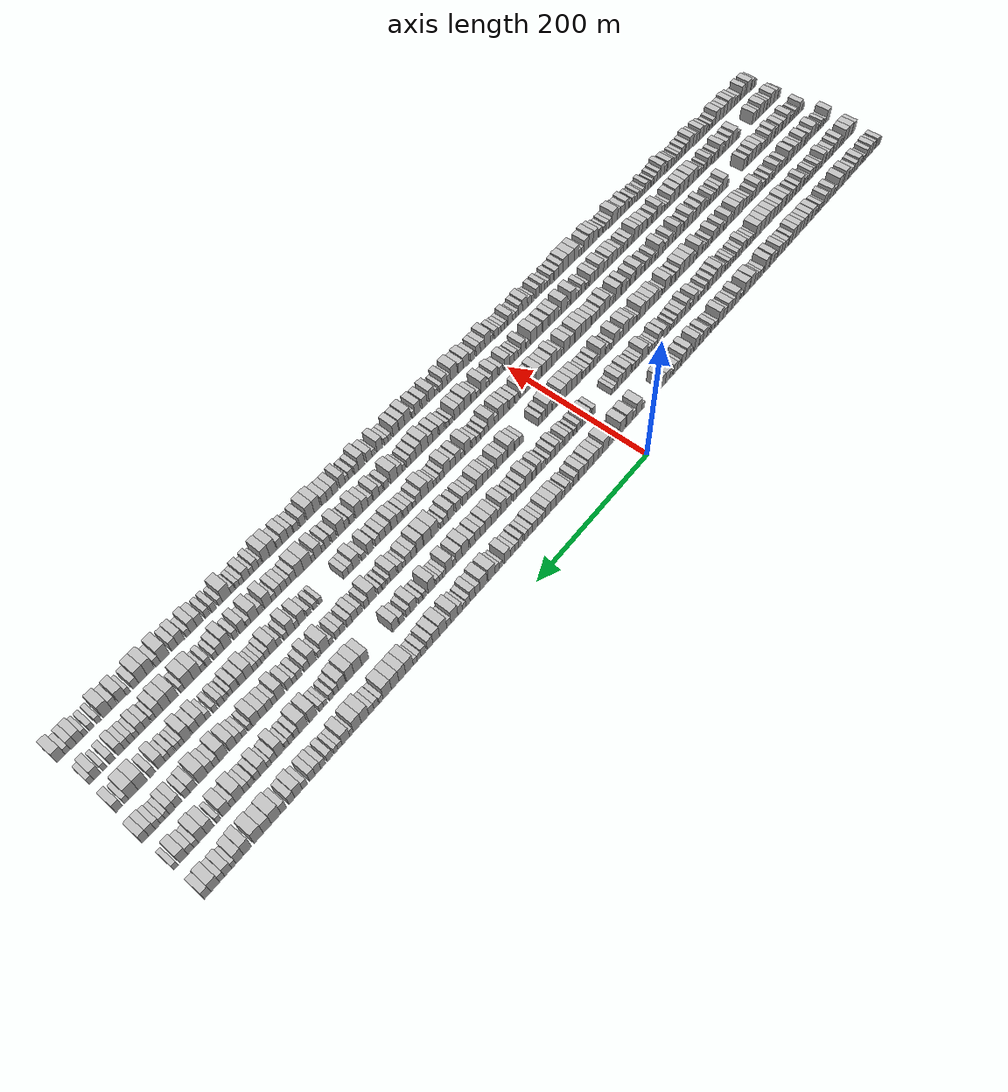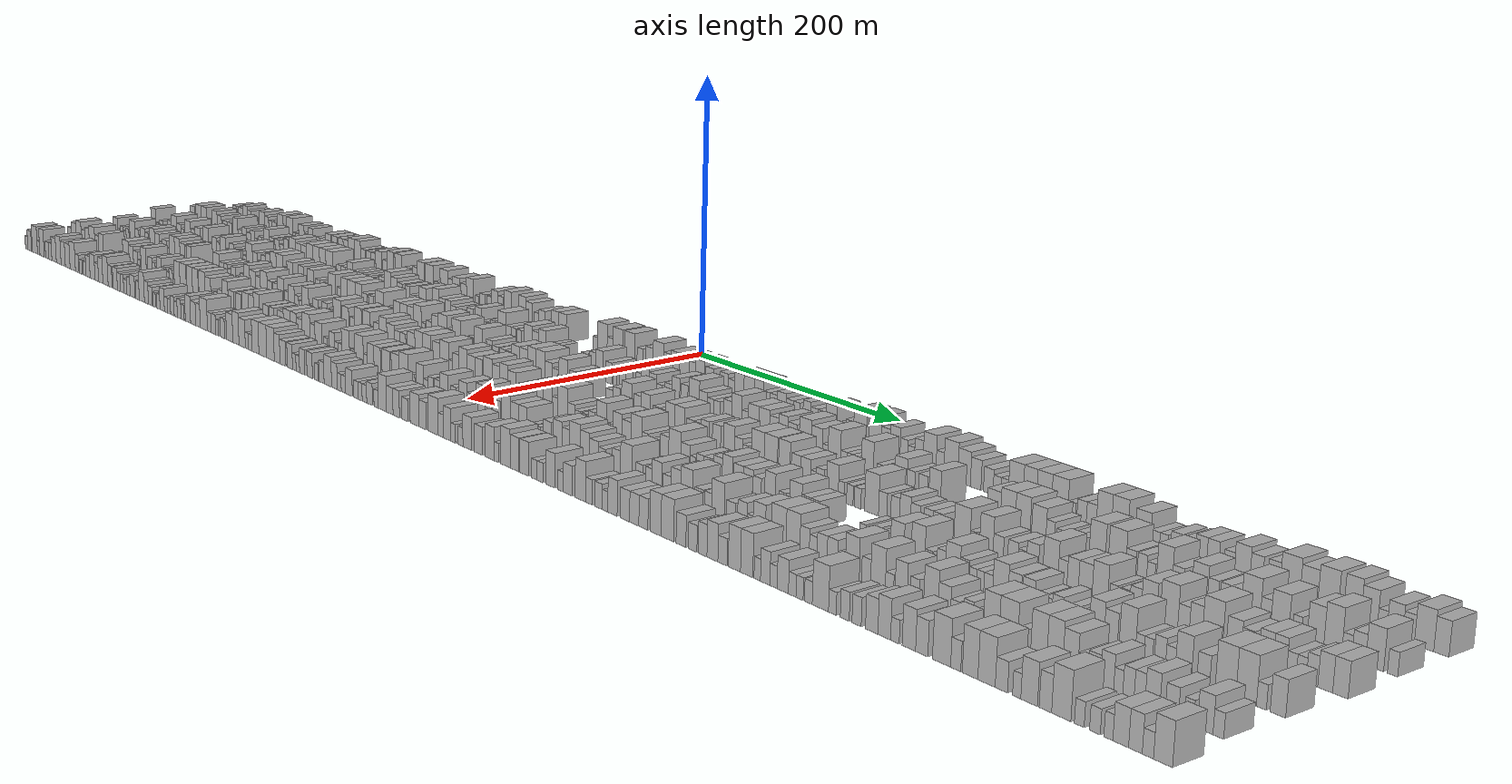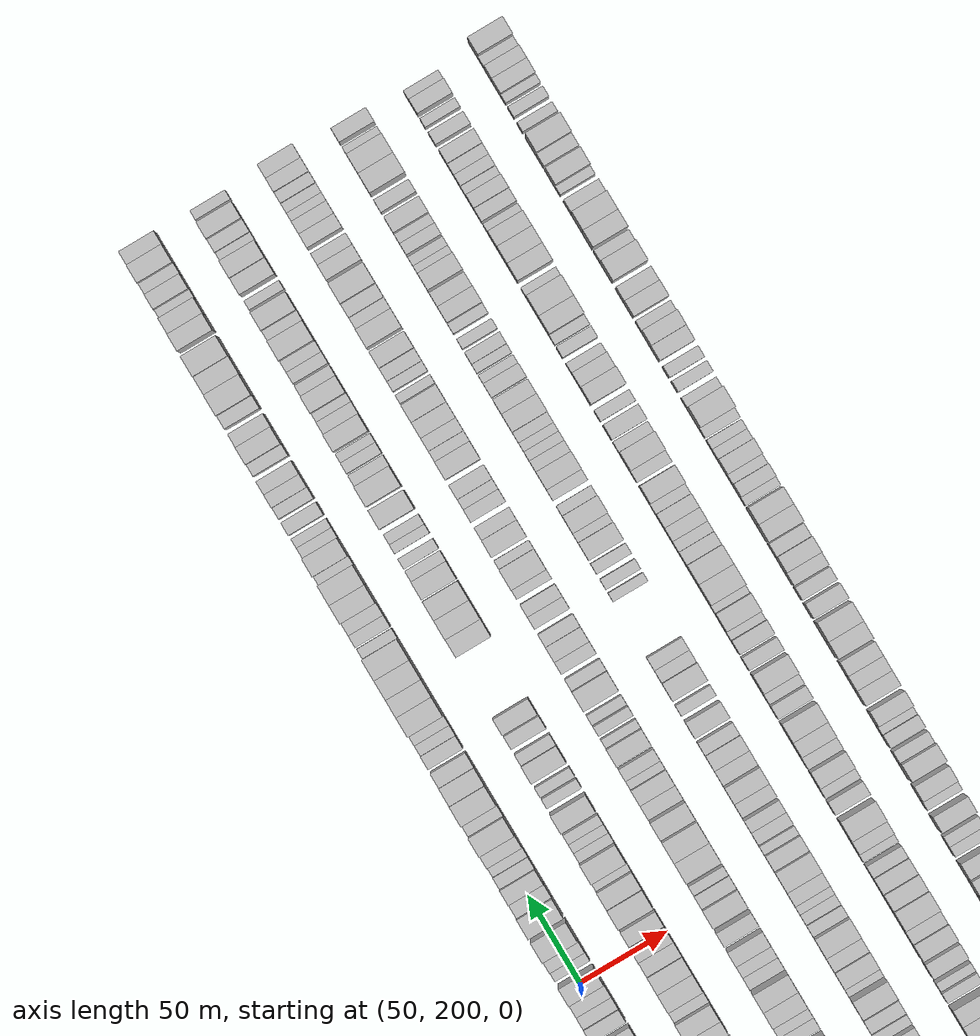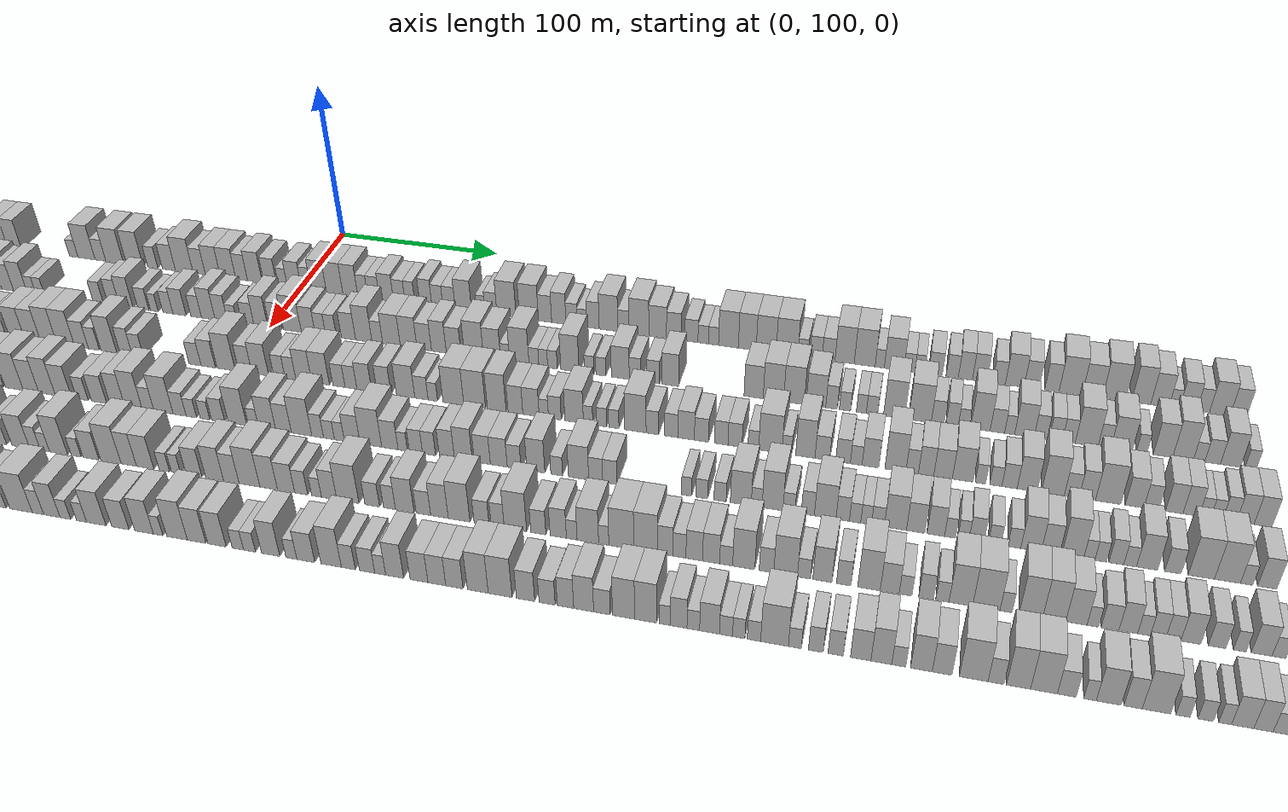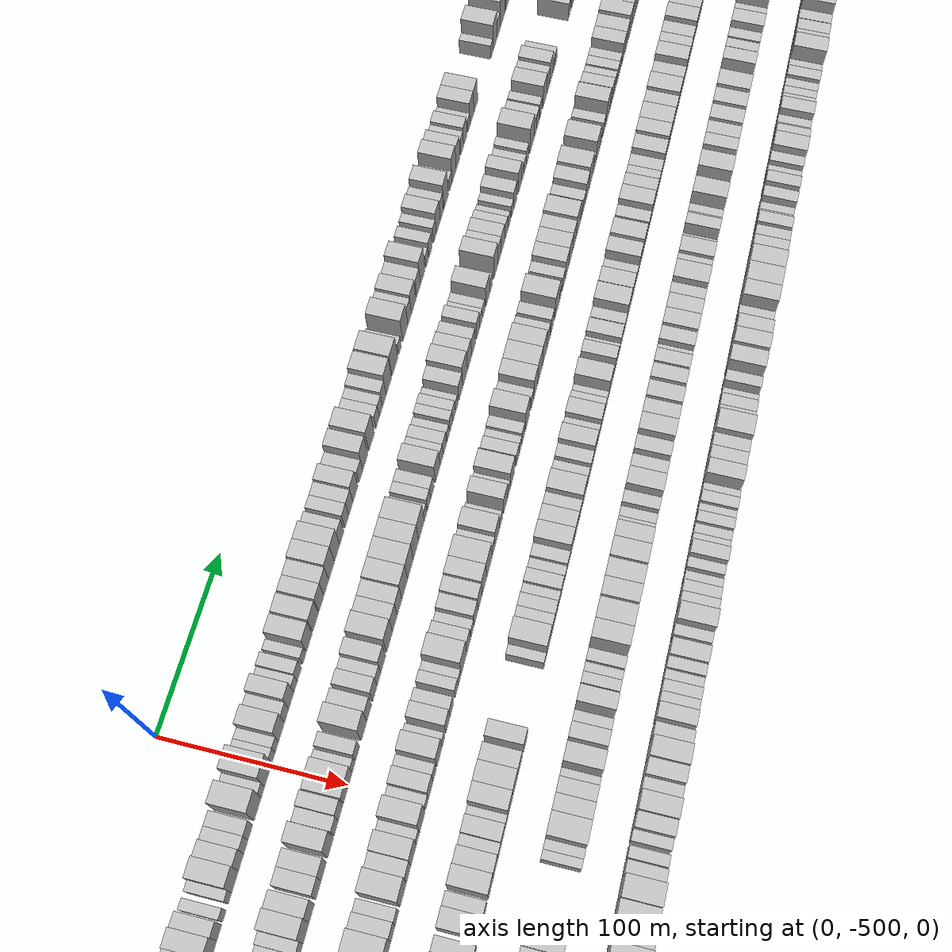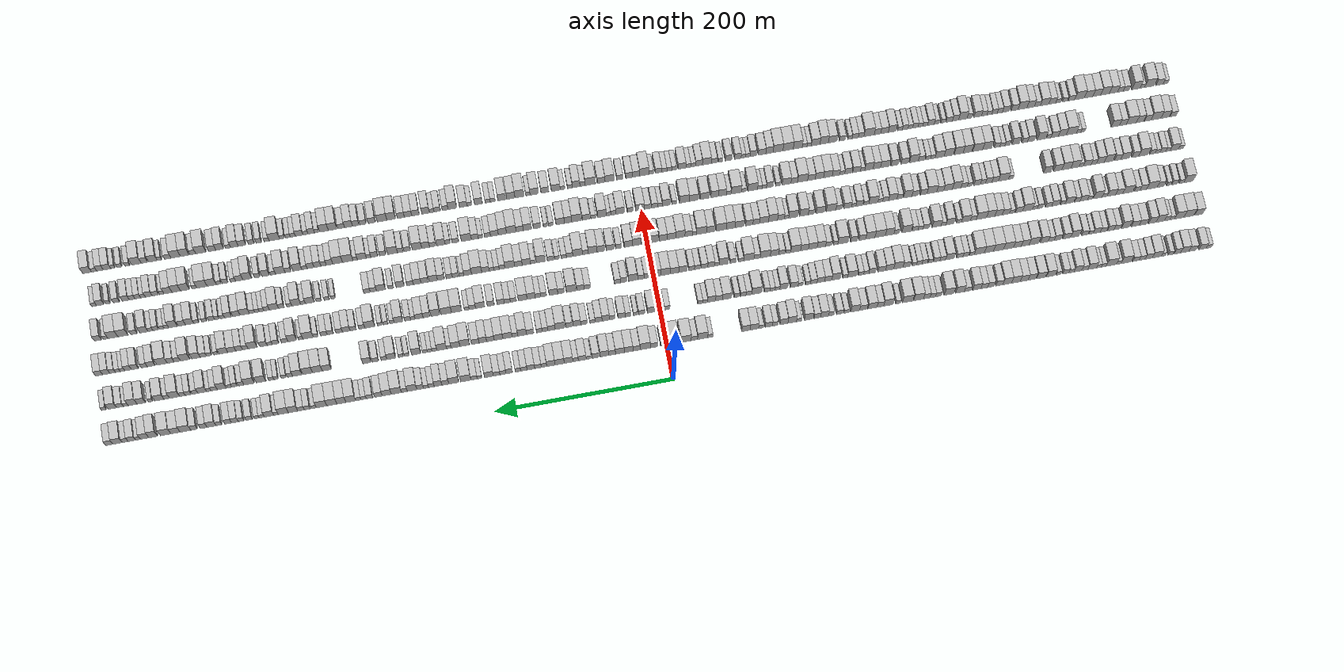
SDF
<sdf version="1.6">
 <world name="default">
  <scene>
   <sky><clouds><speed>12</speed></clouds></sky>
   <ambient>0.4 0.4 0.4 1</ambient>
   <background>0.7 0.7 0.7 1</background>
   <shadows>1</shadows>
  </scene>
  <gravity>0 0 -9.8066</gravity>
  <magnetic_field>6e-06 2.3e-05 -4.2e-05</magnetic_field>
  <physics default="0" name="default_physics" type="ode">
   <ode>
    <solver>
     <type>quick</type>
     <iters>10</iters>
     <sor>1.0</sor>
     <use_dynamic_moi_rescaling>0</use_dynamic_moi_rescaling>
    </solver>
    <constraints>
     <cfm>0</cfm>
     <erp>0.2</erp>
     <contact_max_correcting_vel>100</contact_max_correcting_vel>
     <contact_surface_layer>0.001</contact_surface_layer>
    </constraints>
   </ode>
   <max_step_size>0.004</max_step_size>
   <real_time_factor>1</real_time_factor>
   <real_time_update_rate>250</real_time_update_rate>
  </physics>
  <light name="sun" type="directional">
   <pose>0 0 10 0 0 0</pose>
   <diffuse>0.8 0.8 0.8 1</diffuse>
   <specular>0.2 0.2 0.2 1</specular>
   <attenuation>
    <range>1000</range>
    <constant>0.9</constant>
    <linear>0.01</linear>
    <quadratic>0.001</quadratic>
   </attenuation>
   <direction>-0.5 0.1 -0.9</direction>
  </light>
  <model name="building_1">
   <static>1</static>
   <pose>50.0000 -617.0048 0 0.000000 0.000000 0.000000</pose>
   <link name="link">
    <pose>0 0 6.00 0 0 0</pose>
    <collision name="collision"><geometry><box><size>20.0000 5.9904 12.0000</size></box></geometry></collision>
    <visual name="visual">
     <cast_shadows>0</cast_shadows>
     <geometry><box><size>20.0000 5.9904 12.0000</size></box></geometry>
     <material>
      <script>
       <uri>model://HANNAS_wall/materials/scripts</uri>
       <uri>model://HANNAS_wall/materials/textures</uri>
       <name>vrc/HANNAS_wall</name>
      </script>
     </material>
    </visual>
   </link>
  </model>
  <model name="building_2">
   <static>1</static>
   <pose>50.0000 -609.7454 0 0.000000 0.000000 0.000000</pose>
   <link name="link">
    <pose>0 0 9.00 0 0 0</pose>
    <collision name="collision"><geometry><box><size>20.0000 8.5283 18.0000</size></box></geometry></collision>
    <visual name="visual">
     <cast_shadows>0</cast_shadows>
     <geometry><box><size>20.0000 8.5283 18.0000</size></box></geometry>
     <material>
      <script>
       <uri>model://HANNAS_wall/materials/scripts</uri>
       <uri>model://HANNAS_wall/materials/textures</uri>
       <name>vrc/HANNAS_wall</name>
      </script>
     </material>
    </visual>
   </link>
  </model>
  <model name="building_3">
   <static>1</static>
   <pose>50.0000 -598.1170 0 0.000000 0.000000 0.000000</pose>
   <link name="link">
    <pose>0 0 9.00 0 0 0</pose>
    <collision name="collision"><geometry><box><size>20.0000 8.7286 18.0000</size></box></geometry></collision>
    <visual name="visual">
     <cast_shadows>0</cast_shadows>
     <geometry><box><size>20.0000 8.7286 18.0000</size></box></geometry>
     <material>
      <script>
       <uri>model://HANNAS_wall/materials/scripts</uri>
       <uri>model://HANNAS_wall/materials/textures</uri>
       <name>vrc/HANNAS_wall</name>
      </script>
     </material>
    </visual>
   </link>
  </model>
  <model name="building_4">
   <static>1</static>
   <pose>50.0000 -589.0445 0 0.000000 0.000000 0.000000</pose>
   <link name="link">
    <pose>0 0 10.50 0 0 0</pose>
    <collision name="collision"><geometry><box><size>20.0000 9.4165 21.0000</size></box></geometry></collision>
    <visual name="visual">
     <cast_shadows>0</cast_shadows>
     <geometry><box><size>20.0000 9.4165 21.0000</size></box></geometry>
     <material>
      <script>
       <uri>model://HANNAS_wall/materials/scripts</uri>
       <uri>model://HANNAS_wall/materials/textures</uri>
       <name>vrc/HANNAS_wall</name>
      </script>
     </material>
    </visual>
   </link>
  </model>
  <model name="building_5">
   <static>1</static>
   <pose>50.0000 -580.6027 0 0.000000 0.000000 0.000000</pose>
   <link name="link">
    <pose>0 0 9.00 0 0 0</pose>
    <collision name="collision"><geometry><box><size>20.0000 7.4671 18.0000</size></box></geometry></collision>
    <visual name="visual">
     <cast_shadows>0</cast_shadows>
     <geometry><box><size>20.0000 7.4671 18.0000</size></box></geometry>
     <material>
      <script>
       <uri>model://HANNAS_wall/materials/scripts</uri>
       <uri>model://HANNAS_wall/materials/textures</uri>
       <name>vrc/HANNAS_wall</name>
      </script>
     </material>
    </visual>
   </link>
  </model>
  <model name="building_6">
   <static>1</static>
   <pose>50.0000 -573.0892 0 0.000000 0.000000 0.000000</pose>
   <link name="link">
    <pose>0 0 6.00 0 0 0</pose>
    <collision name="collision"><geometry><box><size>20.0000 5.5600 12.0000</size></box></geometry></collision>
    <visual name="visual">
     <cast_shadows>0</cast_shadows>
     <geometry><box><size>20.0000 5.5600 12.0000</size></box></geometry>
     <material>
      <script>
       <uri>model://HANNAS_wall/materials/scripts</uri>
       <uri>model://HANNAS_wall/materials/textures</uri>
       <name>vrc/HANNAS_wall</name>
      </script>
     </material>
    </visual>
   </link>
  </model>
  <model name="building_7">
   <static>1</static>
   <pose>50.0000 -564.6854 0 0.000000 0.000000 0.000000</pose>
   <link name="link">
    <pose>0 0 6.00 0 0 0</pose>
    <collision name="collision"><geometry><box><size>20.0000 5.2476 12.0000</size></box></geometry></collision>
    <visual name="visual">
     <cast_shadows>0</cast_shadows>
     <geometry><box><size>20.0000 5.2476 12.0000</size></box></geometry>
     <material>
      <script>
       <uri>model://HANNAS_wall/materials/scripts</uri>
       <uri>model://HANNAS_wall/materials/textures</uri>
       <name>vrc/HANNAS_wall</name>
      </script>
     </material>
    </visual>
   </link>
  </model>
  <model name="building_8">
   <static>1</static>
   <pose>50.0000 -556.8912 0 0.000000 0.000000 0.000000</pose>
   <link name="link">
    <pose>0 0 10.50 0 0 0</pose>
    <collision name="collision"><geometry><box><size>20.0000 10.3409 21.0000</size></box></geometry></collision>
    <visual name="visual">
     <cast_shadows>0</cast_shadows>
     <geometry><box><size>20.0000 10.3409 21.0000</size></box></geometry>
     <material>
      <script>
       <uri>model://HANNAS_wall/materials/scripts</uri>
       <uri>model://HANNAS_wall/materials/textures</uri>
       <name>vrc/HANNAS_wall</name>
      </script>
     </material>
    </visual>
   </link>
  </model>
  <model name="building_9">
   <static>1</static>
   <pose>50.0000 -547.6293 0 0.000000 0.000000 0.000000</pose>
   <link name="link">
    <pose>0 0 9.00 0 0 0</pose>
    <collision name="collision"><geometry><box><size>20.0000 8.1828 18.0000</size></box></geometry></collision>
    <visual name="visual">
     <cast_shadows>0</cast_shadows>
     <geometry><box><size>20.0000 8.1828 18.0000</size></box></geometry>
     <material>
      <script>
       <uri>model://HANNAS_wall/materials/scripts</uri>
       <uri>model://HANNAS_wall/materials/textures</uri>
       <name>vrc/HANNAS_wall</name>
      </script>
     </material>
    </visual>
   </link>
  </model>
  <model name="building_10">
   <static>1</static>
   <pose>50.0000 -540.1912 0 0.000000 0.000000 0.000000</pose>
   <link name="link">
    <pose>0 0 7.50 0 0 0</pose>
    <collision name="collision"><geometry><box><size>20.0000 6.6935 15.0000</size></box></geometry></collision>
    <visual name="visual">
     <cast_shadows>0</cast_shadows>
     <geometry><box><size>20.0000 6.6935 15.0000</size></box></geometry>
     <material>
      <script>
       <uri>model://HANNAS_wall/materials/scripts</uri>
       <uri>model://HANNAS_wall/materials/textures</uri>
       <name>vrc/HANNAS_wall</name>
      </script>
     </material>
    </visual>
   </link>
  </model>
  <model name="building_11">
   <static>1</static>
   <pose>50.0000 -533.0951 0 0.000000 0.000000 0.000000</pose>
   <link name="link">
    <pose>0 0 7.50 0 0 0</pose>
    <collision name="collision"><geometry><box><size>20.0000 7.4987 15.0000</size></box></geometry></collision>
    <visual name="visual">
     <cast_shadows>0</cast_shadows>
     <geometry><box><size>20.0000 7.4987 15.0000</size></box></geometry>
     <material>
      <script>
       <uri>model://HANNAS_wall/materials/scripts</uri>
       <uri>model://HANNAS_wall/materials/textures</uri>
       <name>vrc/HANNAS_wall</name>
      </script>
     </material>
    </visual>
   </link>
  </model>
  <model name="building_12">
   <static>1</static>
   <pose>50.0000 -521.6678 0 0.000000 0.000000 0.000000</pose>
   <link name="link">
    <pose>0 0 12.00 0 0 0</pose>
    <collision name="collision"><geometry><box><size>20.0000 11.3558 24.0000</size></box></geometry></collision>
    <visual name="visual">
     <cast_shadows>0</cast_shadows>
     <geometry><box><size>20.0000 11.3558 24.0000</size></box></geometry>
     <material>
      <script>
       <uri>model://HANNAS_wall/materials/scripts</uri>
       <uri>model://HANNAS_wall/materials/textures</uri>
       <name>vrc/HANNAS_wall</name>
      </script>
     </material>
    </visual>
   </link>
  </model>
  <model name="building_13">
   <static>1</static>
   <pose>50.0000 -513.2278 0 0.000000 0.000000 0.000000</pose>
   <link name="link">
    <pose>0 0 6.00 0 0 0</pose>
    <collision name="collision"><geometry><box><size>20.0000 5.5243 12.0000</size></box></geometry></collision>
    <visual name="visual">
     <cast_shadows>0</cast_shadows>
     <geometry><box><size>20.0000 5.5243 12.0000</size></box></geometry>
     <material>
      <script>
       <uri>model://HANNAS_wall/materials/scripts</uri>
       <uri>model://HANNAS_wall/materials/textures</uri>
       <name>vrc/HANNAS_wall</name>
      </script>
     </material>
    </visual>
   </link>
  </model>
  <model name="building_14">
   <static>1</static>
   <pose>50.0000 -504.5600 0 0.000000 0.000000 0.000000</pose>
   <link name="link">
    <pose>0 0 12.00 0 0 0</pose>
    <collision name="collision"><geometry><box><size>20.0000 11.8112 24.0000</size></box></geometry></collision>
    <visual name="visual">
     <cast_shadows>0</cast_shadows>
     <geometry><box><size>20.0000 11.8112 24.0000</size></box></geometry>
     <material>
      <script>
       <uri>model://HANNAS_wall/materials/scripts</uri>
       <uri>model://HANNAS_wall/materials/textures</uri>
       <name>vrc/HANNAS_wall</name>
      </script>
     </material>
    </visual>
   </link>
  </model>
  <model name="building_15">
   <static>1</static>
   <pose>50.0000 -495.9596 0 0.000000 0.000000 0.000000</pose>
   <link name="link">
    <pose>0 0 6.00 0 0 0</pose>
    <collision name="collision"><geometry><box><size>20.0000 5.3896 12.0000</size></box></geometry></collision>
    <visual name="visual">
     <cast_shadows>0</cast_shadows>
     <geometry><box><size>20.0000 5.3896 12.0000</size></box></geometry>
     <material>
      <script>
       <uri>model://HANNAS_wall/materials/scripts</uri>
       <uri>model://HANNAS_wall/materials/textures</uri>
       <name>vrc/HANNAS_wall</name>
      </script>
     </material>
    </visual>
   </link>
  </model>
  <model name="building_16">
   <static>1</static>
   <pose>50.0000 -490.4501 0 0.000000 0.000000 0.000000</pose>
   <link name="link">
    <pose>0 0 6.00 0 0 0</pose>
    <collision name="collision"><geometry><box><size>20.0000 5.6296 12.0000</size></box></geometry></collision>
    <visual name="visual">
     <cast_shadows>0</cast_shadows>
     <geometry><box><size>20.0000 5.6296 12.0000</size></box></geometry>
     <material>
      <script>
       <uri>model://HANNAS_wall/materials/scripts</uri>
       <uri>model://HANNAS_wall/materials/textures</uri>
       <name>vrc/HANNAS_wall</name>
      </script>
     </material>
    </visual>
   </link>
  </model>
  <model name="building_17">
   <static>1</static>
   <pose>50.0000 -482.6837 0 0.000000 0.000000 0.000000</pose>
   <link name="link">
    <pose>0 0 10.50 0 0 0</pose>
    <collision name="collision"><geometry><box><size>20.0000 9.9032 21.0000</size></box></geometry></collision>
    <visual name="visual">
     <cast_shadows>0</cast_shadows>
     <geometry><box><size>20.0000 9.9032 21.0000</size></box></geometry>
     <material>
      <script>
       <uri>model://HANNAS_wall/materials/scripts</uri>
       <uri>model://HANNAS_wall/materials/textures</uri>
       <name>vrc/HANNAS_wall</name>
      </script>
     </material>
    </visual>
   </link>
  </model>
  <model name="building_18">
   <static>1</static>
   <pose>50.0000 -474.1936 0 0.000000 0.000000 0.000000</pose>
   <link name="link">
    <pose>0 0 7.50 0 0 0</pose>
    <collision name="collision"><geometry><box><size>20.0000 7.0768 15.0000</size></box></geometry></collision>
    <visual name="visual">
     <cast_shadows>0</cast_shadows>
     <geometry><box><size>20.0000 7.0768 15.0000</size></box></geometry>
     <material>
      <script>
       <uri>model://HANNAS_wall/materials/scripts</uri>
       <uri>model://HANNAS_wall/materials/textures</uri>
       <name>vrc/HANNAS_wall</name>
      </script>
     </material>
    </visual>
   </link>
  </model>
  <model name="building_19">
   <static>1</static>
   <pose>50.0000 -466.2955 0 0.000000 0.000000 0.000000</pose>
   <link name="link">
    <pose>0 0 10.50 0 0 0</pose>
    <collision name="collision"><geometry><box><size>20.0000 8.7194 21.0000</size></box></geometry></collision>
    <visual name="visual">
     <cast_shadows>0</cast_shadows>
     <geometry><box><size>20.0000 8.7194 21.0000</size></box></geometry>
     <material>
      <script>
       <uri>model://HANNAS_wall/materials/scripts</uri>
       <uri>model://HANNAS_wall/materials/textures</uri>
       <name>vrc/HANNAS_wall</name>
      </script>
     </material>
    </visual>
   </link>
  </model>
  <model name="building_20">
   <static>1</static>
   <pose>50.0000 -458.9874 0 0.000000 0.000000 0.000000</pose>
   <link name="link">
    <pose>0 0 6.00 0 0 0</pose>
    <collision name="collision"><geometry><box><size>20.0000 5.8968 12.0000</size></box></geometry></collision>
    <visual name="visual">
     <cast_shadows>0</cast_shadows>
     <geometry><box><size>20.0000 5.8968 12.0000</size></box></geometry>
     <material>
      <script>
       <uri>model://HANNAS_wall/materials/scripts</uri>
       <uri>model://HANNAS_wall/materials/textures</uri>
       <name>vrc/HANNAS_wall</name>
      </script>
     </material>
    </visual>
   </link>
  </model>
  <model name="building_21">
   <static>1</static>
   <pose>50.0000 -452.5139 0 0.000000 0.000000 0.000000</pose>
   <link name="link">
    <pose>0 0 7.50 0 0 0</pose>
    <collision name="collision"><geometry><box><size>20.0000 7.0502 15.0000</size></box></geometry></collision>
    <visual name="visual">
     <cast_shadows>0</cast_shadows>
     <geometry><box><size>20.0000 7.0502 15.0000</size></box></geometry>
     <material>
      <script>
       <uri>model://HANNAS_wall/materials/scripts</uri>
       <uri>model://HANNAS_wall/materials/textures</uri>
       <name>vrc/HANNAS_wall</name>
      </script>
     </material>
    </visual>
   </link>
  </model>
  <model name="building_22">
   <static>1</static>
   <pose>50.0000 -444.1705 0 0.000000 0.000000 0.000000</pose>
   <link name="link">
    <pose>0 0 6.00 0 0 0</pose>
    <collision name="collision"><geometry><box><size>20.0000 5.6367 12.0000</size></box></geometry></collision>
    <visual name="visual">
     <cast_shadows>0</cast_shadows>
     <geometry><box><size>20.0000 5.6367 12.0000</size></box></geometry>
     <material>
      <script>
       <uri>model://HANNAS_wall/materials/scripts</uri>
       <uri>model://HANNAS_wall/materials/textures</uri>
       <name>vrc/HANNAS_wall</name>
      </script>
     </material>
    </visual>
   </link>
  </model>
  <model name="building_23">
   <static>1</static>
   <pose>50.0000 -435.3232 0 0.000000 0.000000 0.000000</pose>
   <link name="link">
    <pose>0 0 10.50 0 0 0</pose>
    <collision name="collision"><geometry><box><size>20.0000 10.0579 21.0000</size></box></geometry></collision>
    <visual name="visual">
     <cast_shadows>0</cast_shadows>
     <geometry><box><size>20.0000 10.0579 21.0000</size></box></geometry>
     <material>
      <script>
       <uri>model://HANNAS_wall/materials/scripts</uri>
       <uri>model://HANNAS_wall/materials/textures</uri>
       <name>vrc/HANNAS_wall</name>
      </script>
     </material>
    </visual>
   </link>
  </model>
  <model name="building_24">
   <static>1</static>
   <pose>50.0000 -424.1865 0 0.000000 0.000000 0.000000</pose>
   <link name="link">
    <pose>0 0 10.50 0 0 0</pose>
    <collision name="collision"><geometry><box><size>20.0000 10.2155 21.0000</size></box></geometry></collision>
    <visual name="visual">
     <cast_shadows>0</cast_shadows>
     <geometry><box><size>20.0000 10.2155 21.0000</size></box></geometry>
     <material>
      <script>
       <uri>model://HANNAS_wall/materials/scripts</uri>
       <uri>model://HANNAS_wall/materials/textures</uri>
       <name>vrc/HANNAS_wall</name>
      </script>
     </material>
    </visual>
   </link>
  </model>
  <model name="building_25">
   <static>1</static>
   <pose>50.0000 -413.6816 0 0.000000 0.000000 0.000000</pose>
   <link name="link">
    <pose>0 0 10.50 0 0 0</pose>
    <collision name="collision"><geometry><box><size>20.0000 8.7943 21.0000</size></box></geometry></collision>
    <visual name="visual">
     <cast_shadows>0</cast_shadows>
     <geometry><box><size>20.0000 8.7943 21.0000</size></box></geometry>
     <material>
      <script>
       <uri>model://HANNAS_wall/materials/scripts</uri>
       <uri>model://HANNAS_wall/materials/textures</uri>
       <name>vrc/HANNAS_wall</name>
      </script>
     </material>
    </visual>
   </link>
  </model>
  <model name="building_26">
   <static>1</static>
   <pose>50.0000 -404.8417 0 0.000000 0.000000 0.000000</pose>
   <link name="link">
    <pose>0 0 10.50 0 0 0</pose>
    <collision name="collision"><geometry><box><size>20.0000 8.8855 21.0000</size></box></geometry></collision>
    <visual name="visual">
     <cast_shadows>0</cast_shadows>
     <geometry><box><size>20.0000 8.8855 21.0000</size></box></geometry>
     <material>
      <script>
       <uri>model://HANNAS_wall/materials/scripts</uri>
       <uri>model://HANNAS_wall/materials/textures</uri>
       <name>vrc/HANNAS_wall</name>
      </script>
     </material>
    </visual>
   </link>
  </model>
  <model name="building_27">
   <static>1</static>
   <pose>50.0000 -395.2701 0 0.000000 0.000000 0.000000</pose>
   <link name="link">
    <pose>0 0 12.00 0 0 0</pose>
    <collision name="collision"><geometry><box><size>20.0000 10.2577 24.0000</size></box></geometry></collision>
    <visual name="visual">
     <cast_shadows>0</cast_shadows>
     <geometry><box><size>20.0000 10.2577 24.0000</size></box></geometry>
     <material>
      <script>
       <uri>model://HANNAS_wall/materials/scripts</uri>
       <uri>model://HANNAS_wall/materials/textures</uri>
       <name>vrc/HANNAS_wall</name>
      </script>
     </material>
    </visual>
   </link>
  </model>
  <model name="building_28">
   <static>1</static>
   <pose>50.0000 -385.2097 0 0.000000 0.000000 0.000000</pose>
   <link name="link">
    <pose>0 0 12.00 0 0 0</pose>
    <collision name="collision"><geometry><box><size>20.0000 9.8632 24.0000</size></box></geometry></collision>
    <visual name="visual">
     <cast_shadows>0</cast_shadows>
     <geometry><box><size>20.0000 9.8632 24.0000</size></box></geometry>
     <material>
      <script>
       <uri>model://HANNAS_wall/materials/scripts</uri>
       <uri>model://HANNAS_wall/materials/textures</uri>
       <name>vrc/HANNAS_wall</name>
      </script>
     </material>
    </visual>
   </link>
  </model>
  <model name="building_29">
   <static>1</static>
   <pose>50.0000 -376.4399 0 0.000000 0.000000 0.000000</pose>
   <link name="link">
    <pose>0 0 9.00 0 0 0</pose>
    <collision name="collision"><geometry><box><size>20.0000 7.6765 18.0000</size></box></geometry></collision>
    <visual name="visual">
     <cast_shadows>0</cast_shadows>
     <geometry><box><size>20.0000 7.6765 18.0000</size></box></geometry>
     <material>
      <script>
       <uri>model://HANNAS_wall/materials/scripts</uri>
       <uri>model://HANNAS_wall/materials/textures</uri>
       <name>vrc/HANNAS_wall</name>
      </script>
     </material>
    </visual>
   </link>
  </model>
  <model name="building_30">
   <static>1</static>
   <pose>50.0000 -366.8868 0 0.000000 0.000000 0.000000</pose>
   <link name="link">
    <pose>0 0 9.00 0 0 0</pose>
    <collision name="collision"><geometry><box><size>20.0000 7.4297 18.0000</size></box></geometry></collision>
    <visual name="visual">
     <cast_shadows>0</cast_shadows>
     <geometry><box><size>20.0000 7.4297 18.0000</size></box></geometry>
     <material>
      <script>
       <uri>model://HANNAS_wall/materials/scripts</uri>
       <uri>model://HANNAS_wall/materials/textures</uri>
       <name>vrc/HANNAS_wall</name>
      </script>
     </material>
    </visual>
   </link>
  </model>
  <model name="building_31">
   <static>1</static>
   <pose>50.0000 -359.2685 0 0.000000 0.000000 0.000000</pose>
   <link name="link">
    <pose>0 0 9.00 0 0 0</pose>
    <collision name="collision"><geometry><box><size>20.0000 7.8068 18.0000</size></box></geometry></collision>
    <visual name="visual">
     <cast_shadows>0</cast_shadows>
     <geometry><box><size>20.0000 7.8068 18.0000</size></box></geometry>
     <material>
      <script>
       <uri>model://HANNAS_wall/materials/scripts</uri>
       <uri>model://HANNAS_wall/materials/textures</uri>
       <name>vrc/HANNAS_wall</name>
      </script>
     </material>
    </visual>
   </link>
  </model>
  <model name="building_32">
   <static>1</static>
   <pose>50.0000 -350.6555 0 0.000000 0.000000 0.000000</pose>
   <link name="link">
    <pose>0 0 10.50 0 0 0</pose>
    <collision name="collision"><geometry><box><size>20.0000 9.4192 21.0000</size></box></geometry></collision>
    <visual name="visual">
     <cast_shadows>0</cast_shadows>
     <geometry><box><size>20.0000 9.4192 21.0000</size></box></geometry>
     <material>
      <script>
       <uri>model://HANNAS_wall/materials/scripts</uri>
       <uri>model://HANNAS_wall/materials/textures</uri>
       <name>vrc/HANNAS_wall</name>
      </script>
     </material>
    </visual>
   </link>
  </model>
  <model name="building_33">
   <static>1</static>
   <pose>50.0000 -340.2218 0 0.000000 0.000000 0.000000</pose>
   <link name="link">
    <pose>0 0 7.50 0 0 0</pose>
    <collision name="collision"><geometry><box><size>20.0000 7.4481 15.0000</size></box></geometry></collision>
    <visual name="visual">
     <cast_shadows>0</cast_shadows>
     <geometry><box><size>20.0000 7.4481 15.0000</size></box></geometry>
     <material>
      <script>
       <uri>model://HANNAS_wall/materials/scripts</uri>
       <uri>model://HANNAS_wall/materials/textures</uri>
       <name>vrc/HANNAS_wall</name>
      </script>
     </material>
    </visual>
   </link>
  </model>
  <model name="building_34">
   <static>1</static>
   <pose>50.0000 -331.5329 0 0.000000 0.000000 0.000000</pose>
   <link name="link">
    <pose>0 0 12.00 0 0 0</pose>
    <collision name="collision"><geometry><box><size>20.0000 9.9299 24.0000</size></box></geometry></collision>
    <visual name="visual">
     <cast_shadows>0</cast_shadows>
     <geometry><box><size>20.0000 9.9299 24.0000</size></box></geometry>
     <material>
      <script>
       <uri>model://HANNAS_wall/materials/scripts</uri>
       <uri>model://HANNAS_wall/materials/textures</uri>
       <name>vrc/HANNAS_wall</name>
      </script>
     </material>
    </visual>
   </link>
  </model>
  <model name="building_35">
   <static>1</static>
   <pose>50.0000 -319.0540 0 0.000000 0.000000 0.000000</pose>
   <link name="link">
    <pose>0 0 12.00 0 0 0</pose>
    <collision name="collision"><geometry><box><size>20.0000 11.0279 24.0000</size></box></geometry></collision>
    <visual name="visual">
     <cast_shadows>0</cast_shadows>
     <geometry><box><size>20.0000 11.0279 24.0000</size></box></geometry>
     <material>
      <script>
       <uri>model://HANNAS_wall/materials/scripts</uri>
       <uri>model://HANNAS_wall/materials/textures</uri>
       <name>vrc/HANNAS_wall</name>
      </script>
     </material>
    </visual>
   </link>
  </model>
  <model name="building_36">
   <static>1</static>
   <pose>50.0000 -307.1004 0 0.000000 0.000000 0.000000</pose>
   <link name="link">
    <pose>0 0 7.50 0 0 0</pose>
    <collision name="collision"><geometry><box><size>20.0000 6.8793 15.0000</size></box></geometry></collision>
    <visual name="visual">
     <cast_shadows>0</cast_shadows>
     <geometry><box><size>20.0000 6.8793 15.0000</size></box></geometry>
     <material>
      <script>
       <uri>model://HANNAS_wall/materials/scripts</uri>
       <uri>model://HANNAS_wall/materials/textures</uri>
       <name>vrc/HANNAS_wall</name>
      </script>
     </material>
    </visual>
   </link>
  </model>
  <model name="building_37">
   <static>1</static>
   <pose>50.0000 -300.4534 0 0.000000 0.000000 0.000000</pose>
   <link name="link">
    <pose>0 0 7.50 0 0 0</pose>
    <collision name="collision"><geometry><box><size>20.0000 6.4147 15.0000</size></box></geometry></collision>
    <visual name="visual">
     <cast_shadows>0</cast_shadows>
     <geometry><box><size>20.0000 6.4147 15.0000</size></box></geometry>
     <material>
      <script>
       <uri>model://HANNAS_wall/materials/scripts</uri>
       <uri>model://HANNAS_wall/materials/textures</uri>
       <name>vrc/HANNAS_wall</name>
      </script>
     </material>
    </visual>
   </link>
  </model>
  <model name="building_38">
   <static>1</static>
   <pose>50.0000 -293.5291 0 0.000000 0.000000 0.000000</pose>
   <link name="link">
    <pose>0 0 9.00 0 0 0</pose>
    <collision name="collision"><geometry><box><size>20.0000 7.4340 18.0000</size></box></geometry></collision>
    <visual name="visual">
     <cast_shadows>0</cast_shadows>
     <geometry><box><size>20.0000 7.4340 18.0000</size></box></geometry>
     <material>
      <script>
       <uri>model://HANNAS_wall/materials/scripts</uri>
       <uri>model://HANNAS_wall/materials/textures</uri>
       <name>vrc/HANNAS_wall</name>
      </script>
     </material>
    </visual>
   </link>
  </model>
  <model name="building_39">
   <static>1</static>
   <pose>50.0000 -284.2973 0 0.000000 0.000000 0.000000</pose>
   <link name="link">
    <pose>0 0 12.00 0 0 0</pose>
    <collision name="collision"><geometry><box><size>20.0000 11.0297 24.0000</size></box></geometry></collision>
    <visual name="visual">
     <cast_shadows>0</cast_shadows>
     <geometry><box><size>20.0000 11.0297 24.0000</size></box></geometry>
     <material>
      <script>
       <uri>model://HANNAS_wall/materials/scripts</uri>
       <uri>model://HANNAS_wall/materials/textures</uri>
       <name>vrc/HANNAS_wall</name>
      </script>
     </material>
    </visual>
   </link>
  </model>
  <model name="building_40">
   <static>1</static>
   <pose>50.0000 -271.8673 0 0.000000 0.000000 0.000000</pose>
   <link name="link">
    <pose>0 0 12.00 0 0 0</pose>
    <collision name="collision"><geometry><box><size>20.0000 11.8303 24.0000</size></box></geometry></collision>
    <visual name="visual">
     <cast_shadows>0</cast_shadows>
     <geometry><box><size>20.0000 11.8303 24.0000</size></box></geometry>
     <material>
      <script>
       <uri>model://HANNAS_wall/materials/scripts</uri>
       <uri>model://HANNAS_wall/materials/textures</uri>
       <name>vrc/HANNAS_wall</name>
      </script>
     </material>
    </visual>
   </link>
  </model>
  <model name="building_41">
   <static>1</static>
   <pose>50.0000 -261.1671 0 0.000000 0.000000 0.000000</pose>
   <link name="link">
    <pose>0 0 6.00 0 0 0</pose>
    <collision name="collision"><geometry><box><size>20.0000 5.5702 12.0000</size></box></geometry></collision>
    <visual name="visual">
     <cast_shadows>0</cast_shadows>
     <geometry><box><size>20.0000 5.5702 12.0000</size></box></geometry>
     <material>
      <script>
       <uri>model://HANNAS_wall/materials/scripts</uri>
       <uri>model://HANNAS_wall/materials/textures</uri>
       <name>vrc/HANNAS_wall</name>
      </script>
     </material>
    </visual>
   </link>
  </model>
  <model name="building_42">
   <static>1</static>
   <pose>50.0000 -249.9636 0 0.000000 0.000000 0.000000</pose>
   <link name="link">
    <pose>0 0 12.00 0 0 0</pose>
    <collision name="collision"><geometry><box><size>20.0000 10.8366 24.0000</size></box></geometry></collision>
    <visual name="visual">
     <cast_shadows>0</cast_shadows>
     <geometry><box><size>20.0000 10.8366 24.0000</size></box></geometry>
     <material>
      <script>
       <uri>model://HANNAS_wall/materials/scripts</uri>
       <uri>model://HANNAS_wall/materials/textures</uri>
       <name>vrc/HANNAS_wall</name>
      </script>
     </material>
    </visual>
   </link>
  </model>
  <model name="building_43">
   <static>1</static>
   <pose>50.0000 -240.7548 0 0.000000 0.000000 0.000000</pose>
   <link name="link">
    <pose>0 0 9.00 0 0 0</pose>
    <collision name="collision"><geometry><box><size>20.0000 7.5812 18.0000</size></box></geometry></collision>
    <visual name="visual">
     <cast_shadows>0</cast_shadows>
     <geometry><box><size>20.0000 7.5812 18.0000</size></box></geometry>
     <material>
      <script>
       <uri>model://HANNAS_wall/materials/scripts</uri>
       <uri>model://HANNAS_wall/materials/textures</uri>
       <name>vrc/HANNAS_wall</name>
      </script>
     </material>
    </visual>
   </link>
  </model>
  <model name="building_44">
   <static>1</static>
   <pose>50.0000 -231.9207 0 0.000000 0.000000 0.000000</pose>
   <link name="link">
    <pose>0 0 10.50 0 0 0</pose>
    <collision name="collision"><geometry><box><size>20.0000 10.0871 21.0000</size></box></geometry></collision>
    <visual name="visual">
     <cast_shadows>0</cast_shadows>
     <geometry><box><size>20.0000 10.0871 21.0000</size></box></geometry>
     <material>
      <script>
       <uri>model://HANNAS_wall/materials/scripts</uri>
       <uri>model://HANNAS_wall/materials/textures</uri>
       <name>vrc/HANNAS_wall</name>
      </script>
     </material>
    </visual>
   </link>
  </model>
  <model name="building_45">
   <static>1</static>
   <pose>50.0000 -221.5082 0 0.000000 0.000000 0.000000</pose>
   <link name="link">
    <pose>0 0 9.00 0 0 0</pose>
    <collision name="collision"><geometry><box><size>20.0000 8.7379 18.0000</size></box></geometry></collision>
    <visual name="visual">
     <cast_shadows>0</cast_shadows>
     <geometry><box><size>20.0000 8.7379 18.0000</size></box></geometry>
     <material>
      <script>
       <uri>model://HANNAS_wall/materials/scripts</uri>
       <uri>model://HANNAS_wall/materials/textures</uri>
       <name>vrc/HANNAS_wall</name>
      </script>
     </material>
    </visual>
   </link>
  </model>
  <model name="building_46">
   <static>1</static>
   <pose>50.0000 -212.1835 0 0.000000 0.000000 0.000000</pose>
   <link name="link">
    <pose>0 0 12.00 0 0 0</pose>
    <collision name="collision"><geometry><box><size>20.0000 9.9113 24.0000</size></box></geometry></collision>
    <visual name="visual">
     <cast_shadows>0</cast_shadows>
     <geometry><box><size>20.0000 9.9113 24.0000</size></box></geometry>
     <material>
      <script>
       <uri>model://HANNAS_wall/materials/scripts</uri>
       <uri>model://HANNAS_wall/materials/textures</uri>
       <name>vrc/HANNAS_wall</name>
      </script>
     </material>
    </visual>
   </link>
  </model>
  <model name="building_47">
   <static>1</static>
   <pose>50.0000 -202.3374 0 0.000000 0.000000 0.000000</pose>
   <link name="link">
    <pose>0 0 6.00 0 0 0</pose>
    <collision name="collision"><geometry><box><size>20.0000 5.7810 12.0000</size></box></geometry></collision>
    <visual name="visual">
     <cast_shadows>0</cast_shadows>
     <geometry><box><size>20.0000 5.7810 12.0000</size></box></geometry>
     <material>
      <script>
       <uri>model://HANNAS_wall/materials/scripts</uri>
       <uri>model://HANNAS_wall/materials/textures</uri>
       <name>vrc/HANNAS_wall</name>
      </script>
     </material>
    </visual>
   </link>
  </model>
  <model name="building_48">
   <static>1</static>
   <pose>50.0000 -194.7941 0 0.000000 0.000000 0.000000</pose>
   <link name="link">
    <pose>0 0 7.50 0 0 0</pose>
    <collision name="collision"><geometry><box><size>20.0000 7.3055 15.0000</size></box></geometry></collision>
    <visual name="visual">
     <cast_shadows>0</cast_shadows>
     <geometry><box><size>20.0000 7.3055 15.0000</size></box></geometry>
     <material>
      <script>
       <uri>model://HANNAS_wall/materials/scripts</uri>
       <uri>model://HANNAS_wall/materials/textures</uri>
       <name>vrc/HANNAS_wall</name>
      </script>
     </material>
    </visual>
   </link>
  </model>
  <model name="building_49">
   <static>1</static>
   <pose>50.0000 -185.0760 0 0.000000 0.000000 0.000000</pose>
   <link name="link">
    <pose>0 0 7.50 0 0 0</pose>
    <collision name="collision"><geometry><box><size>20.0000 6.1306 15.0000</size></box></geometry></collision>
    <visual name="visual">
     <cast_shadows>0</cast_shadows>
     <geometry><box><size>20.0000 6.1306 15.0000</size></box></geometry>
     <material>
      <script>
       <uri>model://HANNAS_wall/materials/scripts</uri>
       <uri>model://HANNAS_wall/materials/textures</uri>
       <name>vrc/HANNAS_wall</name>
      </script>
     </material>
    </visual>
   </link>
  </model>
  <model name="building_50">
   <static>1</static>
   <pose>50.0000 -177.4437 0 0.000000 0.000000 0.000000</pose>
   <link name="link">
    <pose>0 0 10.50 0 0 0</pose>
    <collision name="collision"><geometry><box><size>20.0000 9.1340 21.0000</size></box></geometry></collision>
    <visual name="visual">
     <cast_shadows>0</cast_shadows>
     <geometry><box><size>20.0000 9.1340 21.0000</size></box></geometry>
     <material>
      <script>
       <uri>model://HANNAS_wall/materials/scripts</uri>
       <uri>model://HANNAS_wall/materials/textures</uri>
       <name>vrc/HANNAS_wall</name>
      </script>
     </material>
    </visual>
   </link>
  </model>
  <model name="building_51">
   <static>1</static>
   <pose>50.0000 -169.1951 0 0.000000 0.000000 0.000000</pose>
   <link name="link">
    <pose>0 0 9.00 0 0 0</pose>
    <collision name="collision"><geometry><box><size>20.0000 7.3631 18.0000</size></box></geometry></collision>
    <visual name="visual">
     <cast_shadows>0</cast_shadows>
     <geometry><box><size>20.0000 7.3631 18.0000</size></box></geometry>
     <material>
      <script>
       <uri>model://HANNAS_wall/materials/scripts</uri>
       <uri>model://HANNAS_wall/materials/textures</uri>
       <name>vrc/HANNAS_wall</name>
      </script>
     </material>
    </visual>
   </link>
  </model>
  <model name="building_52">
   <static>1</static>
   <pose>50.0000 -159.5304 0 0.000000 0.000000 0.000000</pose>
   <link name="link">
    <pose>0 0 12.00 0 0 0</pose>
    <collision name="collision"><geometry><box><size>20.0000 9.9664 24.0000</size></box></geometry></collision>
    <visual name="visual">
     <cast_shadows>0</cast_shadows>
     <geometry><box><size>20.0000 9.9664 24.0000</size></box></geometry>
     <material>
      <script>
       <uri>model://HANNAS_wall/materials/scripts</uri>
       <uri>model://HANNAS_wall/materials/textures</uri>
       <name>vrc/HANNAS_wall</name>
      </script>
     </material>
    </visual>
   </link>
  </model>
  <model name="building_53">
   <static>1</static>
   <pose>50.0000 -148.5701 0 0.000000 0.000000 0.000000</pose>
   <link name="link">
    <pose>0 0 6.00 0 0 0</pose>
    <collision name="collision"><geometry><box><size>20.0000 5.9542 12.0000</size></box></geometry></collision>
    <visual name="visual">
     <cast_shadows>0</cast_shadows>
     <geometry><box><size>20.0000 5.9542 12.0000</size></box></geometry>
     <material>
      <script>
       <uri>model://HANNAS_wall/materials/scripts</uri>
       <uri>model://HANNAS_wall/materials/textures</uri>
       <name>vrc/HANNAS_wall</name>
      </script>
     </material>
    </visual>
   </link>
  </model>
  <model name="building_54">
   <static>1</static>
   <pose>50.0000 -140.7687 0 0.000000 0.000000 0.000000</pose>
   <link name="link">
    <pose>0 0 12.00 0 0 0</pose>
    <collision name="collision"><geometry><box><size>20.0000 9.6486 24.0000</size></box></geometry></collision>
    <visual name="visual">
     <cast_shadows>0</cast_shadows>
     <geometry><box><size>20.0000 9.6486 24.0000</size></box></geometry>
     <material>
      <script>
       <uri>model://HANNAS_wall/materials/scripts</uri>
       <uri>model://HANNAS_wall/materials/textures</uri>
       <name>vrc/HANNAS_wall</name>
      </script>
     </material>
    </visual>
   </link>
  </model>
  <model name="building_55">
   <static>1</static>
   <pose>50.0000 -131.4038 0 0.000000 0.000000 0.000000</pose>
   <link name="link">
    <pose>0 0 10.50 0 0 0</pose>
    <collision name="collision"><geometry><box><size>20.0000 9.0811 21.0000</size></box></geometry></collision>
    <visual name="visual">
     <cast_shadows>0</cast_shadows>
     <geometry><box><size>20.0000 9.0811 21.0000</size></box></geometry>
     <material>
      <script>
       <uri>model://HANNAS_wall/materials/scripts</uri>
       <uri>model://HANNAS_wall/materials/textures</uri>
       <name>vrc/HANNAS_wall</name>
      </script>
     </material>
    </visual>
   </link>
  </model>
  <model name="building_56">
   <static>1</static>
   <pose>50.0000 -121.6755 0 0.000000 0.000000 0.000000</pose>
   <link name="link">
    <pose>0 0 7.50 0 0 0</pose>
    <collision name="collision"><geometry><box><size>20.0000 6.3754 15.0000</size></box></geometry></collision>
    <visual name="visual">
     <cast_shadows>0</cast_shadows>
     <geometry><box><size>20.0000 6.3754 15.0000</size></box></geometry>
     <material>
      <script>
       <uri>model://HANNAS_wall/materials/scripts</uri>
       <uri>model://HANNAS_wall/materials/textures</uri>
       <name>vrc/HANNAS_wall</name>
      </script>
     </material>
    </visual>
   </link>
  </model>
  <model name="building_57">
   <static>1</static>
   <pose>50.0000 -114.4243 0 0.000000 0.000000 0.000000</pose>
   <link name="link">
    <pose>0 0 9.00 0 0 0</pose>
    <collision name="collision"><geometry><box><size>20.0000 8.1271 18.0000</size></box></geometry></collision>
    <visual name="visual">
     <cast_shadows>0</cast_shadows>
     <geometry><box><size>20.0000 8.1271 18.0000</size></box></geometry>
     <material>
      <script>
       <uri>model://HANNAS_wall/materials/scripts</uri>
       <uri>model://HANNAS_wall/materials/textures</uri>
       <name>vrc/HANNAS_wall</name>
      </script>
     </material>
    </visual>
   </link>
  </model>
  <model name="building_58">
   <static>1</static>
   <pose>50.0000 -105.5826 0 0.000000 0.000000 0.000000</pose>
   <link name="link">
    <pose>0 0 6.00 0 0 0</pose>
    <collision name="collision"><geometry><box><size>20.0000 5.5562 12.0000</size></box></geometry></collision>
    <visual name="visual">
     <cast_shadows>0</cast_shadows>
     <geometry><box><size>20.0000 5.5562 12.0000</size></box></geometry>
     <material>
      <script>
       <uri>model://HANNAS_wall/materials/scripts</uri>
       <uri>model://HANNAS_wall/materials/textures</uri>
       <name>vrc/HANNAS_wall</name>
      </script>
     </material>
    </visual>
   </link>
  </model>
  <model name="building_59">
   <static>1</static>
   <pose>50.0000 -98.0657 0 0.000000 0.000000 0.000000</pose>
   <link name="link">
    <pose>0 0 10.50 0 0 0</pose>
    <collision name="collision"><geometry><box><size>20.0000 9.4777 21.0000</size></box></geometry></collision>
    <visual name="visual">
     <cast_shadows>0</cast_shadows>
     <geometry><box><size>20.0000 9.4777 21.0000</size></box></geometry>
     <material>
      <script>
       <uri>model://HANNAS_wall/materials/scripts</uri>
       <uri>model://HANNAS_wall/materials/textures</uri>
       <name>vrc/HANNAS_wall</name>
      </script>
     </material>
    </visual>
   </link>
  </model>
  <model name="building_60">
   <static>1</static>
   <pose>50.0000 -88.5477 0 0.000000 0.000000 0.000000</pose>
   <link name="link">
    <pose>0 0 10.50 0 0 0</pose>
    <collision name="collision"><geometry><box><size>20.0000 9.5583 21.0000</size></box></geometry></collision>
    <visual name="visual">
     <cast_shadows>0</cast_shadows>
     <geometry><box><size>20.0000 9.5583 21.0000</size></box></geometry>
     <material>
      <script>
       <uri>model://HANNAS_wall/materials/scripts</uri>
       <uri>model://HANNAS_wall/materials/textures</uri>
       <name>vrc/HANNAS_wall</name>
      </script>
     </material>
    </visual>
   </link>
  </model>
  <model name="building_61">
   <static>1</static>
   <pose>50.0000 -48.2554 0 0.000000 0.000000 0.000000</pose>
   <link name="link">
    <pose>0 0 6.00 0 0 0</pose>
    <collision name="collision"><geometry><box><size>20.0000 5.6754 12.0000</size></box></geometry></collision>
    <visual name="visual">
     <cast_shadows>0</cast_shadows>
     <geometry><box><size>20.0000 5.6754 12.0000</size></box></geometry>
     <material>
      <script>
       <uri>model://HANNAS_wall/materials/scripts</uri>
       <uri>model://HANNAS_wall/materials/textures</uri>
       <name>vrc/HANNAS_wall</name>
      </script>
     </material>
    </visual>
   </link>
  </model>
  <model name="building_62">
   <static>1</static>
   <pose>50.0000 -39.6588 0 0.000000 0.000000 0.000000</pose>
   <link name="link">
    <pose>0 0 12.00 0 0 0</pose>
    <collision name="collision"><geometry><box><size>20.0000 11.5177 24.0000</size></box></geometry></collision>
    <visual name="visual">
     <cast_shadows>0</cast_shadows>
     <geometry><box><size>20.0000 11.5177 24.0000</size></box></geometry>
     <material>
      <script>
       <uri>model://HANNAS_wall/materials/scripts</uri>
       <uri>model://HANNAS_wall/materials/textures</uri>
       <name>vrc/HANNAS_wall</name>
      </script>
     </material>
    </visual>
   </link>
  </model>
  <model name="building_63">
   <static>1</static>
   <pose>50.0000 -30.3144 0 0.000000 0.000000 0.000000</pose>
   <link name="link">
    <pose>0 0 7.50 0 0 0</pose>
    <collision name="collision"><geometry><box><size>20.0000 7.1711 15.0000</size></box></geometry></collision>
    <visual name="visual">
     <cast_shadows>0</cast_shadows>
     <geometry><box><size>20.0000 7.1711 15.0000</size></box></geometry>
     <material>
      <script>
       <uri>model://HANNAS_wall/materials/scripts</uri>
       <uri>model://HANNAS_wall/materials/textures</uri>
       <name>vrc/HANNAS_wall</name>
      </script>
     </material>
    </visual>
   </link>
  </model>
  <model name="building_64">
   <static>1</static>
   <pose>50.0000 -20.8321 0 0.000000 0.000000 0.000000</pose>
   <link name="link">
    <pose>0 0 12.00 0 0 0</pose>
    <collision name="collision"><geometry><box><size>20.0000 11.7934 24.0000</size></box></geometry></collision>
    <visual name="visual">
     <cast_shadows>0</cast_shadows>
     <geometry><box><size>20.0000 11.7934 24.0000</size></box></geometry>
     <material>
      <script>
       <uri>model://HANNAS_wall/materials/scripts</uri>
       <uri>model://HANNAS_wall/materials/textures</uri>
       <name>vrc/HANNAS_wall</name>
      </script>
     </material>
    </visual>
   </link>
  </model>
  <model name="building_65">
   <static>1</static>
   <pose>50.0000 -7.4332 0 0.000000 0.000000 0.000000</pose>
   <link name="link">
    <pose>0 0 12.00 0 0 0</pose>
    <collision name="collision"><geometry><box><size>20.0000 11.0044 24.0000</size></box></geometry></collision>
    <visual name="visual">
     <cast_shadows>0</cast_shadows>
     <geometry><box><size>20.0000 11.0044 24.0000</size></box></geometry>
     <material>
      <script>
       <uri>model://HANNAS_wall/materials/scripts</uri>
       <uri>model://HANNAS_wall/materials/textures</uri>
       <name>vrc/HANNAS_wall</name>
      </script>
     </material>
    </visual>
   </link>
  </model>
  <model name="building_66">
   <static>1</static>
   <pose>50.0000 4.3997 0 0.000000 0.000000 0.000000</pose>
   <link name="link">
    <pose>0 0 7.50 0 0 0</pose>
    <collision name="collision"><geometry><box><size>20.0000 6.6614 15.0000</size></box></geometry></collision>
    <visual name="visual">
     <cast_shadows>0</cast_shadows>
     <geometry><box><size>20.0000 6.6614 15.0000</size></box></geometry>
     <material>
      <script>
       <uri>model://HANNAS_wall/materials/scripts</uri>
       <uri>model://HANNAS_wall/materials/textures</uri>
       <name>vrc/HANNAS_wall</name>
      </script>
     </material>
    </visual>
   </link>
  </model>
  <model name="building_67">
   <static>1</static>
   <pose>50.0000 15.0285 0 0.000000 0.000000 0.000000</pose>
   <link name="link">
    <pose>0 0 9.00 0 0 0</pose>
    <collision name="collision"><geometry><box><size>20.0000 8.5962 18.0000</size></box></geometry></collision>
    <visual name="visual">
     <cast_shadows>0</cast_shadows>
     <geometry><box><size>20.0000 8.5962 18.0000</size></box></geometry>
     <material>
      <script>
       <uri>model://HANNAS_wall/materials/scripts</uri>
       <uri>model://HANNAS_wall/materials/textures</uri>
       <name>vrc/HANNAS_wall</name>
      </script>
     </material>
    </visual>
   </link>
  </model>
  <model name="building_68">
   <static>1</static>
   <pose>50.0000 25.1350 0 0.000000 0.000000 0.000000</pose>
   <link name="link">
    <pose>0 0 12.00 0 0 0</pose>
    <collision name="collision"><geometry><box><size>20.0000 11.6169 24.0000</size></box></geometry></collision>
    <visual name="visual">
     <cast_shadows>0</cast_shadows>
     <geometry><box><size>20.0000 11.6169 24.0000</size></box></geometry>
     <material>
      <script>
       <uri>model://HANNAS_wall/materials/scripts</uri>
       <uri>model://HANNAS_wall/materials/textures</uri>
       <name>vrc/HANNAS_wall</name>
      </script>
     </material>
    </visual>
   </link>
  </model>
  <model name="building_69">
   <static>1</static>
   <pose>50.0000 34.9227 0 0.000000 0.000000 0.000000</pose>
   <link name="link">
    <pose>0 0 9.00 0 0 0</pose>
    <collision name="collision"><geometry><box><size>20.0000 7.9586 18.0000</size></box></geometry></collision>
    <visual name="visual">
     <cast_shadows>0</cast_shadows>
     <geometry><box><size>20.0000 7.9586 18.0000</size></box></geometry>
     <material>
      <script>
       <uri>model://HANNAS_wall/materials/scripts</uri>
       <uri>model://HANNAS_wall/materials/textures</uri>
       <name>vrc/HANNAS_wall</name>
      </script>
     </material>
    </visual>
   </link>
  </model>
  <model name="building_70">
   <static>1</static>
   <pose>50.0000 43.7339 0 0.000000 0.000000 0.000000</pose>
   <link name="link">
    <pose>0 0 10.50 0 0 0</pose>
    <collision name="collision"><geometry><box><size>20.0000 9.6637 21.0000</size></box></geometry></collision>
    <visual name="visual">
     <cast_shadows>0</cast_shadows>
     <geometry><box><size>20.0000 9.6637 21.0000</size></box></geometry>
     <material>
      <script>
       <uri>model://HANNAS_wall/materials/scripts</uri>
       <uri>model://HANNAS_wall/materials/textures</uri>
       <name>vrc/HANNAS_wall</name>
      </script>
     </material>
    </visual>
   </link>
  </model>
  <model name="building_71">
   <static>1</static>
   <pose>50.0000 53.5504 0 0.000000 0.000000 0.000000</pose>
   <link name="link">
    <pose>0 0 10.50 0 0 0</pose>
    <collision name="collision"><geometry><box><size>20.0000 9.9694 21.0000</size></box></geometry></collision>
    <visual name="visual">
     <cast_shadows>0</cast_shadows>
     <geometry><box><size>20.0000 9.9694 21.0000</size></box></geometry>
     <material>
      <script>
       <uri>model://HANNAS_wall/materials/scripts</uri>
       <uri>model://HANNAS_wall/materials/textures</uri>
       <name>vrc/HANNAS_wall</name>
      </script>
     </material>
    </visual>
   </link>
  </model>
  <model name="building_72">
   <static>1</static>
   <pose>50.0000 62.2835 0 0.000000 0.000000 0.000000</pose>
   <link name="link">
    <pose>0 0 9.00 0 0 0</pose>
    <collision name="collision"><geometry><box><size>20.0000 7.4967 18.0000</size></box></geometry></collision>
    <visual name="visual">
     <cast_shadows>0</cast_shadows>
     <geometry><box><size>20.0000 7.4967 18.0000</size></box></geometry>
     <material>
      <script>
       <uri>model://HANNAS_wall/materials/scripts</uri>
       <uri>model://HANNAS_wall/materials/textures</uri>
       <name>vrc/HANNAS_wall</name>
      </script>
     </material>
    </visual>
   </link>
  </model>
  <model name="building_73">
   <static>1</static>
   <pose>50.0000 70.7687 0 0.000000 0.000000 0.000000</pose>
   <link name="link">
    <pose>0 0 10.50 0 0 0</pose>
    <collision name="collision"><geometry><box><size>20.0000 9.4737 21.0000</size></box></geometry></collision>
    <visual name="visual">
     <cast_shadows>0</cast_shadows>
     <geometry><box><size>20.0000 9.4737 21.0000</size></box></geometry>
     <material>
      <script>
       <uri>model://HANNAS_wall/materials/scripts</uri>
       <uri>model://HANNAS_wall/materials/textures</uri>
       <name>vrc/HANNAS_wall</name>
      </script>
     </material>
    </visual>
   </link>
  </model>
  <model name="building_74">
   <static>1</static>
   <pose>50.0000 80.5878 0 0.000000 0.000000 0.000000</pose>
   <link name="link">
    <pose>0 0 9.00 0 0 0</pose>
    <collision name="collision"><geometry><box><size>20.0000 8.1644 18.0000</size></box></geometry></collision>
    <visual name="visual">
     <cast_shadows>0</cast_shadows>
     <geometry><box><size>20.0000 8.1644 18.0000</size></box></geometry>
     <material>
      <script>
       <uri>model://HANNAS_wall/materials/scripts</uri>
       <uri>model://HANNAS_wall/materials/textures</uri>
       <name>vrc/HANNAS_wall</name>
      </script>
     </material>
    </visual>
   </link>
  </model>
  <model name="building_75">
   <static>1</static>
   <pose>50.0000 88.5057 0 0.000000 0.000000 0.000000</pose>
   <link name="link">
    <pose>0 0 6.00 0 0 0</pose>
    <collision name="collision"><geometry><box><size>20.0000 5.6715 12.0000</size></box></geometry></collision>
    <visual name="visual">
     <cast_shadows>0</cast_shadows>
     <geometry><box><size>20.0000 5.6715 12.0000</size></box></geometry>
     <material>
      <script>
       <uri>model://HANNAS_wall/materials/scripts</uri>
       <uri>model://HANNAS_wall/materials/textures</uri>
       <name>vrc/HANNAS_wall</name>
      </script>
     </material>
    </visual>
   </link>
  </model>
  <model name="building_76">
   <static>1</static>
   <pose>50.0000 95.7726 0 0.000000 0.000000 0.000000</pose>
   <link name="link">
    <pose>0 0 9.00 0 0 0</pose>
    <collision name="collision"><geometry><box><size>20.0000 8.8623 18.0000</size></box></geometry></collision>
    <visual name="visual">
     <cast_shadows>0</cast_shadows>
     <geometry><box><size>20.0000 8.8623 18.0000</size></box></geometry>
     <material>
      <script>
       <uri>model://HANNAS_wall/materials/scripts</uri>
       <uri>model://HANNAS_wall/materials/textures</uri>
       <name>vrc/HANNAS_wall</name>
      </script>
     </material>
    </visual>
   </link>
  </model>
  <model name="building_77">
   <static>1</static>
   <pose>50.0000 103.2378 0 0.000000 0.000000 0.000000</pose>
   <link name="link">
    <pose>0 0 7.50 0 0 0</pose>
    <collision name="collision"><geometry><box><size>20.0000 6.0681 15.0000</size></box></geometry></collision>
    <visual name="visual">
     <cast_shadows>0</cast_shadows>
     <geometry><box><size>20.0000 6.0681 15.0000</size></box></geometry>
     <material>
      <script>
       <uri>model://HANNAS_wall/materials/scripts</uri>
       <uri>model://HANNAS_wall/materials/textures</uri>
       <name>vrc/HANNAS_wall</name>
      </script>
     </material>
    </visual>
   </link>
  </model>
  <model name="building_78">
   <static>1</static>
   <pose>50.0000 111.1210 0 0.000000 0.000000 0.000000</pose>
   <link name="link">
    <pose>0 0 10.50 0 0 0</pose>
    <collision name="collision"><geometry><box><size>20.0000 9.6982 21.0000</size></box></geometry></collision>
    <visual name="visual">
     <cast_shadows>0</cast_shadows>
     <geometry><box><size>20.0000 9.6982 21.0000</size></box></geometry>
     <material>
      <script>
       <uri>model://HANNAS_wall/materials/scripts</uri>
       <uri>model://HANNAS_wall/materials/textures</uri>
       <name>vrc/HANNAS_wall</name>
      </script>
     </material>
    </visual>
   </link>
  </model>
  <model name="building_79">
   <static>1</static>
   <pose>50.0000 121.1111 0 0.000000 0.000000 0.000000</pose>
   <link name="link">
    <pose>0 0 10.50 0 0 0</pose>
    <collision name="collision"><geometry><box><size>20.0000 10.2820 21.0000</size></box></geometry></collision>
    <visual name="visual">
     <cast_shadows>0</cast_shadows>
     <geometry><box><size>20.0000 10.2820 21.0000</size></box></geometry>
     <material>
      <script>
       <uri>model://HANNAS_wall/materials/scripts</uri>
       <uri>model://HANNAS_wall/materials/textures</uri>
       <name>vrc/HANNAS_wall</name>
      </script>
     </material>
    </visual>
   </link>
  </model>
  <model name="building_80">
   <static>1</static>
   <pose>50.0000 130.9271 0 0.000000 0.000000 0.000000</pose>
   <link name="link">
    <pose>0 0 10.50 0 0 0</pose>
    <collision name="collision"><geometry><box><size>20.0000 9.3499 21.0000</size></box></geometry></collision>
    <visual name="visual">
     <cast_shadows>0</cast_shadows>
     <geometry><box><size>20.0000 9.3499 21.0000</size></box></geometry>
     <material>
      <script>
       <uri>model://HANNAS_wall/materials/scripts</uri>
       <uri>model://HANNAS_wall/materials/textures</uri>
       <name>vrc/HANNAS_wall</name>
      </script>
     </material>
    </visual>
   </link>
  </model>
  <model name="building_81">
   <static>1</static>
   <pose>50.0000 138.6464 0 0.000000 0.000000 0.000000</pose>
   <link name="link">
    <pose>0 0 7.50 0 0 0</pose>
    <collision name="collision"><geometry><box><size>20.0000 6.0887 15.0000</size></box></geometry></collision>
    <visual name="visual">
     <cast_shadows>0</cast_shadows>
     <geometry><box><size>20.0000 6.0887 15.0000</size></box></geometry>
     <material>
      <script>
       <uri>model://HANNAS_wall/materials/scripts</uri>
       <uri>model://HANNAS_wall/materials/textures</uri>
       <name>vrc/HANNAS_wall</name>
      </script>
     </material>
    </visual>
   </link>
  </model>
  <model name="building_82">
   <static>1</static>
   <pose>50.0000 145.3490 0 0.000000 0.000000 0.000000</pose>
   <link name="link">
    <pose>0 0 7.50 0 0 0</pose>
    <collision name="collision"><geometry><box><size>20.0000 7.3165 15.0000</size></box></geometry></collision>
    <visual name="visual">
     <cast_shadows>0</cast_shadows>
     <geometry><box><size>20.0000 7.3165 15.0000</size></box></geometry>
     <material>
      <script>
       <uri>model://HANNAS_wall/materials/scripts</uri>
       <uri>model://HANNAS_wall/materials/textures</uri>
       <name>vrc/HANNAS_wall</name>
      </script>
     </material>
    </visual>
   </link>
  </model>
  <model name="building_83">
   <static>1</static>
   <pose>50.0000 153.3246 0 0.000000 0.000000 0.000000</pose>
   <link name="link">
    <pose>0 0 9.00 0 0 0</pose>
    <collision name="collision"><geometry><box><size>20.0000 8.6346 18.0000</size></box></geometry></collision>
    <visual name="visual">
     <cast_shadows>0</cast_shadows>
     <geometry><box><size>20.0000 8.6346 18.0000</size></box></geometry>
     <material>
      <script>
       <uri>model://HANNAS_wall/materials/scripts</uri>
       <uri>model://HANNAS_wall/materials/textures</uri>
       <name>vrc/HANNAS_wall</name>
      </script>
     </material>
    </visual>
   </link>
  </model>
  <model name="building_84">
   <static>1</static>
   <pose>50.0000 161.2024 0 0.000000 0.000000 0.000000</pose>
   <link name="link">
    <pose>0 0 7.50 0 0 0</pose>
    <collision name="collision"><geometry><box><size>20.0000 7.1211 15.0000</size></box></geometry></collision>
    <visual name="visual">
     <cast_shadows>0</cast_shadows>
     <geometry><box><size>20.0000 7.1211 15.0000</size></box></geometry>
     <material>
      <script>
       <uri>model://HANNAS_wall/materials/scripts</uri>
       <uri>model://HANNAS_wall/materials/textures</uri>
       <name>vrc/HANNAS_wall</name>
      </script>
     </material>
    </visual>
   </link>
  </model>
  <model name="building_85">
   <static>1</static>
   <pose>50.0000 167.7683 0 0.000000 0.000000 0.000000</pose>
   <link name="link">
    <pose>0 0 7.50 0 0 0</pose>
    <collision name="collision"><geometry><box><size>20.0000 6.0107 15.0000</size></box></geometry></collision>
    <visual name="visual">
     <cast_shadows>0</cast_shadows>
     <geometry><box><size>20.0000 6.0107 15.0000</size></box></geometry>
     <material>
      <script>
       <uri>model://HANNAS_wall/materials/scripts</uri>
       <uri>model://HANNAS_wall/materials/textures</uri>
       <name>vrc/HANNAS_wall</name>
      </script>
     </material>
    </visual>
   </link>
  </model>
  <model name="building_86">
   <static>1</static>
   <pose>50.0000 177.4359 0 0.000000 0.000000 0.000000</pose>
   <link name="link">
    <pose>0 0 9.00 0 0 0</pose>
    <collision name="collision"><geometry><box><size>20.0000 7.3245 18.0000</size></box></geometry></collision>
    <visual name="visual">
     <cast_shadows>0</cast_shadows>
     <geometry><box><size>20.0000 7.3245 18.0000</size></box></geometry>
     <material>
      <script>
       <uri>model://HANNAS_wall/materials/scripts</uri>
       <uri>model://HANNAS_wall/materials/textures</uri>
       <name>vrc/HANNAS_wall</name>
      </script>
     </material>
    </visual>
   </link>
  </model>
  <model name="building_87">
   <static>1</static>
   <pose>50.0000 184.4694 0 0.000000 0.000000 0.000000</pose>
   <link name="link">
    <pose>0 0 7.50 0 0 0</pose>
    <collision name="collision"><geometry><box><size>20.0000 6.7424 15.0000</size></box></geometry></collision>
    <visual name="visual">
     <cast_shadows>0</cast_shadows>
     <geometry><box><size>20.0000 6.7424 15.0000</size></box></geometry>
     <material>
      <script>
       <uri>model://HANNAS_wall/materials/scripts</uri>
       <uri>model://HANNAS_wall/materials/textures</uri>
       <name>vrc/HANNAS_wall</name>
      </script>
     </material>
    </visual>
   </link>
  </model>
  <model name="building_88">
   <static>1</static>
   <pose>50.0000 191.5451 0 0.000000 0.000000 0.000000</pose>
   <link name="link">
    <pose>0 0 7.50 0 0 0</pose>
    <collision name="collision"><geometry><box><size>20.0000 7.4091 15.0000</size></box></geometry></collision>
    <visual name="visual">
     <cast_shadows>0</cast_shadows>
     <geometry><box><size>20.0000 7.4091 15.0000</size></box></geometry>
     <material>
      <script>
       <uri>model://HANNAS_wall/materials/scripts</uri>
       <uri>model://HANNAS_wall/materials/textures</uri>
       <name>vrc/HANNAS_wall</name>
      </script>
     </material>
    </visual>
   </link>
  </model>
  <model name="building_89">
   <static>1</static>
   <pose>50.0000 200.1826 0 0.000000 0.000000 0.000000</pose>
   <link name="link">
    <pose>0 0 10.50 0 0 0</pose>
    <collision name="collision"><geometry><box><size>20.0000 9.8660 21.0000</size></box></geometry></collision>
    <visual name="visual">
     <cast_shadows>0</cast_shadows>
     <geometry><box><size>20.0000 9.8660 21.0000</size></box></geometry>
     <material>
      <script>
       <uri>model://HANNAS_wall/materials/scripts</uri>
       <uri>model://HANNAS_wall/materials/textures</uri>
       <name>vrc/HANNAS_wall</name>
      </script>
     </material>
    </visual>
   </link>
  </model>
  <model name="building_90">
   <static>1</static>
   <pose>50.0000 210.6461 0 0.000000 0.000000 0.000000</pose>
   <link name="link">
    <pose>0 0 6.00 0 0 0</pose>
    <collision name="collision"><geometry><box><size>20.0000 5.0610 12.0000</size></box></geometry></collision>
    <visual name="visual">
     <cast_shadows>0</cast_shadows>
     <geometry><box><size>20.0000 5.0610 12.0000</size></box></geometry>
     <material>
      <script>
       <uri>model://HANNAS_wall/materials/scripts</uri>
       <uri>model://HANNAS_wall/materials/textures</uri>
       <name>vrc/HANNAS_wall</name>
      </script>
     </material>
    </visual>
   </link>
  </model>
  <model name="building_91">
   <static>1</static>
   <pose>50.0000 216.7208 0 0.000000 0.000000 0.000000</pose>
   <link name="link">
    <pose>0 0 7.50 0 0 0</pose>
    <collision name="collision"><geometry><box><size>20.0000 7.0883 15.0000</size></box></geometry></collision>
    <visual name="visual">
     <cast_shadows>0</cast_shadows>
     <geometry><box><size>20.0000 7.0883 15.0000</size></box></geometry>
     <material>
      <script>
       <uri>model://HANNAS_wall/materials/scripts</uri>
       <uri>model://HANNAS_wall/materials/textures</uri>
       <name>vrc/HANNAS_wall</name>
      </script>
     </material>
    </visual>
   </link>
  </model>
  <model name="building_92">
   <static>1</static>
   <pose>50.0000 225.9743 0 0.000000 0.000000 0.000000</pose>
   <link name="link">
    <pose>0 0 12.00 0 0 0</pose>
    <collision name="collision"><geometry><box><size>20.0000 11.4187 24.0000</size></box></geometry></collision>
    <visual name="visual">
     <cast_shadows>0</cast_shadows>
     <geometry><box><size>20.0000 11.4187 24.0000</size></box></geometry>
     <material>
      <script>
       <uri>model://HANNAS_wall/materials/scripts</uri>
       <uri>model://HANNAS_wall/materials/textures</uri>
       <name>vrc/HANNAS_wall</name>
      </script>
     </material>
    </visual>
   </link>
  </model>
  <model name="building_93">
   <static>1</static>
   <pose>50.0000 239.2948 0 0.000000 0.000000 0.000000</pose>
   <link name="link">
    <pose>0 0 12.00 0 0 0</pose>
    <collision name="collision"><geometry><box><size>20.0000 11.2223 24.0000</size></box></geometry></collision>
    <visual name="visual">
     <cast_shadows>0</cast_shadows>
     <geometry><box><size>20.0000 11.2223 24.0000</size></box></geometry>
     <material>
      <script>
       <uri>model://HANNAS_wall/materials/scripts</uri>
       <uri>model://HANNAS_wall/materials/textures</uri>
       <name>vrc/HANNAS_wall</name>
      </script>
     </material>
    </visual>
   </link>
  </model>
  <model name="building_94">
   <static>1</static>
   <pose>50.0000 248.7724 0 0.000000 0.000000 0.000000</pose>
   <link name="link">
    <pose>0 0 9.00 0 0 0</pose>
    <collision name="collision"><geometry><box><size>20.0000 7.7330 18.0000</size></box></geometry></collision>
    <visual name="visual">
     <cast_shadows>0</cast_shadows>
     <geometry><box><size>20.0000 7.7330 18.0000</size></box></geometry>
     <material>
      <script>
       <uri>model://HANNAS_wall/materials/scripts</uri>
       <uri>model://HANNAS_wall/materials/textures</uri>
       <name>vrc/HANNAS_wall</name>
      </script>
     </material>
    </visual>
   </link>
  </model>
  <model name="building_95">
   <static>1</static>
   <pose>50.0000 256.8523 0 0.000000 0.000000 0.000000</pose>
   <link name="link">
    <pose>0 0 10.50 0 0 0</pose>
    <collision name="collision"><geometry><box><size>20.0000 8.4268 21.0000</size></box></geometry></collision>
    <visual name="visual">
     <cast_shadows>0</cast_shadows>
     <geometry><box><size>20.0000 8.4268 21.0000</size></box></geometry>
     <material>
      <script>
       <uri>model://HANNAS_wall/materials/scripts</uri>
       <uri>model://HANNAS_wall/materials/textures</uri>
       <name>vrc/HANNAS_wall</name>
      </script>
     </material>
    </visual>
   </link>
  </model>
  <model name="building_96">
   <static>1</static>
   <pose>50.0000 264.3594 0 0.000000 0.000000 0.000000</pose>
   <link name="link">
    <pose>0 0 7.50 0 0 0</pose>
    <collision name="collision"><geometry><box><size>20.0000 6.5873 15.0000</size></box></geometry></collision>
    <visual name="visual">
     <cast_shadows>0</cast_shadows>
     <geometry><box><size>20.0000 6.5873 15.0000</size></box></geometry>
     <material>
      <script>
       <uri>model://HANNAS_wall/materials/scripts</uri>
       <uri>model://HANNAS_wall/materials/textures</uri>
       <name>vrc/HANNAS_wall</name>
      </script>
     </material>
    </visual>
   </link>
  </model>
  <model name="building_97">
   <static>1</static>
   <pose>50.0000 270.4090 0 0.000000 0.000000 0.000000</pose>
   <link name="link">
    <pose>0 0 6.00 0 0 0</pose>
    <collision name="collision"><geometry><box><size>20.0000 5.5120 12.0000</size></box></geometry></collision>
    <visual name="visual">
     <cast_shadows>0</cast_shadows>
     <geometry><box><size>20.0000 5.5120 12.0000</size></box></geometry>
     <material>
      <script>
       <uri>model://HANNAS_wall/materials/scripts</uri>
       <uri>model://HANNAS_wall/materials/textures</uri>
       <name>vrc/HANNAS_wall</name>
      </script>
     </material>
    </visual>
   </link>
  </model>
  <model name="building_98">
   <static>1</static>
   <pose>50.0000 276.7768 0 0.000000 0.000000 0.000000</pose>
   <link name="link">
    <pose>0 0 9.00 0 0 0</pose>
    <collision name="collision"><geometry><box><size>20.0000 7.2236 18.0000</size></box></geometry></collision>
    <visual name="visual">
     <cast_shadows>0</cast_shadows>
     <geometry><box><size>20.0000 7.2236 18.0000</size></box></geometry>
     <material>
      <script>
       <uri>model://HANNAS_wall/materials/scripts</uri>
       <uri>model://HANNAS_wall/materials/textures</uri>
       <name>vrc/HANNAS_wall</name>
      </script>
     </material>
    </visual>
   </link>
  </model>
  <model name="building_99">
   <static>1</static>
   <pose>50.0000 285.7733 0 0.000000 0.000000 0.000000</pose>
   <link name="link">
    <pose>0 0 12.00 0 0 0</pose>
    <collision name="collision"><geometry><box><size>20.0000 10.7693 24.0000</size></box></geometry></collision>
    <visual name="visual">
     <cast_shadows>0</cast_shadows>
     <geometry><box><size>20.0000 10.7693 24.0000</size></box></geometry>
     <material>
      <script>
       <uri>model://HANNAS_wall/materials/scripts</uri>
       <uri>model://HANNAS_wall/materials/textures</uri>
       <name>vrc/HANNAS_wall</name>
      </script>
     </material>
    </visual>
   </link>
  </model>
  <model name="building_100">
   <static>1</static>
   <pose>50.0000 294.3728 0 0.000000 0.000000 0.000000</pose>
   <link name="link">
    <pose>0 0 7.50 0 0 0</pose>
    <collision name="collision"><geometry><box><size>20.0000 6.4296 15.0000</size></box></geometry></collision>
    <visual name="visual">
     <cast_shadows>0</cast_shadows>
     <geometry><box><size>20.0000 6.4296 15.0000</size></box></geometry>
     <material>
      <script>
       <uri>model://HANNAS_wall/materials/scripts</uri>
       <uri>model://HANNAS_wall/materials/textures</uri>
       <name>vrc/HANNAS_wall</name>
      </script>
     </material>
    </visual>
   </link>
  </model>
  <model name="building_101">
   <static>1</static>
   <pose>50.0000 303.2512 0 0.000000 0.000000 0.000000</pose>
   <link name="link">
    <pose>0 0 12.00 0 0 0</pose>
    <collision name="collision"><geometry><box><size>20.0000 11.3271 24.0000</size></box></geometry></collision>
    <visual name="visual">
     <cast_shadows>0</cast_shadows>
     <geometry><box><size>20.0000 11.3271 24.0000</size></box></geometry>
     <material>
      <script>
       <uri>model://HANNAS_wall/materials/scripts</uri>
       <uri>model://HANNAS_wall/materials/textures</uri>
       <name>vrc/HANNAS_wall</name>
      </script>
     </material>
    </visual>
   </link>
  </model>
  <model name="building_102">
   <static>1</static>
   <pose>50.0000 313.9579 0 0.000000 0.000000 0.000000</pose>
   <link name="link">
    <pose>0 0 10.50 0 0 0</pose>
    <collision name="collision"><geometry><box><size>20.0000 10.0864 21.0000</size></box></geometry></collision>
    <visual name="visual">
     <cast_shadows>0</cast_shadows>
     <geometry><box><size>20.0000 10.0864 21.0000</size></box></geometry>
     <material>
      <script>
       <uri>model://HANNAS_wall/materials/scripts</uri>
       <uri>model://HANNAS_wall/materials/textures</uri>
       <name>vrc/HANNAS_wall</name>
      </script>
     </material>
    </visual>
   </link>
  </model>
  <model name="building_103">
   <static>1</static>
   <pose>50.0000 323.1793 0 0.000000 0.000000 0.000000</pose>
   <link name="link">
    <pose>0 0 9.00 0 0 0</pose>
    <collision name="collision"><geometry><box><size>20.0000 8.3564 18.0000</size></box></geometry></collision>
    <visual name="visual">
     <cast_shadows>0</cast_shadows>
     <geometry><box><size>20.0000 8.3564 18.0000</size></box></geometry>
     <material>
      <script>
       <uri>model://HANNAS_wall/materials/scripts</uri>
       <uri>model://HANNAS_wall/materials/textures</uri>
       <name>vrc/HANNAS_wall</name>
      </script>
     </material>
    </visual>
   </link>
  </model>
  <model name="building_104">
   <static>1</static>
   <pose>50.0000 333.0818 0 0.000000 0.000000 0.000000</pose>
   <link name="link">
    <pose>0 0 7.50 0 0 0</pose>
    <collision name="collision"><geometry><box><size>20.0000 7.4485 15.0000</size></box></geometry></collision>
    <visual name="visual">
     <cast_shadows>0</cast_shadows>
     <geometry><box><size>20.0000 7.4485 15.0000</size></box></geometry>
     <material>
      <script>
       <uri>model://HANNAS_wall/materials/scripts</uri>
       <uri>model://HANNAS_wall/materials/textures</uri>
       <name>vrc/HANNAS_wall</name>
      </script>
     </material>
    </visual>
   </link>
  </model>
  <model name="building_105">
   <static>1</static>
   <pose>50.0000 339.7358 0 0.000000 0.000000 0.000000</pose>
   <link name="link">
    <pose>0 0 6.00 0 0 0</pose>
    <collision name="collision"><geometry><box><size>20.0000 5.8594 12.0000</size></box></geometry></collision>
    <visual name="visual">
     <cast_shadows>0</cast_shadows>
     <geometry><box><size>20.0000 5.8594 12.0000</size></box></geometry>
     <material>
      <script>
       <uri>model://HANNAS_wall/materials/scripts</uri>
       <uri>model://HANNAS_wall/materials/textures</uri>
       <name>vrc/HANNAS_wall</name>
      </script>
     </material>
    </visual>
   </link>
  </model>
  <model name="building_106">
   <static>1</static>
   <pose>50.0000 345.5210 0 0.000000 0.000000 0.000000</pose>
   <link name="link">
    <pose>0 0 6.00 0 0 0</pose>
    <collision name="collision"><geometry><box><size>20.0000 5.7110 12.0000</size></box></geometry></collision>
    <visual name="visual">
     <cast_shadows>0</cast_shadows>
     <geometry><box><size>20.0000 5.7110 12.0000</size></box></geometry>
     <material>
      <script>
       <uri>model://HANNAS_wall/materials/scripts</uri>
       <uri>model://HANNAS_wall/materials/textures</uri>
       <name>vrc/HANNAS_wall</name>
      </script>
     </material>
    </visual>
   </link>
  </model>
  <model name="building_107">
   <static>1</static>
   <pose>50.0000 353.9151 0 0.000000 0.000000 0.000000</pose>
   <link name="link">
    <pose>0 0 12.00 0 0 0</pose>
    <collision name="collision"><geometry><box><size>20.0000 11.0773 24.0000</size></box></geometry></collision>
    <visual name="visual">
     <cast_shadows>0</cast_shadows>
     <geometry><box><size>20.0000 11.0773 24.0000</size></box></geometry>
     <material>
      <script>
       <uri>model://HANNAS_wall/materials/scripts</uri>
       <uri>model://HANNAS_wall/materials/textures</uri>
       <name>vrc/HANNAS_wall</name>
      </script>
     </material>
    </visual>
   </link>
  </model>
  <model name="building_108">
   <static>1</static>
   <pose>50.0000 364.4114 0 0.000000 0.000000 0.000000</pose>
   <link name="link">
    <pose>0 0 12.00 0 0 0</pose>
    <collision name="collision"><geometry><box><size>20.0000 9.9153 24.0000</size></box></geometry></collision>
    <visual name="visual">
     <cast_shadows>0</cast_shadows>
     <geometry><box><size>20.0000 9.9153 24.0000</size></box></geometry>
     <material>
      <script>
       <uri>model://HANNAS_wall/materials/scripts</uri>
       <uri>model://HANNAS_wall/materials/textures</uri>
       <name>vrc/HANNAS_wall</name>
      </script>
     </material>
    </visual>
   </link>
  </model>
  <model name="building_109">
   <static>1</static>
   <pose>50.0000 374.8826 0 0.000000 0.000000 0.000000</pose>
   <link name="link">
    <pose>0 0 12.00 0 0 0</pose>
    <collision name="collision"><geometry><box><size>20.0000 11.0272 24.0000</size></box></geometry></collision>
    <visual name="visual">
     <cast_shadows>0</cast_shadows>
     <geometry><box><size>20.0000 11.0272 24.0000</size></box></geometry>
     <material>
      <script>
       <uri>model://HANNAS_wall/materials/scripts</uri>
       <uri>model://HANNAS_wall/materials/textures</uri>
       <name>vrc/HANNAS_wall</name>
      </script>
     </material>
    </visual>
   </link>
  </model>
  <model name="building_110">
   <static>1</static>
   <pose>50.0000 386.3734 0 0.000000 0.000000 0.000000</pose>
   <link name="link">
    <pose>0 0 12.00 0 0 0</pose>
    <collision name="collision"><geometry><box><size>20.0000 11.9544 24.0000</size></box></geometry></collision>
    <visual name="visual">
     <cast_shadows>0</cast_shadows>
     <geometry><box><size>20.0000 11.9544 24.0000</size></box></geometry>
     <material>
      <script>
       <uri>model://HANNAS_wall/materials/scripts</uri>
       <uri>model://HANNAS_wall/materials/textures</uri>
       <name>vrc/HANNAS_wall</name>
      </script>
     </material>
    </visual>
   </link>
  </model>
  <model name="building_111">
   <static>1</static>
   <pose>50.0000 395.1246 0 0.000000 0.000000 0.000000</pose>
   <link name="link">
    <pose>0 0 6.00 0 0 0</pose>
    <collision name="collision"><geometry><box><size>20.0000 5.5478 12.0000</size></box></geometry></collision>
    <visual name="visual">
     <cast_shadows>0</cast_shadows>
     <geometry><box><size>20.0000 5.5478 12.0000</size></box></geometry>
     <material>
      <script>
       <uri>model://HANNAS_wall/materials/scripts</uri>
       <uri>model://HANNAS_wall/materials/textures</uri>
       <name>vrc/HANNAS_wall</name>
      </script>
     </material>
    </visual>
   </link>
  </model>
  <model name="building_112">
   <static>1</static>
   <pose>50.0000 402.2598 0 0.000000 0.000000 0.000000</pose>
   <link name="link">
    <pose>0 0 7.50 0 0 0</pose>
    <collision name="collision"><geometry><box><size>20.0000 6.7225 15.0000</size></box></geometry></collision>
    <visual name="visual">
     <cast_shadows>0</cast_shadows>
     <geometry><box><size>20.0000 6.7225 15.0000</size></box></geometry>
     <material>
      <script>
       <uri>model://HANNAS_wall/materials/scripts</uri>
       <uri>model://HANNAS_wall/materials/textures</uri>
       <name>vrc/HANNAS_wall</name>
      </script>
     </material>
    </visual>
   </link>
  </model>
  <model name="building_113">
   <static>1</static>
   <pose>50.0000 409.1342 0 0.000000 0.000000 0.000000</pose>
   <link name="link">
    <pose>0 0 7.50 0 0 0</pose>
    <collision name="collision"><geometry><box><size>20.0000 7.0264 15.0000</size></box></geometry></collision>
    <visual name="visual">
     <cast_shadows>0</cast_shadows>
     <geometry><box><size>20.0000 7.0264 15.0000</size></box></geometry>
     <material>
      <script>
       <uri>model://HANNAS_wall/materials/scripts</uri>
       <uri>model://HANNAS_wall/materials/textures</uri>
       <name>vrc/HANNAS_wall</name>
      </script>
     </material>
    </visual>
   </link>
  </model>
  <model name="building_114">
   <static>1</static>
   <pose>50.0000 417.8724 0 0.000000 0.000000 0.000000</pose>
   <link name="link">
    <pose>0 0 12.00 0 0 0</pose>
    <collision name="collision"><geometry><box><size>20.0000 10.4499 24.0000</size></box></geometry></collision>
    <visual name="visual">
     <cast_shadows>0</cast_shadows>
     <geometry><box><size>20.0000 10.4499 24.0000</size></box></geometry>
     <material>
      <script>
       <uri>model://HANNAS_wall/materials/scripts</uri>
       <uri>model://HANNAS_wall/materials/textures</uri>
       <name>vrc/HANNAS_wall</name>
      </script>
     </material>
    </visual>
   </link>
  </model>
  <model name="building_115">
   <static>1</static>
   <pose>50.0000 428.7283 0 0.000000 0.000000 0.000000</pose>
   <link name="link">
    <pose>0 0 12.00 0 0 0</pose>
    <collision name="collision"><geometry><box><size>20.0000 11.2621 24.0000</size></box></geometry></collision>
    <visual name="visual">
     <cast_shadows>0</cast_shadows>
     <geometry><box><size>20.0000 11.2621 24.0000</size></box></geometry>
     <material>
      <script>
       <uri>model://HANNAS_wall/materials/scripts</uri>
       <uri>model://HANNAS_wall/materials/textures</uri>
       <name>vrc/HANNAS_wall</name>
      </script>
     </material>
    </visual>
   </link>
  </model>
  <model name="building_116">
   <static>1</static>
   <pose>50.0000 436.8128 0 0.000000 0.000000 0.000000</pose>
   <link name="link">
    <pose>0 0 6.00 0 0 0</pose>
    <collision name="collision"><geometry><box><size>20.0000 4.9068 12.0000</size></box></geometry></collision>
    <visual name="visual">
     <cast_shadows>0</cast_shadows>
     <geometry><box><size>20.0000 4.9068 12.0000</size></box></geometry>
     <material>
      <script>
       <uri>model://HANNAS_wall/materials/scripts</uri>
       <uri>model://HANNAS_wall/materials/textures</uri>
       <name>vrc/HANNAS_wall</name>
      </script>
     </material>
    </visual>
   </link>
  </model>
  <model name="building_117">
   <static>1</static>
   <pose>50.0000 444.4621 0 0.000000 0.000000 0.000000</pose>
   <link name="link">
    <pose>0 0 10.50 0 0 0</pose>
    <collision name="collision"><geometry><box><size>20.0000 10.3918 21.0000</size></box></geometry></collision>
    <visual name="visual">
     <cast_shadows>0</cast_shadows>
     <geometry><box><size>20.0000 10.3918 21.0000</size></box></geometry>
     <material>
      <script>
       <uri>model://HANNAS_wall/materials/scripts</uri>
       <uri>model://HANNAS_wall/materials/textures</uri>
       <name>vrc/HANNAS_wall</name>
      </script>
     </material>
    </visual>
   </link>
  </model>
  <model name="building_118">
   <static>1</static>
   <pose>50.0000 452.6016 0 0.000000 0.000000 0.000000</pose>
   <link name="link">
    <pose>0 0 6.00 0 0 0</pose>
    <collision name="collision"><geometry><box><size>20.0000 5.8871 12.0000</size></box></geometry></collision>
    <visual name="visual">
     <cast_shadows>0</cast_shadows>
     <geometry><box><size>20.0000 5.8871 12.0000</size></box></geometry>
     <material>
      <script>
       <uri>model://HANNAS_wall/materials/scripts</uri>
       <uri>model://HANNAS_wall/materials/textures</uri>
       <name>vrc/HANNAS_wall</name>
      </script>
     </material>
    </visual>
   </link>
  </model>
  <model name="building_119">
   <static>1</static>
   <pose>50.0000 458.1610 0 0.000000 0.000000 0.000000</pose>
   <link name="link">
    <pose>0 0 6.00 0 0 0</pose>
    <collision name="collision"><geometry><box><size>20.0000 5.2318 12.0000</size></box></geometry></collision>
    <visual name="visual">
     <cast_shadows>0</cast_shadows>
     <geometry><box><size>20.0000 5.2318 12.0000</size></box></geometry>
     <material>
      <script>
       <uri>model://HANNAS_wall/materials/scripts</uri>
       <uri>model://HANNAS_wall/materials/textures</uri>
       <name>vrc/HANNAS_wall</name>
      </script>
     </material>
    </visual>
   </link>
  </model>
  <model name="building_120">
   <static>1</static>
   <pose>50.0000 466.4466 0 0.000000 0.000000 0.000000</pose>
   <link name="link">
    <pose>0 0 7.50 0 0 0</pose>
    <collision name="collision"><geometry><box><size>20.0000 7.3394 15.0000</size></box></geometry></collision>
    <visual name="visual">
     <cast_shadows>0</cast_shadows>
     <geometry><box><size>20.0000 7.3394 15.0000</size></box></geometry>
     <material>
      <script>
       <uri>model://HANNAS_wall/materials/scripts</uri>
       <uri>model://HANNAS_wall/materials/textures</uri>
       <name>vrc/HANNAS_wall</name>
      </script>
     </material>
    </visual>
   </link>
  </model>
  <model name="building_121">
   <static>1</static>
   <pose>50.0000 475.3108 0 0.000000 0.000000 0.000000</pose>
   <link name="link">
    <pose>0 0 7.50 0 0 0</pose>
    <collision name="collision"><geometry><box><size>20.0000 6.3889 15.0000</size></box></geometry></collision>
    <visual name="visual">
     <cast_shadows>0</cast_shadows>
     <geometry><box><size>20.0000 6.3889 15.0000</size></box></geometry>
     <material>
      <script>
       <uri>model://HANNAS_wall/materials/scripts</uri>
       <uri>model://HANNAS_wall/materials/textures</uri>
       <name>vrc/HANNAS_wall</name>
      </script>
     </material>
    </visual>
   </link>
  </model>
  <model name="building_122">
   <static>1</static>
   <pose>50.0000 482.2318 0 0.000000 0.000000 0.000000</pose>
   <link name="link">
    <pose>0 0 9.00 0 0 0</pose>
    <collision name="collision"><geometry><box><size>20.0000 7.4531 18.0000</size></box></geometry></collision>
    <visual name="visual">
     <cast_shadows>0</cast_shadows>
     <geometry><box><size>20.0000 7.4531 18.0000</size></box></geometry>
     <material>
      <script>
       <uri>model://HANNAS_wall/materials/scripts</uri>
       <uri>model://HANNAS_wall/materials/textures</uri>
       <name>vrc/HANNAS_wall</name>
      </script>
     </material>
    </visual>
   </link>
  </model>
  <model name="building_123">
   <static>1</static>
   <pose>50.0000 489.7394 0 0.000000 0.000000 0.000000</pose>
   <link name="link">
    <pose>0 0 9.00 0 0 0</pose>
    <collision name="collision"><geometry><box><size>20.0000 7.5620 18.0000</size></box></geometry></collision>
    <visual name="visual">
     <cast_shadows>0</cast_shadows>
     <geometry><box><size>20.0000 7.5620 18.0000</size></box></geometry>
     <material>
      <script>
       <uri>model://HANNAS_wall/materials/scripts</uri>
       <uri>model://HANNAS_wall/materials/textures</uri>
       <name>vrc/HANNAS_wall</name>
      </script>
     </material>
    </visual>
   </link>
  </model>
  <model name="building_124">
   <static>1</static>
   <pose>50.0000 499.7995 0 0.000000 0.000000 0.000000</pose>
   <link name="link">
    <pose>0 0 7.50 0 0 0</pose>
    <collision name="collision"><geometry><box><size>20.0000 6.5583 15.0000</size></box></geometry></collision>
    <visual name="visual">
     <cast_shadows>0</cast_shadows>
     <geometry><box><size>20.0000 6.5583 15.0000</size></box></geometry>
     <material>
      <script>
       <uri>model://HANNAS_wall/materials/scripts</uri>
       <uri>model://HANNAS_wall/materials/textures</uri>
       <name>vrc/HANNAS_wall</name>
      </script>
     </material>
    </visual>
   </link>
  </model>
  <model name="building_125">
   <static>1</static>
   <pose>50.0000 507.9687 0 0.000000 0.000000 0.000000</pose>
   <link name="link">
    <pose>0 0 10.50 0 0 0</pose>
    <collision name="collision"><geometry><box><size>20.0000 9.7802 21.0000</size></box></geometry></collision>
    <visual name="visual">
     <cast_shadows>0</cast_shadows>
     <geometry><box><size>20.0000 9.7802 21.0000</size></box></geometry>
     <material>
      <script>
       <uri>model://HANNAS_wall/materials/scripts</uri>
       <uri>model://HANNAS_wall/materials/textures</uri>
       <name>vrc/HANNAS_wall</name>
      </script>
     </material>
    </visual>
   </link>
  </model>
  <model name="building_126">
   <static>1</static>
   <pose>50.0000 516.6600 0 0.000000 0.000000 0.000000</pose>
   <link name="link">
    <pose>0 0 9.00 0 0 0</pose>
    <collision name="collision"><geometry><box><size>20.0000 7.6024 18.0000</size></box></geometry></collision>
    <visual name="visual">
     <cast_shadows>0</cast_shadows>
     <geometry><box><size>20.0000 7.6024 18.0000</size></box></geometry>
     <material>
      <script>
       <uri>model://HANNAS_wall/materials/scripts</uri>
       <uri>model://HANNAS_wall/materials/textures</uri>
       <name>vrc/HANNAS_wall</name>
      </script>
     </material>
    </visual>
   </link>
  </model>
  <model name="building_127">
   <static>1</static>
   <pose>50.0000 527.1041 0 0.000000 0.000000 0.000000</pose>
   <link name="link">
    <pose>0 0 9.00 0 0 0</pose>
    <collision name="collision"><geometry><box><size>20.0000 7.2858 18.0000</size></box></geometry></collision>
    <visual name="visual">
     <cast_shadows>0</cast_shadows>
     <geometry><box><size>20.0000 7.2858 18.0000</size></box></geometry>
     <material>
      <script>
       <uri>model://HANNAS_wall/materials/scripts</uri>
       <uri>model://HANNAS_wall/materials/textures</uri>
       <name>vrc/HANNAS_wall</name>
      </script>
     </material>
    </visual>
   </link>
  </model>
  <model name="building_128">
   <static>1</static>
   <pose>50.0000 536.6849 0 0.000000 0.000000 0.000000</pose>
   <link name="link">
    <pose>0 0 12.00 0 0 0</pose>
    <collision name="collision"><geometry><box><size>20.0000 11.8758 24.0000</size></box></geometry></collision>
    <visual name="visual">
     <cast_shadows>0</cast_shadows>
     <geometry><box><size>20.0000 11.8758 24.0000</size></box></geometry>
     <material>
      <script>
       <uri>model://HANNAS_wall/materials/scripts</uri>
       <uri>model://HANNAS_wall/materials/textures</uri>
       <name>vrc/HANNAS_wall</name>
      </script>
     </material>
    </visual>
   </link>
  </model>
  <model name="building_129">
   <static>1</static>
   <pose>50.0000 547.7642 0 0.000000 0.000000 0.000000</pose>
   <link name="link">
    <pose>0 0 10.50 0 0 0</pose>
    <collision name="collision"><geometry><box><size>20.0000 10.2828 21.0000</size></box></geometry></collision>
    <visual name="visual">
     <cast_shadows>0</cast_shadows>
     <geometry><box><size>20.0000 10.2828 21.0000</size></box></geometry>
     <material>
      <script>
       <uri>model://HANNAS_wall/materials/scripts</uri>
       <uri>model://HANNAS_wall/materials/textures</uri>
       <name>vrc/HANNAS_wall</name>
      </script>
     </material>
    </visual>
   </link>
  </model>
  <model name="building_130">
   <static>1</static>
   <pose>50.0000 558.7158 0 0.000000 0.000000 0.000000</pose>
   <link name="link">
    <pose>0 0 12.00 0 0 0</pose>
    <collision name="collision"><geometry><box><size>20.0000 11.6202 24.0000</size></box></geometry></collision>
    <visual name="visual">
     <cast_shadows>0</cast_shadows>
     <geometry><box><size>20.0000 11.6202 24.0000</size></box></geometry>
     <material>
      <script>
       <uri>model://HANNAS_wall/materials/scripts</uri>
       <uri>model://HANNAS_wall/materials/textures</uri>
       <name>vrc/HANNAS_wall</name>
      </script>
     </material>
    </visual>
   </link>
  </model>
  <model name="building_131">
   <static>1</static>
   <pose>50.0000 572.3497 0 0.000000 0.000000 0.000000</pose>
   <link name="link">
    <pose>0 0 12.00 0 0 0</pose>
    <collision name="collision"><geometry><box><size>20.0000 9.6477 24.0000</size></box></geometry></collision>
    <visual name="visual">
     <cast_shadows>0</cast_shadows>
     <geometry><box><size>20.0000 9.6477 24.0000</size></box></geometry>
     <material>
      <script>
       <uri>model://HANNAS_wall/materials/scripts</uri>
       <uri>model://HANNAS_wall/materials/textures</uri>
       <name>vrc/HANNAS_wall</name>
      </script>
     </material>
    </visual>
   </link>
  </model>
  <model name="building_132">
   <static>1</static>
   <pose>50.0000 581.7564 0 0.000000 0.000000 0.000000</pose>
   <link name="link">
    <pose>0 0 10.50 0 0 0</pose>
    <collision name="collision"><geometry><box><size>20.0000 9.1657 21.0000</size></box></geometry></collision>
    <visual name="visual">
     <cast_shadows>0</cast_shadows>
     <geometry><box><size>20.0000 9.1657 21.0000</size></box></geometry>
     <material>
      <script>
       <uri>model://HANNAS_wall/materials/scripts</uri>
       <uri>model://HANNAS_wall/materials/textures</uri>
       <name>vrc/HANNAS_wall</name>
      </script>
     </material>
    </visual>
   </link>
  </model>
  <model name="building_133">
   <static>1</static>
   <pose>50.0000 588.9365 0 0.000000 0.000000 0.000000</pose>
   <link name="link">
    <pose>0 0 6.00 0 0 0</pose>
    <collision name="collision"><geometry><box><size>20.0000 5.1944 12.0000</size></box></geometry></collision>
    <visual name="visual">
     <cast_shadows>0</cast_shadows>
     <geometry><box><size>20.0000 5.1944 12.0000</size></box></geometry>
     <material>
      <script>
       <uri>model://HANNAS_wall/materials/scripts</uri>
       <uri>model://HANNAS_wall/materials/textures</uri>
       <name>vrc/HANNAS_wall</name>
      </script>
     </material>
    </visual>
   </link>
  </model>
  <model name="building_134">
   <static>1</static>
   <pose>50.0000 595.8015 0 0.000000 0.000000 0.000000</pose>
   <link name="link">
    <pose>0 0 9.00 0 0 0</pose>
    <collision name="collision"><geometry><box><size>20.0000 8.5357 18.0000</size></box></geometry></collision>
    <visual name="visual">
     <cast_shadows>0</cast_shadows>
     <geometry><box><size>20.0000 8.5357 18.0000</size></box></geometry>
     <material>
      <script>
       <uri>model://HANNAS_wall/materials/scripts</uri>
       <uri>model://HANNAS_wall/materials/textures</uri>
       <name>vrc/HANNAS_wall</name>
      </script>
     </material>
    </visual>
   </link>
  </model>
  <model name="building_135">
   <static>1</static>
   <pose>50.0000 603.1946 0 0.000000 0.000000 0.000000</pose>
   <link name="link">
    <pose>0 0 7.50 0 0 0</pose>
    <collision name="collision"><geometry><box><size>20.0000 6.2505 15.0000</size></box></geometry></collision>
    <visual name="visual">
     <cast_shadows>0</cast_shadows>
     <geometry><box><size>20.0000 6.2505 15.0000</size></box></geometry>
     <material>
      <script>
       <uri>model://HANNAS_wall/materials/scripts</uri>
       <uri>model://HANNAS_wall/materials/textures</uri>
       <name>vrc/HANNAS_wall</name>
      </script>
     </material>
    </visual>
   </link>
  </model>
  <model name="building_136">
   <static>1</static>
   <pose>50.0000 611.4402 0 0.000000 0.000000 0.000000</pose>
   <link name="link">
    <pose>0 0 10.50 0 0 0</pose>
    <collision name="collision"><geometry><box><size>20.0000 10.2408 21.0000</size></box></geometry></collision>
    <visual name="visual">
     <cast_shadows>0</cast_shadows>
     <geometry><box><size>20.0000 10.2408 21.0000</size></box></geometry>
     <material>
      <script>
       <uri>model://HANNAS_wall/materials/scripts</uri>
       <uri>model://HANNAS_wall/materials/textures</uri>
       <name>vrc/HANNAS_wall</name>
      </script>
     </material>
    </visual>
   </link>
  </model>
  <model name="building_137">
   <static>1</static>
   <pose>50.0000 620.4973 0 0.000000 0.000000 0.000000</pose>
   <link name="link">
    <pose>0 0 9.00 0 0 0</pose>
    <collision name="collision"><geometry><box><size>20.0000 7.8733 18.0000</size></box></geometry></collision>
    <visual name="visual">
     <cast_shadows>0</cast_shadows>
     <geometry><box><size>20.0000 7.8733 18.0000</size></box></geometry>
     <material>
      <script>
       <uri>model://HANNAS_wall/materials/scripts</uri>
       <uri>model://HANNAS_wall/materials/textures</uri>
       <name>vrc/HANNAS_wall</name>
      </script>
     </material>
    </visual>
   </link>
  </model>
  <model name="building_138">
   <static>1</static>
   <pose>90.0000 -615.3735 0 0.000000 0.000000 0.000000</pose>
   <link name="link">
    <pose>0 0 10.50 0 0 0</pose>
    <collision name="collision"><geometry><box><size>20.0000 9.2531 21.0000</size></box></geometry></collision>
    <visual name="visual">
     <cast_shadows>0</cast_shadows>
     <geometry><box><size>20.0000 9.2531 21.0000</size></box></geometry>
     <material>
      <script>
       <uri>model://HANNAS_wall/materials/scripts</uri>
       <uri>model://HANNAS_wall/materials/textures</uri>
       <name>vrc/HANNAS_wall</name>
      </script>
     </material>
    </visual>
   </link>
  </model>
  <model name="building_139">
   <static>1</static>
   <pose>90.0000 -603.9607 0 0.000000 0.000000 0.000000</pose>
   <link name="link">
    <pose>0 0 12.00 0 0 0</pose>
    <collision name="collision"><geometry><box><size>20.0000 11.5725 24.0000</size></box></geometry></collision>
    <visual name="visual">
     <cast_shadows>0</cast_shadows>
     <geometry><box><size>20.0000 11.5725 24.0000</size></box></geometry>
     <material>
      <script>
       <uri>model://HANNAS_wall/materials/scripts</uri>
       <uri>model://HANNAS_wall/materials/textures</uri>
       <name>vrc/HANNAS_wall</name>
      </script>
     </material>
    </visual>
   </link>
  </model>
  <model name="building_140">
   <static>1</static>
   <pose>90.0000 -592.9087 0 0.000000 0.000000 0.000000</pose>
   <link name="link">
    <pose>0 0 12.00 0 0 0</pose>
    <collision name="collision"><geometry><box><size>20.0000 10.5315 24.0000</size></box></geometry></collision>
    <visual name="visual">
     <cast_shadows>0</cast_shadows>
     <geometry><box><size>20.0000 10.5315 24.0000</size></box></geometry>
     <material>
      <script>
       <uri>model://HANNAS_wall/materials/scripts</uri>
       <uri>model://HANNAS_wall/materials/textures</uri>
       <name>vrc/HANNAS_wall</name>
      </script>
     </material>
    </visual>
   </link>
  </model>
  <model name="building_141">
   <static>1</static>
   <pose>90.0000 -584.8179 0 0.000000 0.000000 0.000000</pose>
   <link name="link">
    <pose>0 0 6.00 0 0 0</pose>
    <collision name="collision"><geometry><box><size>20.0000 5.6500 12.0000</size></box></geometry></collision>
    <visual name="visual">
     <cast_shadows>0</cast_shadows>
     <geometry><box><size>20.0000 5.6500 12.0000</size></box></geometry>
     <material>
      <script>
       <uri>model://HANNAS_wall/materials/scripts</uri>
       <uri>model://HANNAS_wall/materials/textures</uri>
       <name>vrc/HANNAS_wall</name>
      </script>
     </material>
    </visual>
   </link>
  </model>
  <model name="building_142">
   <static>1</static>
   <pose>90.0000 -578.9560 0 0.000000 0.000000 0.000000</pose>
   <link name="link">
    <pose>0 0 7.50 0 0 0</pose>
    <collision name="collision"><geometry><box><size>20.0000 6.0738 15.0000</size></box></geometry></collision>
    <visual name="visual">
     <cast_shadows>0</cast_shadows>
     <geometry><box><size>20.0000 6.0738 15.0000</size></box></geometry>
     <material>
      <script>
       <uri>model://HANNAS_wall/materials/scripts</uri>
       <uri>model://HANNAS_wall/materials/textures</uri>
       <name>vrc/HANNAS_wall</name>
      </script>
     </material>
    </visual>
   </link>
  </model>
  <model name="building_143">
   <static>1</static>
   <pose>90.0000 -571.0192 0 0.000000 0.000000 0.000000</pose>
   <link name="link">
    <pose>0 0 12.00 0 0 0</pose>
    <collision name="collision"><geometry><box><size>20.0000 9.7998 24.0000</size></box></geometry></collision>
    <visual name="visual">
     <cast_shadows>0</cast_shadows>
     <geometry><box><size>20.0000 9.7998 24.0000</size></box></geometry>
     <material>
      <script>
       <uri>model://HANNAS_wall/materials/scripts</uri>
       <uri>model://HANNAS_wall/materials/textures</uri>
       <name>vrc/HANNAS_wall</name>
      </script>
     </material>
    </visual>
   </link>
  </model>
  <model name="building_144">
   <static>1</static>
   <pose>90.0000 -561.7669 0 0.000000 0.000000 0.000000</pose>
   <link name="link">
    <pose>0 0 10.50 0 0 0</pose>
    <collision name="collision"><geometry><box><size>20.0000 8.7047 21.0000</size></box></geometry></collision>
    <visual name="visual">
     <cast_shadows>0</cast_shadows>
     <geometry><box><size>20.0000 8.7047 21.0000</size></box></geometry>
     <material>
      <script>
       <uri>model://HANNAS_wall/materials/scripts</uri>
       <uri>model://HANNAS_wall/materials/textures</uri>
       <name>vrc/HANNAS_wall</name>
      </script>
     </material>
    </visual>
   </link>
  </model>
  <model name="building_145">
   <static>1</static>
   <pose>90.0000 -550.9990 0 0.000000 0.000000 0.000000</pose>
   <link name="link">
    <pose>0 0 9.00 0 0 0</pose>
    <collision name="collision"><geometry><box><size>20.0000 8.8310 18.0000</size></box></geometry></collision>
    <visual name="visual">
     <cast_shadows>0</cast_shadows>
     <geometry><box><size>20.0000 8.8310 18.0000</size></box></geometry>
     <material>
      <script>
       <uri>model://HANNAS_wall/materials/scripts</uri>
       <uri>model://HANNAS_wall/materials/textures</uri>
       <name>vrc/HANNAS_wall</name>
      </script>
     </material>
    </visual>
   </link>
  </model>
  <model name="building_146">
   <static>1</static>
   <pose>90.0000 -542.1436 0 0.000000 0.000000 0.000000</pose>
   <link name="link">
    <pose>0 0 9.00 0 0 0</pose>
    <collision name="collision"><geometry><box><size>20.0000 8.8800 18.0000</size></box></geometry></collision>
    <visual name="visual">
     <cast_shadows>0</cast_shadows>
     <geometry><box><size>20.0000 8.8800 18.0000</size></box></geometry>
     <material>
      <script>
       <uri>model://HANNAS_wall/materials/scripts</uri>
       <uri>model://HANNAS_wall/materials/textures</uri>
       <name>vrc/HANNAS_wall</name>
      </script>
     </material>
    </visual>
   </link>
  </model>
  <model name="building_147">
   <static>1</static>
   <pose>90.0000 -530.8376 0 0.000000 0.000000 0.000000</pose>
   <link name="link">
    <pose>0 0 12.00 0 0 0</pose>
    <collision name="collision"><geometry><box><size>20.0000 9.7319 24.0000</size></box></geometry></collision>
    <visual name="visual">
     <cast_shadows>0</cast_shadows>
     <geometry><box><size>20.0000 9.7319 24.0000</size></box></geometry>
     <material>
      <script>
       <uri>model://HANNAS_wall/materials/scripts</uri>
       <uri>model://HANNAS_wall/materials/textures</uri>
       <name>vrc/HANNAS_wall</name>
      </script>
     </material>
    </visual>
   </link>
  </model>
  <model name="building_148">
   <static>1</static>
   <pose>90.0000 -521.3084 0 0.000000 0.000000 0.000000</pose>
   <link name="link">
    <pose>0 0 7.50 0 0 0</pose>
    <collision name="collision"><geometry><box><size>20.0000 7.3265 15.0000</size></box></geometry></collision>
    <visual name="visual">
     <cast_shadows>0</cast_shadows>
     <geometry><box><size>20.0000 7.3265 15.0000</size></box></geometry>
     <material>
      <script>
       <uri>model://HANNAS_wall/materials/scripts</uri>
       <uri>model://HANNAS_wall/materials/textures</uri>
       <name>vrc/HANNAS_wall</name>
      </script>
     </material>
    </visual>
   </link>
  </model>
  <model name="building_149">
   <static>1</static>
   <pose>90.0000 -513.8158 0 0.000000 0.000000 0.000000</pose>
   <link name="link">
    <pose>0 0 9.00 0 0 0</pose>
    <collision name="collision"><geometry><box><size>20.0000 7.6588 18.0000</size></box></geometry></collision>
    <visual name="visual">
     <cast_shadows>0</cast_shadows>
     <geometry><box><size>20.0000 7.6588 18.0000</size></box></geometry>
     <material>
      <script>
       <uri>model://HANNAS_wall/materials/scripts</uri>
       <uri>model://HANNAS_wall/materials/textures</uri>
       <name>vrc/HANNAS_wall</name>
      </script>
     </material>
    </visual>
   </link>
  </model>
  <model name="building_150">
   <static>1</static>
   <pose>90.0000 -505.3844 0 0.000000 0.000000 0.000000</pose>
   <link name="link">
    <pose>0 0 7.50 0 0 0</pose>
    <collision name="collision"><geometry><box><size>20.0000 7.2040 15.0000</size></box></geometry></collision>
    <visual name="visual">
     <cast_shadows>0</cast_shadows>
     <geometry><box><size>20.0000 7.2040 15.0000</size></box></geometry>
     <material>
      <script>
       <uri>model://HANNAS_wall/materials/scripts</uri>
       <uri>model://HANNAS_wall/materials/textures</uri>
       <name>vrc/HANNAS_wall</name>
      </script>
     </material>
    </visual>
   </link>
  </model>
  <model name="building_151">
   <static>1</static>
   <pose>90.0000 -497.7196 0 0.000000 0.000000 0.000000</pose>
   <link name="link">
    <pose>0 0 9.00 0 0 0</pose>
    <collision name="collision"><geometry><box><size>20.0000 8.1256 18.0000</size></box></geometry></collision>
    <visual name="visual">
     <cast_shadows>0</cast_shadows>
     <geometry><box><size>20.0000 8.1256 18.0000</size></box></geometry>
     <material>
      <script>
       <uri>model://HANNAS_wall/materials/scripts</uri>
       <uri>model://HANNAS_wall/materials/textures</uri>
       <name>vrc/HANNAS_wall</name>
      </script>
     </material>
    </visual>
   </link>
  </model>
  <model name="building_152">
   <static>1</static>
   <pose>90.0000 -491.1501 0 0.000000 0.000000 0.000000</pose>
   <link name="link">
    <pose>0 0 6.00 0 0 0</pose>
    <collision name="collision"><geometry><box><size>20.0000 5.0134 12.0000</size></box></geometry></collision>
    <visual name="visual">
     <cast_shadows>0</cast_shadows>
     <geometry><box><size>20.0000 5.0134 12.0000</size></box></geometry>
     <material>
      <script>
       <uri>model://HANNAS_wall/materials/scripts</uri>
       <uri>model://HANNAS_wall/materials/textures</uri>
       <name>vrc/HANNAS_wall</name>
      </script>
     </material>
    </visual>
   </link>
  </model>
  <model name="building_153">
   <static>1</static>
   <pose>90.0000 -483.9865 0 0.000000 0.000000 0.000000</pose>
   <link name="link">
    <pose>0 0 7.50 0 0 0</pose>
    <collision name="collision"><geometry><box><size>20.0000 7.3137 15.0000</size></box></geometry></collision>
    <visual name="visual">
     <cast_shadows>0</cast_shadows>
     <geometry><box><size>20.0000 7.3137 15.0000</size></box></geometry>
     <material>
      <script>
       <uri>model://HANNAS_wall/materials/scripts</uri>
       <uri>model://HANNAS_wall/materials/textures</uri>
       <name>vrc/HANNAS_wall</name>
      </script>
     </material>
    </visual>
   </link>
  </model>
  <model name="building_154">
   <static>1</static>
   <pose>90.0000 -472.3414 0 0.000000 0.000000 0.000000</pose>
   <link name="link">
    <pose>0 0 12.00 0 0 0</pose>
    <collision name="collision"><geometry><box><size>20.0000 9.9765 24.0000</size></box></geometry></collision>
    <visual name="visual">
     <cast_shadows>0</cast_shadows>
     <geometry><box><size>20.0000 9.9765 24.0000</size></box></geometry>
     <material>
      <script>
       <uri>model://HANNAS_wall/materials/scripts</uri>
       <uri>model://HANNAS_wall/materials/textures</uri>
       <name>vrc/HANNAS_wall</name>
      </script>
     </material>
    </visual>
   </link>
  </model>
  <model name="building_155">
   <static>1</static>
   <pose>90.0000 -463.0488 0 0.000000 0.000000 0.000000</pose>
   <link name="link">
    <pose>0 0 9.00 0 0 0</pose>
    <collision name="collision"><geometry><box><size>20.0000 8.6087 18.0000</size></box></geometry></collision>
    <visual name="visual">
     <cast_shadows>0</cast_shadows>
     <geometry><box><size>20.0000 8.6087 18.0000</size></box></geometry>
     <material>
      <script>
       <uri>model://HANNAS_wall/materials/scripts</uri>
       <uri>model://HANNAS_wall/materials/textures</uri>
       <name>vrc/HANNAS_wall</name>
      </script>
     </material>
    </visual>
   </link>
  </model>
  <model name="building_156">
   <static>1</static>
   <pose>90.0000 -452.6677 0 0.000000 0.000000 0.000000</pose>
   <link name="link">
    <pose>0 0 9.00 0 0 0</pose>
    <collision name="collision"><geometry><box><size>20.0000 8.1535 18.0000</size></box></geometry></collision>
    <visual name="visual">
     <cast_shadows>0</cast_shadows>
     <geometry><box><size>20.0000 8.1535 18.0000</size></box></geometry>
     <material>
      <script>
       <uri>model://HANNAS_wall/materials/scripts</uri>
       <uri>model://HANNAS_wall/materials/textures</uri>
       <name>vrc/HANNAS_wall</name>
      </script>
     </material>
    </visual>
   </link>
  </model>
  <model name="building_157">
   <static>1</static>
   <pose>90.0000 -445.1235 0 0.000000 0.000000 0.000000</pose>
   <link name="link">
    <pose>0 0 7.50 0 0 0</pose>
    <collision name="collision"><geometry><box><size>20.0000 6.9349 15.0000</size></box></geometry></collision>
    <visual name="visual">
     <cast_shadows>0</cast_shadows>
     <geometry><box><size>20.0000 6.9349 15.0000</size></box></geometry>
     <material>
      <script>
       <uri>model://HANNAS_wall/materials/scripts</uri>
       <uri>model://HANNAS_wall/materials/textures</uri>
       <name>vrc/HANNAS_wall</name>
      </script>
     </material>
    </visual>
   </link>
  </model>
  <model name="building_158">
   <static>1</static>
   <pose>90.0000 -437.2069 0 0.000000 0.000000 0.000000</pose>
   <link name="link">
    <pose>0 0 10.50 0 0 0</pose>
    <collision name="collision"><geometry><box><size>20.0000 8.8983 21.0000</size></box></geometry></collision>
    <visual name="visual">
     <cast_shadows>0</cast_shadows>
     <geometry><box><size>20.0000 8.8983 21.0000</size></box></geometry>
     <material>
      <script>
       <uri>model://HANNAS_wall/materials/scripts</uri>
       <uri>model://HANNAS_wall/materials/textures</uri>
       <name>vrc/HANNAS_wall</name>
      </script>
     </material>
    </visual>
   </link>
  </model>
  <model name="building_159">
   <static>1</static>
   <pose>90.0000 -425.1929 0 0.000000 0.000000 0.000000</pose>
   <link name="link">
    <pose>0 0 12.00 0 0 0</pose>
    <collision name="collision"><geometry><box><size>20.0000 11.1297 24.0000</size></box></geometry></collision>
    <visual name="visual">
     <cast_shadows>0</cast_shadows>
     <geometry><box><size>20.0000 11.1297 24.0000</size></box></geometry>
     <material>
      <script>
       <uri>model://HANNAS_wall/materials/scripts</uri>
       <uri>model://HANNAS_wall/materials/textures</uri>
       <name>vrc/HANNAS_wall</name>
      </script>
     </material>
    </visual>
   </link>
  </model>
  <model name="building_160">
   <static>1</static>
   <pose>90.0000 -415.1895 0 0.000000 0.000000 0.000000</pose>
   <link name="link">
    <pose>0 0 10.50 0 0 0</pose>
    <collision name="collision"><geometry><box><size>20.0000 8.8772 21.0000</size></box></geometry></collision>
    <visual name="visual">
     <cast_shadows>0</cast_shadows>
     <geometry><box><size>20.0000 8.8772 21.0000</size></box></geometry>
     <material>
      <script>
       <uri>model://HANNAS_wall/materials/scripts</uri>
       <uri>model://HANNAS_wall/materials/textures</uri>
       <name>vrc/HANNAS_wall</name>
      </script>
     </material>
    </visual>
   </link>
  </model>
  <model name="building_161">
   <static>1</static>
   <pose>90.0000 -406.1823 0 0.000000 0.000000 0.000000</pose>
   <link name="link">
    <pose>0 0 10.50 0 0 0</pose>
    <collision name="collision"><geometry><box><size>20.0000 9.1370 21.0000</size></box></geometry></collision>
    <visual name="visual">
     <cast_shadows>0</cast_shadows>
     <geometry><box><size>20.0000 9.1370 21.0000</size></box></geometry>
     <material>
      <script>
       <uri>model://HANNAS_wall/materials/scripts</uri>
       <uri>model://HANNAS_wall/materials/textures</uri>
       <name>vrc/HANNAS_wall</name>
      </script>
     </material>
    </visual>
   </link>
  </model>
  <model name="building_162">
   <static>1</static>
   <pose>90.0000 -396.0306 0 0.000000 0.000000 0.000000</pose>
   <link name="link">
    <pose>0 0 12.00 0 0 0</pose>
    <collision name="collision"><geometry><box><size>20.0000 11.1663 24.0000</size></box></geometry></collision>
    <visual name="visual">
     <cast_shadows>0</cast_shadows>
     <geometry><box><size>20.0000 11.1663 24.0000</size></box></geometry>
     <material>
      <script>
       <uri>model://HANNAS_wall/materials/scripts</uri>
       <uri>model://HANNAS_wall/materials/textures</uri>
       <name>vrc/HANNAS_wall</name>
      </script>
     </material>
    </visual>
   </link>
  </model>
  <model name="building_163">
   <static>1</static>
   <pose>90.0000 -384.7012 0 0.000000 0.000000 0.000000</pose>
   <link name="link">
    <pose>0 0 12.00 0 0 0</pose>
    <collision name="collision"><geometry><box><size>20.0000 11.4925 24.0000</size></box></geometry></collision>
    <visual name="visual">
     <cast_shadows>0</cast_shadows>
     <geometry><box><size>20.0000 11.4925 24.0000</size></box></geometry>
     <material>
      <script>
       <uri>model://HANNAS_wall/materials/scripts</uri>
       <uri>model://HANNAS_wall/materials/textures</uri>
       <name>vrc/HANNAS_wall</name>
      </script>
     </material>
    </visual>
   </link>
  </model>
  <model name="building_164">
   <static>1</static>
   <pose>90.0000 -373.6476 0 0.000000 0.000000 0.000000</pose>
   <link name="link">
    <pose>0 0 12.00 0 0 0</pose>
    <collision name="collision"><geometry><box><size>20.0000 10.6148 24.0000</size></box></geometry></collision>
    <visual name="visual">
     <cast_shadows>0</cast_shadows>
     <geometry><box><size>20.0000 10.6148 24.0000</size></box></geometry>
     <material>
      <script>
       <uri>model://HANNAS_wall/materials/scripts</uri>
       <uri>model://HANNAS_wall/materials/textures</uri>
       <name>vrc/HANNAS_wall</name>
      </script>
     </material>
    </visual>
   </link>
  </model>
  <model name="building_165">
   <static>1</static>
   <pose>90.0000 -362.5459 0 0.000000 0.000000 0.000000</pose>
   <link name="link">
    <pose>0 0 12.00 0 0 0</pose>
    <collision name="collision"><geometry><box><size>20.0000 11.5886 24.0000</size></box></geometry></collision>
    <visual name="visual">
     <cast_shadows>0</cast_shadows>
     <geometry><box><size>20.0000 11.5886 24.0000</size></box></geometry>
     <material>
      <script>
       <uri>model://HANNAS_wall/materials/scripts</uri>
       <uri>model://HANNAS_wall/materials/textures</uri>
       <name>vrc/HANNAS_wall</name>
      </script>
     </material>
    </visual>
   </link>
  </model>
  <model name="building_166">
   <static>1</static>
   <pose>90.0000 -354.1020 0 0.000000 0.000000 0.000000</pose>
   <link name="link">
    <pose>0 0 6.00 0 0 0</pose>
    <collision name="collision"><geometry><box><size>20.0000 5.2992 12.0000</size></box></geometry></collision>
    <visual name="visual">
     <cast_shadows>0</cast_shadows>
     <geometry><box><size>20.0000 5.2992 12.0000</size></box></geometry>
     <material>
      <script>
       <uri>model://HANNAS_wall/materials/scripts</uri>
       <uri>model://HANNAS_wall/materials/textures</uri>
       <name>vrc/HANNAS_wall</name>
      </script>
     </material>
    </visual>
   </link>
  </model>
  <model name="building_167">
   <static>1</static>
   <pose>90.0000 -347.1796 0 0.000000 0.000000 0.000000</pose>
   <link name="link">
    <pose>0 0 7.50 0 0 0</pose>
    <collision name="collision"><geometry><box><size>20.0000 6.5456 15.0000</size></box></geometry></collision>
    <visual name="visual">
     <cast_shadows>0</cast_shadows>
     <geometry><box><size>20.0000 6.5456 15.0000</size></box></geometry>
     <material>
      <script>
       <uri>model://HANNAS_wall/materials/scripts</uri>
       <uri>model://HANNAS_wall/materials/textures</uri>
       <name>vrc/HANNAS_wall</name>
      </script>
     </material>
    </visual>
   </link>
  </model>
  <model name="building_168">
   <static>1</static>
   <pose>90.0000 -340.3472 0 0.000000 0.000000 0.000000</pose>
   <link name="link">
    <pose>0 0 7.50 0 0 0</pose>
    <collision name="collision"><geometry><box><size>20.0000 7.1191 15.0000</size></box></geometry></collision>
    <visual name="visual">
     <cast_shadows>0</cast_shadows>
     <geometry><box><size>20.0000 7.1191 15.0000</size></box></geometry>
     <material>
      <script>
       <uri>model://HANNAS_wall/materials/scripts</uri>
       <uri>model://HANNAS_wall/materials/textures</uri>
       <name>vrc/HANNAS_wall</name>
      </script>
     </material>
    </visual>
   </link>
  </model>
  <model name="building_169">
   <static>1</static>
   <pose>90.0000 -328.9032 0 0.000000 0.000000 0.000000</pose>
   <link name="link">
    <pose>0 0 10.50 0 0 0</pose>
    <collision name="collision"><geometry><box><size>20.0000 9.7690 21.0000</size></box></geometry></collision>
    <visual name="visual">
     <cast_shadows>0</cast_shadows>
     <geometry><box><size>20.0000 9.7690 21.0000</size></box></geometry>
     <material>
      <script>
       <uri>model://HANNAS_wall/materials/scripts</uri>
       <uri>model://HANNAS_wall/materials/textures</uri>
       <name>vrc/HANNAS_wall</name>
      </script>
     </material>
    </visual>
   </link>
  </model>
  <model name="building_170">
   <static>1</static>
   <pose>90.0000 -320.6958 0 0.000000 0.000000 0.000000</pose>
   <link name="link">
    <pose>0 0 7.50 0 0 0</pose>
    <collision name="collision"><geometry><box><size>20.0000 6.6457 15.0000</size></box></geometry></collision>
    <visual name="visual">
     <cast_shadows>0</cast_shadows>
     <geometry><box><size>20.0000 6.6457 15.0000</size></box></geometry>
     <material>
      <script>
       <uri>model://HANNAS_wall/materials/scripts</uri>
       <uri>model://HANNAS_wall/materials/textures</uri>
       <name>vrc/HANNAS_wall</name>
      </script>
     </material>
    </visual>
   </link>
  </model>
  <model name="building_171">
   <static>1</static>
   <pose>90.0000 -313.7390 0 0.000000 0.000000 0.000000</pose>
   <link name="link">
    <pose>0 0 7.50 0 0 0</pose>
    <collision name="collision"><geometry><box><size>20.0000 7.2680 15.0000</size></box></geometry></collision>
    <visual name="visual">
     <cast_shadows>0</cast_shadows>
     <geometry><box><size>20.0000 7.2680 15.0000</size></box></geometry>
     <material>
      <script>
       <uri>model://HANNAS_wall/materials/scripts</uri>
       <uri>model://HANNAS_wall/materials/textures</uri>
       <name>vrc/HANNAS_wall</name>
      </script>
     </material>
    </visual>
   </link>
  </model>
  <model name="building_172">
   <static>1</static>
   <pose>90.0000 -306.5998 0 0.000000 0.000000 0.000000</pose>
   <link name="link">
    <pose>0 0 6.00 0 0 0</pose>
    <collision name="collision"><geometry><box><size>20.0000 5.0105 12.0000</size></box></geometry></collision>
    <visual name="visual">
     <cast_shadows>0</cast_shadows>
     <geometry><box><size>20.0000 5.0105 12.0000</size></box></geometry>
     <material>
      <script>
       <uri>model://HANNAS_wall/materials/scripts</uri>
       <uri>model://HANNAS_wall/materials/textures</uri>
       <name>vrc/HANNAS_wall</name>
      </script>
     </material>
    </visual>
   </link>
  </model>
  <model name="building_173">
   <static>1</static>
   <pose>90.0000 -300.0579 0 0.000000 0.000000 0.000000</pose>
   <link name="link">
    <pose>0 0 7.50 0 0 0</pose>
    <collision name="collision"><geometry><box><size>20.0000 6.0732 15.0000</size></box></geometry></collision>
    <visual name="visual">
     <cast_shadows>0</cast_shadows>
     <geometry><box><size>20.0000 6.0732 15.0000</size></box></geometry>
     <material>
      <script>
       <uri>model://HANNAS_wall/materials/scripts</uri>
       <uri>model://HANNAS_wall/materials/textures</uri>
       <name>vrc/HANNAS_wall</name>
      </script>
     </material>
    </visual>
   </link>
  </model>
  <model name="building_174">
   <static>1</static>
   <pose>90.0000 -293.9124 0 0.000000 0.000000 0.000000</pose>
   <link name="link">
    <pose>0 0 7.50 0 0 0</pose>
    <collision name="collision"><geometry><box><size>20.0000 6.2178 15.0000</size></box></geometry></collision>
    <visual name="visual">
     <cast_shadows>0</cast_shadows>
     <geometry><box><size>20.0000 6.2178 15.0000</size></box></geometry>
     <material>
      <script>
       <uri>model://HANNAS_wall/materials/scripts</uri>
       <uri>model://HANNAS_wall/materials/textures</uri>
       <name>vrc/HANNAS_wall</name>
      </script>
     </material>
    </visual>
   </link>
  </model>
  <model name="building_175">
   <static>1</static>
   <pose>90.0000 -288.2329 0 0.000000 0.000000 0.000000</pose>
   <link name="link">
    <pose>0 0 6.00 0 0 0</pose>
    <collision name="collision"><geometry><box><size>20.0000 5.1413 12.0000</size></box></geometry></collision>
    <visual name="visual">
     <cast_shadows>0</cast_shadows>
     <geometry><box><size>20.0000 5.1413 12.0000</size></box></geometry>
     <material>
      <script>
       <uri>model://HANNAS_wall/materials/scripts</uri>
       <uri>model://HANNAS_wall/materials/textures</uri>
       <name>vrc/HANNAS_wall</name>
      </script>
     </material>
    </visual>
   </link>
  </model>
  <model name="building_176">
   <static>1</static>
   <pose>90.0000 -279.3169 0 0.000000 0.000000 0.000000</pose>
   <link name="link">
    <pose>0 0 9.00 0 0 0</pose>
    <collision name="collision"><geometry><box><size>20.0000 8.6907 18.0000</size></box></geometry></collision>
    <visual name="visual">
     <cast_shadows>0</cast_shadows>
     <geometry><box><size>20.0000 8.6907 18.0000</size></box></geometry>
     <material>
      <script>
       <uri>model://HANNAS_wall/materials/scripts</uri>
       <uri>model://HANNAS_wall/materials/textures</uri>
       <name>vrc/HANNAS_wall</name>
      </script>
     </material>
    </visual>
   </link>
  </model>
  <model name="building_177">
   <static>1</static>
   <pose>90.0000 -269.7369 0 0.000000 0.000000 0.000000</pose>
   <link name="link">
    <pose>0 0 12.00 0 0 0</pose>
    <collision name="collision"><geometry><box><size>20.0000 10.4693 24.0000</size></box></geometry></collision>
    <visual name="visual">
     <cast_shadows>0</cast_shadows>
     <geometry><box><size>20.0000 10.4693 24.0000</size></box></geometry>
     <material>
      <script>
       <uri>model://HANNAS_wall/materials/scripts</uri>
       <uri>model://HANNAS_wall/materials/textures</uri>
       <name>vrc/HANNAS_wall</name>
      </script>
     </material>
    </visual>
   </link>
  </model>
  <model name="building_178">
   <static>1</static>
   <pose>90.0000 -259.8693 0 0.000000 0.000000 0.000000</pose>
   <link name="link">
    <pose>0 0 10.50 0 0 0</pose>
    <collision name="collision"><geometry><box><size>20.0000 9.2658 21.0000</size></box></geometry></collision>
    <visual name="visual">
     <cast_shadows>0</cast_shadows>
     <geometry><box><size>20.0000 9.2658 21.0000</size></box></geometry>
     <material>
      <script>
       <uri>model://HANNAS_wall/materials/scripts</uri>
       <uri>model://HANNAS_wall/materials/textures</uri>
       <name>vrc/HANNAS_wall</name>
      </script>
     </material>
    </visual>
   </link>
  </model>
  <model name="building_179">
   <static>1</static>
   <pose>90.0000 -250.9495 0 0.000000 0.000000 0.000000</pose>
   <link name="link">
    <pose>0 0 9.00 0 0 0</pose>
    <collision name="collision"><geometry><box><size>20.0000 8.5736 18.0000</size></box></geometry></collision>
    <visual name="visual">
     <cast_shadows>0</cast_shadows>
     <geometry><box><size>20.0000 8.5736 18.0000</size></box></geometry>
     <material>
      <script>
       <uri>model://HANNAS_wall/materials/scripts</uri>
       <uri>model://HANNAS_wall/materials/textures</uri>
       <name>vrc/HANNAS_wall</name>
      </script>
     </material>
    </visual>
   </link>
  </model>
  <model name="building_180">
   <static>1</static>
   <pose>90.0000 -239.9450 0 0.000000 0.000000 0.000000</pose>
   <link name="link">
    <pose>0 0 9.00 0 0 0</pose>
    <collision name="collision"><geometry><box><size>20.0000 7.4354 18.0000</size></box></geometry></collision>
    <visual name="visual">
     <cast_shadows>0</cast_shadows>
     <geometry><box><size>20.0000 7.4354 18.0000</size></box></geometry>
     <material>
      <script>
       <uri>model://HANNAS_wall/materials/scripts</uri>
       <uri>model://HANNAS_wall/materials/textures</uri>
       <name>vrc/HANNAS_wall</name>
      </script>
     </material>
    </visual>
   </link>
  </model>
  <model name="building_181">
   <static>1</static>
   <pose>90.0000 -233.2834 0 0.000000 0.000000 0.000000</pose>
   <link name="link">
    <pose>0 0 6.00 0 0 0</pose>
    <collision name="collision"><geometry><box><size>20.0000 5.8878 12.0000</size></box></geometry></collision>
    <visual name="visual">
     <cast_shadows>0</cast_shadows>
     <geometry><box><size>20.0000 5.8878 12.0000</size></box></geometry>
     <material>
      <script>
       <uri>model://HANNAS_wall/materials/scripts</uri>
       <uri>model://HANNAS_wall/materials/textures</uri>
       <name>vrc/HANNAS_wall</name>
      </script>
     </material>
    </visual>
   </link>
  </model>
  <model name="building_182">
   <static>1</static>
   <pose>90.0000 -227.4001 0 0.000000 0.000000 0.000000</pose>
   <link name="link">
    <pose>0 0 6.00 0 0 0</pose>
    <collision name="collision"><geometry><box><size>20.0000 5.8788 12.0000</size></box></geometry></collision>
    <visual name="visual">
     <cast_shadows>0</cast_shadows>
     <geometry><box><size>20.0000 5.8788 12.0000</size></box></geometry>
     <material>
      <script>
       <uri>model://HANNAS_wall/materials/scripts</uri>
       <uri>model://HANNAS_wall/materials/textures</uri>
       <name>vrc/HANNAS_wall</name>
      </script>
     </material>
    </visual>
   </link>
  </model>
  <model name="building_183">
   <static>1</static>
   <pose>90.0000 -217.2953 0 0.000000 0.000000 0.000000</pose>
   <link name="link">
    <pose>0 0 10.50 0 0 0</pose>
    <collision name="collision"><geometry><box><size>20.0000 10.3307 21.0000</size></box></geometry></collision>
    <visual name="visual">
     <cast_shadows>0</cast_shadows>
     <geometry><box><size>20.0000 10.3307 21.0000</size></box></geometry>
     <material>
      <script>
       <uri>model://HANNAS_wall/materials/scripts</uri>
       <uri>model://HANNAS_wall/materials/textures</uri>
       <name>vrc/HANNAS_wall</name>
      </script>
     </material>
    </visual>
   </link>
  </model>
  <model name="building_184">
   <static>1</static>
   <pose>90.0000 -209.3860 0 0.000000 0.000000 0.000000</pose>
   <link name="link">
    <pose>0 0 6.00 0 0 0</pose>
    <collision name="collision"><geometry><box><size>20.0000 5.4880 12.0000</size></box></geometry></collision>
    <visual name="visual">
     <cast_shadows>0</cast_shadows>
     <geometry><box><size>20.0000 5.4880 12.0000</size></box></geometry>
     <material>
      <script>
       <uri>model://HANNAS_wall/materials/scripts</uri>
       <uri>model://HANNAS_wall/materials/textures</uri>
       <name>vrc/HANNAS_wall</name>
      </script>
     </material>
    </visual>
   </link>
  </model>
  <model name="building_185">
   <static>1</static>
   <pose>90.0000 -198.8361 0 0.000000 0.000000 0.000000</pose>
   <link name="link">
    <pose>0 0 12.00 0 0 0</pose>
    <collision name="collision"><geometry><box><size>20.0000 9.6117 24.0000</size></box></geometry></collision>
    <visual name="visual">
     <cast_shadows>0</cast_shadows>
     <geometry><box><size>20.0000 9.6117 24.0000</size></box></geometry>
     <material>
      <script>
       <uri>model://HANNAS_wall/materials/scripts</uri>
       <uri>model://HANNAS_wall/materials/textures</uri>
       <name>vrc/HANNAS_wall</name>
      </script>
     </material>
    </visual>
   </link>
  </model>
  <model name="building_186">
   <static>1</static>
   <pose>90.0000 -189.9027 0 0.000000 0.000000 0.000000</pose>
   <link name="link">
    <pose>0 0 9.00 0 0 0</pose>
    <collision name="collision"><geometry><box><size>20.0000 8.2553 18.0000</size></box></geometry></collision>
    <visual name="visual">
     <cast_shadows>0</cast_shadows>
     <geometry><box><size>20.0000 8.2553 18.0000</size></box></geometry>
     <material>
      <script>
       <uri>model://HANNAS_wall/materials/scripts</uri>
       <uri>model://HANNAS_wall/materials/textures</uri>
       <name>vrc/HANNAS_wall</name>
      </script>
     </material>
    </visual>
   </link>
  </model>
  <model name="building_187">
   <static>1</static>
   <pose>90.0000 -181.4926 0 0.000000 0.000000 0.000000</pose>
   <link name="link">
    <pose>0 0 9.00 0 0 0</pose>
    <collision name="collision"><geometry><box><size>20.0000 8.5650 18.0000</size></box></geometry></collision>
    <visual name="visual">
     <cast_shadows>0</cast_shadows>
     <geometry><box><size>20.0000 8.5650 18.0000</size></box></geometry>
     <material>
      <script>
       <uri>model://HANNAS_wall/materials/scripts</uri>
       <uri>model://HANNAS_wall/materials/textures</uri>
       <name>vrc/HANNAS_wall</name>
      </script>
     </material>
    </visual>
   </link>
  </model>
  <model name="building_188">
   <static>1</static>
   <pose>90.0000 -173.5061 0 0.000000 0.000000 0.000000</pose>
   <link name="link">
    <pose>0 0 7.50 0 0 0</pose>
    <collision name="collision"><geometry><box><size>20.0000 7.4079 15.0000</size></box></geometry></collision>
    <visual name="visual">
     <cast_shadows>0</cast_shadows>
     <geometry><box><size>20.0000 7.4079 15.0000</size></box></geometry>
     <material>
      <script>
       <uri>model://HANNAS_wall/materials/scripts</uri>
       <uri>model://HANNAS_wall/materials/textures</uri>
       <name>vrc/HANNAS_wall</name>
      </script>
     </material>
    </visual>
   </link>
  </model>
  <model name="building_189">
   <static>1</static>
   <pose>90.0000 -166.9955 0 0.000000 0.000000 0.000000</pose>
   <link name="link">
    <pose>0 0 6.00 0 0 0</pose>
    <collision name="collision"><geometry><box><size>20.0000 5.6134 12.0000</size></box></geometry></collision>
    <visual name="visual">
     <cast_shadows>0</cast_shadows>
     <geometry><box><size>20.0000 5.6134 12.0000</size></box></geometry>
     <material>
      <script>
       <uri>model://HANNAS_wall/materials/scripts</uri>
       <uri>model://HANNAS_wall/materials/textures</uri>
       <name>vrc/HANNAS_wall</name>
      </script>
     </material>
    </visual>
   </link>
  </model>
  <model name="building_190">
   <static>1</static>
   <pose>90.0000 -158.3928 0 0.000000 0.000000 0.000000</pose>
   <link name="link">
    <pose>0 0 6.00 0 0 0</pose>
    <collision name="collision"><geometry><box><size>20.0000 5.5920 12.0000</size></box></geometry></collision>
    <visual name="visual">
     <cast_shadows>0</cast_shadows>
     <geometry><box><size>20.0000 5.5920 12.0000</size></box></geometry>
     <material>
      <script>
       <uri>model://HANNAS_wall/materials/scripts</uri>
       <uri>model://HANNAS_wall/materials/textures</uri>
       <name>vrc/HANNAS_wall</name>
      </script>
     </material>
    </visual>
   </link>
  </model>
  <model name="building_191">
   <static>1</static>
   <pose>90.0000 -151.2549 0 0.000000 0.000000 0.000000</pose>
   <link name="link">
    <pose>0 0 9.00 0 0 0</pose>
    <collision name="collision"><geometry><box><size>20.0000 8.6836 18.0000</size></box></geometry></collision>
    <visual name="visual">
     <cast_shadows>0</cast_shadows>
     <geometry><box><size>20.0000 8.6836 18.0000</size></box></geometry>
     <material>
      <script>
       <uri>model://HANNAS_wall/materials/scripts</uri>
       <uri>model://HANNAS_wall/materials/textures</uri>
       <name>vrc/HANNAS_wall</name>
      </script>
     </material>
    </visual>
   </link>
  </model>
  <model name="building_192">
   <static>1</static>
   <pose>90.0000 -139.4484 0 0.000000 0.000000 0.000000</pose>
   <link name="link">
    <pose>0 0 10.50 0 0 0</pose>
    <collision name="collision"><geometry><box><size>20.0000 8.9294 21.0000</size></box></geometry></collision>
    <visual name="visual">
     <cast_shadows>0</cast_shadows>
     <geometry><box><size>20.0000 8.9294 21.0000</size></box></geometry>
     <material>
      <script>
       <uri>model://HANNAS_wall/materials/scripts</uri>
       <uri>model://HANNAS_wall/materials/textures</uri>
       <name>vrc/HANNAS_wall</name>
      </script>
     </material>
    </visual>
   </link>
  </model>
  <model name="building_193">
   <static>1</static>
   <pose>90.0000 -132.2316 0 0.000000 0.000000 0.000000</pose>
   <link name="link">
    <pose>0 0 6.00 0 0 0</pose>
    <collision name="collision"><geometry><box><size>20.0000 5.5043 12.0000</size></box></geometry></collision>
    <visual name="visual">
     <cast_shadows>0</cast_shadows>
     <geometry><box><size>20.0000 5.5043 12.0000</size></box></geometry>
     <material>
      <script>
       <uri>model://HANNAS_wall/materials/scripts</uri>
       <uri>model://HANNAS_wall/materials/textures</uri>
       <name>vrc/HANNAS_wall</name>
      </script>
     </material>
    </visual>
   </link>
  </model>
  <model name="building_194">
   <static>1</static>
   <pose>90.0000 -126.4811 0 0.000000 0.000000 0.000000</pose>
   <link name="link">
    <pose>0 0 6.00 0 0 0</pose>
    <collision name="collision"><geometry><box><size>20.0000 5.9968 12.0000</size></box></geometry></collision>
    <visual name="visual">
     <cast_shadows>0</cast_shadows>
     <geometry><box><size>20.0000 5.9968 12.0000</size></box></geometry>
     <material>
      <script>
       <uri>model://HANNAS_wall/materials/scripts</uri>
       <uri>model://HANNAS_wall/materials/textures</uri>
       <name>vrc/HANNAS_wall</name>
      </script>
     </material>
    </visual>
   </link>
  </model>
  <model name="building_195">
   <static>1</static>
   <pose>90.0000 -120.4056 0 0.000000 0.000000 0.000000</pose>
   <link name="link">
    <pose>0 0 7.50 0 0 0</pose>
    <collision name="collision"><geometry><box><size>20.0000 6.1540 15.0000</size></box></geometry></collision>
    <visual name="visual">
     <cast_shadows>0</cast_shadows>
     <geometry><box><size>20.0000 6.1540 15.0000</size></box></geometry>
     <material>
      <script>
       <uri>model://HANNAS_wall/materials/scripts</uri>
       <uri>model://HANNAS_wall/materials/textures</uri>
       <name>vrc/HANNAS_wall</name>
      </script>
     </material>
    </visual>
   </link>
  </model>
  <model name="building_196">
   <static>1</static>
   <pose>90.0000 -108.6854 0 0.000000 0.000000 0.000000</pose>
   <link name="link">
    <pose>0 0 12.00 0 0 0</pose>
    <collision name="collision"><geometry><box><size>20.0000 11.2864 24.0000</size></box></geometry></collision>
    <visual name="visual">
     <cast_shadows>0</cast_shadows>
     <geometry><box><size>20.0000 11.2864 24.0000</size></box></geometry>
     <material>
      <script>
       <uri>model://HANNAS_wall/materials/scripts</uri>
       <uri>model://HANNAS_wall/materials/textures</uri>
       <name>vrc/HANNAS_wall</name>
      </script>
     </material>
    </visual>
   </link>
  </model>
  <model name="building_197">
   <static>1</static>
   <pose>90.0000 -99.7617 0 0.000000 0.000000 0.000000</pose>
   <link name="link">
    <pose>0 0 7.50 0 0 0</pose>
    <collision name="collision"><geometry><box><size>20.0000 6.5609 15.0000</size></box></geometry></collision>
    <visual name="visual">
     <cast_shadows>0</cast_shadows>
     <geometry><box><size>20.0000 6.5609 15.0000</size></box></geometry>
     <material>
      <script>
       <uri>model://HANNAS_wall/materials/scripts</uri>
       <uri>model://HANNAS_wall/materials/textures</uri>
       <name>vrc/HANNAS_wall</name>
      </script>
     </material>
    </visual>
   </link>
  </model>
  <model name="building_198">
   <static>1</static>
   <pose>90.0000 -93.3326 0 0.000000 0.000000 0.000000</pose>
   <link name="link">
    <pose>0 0 7.50 0 0 0</pose>
    <collision name="collision"><geometry><box><size>20.0000 6.2973 15.0000</size></box></geometry></collision>
    <visual name="visual">
     <cast_shadows>0</cast_shadows>
     <geometry><box><size>20.0000 6.2973 15.0000</size></box></geometry>
     <material>
      <script>
       <uri>model://HANNAS_wall/materials/scripts</uri>
       <uri>model://HANNAS_wall/materials/textures</uri>
       <name>vrc/HANNAS_wall</name>
      </script>
     </material>
    </visual>
   </link>
  </model>
  <model name="building_199">
   <static>1</static>
   <pose>90.0000 -86.1024 0 0.000000 0.000000 0.000000</pose>
   <link name="link">
    <pose>0 0 7.50 0 0 0</pose>
    <collision name="collision"><geometry><box><size>20.0000 6.1631 15.0000</size></box></geometry></collision>
    <visual name="visual">
     <cast_shadows>0</cast_shadows>
     <geometry><box><size>20.0000 6.1631 15.0000</size></box></geometry>
     <material>
      <script>
       <uri>model://HANNAS_wall/materials/scripts</uri>
       <uri>model://HANNAS_wall/materials/textures</uri>
       <name>vrc/HANNAS_wall</name>
      </script>
     </material>
    </visual>
   </link>
  </model>
  <model name="building_200">
   <static>1</static>
   <pose>90.0000 -74.8741 0 0.000000 0.000000 0.000000</pose>
   <link name="link">
    <pose>0 0 10.50 0 0 0</pose>
    <collision name="collision"><geometry><box><size>20.0000 10.2935 21.0000</size></box></geometry></collision>
    <visual name="visual">
     <cast_shadows>0</cast_shadows>
     <geometry><box><size>20.0000 10.2935 21.0000</size></box></geometry>
     <material>
      <script>
       <uri>model://HANNAS_wall/materials/scripts</uri>
       <uri>model://HANNAS_wall/materials/textures</uri>
       <name>vrc/HANNAS_wall</name>
      </script>
     </material>
    </visual>
   </link>
  </model>
  <model name="building_201">
   <static>1</static>
   <pose>90.0000 -65.8512 0 0.000000 0.000000 0.000000</pose>
   <link name="link">
    <pose>0 0 9.00 0 0 0</pose>
    <collision name="collision"><geometry><box><size>20.0000 7.7523 18.0000</size></box></geometry></collision>
    <visual name="visual">
     <cast_shadows>0</cast_shadows>
     <geometry><box><size>20.0000 7.7523 18.0000</size></box></geometry>
     <material>
      <script>
       <uri>model://HANNAS_wall/materials/scripts</uri>
       <uri>model://HANNAS_wall/materials/textures</uri>
       <name>vrc/HANNAS_wall</name>
      </script>
     </material>
    </visual>
   </link>
  </model>
  <model name="building_202">
   <static>1</static>
   <pose>90.0000 -57.5063 0 0.000000 0.000000 0.000000</pose>
   <link name="link">
    <pose>0 0 10.50 0 0 0</pose>
    <collision name="collision"><geometry><box><size>20.0000 8.9376 21.0000</size></box></geometry></collision>
    <visual name="visual">
     <cast_shadows>0</cast_shadows>
     <geometry><box><size>20.0000 8.9376 21.0000</size></box></geometry>
     <material>
      <script>
       <uri>model://HANNAS_wall/materials/scripts</uri>
       <uri>model://HANNAS_wall/materials/textures</uri>
       <name>vrc/HANNAS_wall</name>
      </script>
     </material>
    </visual>
   </link>
  </model>
  <model name="building_203">
   <static>1</static>
   <pose>90.0000 -50.2398 0 0.000000 0.000000 0.000000</pose>
   <link name="link">
    <pose>0 0 6.00 0 0 0</pose>
    <collision name="collision"><geometry><box><size>20.0000 5.5954 12.0000</size></box></geometry></collision>
    <visual name="visual">
     <cast_shadows>0</cast_shadows>
     <geometry><box><size>20.0000 5.5954 12.0000</size></box></geometry>
     <material>
      <script>
       <uri>model://HANNAS_wall/materials/scripts</uri>
       <uri>model://HANNAS_wall/materials/textures</uri>
       <name>vrc/HANNAS_wall</name>
      </script>
     </material>
    </visual>
   </link>
  </model>
  <model name="building_204">
   <static>1</static>
   <pose>90.0000 -44.6029 0 0.000000 0.000000 0.000000</pose>
   <link name="link">
    <pose>0 0 6.00 0 0 0</pose>
    <collision name="collision"><geometry><box><size>20.0000 5.6784 12.0000</size></box></geometry></collision>
    <visual name="visual">
     <cast_shadows>0</cast_shadows>
     <geometry><box><size>20.0000 5.6784 12.0000</size></box></geometry>
     <material>
      <script>
       <uri>model://HANNAS_wall/materials/scripts</uri>
       <uri>model://HANNAS_wall/materials/textures</uri>
       <name>vrc/HANNAS_wall</name>
      </script>
     </material>
    </visual>
   </link>
  </model>
  <model name="building_205">
   <static>1</static>
   <pose>90.0000 -7.0333 0 0.000000 0.000000 0.000000</pose>
   <link name="link">
    <pose>0 0 7.50 0 0 0</pose>
    <collision name="collision"><geometry><box><size>20.0000 6.4869 15.0000</size></box></geometry></collision>
    <visual name="visual">
     <cast_shadows>0</cast_shadows>
     <geometry><box><size>20.0000 6.4869 15.0000</size></box></geometry>
     <material>
      <script>
       <uri>model://HANNAS_wall/materials/scripts</uri>
       <uri>model://HANNAS_wall/materials/textures</uri>
       <name>vrc/HANNAS_wall</name>
      </script>
     </material>
    </visual>
   </link>
  </model>
  <model name="building_206">
   <static>1</static>
   <pose>90.0000 2.8644 0 0.000000 0.000000 0.000000</pose>
   <link name="link">
    <pose>0 0 9.00 0 0 0</pose>
    <collision name="collision"><geometry><box><size>20.0000 7.3085 18.0000</size></box></geometry></collision>
    <visual name="visual">
     <cast_shadows>0</cast_shadows>
     <geometry><box><size>20.0000 7.3085 18.0000</size></box></geometry>
     <material>
      <script>
       <uri>model://HANNAS_wall/materials/scripts</uri>
       <uri>model://HANNAS_wall/materials/textures</uri>
       <name>vrc/HANNAS_wall</name>
      </script>
     </material>
    </visual>
   </link>
  </model>
  <model name="building_207">
   <static>1</static>
   <pose>90.0000 10.8233 0 0.000000 0.000000 0.000000</pose>
   <link name="link">
    <pose>0 0 10.50 0 0 0</pose>
    <collision name="collision"><geometry><box><size>20.0000 8.6094 21.0000</size></box></geometry></collision>
    <visual name="visual">
     <cast_shadows>0</cast_shadows>
     <geometry><box><size>20.0000 8.6094 21.0000</size></box></geometry>
     <material>
      <script>
       <uri>model://HANNAS_wall/materials/scripts</uri>
       <uri>model://HANNAS_wall/materials/textures</uri>
       <name>vrc/HANNAS_wall</name>
      </script>
     </material>
    </visual>
   </link>
  </model>
  <model name="building_208">
   <static>1</static>
   <pose>90.0000 21.5961 0 0.000000 0.000000 0.000000</pose>
   <link name="link">
    <pose>0 0 7.50 0 0 0</pose>
    <collision name="collision"><geometry><box><size>20.0000 6.9362 15.0000</size></box></geometry></collision>
    <visual name="visual">
     <cast_shadows>0</cast_shadows>
     <geometry><box><size>20.0000 6.9362 15.0000</size></box></geometry>
     <material>
      <script>
       <uri>model://HANNAS_wall/materials/scripts</uri>
       <uri>model://HANNAS_wall/materials/textures</uri>
       <name>vrc/HANNAS_wall</name>
      </script>
     </material>
    </visual>
   </link>
  </model>
  <model name="building_209">
   <static>1</static>
   <pose>90.0000 28.4658 0 0.000000 0.000000 0.000000</pose>
   <link name="link">
    <pose>0 0 6.00 0 0 0</pose>
    <collision name="collision"><geometry><box><size>20.0000 4.8032 12.0000</size></box></geometry></collision>
    <visual name="visual">
     <cast_shadows>0</cast_shadows>
     <geometry><box><size>20.0000 4.8032 12.0000</size></box></geometry>
     <material>
      <script>
       <uri>model://HANNAS_wall/materials/scripts</uri>
       <uri>model://HANNAS_wall/materials/textures</uri>
       <name>vrc/HANNAS_wall</name>
      </script>
     </material>
    </visual>
   </link>
  </model>
  <model name="building_210">
   <static>1</static>
   <pose>90.0000 37.0139 0 0.000000 0.000000 0.000000</pose>
   <link name="link">
    <pose>0 0 7.50 0 0 0</pose>
    <collision name="collision"><geometry><box><size>20.0000 6.2929 15.0000</size></box></geometry></collision>
    <visual name="visual">
     <cast_shadows>0</cast_shadows>
     <geometry><box><size>20.0000 6.2929 15.0000</size></box></geometry>
     <material>
      <script>
       <uri>model://HANNAS_wall/materials/scripts</uri>
       <uri>model://HANNAS_wall/materials/textures</uri>
       <name>vrc/HANNAS_wall</name>
      </script>
     </material>
    </visual>
   </link>
  </model>
  <model name="building_211">
   <static>1</static>
   <pose>90.0000 44.2765 0 0.000000 0.000000 0.000000</pose>
   <link name="link">
    <pose>0 0 9.00 0 0 0</pose>
    <collision name="collision"><geometry><box><size>20.0000 8.2323 18.0000</size></box></geometry></collision>
    <visual name="visual">
     <cast_shadows>0</cast_shadows>
     <geometry><box><size>20.0000 8.2323 18.0000</size></box></geometry>
     <material>
      <script>
       <uri>model://HANNAS_wall/materials/scripts</uri>
       <uri>model://HANNAS_wall/materials/textures</uri>
       <name>vrc/HANNAS_wall</name>
      </script>
     </material>
    </visual>
   </link>
  </model>
  <model name="building_212">
   <static>1</static>
   <pose>90.0000 54.6658 0 0.000000 0.000000 0.000000</pose>
   <link name="link">
    <pose>0 0 7.50 0 0 0</pose>
    <collision name="collision"><geometry><box><size>20.0000 6.5463 15.0000</size></box></geometry></collision>
    <visual name="visual">
     <cast_shadows>0</cast_shadows>
     <geometry><box><size>20.0000 6.5463 15.0000</size></box></geometry>
     <material>
      <script>
       <uri>model://HANNAS_wall/materials/scripts</uri>
       <uri>model://HANNAS_wall/materials/textures</uri>
       <name>vrc/HANNAS_wall</name>
      </script>
     </material>
    </visual>
   </link>
  </model>
  <model name="building_213">
   <static>1</static>
   <pose>90.0000 62.1550 0 0.000000 0.000000 0.000000</pose>
   <link name="link">
    <pose>0 0 10.50 0 0 0</pose>
    <collision name="collision"><geometry><box><size>20.0000 8.4321 21.0000</size></box></geometry></collision>
    <visual name="visual">
     <cast_shadows>0</cast_shadows>
     <geometry><box><size>20.0000 8.4321 21.0000</size></box></geometry>
     <material>
      <script>
       <uri>model://HANNAS_wall/materials/scripts</uri>
       <uri>model://HANNAS_wall/materials/textures</uri>
       <name>vrc/HANNAS_wall</name>
      </script>
     </material>
    </visual>
   </link>
  </model>
  <model name="building_214">
   <static>1</static>
   <pose>90.0000 70.2176 0 0.000000 0.000000 0.000000</pose>
   <link name="link">
    <pose>0 0 9.00 0 0 0</pose>
    <collision name="collision"><geometry><box><size>20.0000 7.6930 18.0000</size></box></geometry></collision>
    <visual name="visual">
     <cast_shadows>0</cast_shadows>
     <geometry><box><size>20.0000 7.6930 18.0000</size></box></geometry>
     <material>
      <script>
       <uri>model://HANNAS_wall/materials/scripts</uri>
       <uri>model://HANNAS_wall/materials/textures</uri>
       <name>vrc/HANNAS_wall</name>
      </script>
     </material>
    </visual>
   </link>
  </model>
  <model name="building_215">
   <static>1</static>
   <pose>90.0000 77.0058 0 0.000000 0.000000 0.000000</pose>
   <link name="link">
    <pose>0 0 6.00 0 0 0</pose>
    <collision name="collision"><geometry><box><size>20.0000 5.8833 12.0000</size></box></geometry></collision>
    <visual name="visual">
     <cast_shadows>0</cast_shadows>
     <geometry><box><size>20.0000 5.8833 12.0000</size></box></geometry>
     <material>
      <script>
       <uri>model://HANNAS_wall/materials/scripts</uri>
       <uri>model://HANNAS_wall/materials/textures</uri>
       <name>vrc/HANNAS_wall</name>
      </script>
     </material>
    </visual>
   </link>
  </model>
  <model name="building_216">
   <static>1</static>
   <pose>90.0000 86.6344 0 0.000000 0.000000 0.000000</pose>
   <link name="link">
    <pose>0 0 7.50 0 0 0</pose>
    <collision name="collision"><geometry><box><size>20.0000 7.3739 15.0000</size></box></geometry></collision>
    <visual name="visual">
     <cast_shadows>0</cast_shadows>
     <geometry><box><size>20.0000 7.3739 15.0000</size></box></geometry>
     <material>
      <script>
       <uri>model://HANNAS_wall/materials/scripts</uri>
       <uri>model://HANNAS_wall/materials/textures</uri>
       <name>vrc/HANNAS_wall</name>
      </script>
     </material>
    </visual>
   </link>
  </model>
  <model name="building_217">
   <static>1</static>
   <pose>90.0000 94.5221 0 0.000000 0.000000 0.000000</pose>
   <link name="link">
    <pose>0 0 10.50 0 0 0</pose>
    <collision name="collision"><geometry><box><size>20.0000 8.4016 21.0000</size></box></geometry></collision>
    <visual name="visual">
     <cast_shadows>0</cast_shadows>
     <geometry><box><size>20.0000 8.4016 21.0000</size></box></geometry>
     <material>
      <script>
       <uri>model://HANNAS_wall/materials/scripts</uri>
       <uri>model://HANNAS_wall/materials/textures</uri>
       <name>vrc/HANNAS_wall</name>
      </script>
     </material>
    </visual>
   </link>
  </model>
  <model name="building_218">
   <static>1</static>
   <pose>90.0000 103.4421 0 0.000000 0.000000 0.000000</pose>
   <link name="link">
    <pose>0 0 9.00 0 0 0</pose>
    <collision name="collision"><geometry><box><size>20.0000 7.4385 18.0000</size></box></geometry></collision>
    <visual name="visual">
     <cast_shadows>0</cast_shadows>
     <geometry><box><size>20.0000 7.4385 18.0000</size></box></geometry>
     <material>
      <script>
       <uri>model://HANNAS_wall/materials/scripts</uri>
       <uri>model://HANNAS_wall/materials/textures</uri>
       <name>vrc/HANNAS_wall</name>
      </script>
     </material>
    </visual>
   </link>
  </model>
  <model name="building_219">
   <static>1</static>
   <pose>90.0000 113.5942 0 0.000000 0.000000 0.000000</pose>
   <link name="link">
    <pose>0 0 12.00 0 0 0</pose>
    <collision name="collision"><geometry><box><size>20.0000 10.8657 24.0000</size></box></geometry></collision>
    <visual name="visual">
     <cast_shadows>0</cast_shadows>
     <geometry><box><size>20.0000 10.8657 24.0000</size></box></geometry>
     <material>
      <script>
       <uri>model://HANNAS_wall/materials/scripts</uri>
       <uri>model://HANNAS_wall/materials/textures</uri>
       <name>vrc/HANNAS_wall</name>
      </script>
     </material>
    </visual>
   </link>
  </model>
  <model name="building_220">
   <static>1</static>
   <pose>90.0000 123.2064 0 0.000000 0.000000 0.000000</pose>
   <link name="link">
    <pose>0 0 9.00 0 0 0</pose>
    <collision name="collision"><geometry><box><size>20.0000 8.3586 18.0000</size></box></geometry></collision>
    <visual name="visual">
     <cast_shadows>0</cast_shadows>
     <geometry><box><size>20.0000 8.3586 18.0000</size></box></geometry>
     <material>
      <script>
       <uri>model://HANNAS_wall/materials/scripts</uri>
       <uri>model://HANNAS_wall/materials/textures</uri>
       <name>vrc/HANNAS_wall</name>
      </script>
     </material>
    </visual>
   </link>
  </model>
  <model name="building_221">
   <static>1</static>
   <pose>90.0000 130.5374 0 0.000000 0.000000 0.000000</pose>
   <link name="link">
    <pose>0 0 7.50 0 0 0</pose>
    <collision name="collision"><geometry><box><size>20.0000 6.3033 15.0000</size></box></geometry></collision>
    <visual name="visual">
     <cast_shadows>0</cast_shadows>
     <geometry><box><size>20.0000 6.3033 15.0000</size></box></geometry>
     <material>
      <script>
       <uri>model://HANNAS_wall/materials/scripts</uri>
       <uri>model://HANNAS_wall/materials/textures</uri>
       <name>vrc/HANNAS_wall</name>
      </script>
     </material>
    </visual>
   </link>
  </model>
  <model name="building_222">
   <static>1</static>
   <pose>90.0000 136.8858 0 0.000000 0.000000 0.000000</pose>
   <link name="link">
    <pose>0 0 7.50 0 0 0</pose>
    <collision name="collision"><geometry><box><size>20.0000 6.3935 15.0000</size></box></geometry></collision>
    <visual name="visual">
     <cast_shadows>0</cast_shadows>
     <geometry><box><size>20.0000 6.3935 15.0000</size></box></geometry>
     <material>
      <script>
       <uri>model://HANNAS_wall/materials/scripts</uri>
       <uri>model://HANNAS_wall/materials/textures</uri>
       <name>vrc/HANNAS_wall</name>
      </script>
     </material>
    </visual>
   </link>
  </model>
  <model name="building_223">
   <static>1</static>
   <pose>90.0000 147.2890 0 0.000000 0.000000 0.000000</pose>
   <link name="link">
    <pose>0 0 9.00 0 0 0</pose>
    <collision name="collision"><geometry><box><size>20.0000 8.4129 18.0000</size></box></geometry></collision>
    <visual name="visual">
     <cast_shadows>0</cast_shadows>
     <geometry><box><size>20.0000 8.4129 18.0000</size></box></geometry>
     <material>
      <script>
       <uri>model://HANNAS_wall/materials/scripts</uri>
       <uri>model://HANNAS_wall/materials/textures</uri>
       <name>vrc/HANNAS_wall</name>
      </script>
     </material>
    </visual>
   </link>
  </model>
  <model name="building_224">
   <static>1</static>
   <pose>90.0000 156.3557 0 0.000000 0.000000 0.000000</pose>
   <link name="link">
    <pose>0 0 12.00 0 0 0</pose>
    <collision name="collision"><geometry><box><size>20.0000 9.7206 24.0000</size></box></geometry></collision>
    <visual name="visual">
     <cast_shadows>0</cast_shadows>
     <geometry><box><size>20.0000 9.7206 24.0000</size></box></geometry>
     <material>
      <script>
       <uri>model://HANNAS_wall/materials/scripts</uri>
       <uri>model://HANNAS_wall/materials/textures</uri>
       <name>vrc/HANNAS_wall</name>
      </script>
     </material>
    </visual>
   </link>
  </model>
  <model name="building_225">
   <static>1</static>
   <pose>90.0000 164.3611 0 0.000000 0.000000 0.000000</pose>
   <link name="link">
    <pose>0 0 7.50 0 0 0</pose>
    <collision name="collision"><geometry><box><size>20.0000 6.2902 15.0000</size></box></geometry></collision>
    <visual name="visual">
     <cast_shadows>0</cast_shadows>
     <geometry><box><size>20.0000 6.2902 15.0000</size></box></geometry>
     <material>
      <script>
       <uri>model://HANNAS_wall/materials/scripts</uri>
       <uri>model://HANNAS_wall/materials/textures</uri>
       <name>vrc/HANNAS_wall</name>
      </script>
     </material>
    </visual>
   </link>
  </model>
  <model name="building_226">
   <static>1</static>
   <pose>90.0000 172.6828 0 0.000000 0.000000 0.000000</pose>
   <link name="link">
    <pose>0 0 10.50 0 0 0</pose>
    <collision name="collision"><geometry><box><size>20.0000 10.3533 21.0000</size></box></geometry></collision>
    <visual name="visual">
     <cast_shadows>0</cast_shadows>
     <geometry><box><size>20.0000 10.3533 21.0000</size></box></geometry>
     <material>
      <script>
       <uri>model://HANNAS_wall/materials/scripts</uri>
       <uri>model://HANNAS_wall/materials/textures</uri>
       <name>vrc/HANNAS_wall</name>
      </script>
     </material>
    </visual>
   </link>
  </model>
  <model name="building_227">
   <static>1</static>
   <pose>90.0000 182.7283 0 0.000000 0.000000 0.000000</pose>
   <link name="link">
    <pose>0 0 10.50 0 0 0</pose>
    <collision name="collision"><geometry><box><size>20.0000 9.7376 21.0000</size></box></geometry></collision>
    <visual name="visual">
     <cast_shadows>0</cast_shadows>
     <geometry><box><size>20.0000 9.7376 21.0000</size></box></geometry>
     <material>
      <script>
       <uri>model://HANNAS_wall/materials/scripts</uri>
       <uri>model://HANNAS_wall/materials/textures</uri>
       <name>vrc/HANNAS_wall</name>
      </script>
     </material>
    </visual>
   </link>
  </model>
  <model name="building_228">
   <static>1</static>
   <pose>90.0000 191.8028 0 0.000000 0.000000 0.000000</pose>
   <link name="link">
    <pose>0 0 9.00 0 0 0</pose>
    <collision name="collision"><geometry><box><size>20.0000 8.4115 18.0000</size></box></geometry></collision>
    <visual name="visual">
     <cast_shadows>0</cast_shadows>
     <geometry><box><size>20.0000 8.4115 18.0000</size></box></geometry>
     <material>
      <script>
       <uri>model://HANNAS_wall/materials/scripts</uri>
       <uri>model://HANNAS_wall/materials/textures</uri>
       <name>vrc/HANNAS_wall</name>
      </script>
     </material>
    </visual>
   </link>
  </model>
  <model name="building_229">
   <static>1</static>
   <pose>90.0000 200.2996 0 0.000000 0.000000 0.000000</pose>
   <link name="link">
    <pose>0 0 10.50 0 0 0</pose>
    <collision name="collision"><geometry><box><size>20.0000 8.5821 21.0000</size></box></geometry></collision>
    <visual name="visual">
     <cast_shadows>0</cast_shadows>
     <geometry><box><size>20.0000 8.5821 21.0000</size></box></geometry>
     <material>
      <script>
       <uri>model://HANNAS_wall/materials/scripts</uri>
       <uri>model://HANNAS_wall/materials/textures</uri>
       <name>vrc/HANNAS_wall</name>
      </script>
     </material>
    </visual>
   </link>
  </model>
  <model name="building_230">
   <static>1</static>
   <pose>90.0000 208.8483 0 0.000000 0.000000 0.000000</pose>
   <link name="link">
    <pose>0 0 9.00 0 0 0</pose>
    <collision name="collision"><geometry><box><size>20.0000 8.5152 18.0000</size></box></geometry></collision>
    <visual name="visual">
     <cast_shadows>0</cast_shadows>
     <geometry><box><size>20.0000 8.5152 18.0000</size></box></geometry>
     <material>
      <script>
       <uri>model://HANNAS_wall/materials/scripts</uri>
       <uri>model://HANNAS_wall/materials/textures</uri>
       <name>vrc/HANNAS_wall</name>
      </script>
     </material>
    </visual>
   </link>
  </model>
  <model name="building_231">
   <static>1</static>
   <pose>90.0000 220.5710 0 0.000000 0.000000 0.000000</pose>
   <link name="link">
    <pose>0 0 12.00 0 0 0</pose>
    <collision name="collision"><geometry><box><size>20.0000 10.9302 24.0000</size></box></geometry></collision>
    <visual name="visual">
     <cast_shadows>0</cast_shadows>
     <geometry><box><size>20.0000 10.9302 24.0000</size></box></geometry>
     <material>
      <script>
       <uri>model://HANNAS_wall/materials/scripts</uri>
       <uri>model://HANNAS_wall/materials/textures</uri>
       <name>vrc/HANNAS_wall</name>
      </script>
     </material>
    </visual>
   </link>
  </model>
  <model name="building_232">
   <static>1</static>
   <pose>90.0000 230.9264 0 0.000000 0.000000 0.000000</pose>
   <link name="link">
    <pose>0 0 10.50 0 0 0</pose>
    <collision name="collision"><geometry><box><size>20.0000 9.7805 21.0000</size></box></geometry></collision>
    <visual name="visual">
     <cast_shadows>0</cast_shadows>
     <geometry><box><size>20.0000 9.7805 21.0000</size></box></geometry>
     <material>
      <script>
       <uri>model://HANNAS_wall/materials/scripts</uri>
       <uri>model://HANNAS_wall/materials/textures</uri>
       <name>vrc/HANNAS_wall</name>
      </script>
     </material>
    </visual>
   </link>
  </model>
  <model name="building_233">
   <static>1</static>
   <pose>90.0000 238.3762 0 0.000000 0.000000 0.000000</pose>
   <link name="link">
    <pose>0 0 6.00 0 0 0</pose>
    <collision name="collision"><geometry><box><size>20.0000 5.1191 12.0000</size></box></geometry></collision>
    <visual name="visual">
     <cast_shadows>0</cast_shadows>
     <geometry><box><size>20.0000 5.1191 12.0000</size></box></geometry>
     <material>
      <script>
       <uri>model://HANNAS_wall/materials/scripts</uri>
       <uri>model://HANNAS_wall/materials/textures</uri>
       <name>vrc/HANNAS_wall</name>
      </script>
     </material>
    </visual>
   </link>
  </model>
  <model name="building_234">
   <static>1</static>
   <pose>90.0000 246.3861 0 0.000000 0.000000 0.000000</pose>
   <link name="link">
    <pose>0 0 12.00 0 0 0</pose>
    <collision name="collision"><geometry><box><size>20.0000 10.9008 24.0000</size></box></geometry></collision>
    <visual name="visual">
     <cast_shadows>0</cast_shadows>
     <geometry><box><size>20.0000 10.9008 24.0000</size></box></geometry>
     <material>
      <script>
       <uri>model://HANNAS_wall/materials/scripts</uri>
       <uri>model://HANNAS_wall/materials/textures</uri>
       <name>vrc/HANNAS_wall</name>
      </script>
     </material>
    </visual>
   </link>
  </model>
  <model name="building_235">
   <static>1</static>
   <pose>90.0000 254.6111 0 0.000000 0.000000 0.000000</pose>
   <link name="link">
    <pose>0 0 6.00 0 0 0</pose>
    <collision name="collision"><geometry><box><size>20.0000 5.5491 12.0000</size></box></geometry></collision>
    <visual name="visual">
     <cast_shadows>0</cast_shadows>
     <geometry><box><size>20.0000 5.5491 12.0000</size></box></geometry>
     <material>
      <script>
       <uri>model://HANNAS_wall/materials/scripts</uri>
       <uri>model://HANNAS_wall/materials/textures</uri>
       <name>vrc/HANNAS_wall</name>
      </script>
     </material>
    </visual>
   </link>
  </model>
  <model name="building_236">
   <static>1</static>
   <pose>90.0000 259.8563 0 0.000000 0.000000 0.000000</pose>
   <link name="link">
    <pose>0 0 6.00 0 0 0</pose>
    <collision name="collision"><geometry><box><size>20.0000 4.9412 12.0000</size></box></geometry></collision>
    <visual name="visual">
     <cast_shadows>0</cast_shadows>
     <geometry><box><size>20.0000 4.9412 12.0000</size></box></geometry>
     <material>
      <script>
       <uri>model://HANNAS_wall/materials/scripts</uri>
       <uri>model://HANNAS_wall/materials/textures</uri>
       <name>vrc/HANNAS_wall</name>
      </script>
     </material>
    </visual>
   </link>
  </model>
  <model name="building_237">
   <static>1</static>
   <pose>90.0000 265.0188 0 0.000000 0.000000 0.000000</pose>
   <link name="link">
    <pose>0 0 6.00 0 0 0</pose>
    <collision name="collision"><geometry><box><size>20.0000 5.3839 12.0000</size></box></geometry></collision>
    <visual name="visual">
     <cast_shadows>0</cast_shadows>
     <geometry><box><size>20.0000 5.3839 12.0000</size></box></geometry>
     <material>
      <script>
       <uri>model://HANNAS_wall/materials/scripts</uri>
       <uri>model://HANNAS_wall/materials/textures</uri>
       <name>vrc/HANNAS_wall</name>
      </script>
     </material>
    </visual>
   </link>
  </model>
  <model name="building_238">
   <static>1</static>
   <pose>90.0000 274.7908 0 0.000000 0.000000 0.000000</pose>
   <link name="link">
    <pose>0 0 12.00 0 0 0</pose>
    <collision name="collision"><geometry><box><size>20.0000 10.1601 24.0000</size></box></geometry></collision>
    <visual name="visual">
     <cast_shadows>0</cast_shadows>
     <geometry><box><size>20.0000 10.1601 24.0000</size></box></geometry>
     <material>
      <script>
       <uri>model://HANNAS_wall/materials/scripts</uri>
       <uri>model://HANNAS_wall/materials/textures</uri>
       <name>vrc/HANNAS_wall</name>
      </script>
     </material>
    </visual>
   </link>
  </model>
  <model name="building_239">
   <static>1</static>
   <pose>90.0000 285.5514 0 0.000000 0.000000 0.000000</pose>
   <link name="link">
    <pose>0 0 6.00 0 0 0</pose>
    <collision name="collision"><geometry><box><size>20.0000 5.3610 12.0000</size></box></geometry></collision>
    <visual name="visual">
     <cast_shadows>0</cast_shadows>
     <geometry><box><size>20.0000 5.3610 12.0000</size></box></geometry>
     <material>
      <script>
       <uri>model://HANNAS_wall/materials/scripts</uri>
       <uri>model://HANNAS_wall/materials/textures</uri>
       <name>vrc/HANNAS_wall</name>
      </script>
     </material>
    </visual>
   </link>
  </model>
  <model name="building_240">
   <static>1</static>
   <pose>90.0000 291.9992 0 0.000000 0.000000 0.000000</pose>
   <link name="link">
    <pose>0 0 6.00 0 0 0</pose>
    <collision name="collision"><geometry><box><size>20.0000 5.5346 12.0000</size></box></geometry></collision>
    <visual name="visual">
     <cast_shadows>0</cast_shadows>
     <geometry><box><size>20.0000 5.5346 12.0000</size></box></geometry>
     <material>
      <script>
       <uri>model://HANNAS_wall/materials/scripts</uri>
       <uri>model://HANNAS_wall/materials/textures</uri>
       <name>vrc/HANNAS_wall</name>
      </script>
     </material>
    </visual>
   </link>
  </model>
  <model name="building_241">
   <static>1</static>
   <pose>90.0000 302.6883 0 0.000000 0.000000 0.000000</pose>
   <link name="link">
    <pose>0 0 10.50 0 0 0</pose>
    <collision name="collision"><geometry><box><size>20.0000 9.8436 21.0000</size></box></geometry></collision>
    <visual name="visual">
     <cast_shadows>0</cast_shadows>
     <geometry><box><size>20.0000 9.8436 21.0000</size></box></geometry>
     <material>
      <script>
       <uri>model://HANNAS_wall/materials/scripts</uri>
       <uri>model://HANNAS_wall/materials/textures</uri>
       <name>vrc/HANNAS_wall</name>
      </script>
     </material>
    </visual>
   </link>
  </model>
  <model name="building_242">
   <static>1</static>
   <pose>90.0000 310.7760 0 0.000000 0.000000 0.000000</pose>
   <link name="link">
    <pose>0 0 7.50 0 0 0</pose>
    <collision name="collision"><geometry><box><size>20.0000 6.3318 15.0000</size></box></geometry></collision>
    <visual name="visual">
     <cast_shadows>0</cast_shadows>
     <geometry><box><size>20.0000 6.3318 15.0000</size></box></geometry>
     <material>
      <script>
       <uri>model://HANNAS_wall/materials/scripts</uri>
       <uri>model://HANNAS_wall/materials/textures</uri>
       <name>vrc/HANNAS_wall</name>
      </script>
     </material>
    </visual>
   </link>
  </model>
  <model name="building_243">
   <static>1</static>
   <pose>90.0000 320.6049 0 0.000000 0.000000 0.000000</pose>
   <link name="link">
    <pose>0 0 7.50 0 0 0</pose>
    <collision name="collision"><geometry><box><size>20.0000 7.3259 15.0000</size></box></geometry></collision>
    <visual name="visual">
     <cast_shadows>0</cast_shadows>
     <geometry><box><size>20.0000 7.3259 15.0000</size></box></geometry>
     <material>
      <script>
       <uri>model://HANNAS_wall/materials/scripts</uri>
       <uri>model://HANNAS_wall/materials/textures</uri>
       <name>vrc/HANNAS_wall</name>
      </script>
     </material>
    </visual>
   </link>
  </model>
  <model name="building_244">
   <static>1</static>
   <pose>90.0000 329.8885 0 0.000000 0.000000 0.000000</pose>
   <link name="link">
    <pose>0 0 10.50 0 0 0</pose>
    <collision name="collision"><geometry><box><size>20.0000 9.2414 21.0000</size></box></geometry></collision>
    <visual name="visual">
     <cast_shadows>0</cast_shadows>
     <geometry><box><size>20.0000 9.2414 21.0000</size></box></geometry>
     <material>
      <script>
       <uri>model://HANNAS_wall/materials/scripts</uri>
       <uri>model://HANNAS_wall/materials/textures</uri>
       <name>vrc/HANNAS_wall</name>
      </script>
     </material>
    </visual>
   </link>
  </model>
  <model name="building_245">
   <static>1</static>
   <pose>90.0000 374.7050 0 0.000000 0.000000 0.000000</pose>
   <link name="link">
    <pose>0 0 10.50 0 0 0</pose>
    <collision name="collision"><geometry><box><size>20.0000 10.1305 21.0000</size></box></geometry></collision>
    <visual name="visual">
     <cast_shadows>0</cast_shadows>
     <geometry><box><size>20.0000 10.1305 21.0000</size></box></geometry>
     <material>
      <script>
       <uri>model://HANNAS_wall/materials/scripts</uri>
       <uri>model://HANNAS_wall/materials/textures</uri>
       <name>vrc/HANNAS_wall</name>
      </script>
     </material>
    </visual>
   </link>
  </model>
  <model name="building_246">
   <static>1</static>
   <pose>90.0000 385.1785 0 0.000000 0.000000 0.000000</pose>
   <link name="link">
    <pose>0 0 12.00 0 0 0</pose>
    <collision name="collision"><geometry><box><size>20.0000 10.8166 24.0000</size></box></geometry></collision>
    <visual name="visual">
     <cast_shadows>0</cast_shadows>
     <geometry><box><size>20.0000 10.8166 24.0000</size></box></geometry>
     <material>
      <script>
       <uri>model://HANNAS_wall/materials/scripts</uri>
       <uri>model://HANNAS_wall/materials/textures</uri>
       <name>vrc/HANNAS_wall</name>
      </script>
     </material>
    </visual>
   </link>
  </model>
  <model name="building_247">
   <static>1</static>
   <pose>90.0000 395.9955 0 0.000000 0.000000 0.000000</pose>
   <link name="link">
    <pose>0 0 12.00 0 0 0</pose>
    <collision name="collision"><geometry><box><size>20.0000 10.8173 24.0000</size></box></geometry></collision>
    <visual name="visual">
     <cast_shadows>0</cast_shadows>
     <geometry><box><size>20.0000 10.8173 24.0000</size></box></geometry>
     <material>
      <script>
       <uri>model://HANNAS_wall/materials/scripts</uri>
       <uri>model://HANNAS_wall/materials/textures</uri>
       <name>vrc/HANNAS_wall</name>
      </script>
     </material>
    </visual>
   </link>
  </model>
  <model name="building_248">
   <static>1</static>
   <pose>90.0000 407.5100 0 0.000000 0.000000 0.000000</pose>
   <link name="link">
    <pose>0 0 10.50 0 0 0</pose>
    <collision name="collision"><geometry><box><size>20.0000 10.2117 21.0000</size></box></geometry></collision>
    <visual name="visual">
     <cast_shadows>0</cast_shadows>
     <geometry><box><size>20.0000 10.2117 21.0000</size></box></geometry>
     <material>
      <script>
       <uri>model://HANNAS_wall/materials/scripts</uri>
       <uri>model://HANNAS_wall/materials/textures</uri>
       <name>vrc/HANNAS_wall</name>
      </script>
     </material>
    </visual>
   </link>
  </model>
  <model name="building_249">
   <static>1</static>
   <pose>90.0000 415.6326 0 0.000000 0.000000 0.000000</pose>
   <link name="link">
    <pose>0 0 7.50 0 0 0</pose>
    <collision name="collision"><geometry><box><size>20.0000 6.0335 15.0000</size></box></geometry></collision>
    <visual name="visual">
     <cast_shadows>0</cast_shadows>
     <geometry><box><size>20.0000 6.0335 15.0000</size></box></geometry>
     <material>
      <script>
       <uri>model://HANNAS_wall/materials/scripts</uri>
       <uri>model://HANNAS_wall/materials/textures</uri>
       <name>vrc/HANNAS_wall</name>
      </script>
     </material>
    </visual>
   </link>
  </model>
  <model name="building_250">
   <static>1</static>
   <pose>90.0000 422.5718 0 0.000000 0.000000 0.000000</pose>
   <link name="link">
    <pose>0 0 6.00 0 0 0</pose>
    <collision name="collision"><geometry><box><size>20.0000 5.8448 12.0000</size></box></geometry></collision>
    <visual name="visual">
     <cast_shadows>0</cast_shadows>
     <geometry><box><size>20.0000 5.8448 12.0000</size></box></geometry>
     <material>
      <script>
       <uri>model://HANNAS_wall/materials/scripts</uri>
       <uri>model://HANNAS_wall/materials/textures</uri>
       <name>vrc/HANNAS_wall</name>
      </script>
     </material>
    </visual>
   </link>
  </model>
  <model name="building_251">
   <static>1</static>
   <pose>90.0000 431.0537 0 0.000000 0.000000 0.000000</pose>
   <link name="link">
    <pose>0 0 6.00 0 0 0</pose>
    <collision name="collision"><geometry><box><size>20.0000 5.1190 12.0000</size></box></geometry></collision>
    <visual name="visual">
     <cast_shadows>0</cast_shadows>
     <geometry><box><size>20.0000 5.1190 12.0000</size></box></geometry>
     <material>
      <script>
       <uri>model://HANNAS_wall/materials/scripts</uri>
       <uri>model://HANNAS_wall/materials/textures</uri>
       <name>vrc/HANNAS_wall</name>
      </script>
     </material>
    </visual>
   </link>
  </model>
  <model name="building_252">
   <static>1</static>
   <pose>90.0000 436.5040 0 0.000000 0.000000 0.000000</pose>
   <link name="link">
    <pose>0 0 6.00 0 0 0</pose>
    <collision name="collision"><geometry><box><size>20.0000 5.7815 12.0000</size></box></geometry></collision>
    <visual name="visual">
     <cast_shadows>0</cast_shadows>
     <geometry><box><size>20.0000 5.7815 12.0000</size></box></geometry>
     <material>
      <script>
       <uri>model://HANNAS_wall/materials/scripts</uri>
       <uri>model://HANNAS_wall/materials/textures</uri>
       <name>vrc/HANNAS_wall</name>
      </script>
     </material>
    </visual>
   </link>
  </model>
  <model name="building_253">
   <static>1</static>
   <pose>90.0000 447.7959 0 0.000000 0.000000 0.000000</pose>
   <link name="link">
    <pose>0 0 12.00 0 0 0</pose>
    <collision name="collision"><geometry><box><size>20.0000 10.8023 24.0000</size></box></geometry></collision>
    <visual name="visual">
     <cast_shadows>0</cast_shadows>
     <geometry><box><size>20.0000 10.8023 24.0000</size></box></geometry>
     <material>
      <script>
       <uri>model://HANNAS_wall/materials/scripts</uri>
       <uri>model://HANNAS_wall/materials/textures</uri>
       <name>vrc/HANNAS_wall</name>
      </script>
     </material>
    </visual>
   </link>
  </model>
  <model name="building_254">
   <static>1</static>
   <pose>90.0000 460.9475 0 0.000000 0.000000 0.000000</pose>
   <link name="link">
    <pose>0 0 12.00 0 0 0</pose>
    <collision name="collision"><geometry><box><size>20.0000 11.5008 24.0000</size></box></geometry></collision>
    <visual name="visual">
     <cast_shadows>0</cast_shadows>
     <geometry><box><size>20.0000 11.5008 24.0000</size></box></geometry>
     <material>
      <script>
       <uri>model://HANNAS_wall/materials/scripts</uri>
       <uri>model://HANNAS_wall/materials/textures</uri>
       <name>vrc/HANNAS_wall</name>
      </script>
     </material>
    </visual>
   </link>
  </model>
  <model name="building_255">
   <static>1</static>
   <pose>90.0000 469.9066 0 0.000000 0.000000 0.000000</pose>
   <link name="link">
    <pose>0 0 7.50 0 0 0</pose>
    <collision name="collision"><geometry><box><size>20.0000 6.4175 15.0000</size></box></geometry></collision>
    <visual name="visual">
     <cast_shadows>0</cast_shadows>
     <geometry><box><size>20.0000 6.4175 15.0000</size></box></geometry>
     <material>
      <script>
       <uri>model://HANNAS_wall/materials/scripts</uri>
       <uri>model://HANNAS_wall/materials/textures</uri>
       <name>vrc/HANNAS_wall</name>
      </script>
     </material>
    </visual>
   </link>
  </model>
  <model name="building_256">
   <static>1</static>
   <pose>90.0000 477.2025 0 0.000000 0.000000 0.000000</pose>
   <link name="link">
    <pose>0 0 7.50 0 0 0</pose>
    <collision name="collision"><geometry><box><size>20.0000 6.1743 15.0000</size></box></geometry></collision>
    <visual name="visual">
     <cast_shadows>0</cast_shadows>
     <geometry><box><size>20.0000 6.1743 15.0000</size></box></geometry>
     <material>
      <script>
       <uri>model://HANNAS_wall/materials/scripts</uri>
       <uri>model://HANNAS_wall/materials/textures</uri>
       <name>vrc/HANNAS_wall</name>
      </script>
     </material>
    </visual>
   </link>
  </model>
  <model name="building_257">
   <static>1</static>
   <pose>90.0000 482.8730 0 0.000000 0.000000 0.000000</pose>
   <link name="link">
    <pose>0 0 6.00 0 0 0</pose>
    <collision name="collision"><geometry><box><size>20.0000 5.1666 12.0000</size></box></geometry></collision>
    <visual name="visual">
     <cast_shadows>0</cast_shadows>
     <geometry><box><size>20.0000 5.1666 12.0000</size></box></geometry>
     <material>
      <script>
       <uri>model://HANNAS_wall/materials/scripts</uri>
       <uri>model://HANNAS_wall/materials/textures</uri>
       <name>vrc/HANNAS_wall</name>
      </script>
     </material>
    </visual>
   </link>
  </model>
  <model name="building_258">
   <static>1</static>
   <pose>90.0000 491.3443 0 0.000000 0.000000 0.000000</pose>
   <link name="link">
    <pose>0 0 12.00 0 0 0</pose>
    <collision name="collision"><geometry><box><size>20.0000 9.7761 24.0000</size></box></geometry></collision>
    <visual name="visual">
     <cast_shadows>0</cast_shadows>
     <geometry><box><size>20.0000 9.7761 24.0000</size></box></geometry>
     <material>
      <script>
       <uri>model://HANNAS_wall/materials/scripts</uri>
       <uri>model://HANNAS_wall/materials/textures</uri>
       <name>vrc/HANNAS_wall</name>
      </script>
     </material>
    </visual>
   </link>
  </model>
  <model name="building_259">
   <static>1</static>
   <pose>90.0000 499.8407 0 0.000000 0.000000 0.000000</pose>
   <link name="link">
    <pose>0 0 7.50 0 0 0</pose>
    <collision name="collision"><geometry><box><size>20.0000 7.2166 15.0000</size></box></geometry></collision>
    <visual name="visual">
     <cast_shadows>0</cast_shadows>
     <geometry><box><size>20.0000 7.2166 15.0000</size></box></geometry>
     <material>
      <script>
       <uri>model://HANNAS_wall/materials/scripts</uri>
       <uri>model://HANNAS_wall/materials/textures</uri>
       <name>vrc/HANNAS_wall</name>
      </script>
     </material>
    </visual>
   </link>
  </model>
  <model name="building_260">
   <static>1</static>
   <pose>90.0000 505.9267 0 0.000000 0.000000 0.000000</pose>
   <link name="link">
    <pose>0 0 6.00 0 0 0</pose>
    <collision name="collision"><geometry><box><size>20.0000 4.9554 12.0000</size></box></geometry></collision>
    <visual name="visual">
     <cast_shadows>0</cast_shadows>
     <geometry><box><size>20.0000 4.9554 12.0000</size></box></geometry>
     <material>
      <script>
       <uri>model://HANNAS_wall/materials/scripts</uri>
       <uri>model://HANNAS_wall/materials/textures</uri>
       <name>vrc/HANNAS_wall</name>
      </script>
     </material>
    </visual>
   </link>
  </model>
  <model name="building_261">
   <static>1</static>
   <pose>90.0000 513.2060 0 0.000000 0.000000 0.000000</pose>
   <link name="link">
    <pose>0 0 10.50 0 0 0</pose>
    <collision name="collision"><geometry><box><size>20.0000 9.6032 21.0000</size></box></geometry></collision>
    <visual name="visual">
     <cast_shadows>0</cast_shadows>
     <geometry><box><size>20.0000 9.6032 21.0000</size></box></geometry>
     <material>
      <script>
       <uri>model://HANNAS_wall/materials/scripts</uri>
       <uri>model://HANNAS_wall/materials/textures</uri>
       <name>vrc/HANNAS_wall</name>
      </script>
     </material>
    </visual>
   </link>
  </model>
  <model name="building_262">
   <static>1</static>
   <pose>90.0000 521.1774 0 0.000000 0.000000 0.000000</pose>
   <link name="link">
    <pose>0 0 7.50 0 0 0</pose>
    <collision name="collision"><geometry><box><size>20.0000 6.3396 15.0000</size></box></geometry></collision>
    <visual name="visual">
     <cast_shadows>0</cast_shadows>
     <geometry><box><size>20.0000 6.3396 15.0000</size></box></geometry>
     <material>
      <script>
       <uri>model://HANNAS_wall/materials/scripts</uri>
       <uri>model://HANNAS_wall/materials/textures</uri>
       <name>vrc/HANNAS_wall</name>
      </script>
     </material>
    </visual>
   </link>
  </model>
  <model name="building_263">
   <static>1</static>
   <pose>90.0000 528.6152 0 0.000000 0.000000 0.000000</pose>
   <link name="link">
    <pose>0 0 7.50 0 0 0</pose>
    <collision name="collision"><geometry><box><size>20.0000 6.5360 15.0000</size></box></geometry></collision>
    <visual name="visual">
     <cast_shadows>0</cast_shadows>
     <geometry><box><size>20.0000 6.5360 15.0000</size></box></geometry>
     <material>
      <script>
       <uri>model://HANNAS_wall/materials/scripts</uri>
       <uri>model://HANNAS_wall/materials/textures</uri>
       <name>vrc/HANNAS_wall</name>
      </script>
     </material>
    </visual>
   </link>
  </model>
  <model name="building_264">
   <static>1</static>
   <pose>90.0000 535.0015 0 0.000000 0.000000 0.000000</pose>
   <link name="link">
    <pose>0 0 7.50 0 0 0</pose>
    <collision name="collision"><geometry><box><size>20.0000 6.2367 15.0000</size></box></geometry></collision>
    <visual name="visual">
     <cast_shadows>0</cast_shadows>
     <geometry><box><size>20.0000 6.2367 15.0000</size></box></geometry>
     <material>
      <script>
       <uri>model://HANNAS_wall/materials/scripts</uri>
       <uri>model://HANNAS_wall/materials/textures</uri>
       <name>vrc/HANNAS_wall</name>
      </script>
     </material>
    </visual>
   </link>
  </model>
  <model name="building_265">
   <static>1</static>
   <pose>90.0000 543.6787 0 0.000000 0.000000 0.000000</pose>
   <link name="link">
    <pose>0 0 12.00 0 0 0</pose>
    <collision name="collision"><geometry><box><size>20.0000 11.1176 24.0000</size></box></geometry></collision>
    <visual name="visual">
     <cast_shadows>0</cast_shadows>
     <geometry><box><size>20.0000 11.1176 24.0000</size></box></geometry>
     <material>
      <script>
       <uri>model://HANNAS_wall/materials/scripts</uri>
       <uri>model://HANNAS_wall/materials/textures</uri>
       <name>vrc/HANNAS_wall</name>
      </script>
     </material>
    </visual>
   </link>
  </model>
  <model name="building_266">
   <static>1</static>
   <pose>90.0000 552.3120 0 0.000000 0.000000 0.000000</pose>
   <link name="link">
    <pose>0 0 7.50 0 0 0</pose>
    <collision name="collision"><geometry><box><size>20.0000 6.1491 15.0000</size></box></geometry></collision>
    <visual name="visual">
     <cast_shadows>0</cast_shadows>
     <geometry><box><size>20.0000 6.1491 15.0000</size></box></geometry>
     <material>
      <script>
       <uri>model://HANNAS_wall/materials/scripts</uri>
       <uri>model://HANNAS_wall/materials/textures</uri>
       <name>vrc/HANNAS_wall</name>
      </script>
     </material>
    </visual>
   </link>
  </model>
  <model name="building_267">
   <static>1</static>
   <pose>90.0000 560.5274 0 0.000000 0.000000 0.000000</pose>
   <link name="link">
    <pose>0 0 10.50 0 0 0</pose>
    <collision name="collision"><geometry><box><size>20.0000 10.2817 21.0000</size></box></geometry></collision>
    <visual name="visual">
     <cast_shadows>0</cast_shadows>
     <geometry><box><size>20.0000 10.2817 21.0000</size></box></geometry>
     <material>
      <script>
       <uri>model://HANNAS_wall/materials/scripts</uri>
       <uri>model://HANNAS_wall/materials/textures</uri>
       <name>vrc/HANNAS_wall</name>
      </script>
     </material>
    </visual>
   </link>
  </model>
  <model name="building_268">
   <static>1</static>
   <pose>90.0000 570.2224 0 0.000000 0.000000 0.000000</pose>
   <link name="link">
    <pose>0 0 6.00 0 0 0</pose>
    <collision name="collision"><geometry><box><size>20.0000 5.1083 12.0000</size></box></geometry></collision>
    <visual name="visual">
     <cast_shadows>0</cast_shadows>
     <geometry><box><size>20.0000 5.1083 12.0000</size></box></geometry>
     <material>
      <script>
       <uri>model://HANNAS_wall/materials/scripts</uri>
       <uri>model://HANNAS_wall/materials/textures</uri>
       <name>vrc/HANNAS_wall</name>
      </script>
     </material>
    </visual>
   </link>
  </model>
  <model name="building_269">
   <static>1</static>
   <pose>90.0000 580.4116 0 0.000000 0.000000 0.000000</pose>
   <link name="link">
    <pose>0 0 10.50 0 0 0</pose>
    <collision name="collision"><geometry><box><size>20.0000 9.2701 21.0000</size></box></geometry></collision>
    <visual name="visual">
     <cast_shadows>0</cast_shadows>
     <geometry><box><size>20.0000 9.2701 21.0000</size></box></geometry>
     <material>
      <script>
       <uri>model://HANNAS_wall/materials/scripts</uri>
       <uri>model://HANNAS_wall/materials/textures</uri>
       <name>vrc/HANNAS_wall</name>
      </script>
     </material>
    </visual>
   </link>
  </model>
  <model name="building_270">
   <static>1</static>
   <pose>90.0000 589.9284 0 0.000000 0.000000 0.000000</pose>
   <link name="link">
    <pose>0 0 12.00 0 0 0</pose>
    <collision name="collision"><geometry><box><size>20.0000 9.7635 24.0000</size></box></geometry></collision>
    <visual name="visual">
     <cast_shadows>0</cast_shadows>
     <geometry><box><size>20.0000 9.7635 24.0000</size></box></geometry>
     <material>
      <script>
       <uri>model://HANNAS_wall/materials/scripts</uri>
       <uri>model://HANNAS_wall/materials/textures</uri>
       <name>vrc/HANNAS_wall</name>
      </script>
     </material>
    </visual>
   </link>
  </model>
  <model name="building_271">
   <static>1</static>
   <pose>90.0000 597.5297 0 0.000000 0.000000 0.000000</pose>
   <link name="link">
    <pose>0 0 6.00 0 0 0</pose>
    <collision name="collision"><geometry><box><size>20.0000 5.4391 12.0000</size></box></geometry></collision>
    <visual name="visual">
     <cast_shadows>0</cast_shadows>
     <geometry><box><size>20.0000 5.4391 12.0000</size></box></geometry>
     <material>
      <script>
       <uri>model://HANNAS_wall/materials/scripts</uri>
       <uri>model://HANNAS_wall/materials/textures</uri>
       <name>vrc/HANNAS_wall</name>
      </script>
     </material>
    </visual>
   </link>
  </model>
  <model name="building_272">
   <static>1</static>
   <pose>90.0000 603.9139 0 0.000000 0.000000 0.000000</pose>
   <link name="link">
    <pose>0 0 7.50 0 0 0</pose>
    <collision name="collision"><geometry><box><size>20.0000 7.3292 15.0000</size></box></geometry></collision>
    <visual name="visual">
     <cast_shadows>0</cast_shadows>
     <geometry><box><size>20.0000 7.3292 15.0000</size></box></geometry>
     <material>
      <script>
       <uri>model://HANNAS_wall/materials/scripts</uri>
       <uri>model://HANNAS_wall/materials/textures</uri>
       <name>vrc/HANNAS_wall</name>
      </script>
     </material>
    </visual>
   </link>
  </model>
  <model name="building_273">
   <static>1</static>
   <pose>90.0000 612.3114 0 0.000000 0.000000 0.000000</pose>
   <link name="link">
    <pose>0 0 10.50 0 0 0</pose>
    <collision name="collision"><geometry><box><size>20.0000 9.4659 21.0000</size></box></geometry></collision>
    <visual name="visual">
     <cast_shadows>0</cast_shadows>
     <geometry><box><size>20.0000 9.4659 21.0000</size></box></geometry>
     <material>
      <script>
       <uri>model://HANNAS_wall/materials/scripts</uri>
       <uri>model://HANNAS_wall/materials/textures</uri>
       <name>vrc/HANNAS_wall</name>
      </script>
     </material>
    </visual>
   </link>
  </model>
  <model name="building_274">
   <static>1</static>
   <pose>90.0000 621.6936 0 0.000000 0.000000 0.000000</pose>
   <link name="link">
    <pose>0 0 6.00 0 0 0</pose>
    <collision name="collision"><geometry><box><size>20.0000 5.2985 12.0000</size></box></geometry></collision>
    <visual name="visual">
     <cast_shadows>0</cast_shadows>
     <geometry><box><size>20.0000 5.2985 12.0000</size></box></geometry>
     <material>
      <script>
       <uri>model://HANNAS_wall/materials/scripts</uri>
       <uri>model://HANNAS_wall/materials/textures</uri>
       <name>vrc/HANNAS_wall</name>
      </script>
     </material>
    </visual>
   </link>
  </model>
  <model name="building_275">
   <static>1</static>
   <pose>130.0000 -613.7500 0 0.000000 0.000000 0.000000</pose>
   <link name="link">
    <pose>0 0 12.00 0 0 0</pose>
    <collision name="collision"><geometry><box><size>20.0000 10.5000 24.0000</size></box></geometry></collision>
    <visual name="visual">
     <cast_shadows>0</cast_shadows>
     <geometry><box><size>20.0000 10.5000 24.0000</size></box></geometry>
     <material>
      <script>
       <uri>model://HANNAS_wall/materials/scripts</uri>
       <uri>model://HANNAS_wall/materials/textures</uri>
       <name>vrc/HANNAS_wall</name>
      </script>
     </material>
    </visual>
   </link>
  </model>
  <model name="building_276">
   <static>1</static>
   <pose>130.0000 -605.6920 0 0.000000 0.000000 0.000000</pose>
   <link name="link">
    <pose>0 0 6.00 0 0 0</pose>
    <collision name="collision"><geometry><box><size>20.0000 5.6160 12.0000</size></box></geometry></collision>
    <visual name="visual">
     <cast_shadows>0</cast_shadows>
     <geometry><box><size>20.0000 5.6160 12.0000</size></box></geometry>
     <material>
      <script>
       <uri>model://HANNAS_wall/materials/scripts</uri>
       <uri>model://HANNAS_wall/materials/textures</uri>
       <name>vrc/HANNAS_wall</name>
      </script>
     </material>
    </visual>
   </link>
  </model>
  <model name="building_277">
   <static>1</static>
   <pose>130.0000 -597.6679 0 0.000000 0.000000 0.000000</pose>
   <link name="link">
    <pose>0 0 7.50 0 0 0</pose>
    <collision name="collision"><geometry><box><size>20.0000 6.4321 15.0000</size></box></geometry></collision>
    <visual name="visual">
     <cast_shadows>0</cast_shadows>
     <geometry><box><size>20.0000 6.4321 15.0000</size></box></geometry>
     <material>
      <script>
       <uri>model://HANNAS_wall/materials/scripts</uri>
       <uri>model://HANNAS_wall/materials/textures</uri>
       <name>vrc/HANNAS_wall</name>
      </script>
     </material>
    </visual>
   </link>
  </model>
  <model name="building_278">
   <static>1</static>
   <pose>130.0000 -590.8436 0 0.000000 0.000000 0.000000</pose>
   <link name="link">
    <pose>0 0 6.00 0 0 0</pose>
    <collision name="collision"><geometry><box><size>20.0000 5.2165 12.0000</size></box></geometry></collision>
    <visual name="visual">
     <cast_shadows>0</cast_shadows>
     <geometry><box><size>20.0000 5.2165 12.0000</size></box></geometry>
     <material>
      <script>
       <uri>model://HANNAS_wall/materials/scripts</uri>
       <uri>model://HANNAS_wall/materials/textures</uri>
       <name>vrc/HANNAS_wall</name>
      </script>
     </material>
    </visual>
   </link>
  </model>
  <model name="building_279">
   <static>1</static>
   <pose>130.0000 -581.2749 0 0.000000 0.000000 0.000000</pose>
   <link name="link">
    <pose>0 0 9.00 0 0 0</pose>
    <collision name="collision"><geometry><box><size>20.0000 7.9208 18.0000</size></box></geometry></collision>
    <visual name="visual">
     <cast_shadows>0</cast_shadows>
     <geometry><box><size>20.0000 7.9208 18.0000</size></box></geometry>
     <material>
      <script>
       <uri>model://HANNAS_wall/materials/scripts</uri>
       <uri>model://HANNAS_wall/materials/textures</uri>
       <name>vrc/HANNAS_wall</name>
      </script>
     </material>
    </visual>
   </link>
  </model>
  <model name="building_280">
   <static>1</static>
   <pose>130.0000 -571.3320 0 0.000000 0.000000 0.000000</pose>
   <link name="link">
    <pose>0 0 12.00 0 0 0</pose>
    <collision name="collision"><geometry><box><size>20.0000 11.9650 24.0000</size></box></geometry></collision>
    <visual name="visual">
     <cast_shadows>0</cast_shadows>
     <geometry><box><size>20.0000 11.9650 24.0000</size></box></geometry>
     <material>
      <script>
       <uri>model://HANNAS_wall/materials/scripts</uri>
       <uri>model://HANNAS_wall/materials/textures</uri>
       <name>vrc/HANNAS_wall</name>
      </script>
     </material>
    </visual>
   </link>
  </model>
  <model name="building_281">
   <static>1</static>
   <pose>130.0000 -561.4346 0 0.000000 0.000000 0.000000</pose>
   <link name="link">
    <pose>0 0 9.00 0 0 0</pose>
    <collision name="collision"><geometry><box><size>20.0000 7.8299 18.0000</size></box></geometry></collision>
    <visual name="visual">
     <cast_shadows>0</cast_shadows>
     <geometry><box><size>20.0000 7.8299 18.0000</size></box></geometry>
     <material>
      <script>
       <uri>model://HANNAS_wall/materials/scripts</uri>
       <uri>model://HANNAS_wall/materials/textures</uri>
       <name>vrc/HANNAS_wall</name>
      </script>
     </material>
    </visual>
   </link>
  </model>
  <model name="building_282">
   <static>1</static>
   <pose>130.0000 -554.2824 0 0.000000 0.000000 0.000000</pose>
   <link name="link">
    <pose>0 0 7.50 0 0 0</pose>
    <collision name="collision"><geometry><box><size>20.0000 6.4746 15.0000</size></box></geometry></collision>
    <visual name="visual">
     <cast_shadows>0</cast_shadows>
     <geometry><box><size>20.0000 6.4746 15.0000</size></box></geometry>
     <material>
      <script>
       <uri>model://HANNAS_wall/materials/scripts</uri>
       <uri>model://HANNAS_wall/materials/textures</uri>
       <name>vrc/HANNAS_wall</name>
      </script>
     </material>
    </visual>
   </link>
  </model>
  <model name="building_283">
   <static>1</static>
   <pose>130.0000 -543.3528 0 0.000000 0.000000 0.000000</pose>
   <link name="link">
    <pose>0 0 12.00 0 0 0</pose>
    <collision name="collision"><geometry><box><size>20.0000 11.3846 24.0000</size></box></geometry></collision>
    <visual name="visual">
     <cast_shadows>0</cast_shadows>
     <geometry><box><size>20.0000 11.3846 24.0000</size></box></geometry>
     <material>
      <script>
       <uri>model://HANNAS_wall/materials/scripts</uri>
       <uri>model://HANNAS_wall/materials/textures</uri>
       <name>vrc/HANNAS_wall</name>
      </script>
     </material>
    </visual>
   </link>
  </model>
  <model name="building_284">
   <static>1</static>
   <pose>130.0000 -533.5246 0 0.000000 0.000000 0.000000</pose>
   <link name="link">
    <pose>0 0 9.00 0 0 0</pose>
    <collision name="collision"><geometry><box><size>20.0000 8.2717 18.0000</size></box></geometry></collision>
    <visual name="visual">
     <cast_shadows>0</cast_shadows>
     <geometry><box><size>20.0000 8.2717 18.0000</size></box></geometry>
     <material>
      <script>
       <uri>model://HANNAS_wall/materials/scripts</uri>
       <uri>model://HANNAS_wall/materials/textures</uri>
       <name>vrc/HANNAS_wall</name>
      </script>
     </material>
    </visual>
   </link>
  </model>
  <model name="building_285">
   <static>1</static>
   <pose>130.0000 -524.4626 0 0.000000 0.000000 0.000000</pose>
   <link name="link">
    <pose>0 0 10.50 0 0 0</pose>
    <collision name="collision"><geometry><box><size>20.0000 9.8523 21.0000</size></box></geometry></collision>
    <visual name="visual">
     <cast_shadows>0</cast_shadows>
     <geometry><box><size>20.0000 9.8523 21.0000</size></box></geometry>
     <material>
      <script>
       <uri>model://HANNAS_wall/materials/scripts</uri>
       <uri>model://HANNAS_wall/materials/textures</uri>
       <name>vrc/HANNAS_wall</name>
      </script>
     </material>
    </visual>
   </link>
  </model>
  <model name="building_286">
   <static>1</static>
   <pose>130.0000 -516.5455 0 0.000000 0.000000 0.000000</pose>
   <link name="link">
    <pose>0 0 6.00 0 0 0</pose>
    <collision name="collision"><geometry><box><size>20.0000 5.9820 12.0000</size></box></geometry></collision>
    <visual name="visual">
     <cast_shadows>0</cast_shadows>
     <geometry><box><size>20.0000 5.9820 12.0000</size></box></geometry>
     <material>
      <script>
       <uri>model://HANNAS_wall/materials/scripts</uri>
       <uri>model://HANNAS_wall/materials/textures</uri>
       <name>vrc/HANNAS_wall</name>
      </script>
     </material>
    </visual>
   </link>
  </model>
  <model name="building_287">
   <static>1</static>
   <pose>130.0000 -508.4942 0 0.000000 0.000000 0.000000</pose>
   <link name="link">
    <pose>0 0 12.00 0 0 0</pose>
    <collision name="collision"><geometry><box><size>20.0000 10.1206 24.0000</size></box></geometry></collision>
    <visual name="visual">
     <cast_shadows>0</cast_shadows>
     <geometry><box><size>20.0000 10.1206 24.0000</size></box></geometry>
     <material>
      <script>
       <uri>model://HANNAS_wall/materials/scripts</uri>
       <uri>model://HANNAS_wall/materials/textures</uri>
       <name>vrc/HANNAS_wall</name>
      </script>
     </material>
    </visual>
   </link>
  </model>
  <model name="building_288">
   <static>1</static>
   <pose>130.0000 -499.6360 0 0.000000 0.000000 0.000000</pose>
   <link name="link">
    <pose>0 0 6.00 0 0 0</pose>
    <collision name="collision"><geometry><box><size>20.0000 5.5957 12.0000</size></box></geometry></collision>
    <visual name="visual">
     <cast_shadows>0</cast_shadows>
     <geometry><box><size>20.0000 5.5957 12.0000</size></box></geometry>
     <material>
      <script>
       <uri>model://HANNAS_wall/materials/scripts</uri>
       <uri>model://HANNAS_wall/materials/textures</uri>
       <name>vrc/HANNAS_wall</name>
      </script>
     </material>
    </visual>
   </link>
  </model>
  <model name="building_289">
   <static>1</static>
   <pose>130.0000 -492.4236 0 0.000000 0.000000 0.000000</pose>
   <link name="link">
    <pose>0 0 9.00 0 0 0</pose>
    <collision name="collision"><geometry><box><size>20.0000 8.8290 18.0000</size></box></geometry></collision>
    <visual name="visual">
     <cast_shadows>0</cast_shadows>
     <geometry><box><size>20.0000 8.8290 18.0000</size></box></geometry>
     <material>
      <script>
       <uri>model://HANNAS_wall/materials/scripts</uri>
       <uri>model://HANNAS_wall/materials/textures</uri>
       <name>vrc/HANNAS_wall</name>
      </script>
     </material>
    </visual>
   </link>
  </model>
  <model name="building_290">
   <static>1</static>
   <pose>130.0000 -484.9520 0 0.000000 0.000000 0.000000</pose>
   <link name="link">
    <pose>0 0 7.50 0 0 0</pose>
    <collision name="collision"><geometry><box><size>20.0000 6.1143 15.0000</size></box></geometry></collision>
    <visual name="visual">
     <cast_shadows>0</cast_shadows>
     <geometry><box><size>20.0000 6.1143 15.0000</size></box></geometry>
     <material>
      <script>
       <uri>model://HANNAS_wall/materials/scripts</uri>
       <uri>model://HANNAS_wall/materials/textures</uri>
       <name>vrc/HANNAS_wall</name>
      </script>
     </material>
    </visual>
   </link>
  </model>
  <model name="building_291">
   <static>1</static>
   <pose>130.0000 -475.8835 0 0.000000 0.000000 0.000000</pose>
   <link name="link">
    <pose>0 0 10.50 0 0 0</pose>
    <collision name="collision"><geometry><box><size>20.0000 10.0227 21.0000</size></box></geometry></collision>
    <visual name="visual">
     <cast_shadows>0</cast_shadows>
     <geometry><box><size>20.0000 10.0227 21.0000</size></box></geometry>
     <material>
      <script>
       <uri>model://HANNAS_wall/materials/scripts</uri>
       <uri>model://HANNAS_wall/materials/textures</uri>
       <name>vrc/HANNAS_wall</name>
      </script>
     </material>
    </visual>
   </link>
  </model>
  <model name="building_292">
   <static>1</static>
   <pose>130.0000 -468.2421 0 0.000000 0.000000 0.000000</pose>
   <link name="link">
    <pose>0 0 6.00 0 0 0</pose>
    <collision name="collision"><geometry><box><size>20.0000 5.2601 12.0000</size></box></geometry></collision>
    <visual name="visual">
     <cast_shadows>0</cast_shadows>
     <geometry><box><size>20.0000 5.2601 12.0000</size></box></geometry>
     <material>
      <script>
       <uri>model://HANNAS_wall/materials/scripts</uri>
       <uri>model://HANNAS_wall/materials/textures</uri>
       <name>vrc/HANNAS_wall</name>
      </script>
     </material>
    </visual>
   </link>
  </model>
  <model name="building_293">
   <static>1</static>
   <pose>130.0000 -459.4670 0 0.000000 0.000000 0.000000</pose>
   <link name="link">
    <pose>0 0 9.00 0 0 0</pose>
    <collision name="collision"><geometry><box><size>20.0000 8.2902 18.0000</size></box></geometry></collision>
    <visual name="visual">
     <cast_shadows>0</cast_shadows>
     <geometry><box><size>20.0000 8.2902 18.0000</size></box></geometry>
     <material>
      <script>
       <uri>model://HANNAS_wall/materials/scripts</uri>
       <uri>model://HANNAS_wall/materials/textures</uri>
       <name>vrc/HANNAS_wall</name>
      </script>
     </material>
    </visual>
   </link>
  </model>
  <model name="building_294">
   <static>1</static>
   <pose>130.0000 -451.6708 0 0.000000 0.000000 0.000000</pose>
   <link name="link">
    <pose>0 0 7.50 0 0 0</pose>
    <collision name="collision"><geometry><box><size>20.0000 7.3021 15.0000</size></box></geometry></collision>
    <visual name="visual">
     <cast_shadows>0</cast_shadows>
     <geometry><box><size>20.0000 7.3021 15.0000</size></box></geometry>
     <material>
      <script>
       <uri>model://HANNAS_wall/materials/scripts</uri>
       <uri>model://HANNAS_wall/materials/textures</uri>
       <name>vrc/HANNAS_wall</name>
      </script>
     </material>
    </visual>
   </link>
  </model>
  <model name="building_295">
   <static>1</static>
   <pose>130.0000 -441.8554 0 0.000000 0.000000 0.000000</pose>
   <link name="link">
    <pose>0 0 7.50 0 0 0</pose>
    <collision name="collision"><geometry><box><size>20.0000 6.3288 15.0000</size></box></geometry></collision>
    <visual name="visual">
     <cast_shadows>0</cast_shadows>
     <geometry><box><size>20.0000 6.3288 15.0000</size></box></geometry>
     <material>
      <script>
       <uri>model://HANNAS_wall/materials/scripts</uri>
       <uri>model://HANNAS_wall/materials/textures</uri>
       <name>vrc/HANNAS_wall</name>
      </script>
     </material>
    </visual>
   </link>
  </model>
  <model name="building_296">
   <static>1</static>
   <pose>130.0000 -435.8816 0 0.000000 0.000000 0.000000</pose>
   <link name="link">
    <pose>0 0 6.00 0 0 0</pose>
    <collision name="collision"><geometry><box><size>20.0000 5.6188 12.0000</size></box></geometry></collision>
    <visual name="visual">
     <cast_shadows>0</cast_shadows>
     <geometry><box><size>20.0000 5.6188 12.0000</size></box></geometry>
     <material>
      <script>
       <uri>model://HANNAS_wall/materials/scripts</uri>
       <uri>model://HANNAS_wall/materials/textures</uri>
       <name>vrc/HANNAS_wall</name>
      </script>
     </material>
    </visual>
   </link>
  </model>
  <model name="building_297">
   <static>1</static>
   <pose>130.0000 -427.3172 0 0.000000 0.000000 0.000000</pose>
   <link name="link">
    <pose>0 0 12.00 0 0 0</pose>
    <collision name="collision"><geometry><box><size>20.0000 11.5099 24.0000</size></box></geometry></collision>
    <visual name="visual">
     <cast_shadows>0</cast_shadows>
     <geometry><box><size>20.0000 11.5099 24.0000</size></box></geometry>
     <material>
      <script>
       <uri>model://HANNAS_wall/materials/scripts</uri>
       <uri>model://HANNAS_wall/materials/textures</uri>
       <name>vrc/HANNAS_wall</name>
      </script>
     </material>
    </visual>
   </link>
  </model>
  <model name="building_298">
   <static>1</static>
   <pose>130.0000 -417.5141 0 0.000000 0.000000 0.000000</pose>
   <link name="link">
    <pose>0 0 9.00 0 0 0</pose>
    <collision name="collision"><geometry><box><size>20.0000 8.0964 18.0000</size></box></geometry></collision>
    <visual name="visual">
     <cast_shadows>0</cast_shadows>
     <geometry><box><size>20.0000 8.0964 18.0000</size></box></geometry>
     <material>
      <script>
       <uri>model://HANNAS_wall/materials/scripts</uri>
       <uri>model://HANNAS_wall/materials/textures</uri>
       <name>vrc/HANNAS_wall</name>
      </script>
     </material>
    </visual>
   </link>
  </model>
  <model name="building_299">
   <static>1</static>
   <pose>130.0000 -409.4875 0 0.000000 0.000000 0.000000</pose>
   <link name="link">
    <pose>0 0 6.00 0 0 0</pose>
    <collision name="collision"><geometry><box><size>20.0000 5.9567 12.0000</size></box></geometry></collision>
    <visual name="visual">
     <cast_shadows>0</cast_shadows>
     <geometry><box><size>20.0000 5.9567 12.0000</size></box></geometry>
     <material>
      <script>
       <uri>model://HANNAS_wall/materials/scripts</uri>
       <uri>model://HANNAS_wall/materials/textures</uri>
       <name>vrc/HANNAS_wall</name>
      </script>
     </material>
    </visual>
   </link>
  </model>
  <model name="building_300">
   <static>1</static>
   <pose>130.0000 -402.3187 0 0.000000 0.000000 0.000000</pose>
   <link name="link">
    <pose>0 0 9.00 0 0 0</pose>
    <collision name="collision"><geometry><box><size>20.0000 8.3809 18.0000</size></box></geometry></collision>
    <visual name="visual">
     <cast_shadows>0</cast_shadows>
     <geometry><box><size>20.0000 8.3809 18.0000</size></box></geometry>
     <material>
      <script>
       <uri>model://HANNAS_wall/materials/scripts</uri>
       <uri>model://HANNAS_wall/materials/textures</uri>
       <name>vrc/HANNAS_wall</name>
      </script>
     </material>
    </visual>
   </link>
  </model>
  <model name="building_301">
   <static>1</static>
   <pose>130.0000 -393.9190 0 0.000000 0.000000 0.000000</pose>
   <link name="link">
    <pose>0 0 10.50 0 0 0</pose>
    <collision name="collision"><geometry><box><size>20.0000 8.4185 21.0000</size></box></geometry></collision>
    <visual name="visual">
     <cast_shadows>0</cast_shadows>
     <geometry><box><size>20.0000 8.4185 21.0000</size></box></geometry>
     <material>
      <script>
       <uri>model://HANNAS_wall/materials/scripts</uri>
       <uri>model://HANNAS_wall/materials/textures</uri>
       <name>vrc/HANNAS_wall</name>
      </script>
     </material>
    </visual>
   </link>
  </model>
  <model name="building_302">
   <static>1</static>
   <pose>130.0000 -384.8241 0 0.000000 0.000000 0.000000</pose>
   <link name="link">
    <pose>0 0 12.00 0 0 0</pose>
    <collision name="collision"><geometry><box><size>20.0000 9.7714 24.0000</size></box></geometry></collision>
    <visual name="visual">
     <cast_shadows>0</cast_shadows>
     <geometry><box><size>20.0000 9.7714 24.0000</size></box></geometry>
     <material>
      <script>
       <uri>model://HANNAS_wall/materials/scripts</uri>
       <uri>model://HANNAS_wall/materials/textures</uri>
       <name>vrc/HANNAS_wall</name>
      </script>
     </material>
    </visual>
   </link>
  </model>
  <model name="building_303">
   <static>1</static>
   <pose>130.0000 -374.0486 0 0.000000 0.000000 0.000000</pose>
   <link name="link">
    <pose>0 0 12.00 0 0 0</pose>
    <collision name="collision"><geometry><box><size>20.0000 11.7796 24.0000</size></box></geometry></collision>
    <visual name="visual">
     <cast_shadows>0</cast_shadows>
     <geometry><box><size>20.0000 11.7796 24.0000</size></box></geometry>
     <material>
      <script>
       <uri>model://HANNAS_wall/materials/scripts</uri>
       <uri>model://HANNAS_wall/materials/textures</uri>
       <name>vrc/HANNAS_wall</name>
      </script>
     </material>
    </visual>
   </link>
  </model>
  <model name="building_304">
   <static>1</static>
   <pose>130.0000 -364.8511 0 0.000000 0.000000 0.000000</pose>
   <link name="link">
    <pose>0 0 7.50 0 0 0</pose>
    <collision name="collision"><geometry><box><size>20.0000 6.6154 15.0000</size></box></geometry></collision>
    <visual name="visual">
     <cast_shadows>0</cast_shadows>
     <geometry><box><size>20.0000 6.6154 15.0000</size></box></geometry>
     <material>
      <script>
       <uri>model://HANNAS_wall/materials/scripts</uri>
       <uri>model://HANNAS_wall/materials/textures</uri>
       <name>vrc/HANNAS_wall</name>
      </script>
     </material>
    </visual>
   </link>
  </model>
  <model name="building_305">
   <static>1</static>
   <pose>130.0000 -356.3649 0 0.000000 0.000000 0.000000</pose>
   <link name="link">
    <pose>0 0 10.50 0 0 0</pose>
    <collision name="collision"><geometry><box><size>20.0000 10.3570 21.0000</size></box></geometry></collision>
    <visual name="visual">
     <cast_shadows>0</cast_shadows>
     <geometry><box><size>20.0000 10.3570 21.0000</size></box></geometry>
     <material>
      <script>
       <uri>model://HANNAS_wall/materials/scripts</uri>
       <uri>model://HANNAS_wall/materials/textures</uri>
       <name>vrc/HANNAS_wall</name>
      </script>
     </material>
    </visual>
   </link>
  </model>
  <model name="building_306">
   <static>1</static>
   <pose>130.0000 -348.3262 0 0.000000 0.000000 0.000000</pose>
   <link name="link">
    <pose>0 0 6.00 0 0 0</pose>
    <collision name="collision"><geometry><box><size>20.0000 5.7205 12.0000</size></box></geometry></collision>
    <visual name="visual">
     <cast_shadows>0</cast_shadows>
     <geometry><box><size>20.0000 5.7205 12.0000</size></box></geometry>
     <material>
      <script>
       <uri>model://HANNAS_wall/materials/scripts</uri>
       <uri>model://HANNAS_wall/materials/textures</uri>
       <name>vrc/HANNAS_wall</name>
      </script>
     </material>
    </visual>
   </link>
  </model>
  <model name="building_307">
   <static>1</static>
   <pose>130.0000 -337.9815 0 0.000000 0.000000 0.000000</pose>
   <link name="link">
    <pose>0 0 10.50 0 0 0</pose>
    <collision name="collision"><geometry><box><size>20.0000 8.9689 21.0000</size></box></geometry></collision>
    <visual name="visual">
     <cast_shadows>0</cast_shadows>
     <geometry><box><size>20.0000 8.9689 21.0000</size></box></geometry>
     <material>
      <script>
       <uri>model://HANNAS_wall/materials/scripts</uri>
       <uri>model://HANNAS_wall/materials/textures</uri>
       <name>vrc/HANNAS_wall</name>
      </script>
     </material>
    </visual>
   </link>
  </model>
  <model name="building_308">
   <static>1</static>
   <pose>130.0000 -330.6240 0 0.000000 0.000000 0.000000</pose>
   <link name="link">
    <pose>0 0 6.00 0 0 0</pose>
    <collision name="collision"><geometry><box><size>20.0000 5.7462 12.0000</size></box></geometry></collision>
    <visual name="visual">
     <cast_shadows>0</cast_shadows>
     <geometry><box><size>20.0000 5.7462 12.0000</size></box></geometry>
     <material>
      <script>
       <uri>model://HANNAS_wall/materials/scripts</uri>
       <uri>model://HANNAS_wall/materials/textures</uri>
       <name>vrc/HANNAS_wall</name>
      </script>
     </material>
    </visual>
   </link>
  </model>
  <model name="building_309">
   <static>1</static>
   <pose>130.0000 -322.5766 0 0.000000 0.000000 0.000000</pose>
   <link name="link">
    <pose>0 0 10.50 0 0 0</pose>
    <collision name="collision"><geometry><box><size>20.0000 10.3486 21.0000</size></box></geometry></collision>
    <visual name="visual">
     <cast_shadows>0</cast_shadows>
     <geometry><box><size>20.0000 10.3486 21.0000</size></box></geometry>
     <material>
      <script>
       <uri>model://HANNAS_wall/materials/scripts</uri>
       <uri>model://HANNAS_wall/materials/textures</uri>
       <name>vrc/HANNAS_wall</name>
      </script>
     </material>
    </visual>
   </link>
  </model>
  <model name="building_310">
   <static>1</static>
   <pose>130.0000 -310.6839 0 0.000000 0.000000 0.000000</pose>
   <link name="link">
    <pose>0 0 7.50 0 0 0</pose>
    <collision name="collision"><geometry><box><size>20.0000 7.4368 15.0000</size></box></geometry></collision>
    <visual name="visual">
     <cast_shadows>0</cast_shadows>
     <geometry><box><size>20.0000 7.4368 15.0000</size></box></geometry>
     <material>
      <script>
       <uri>model://HANNAS_wall/materials/scripts</uri>
       <uri>model://HANNAS_wall/materials/textures</uri>
       <name>vrc/HANNAS_wall</name>
      </script>
     </material>
    </visual>
   </link>
  </model>
  <model name="building_311">
   <static>1</static>
   <pose>130.0000 -304.0678 0 0.000000 0.000000 0.000000</pose>
   <link name="link">
    <pose>0 0 6.00 0 0 0</pose>
    <collision name="collision"><geometry><box><size>20.0000 5.7954 12.0000</size></box></geometry></collision>
    <visual name="visual">
     <cast_shadows>0</cast_shadows>
     <geometry><box><size>20.0000 5.7954 12.0000</size></box></geometry>
     <material>
      <script>
       <uri>model://HANNAS_wall/materials/scripts</uri>
       <uri>model://HANNAS_wall/materials/textures</uri>
       <name>vrc/HANNAS_wall</name>
      </script>
     </material>
    </visual>
   </link>
  </model>
  <model name="building_312">
   <static>1</static>
   <pose>130.0000 -297.7676 0 0.000000 0.000000 0.000000</pose>
   <link name="link">
    <pose>0 0 7.50 0 0 0</pose>
    <collision name="collision"><geometry><box><size>20.0000 6.8049 15.0000</size></box></geometry></collision>
    <visual name="visual">
     <cast_shadows>0</cast_shadows>
     <geometry><box><size>20.0000 6.8049 15.0000</size></box></geometry>
     <material>
      <script>
       <uri>model://HANNAS_wall/materials/scripts</uri>
       <uri>model://HANNAS_wall/materials/textures</uri>
       <name>vrc/HANNAS_wall</name>
      </script>
     </material>
    </visual>
   </link>
  </model>
  <model name="building_313">
   <static>1</static>
   <pose>130.0000 -288.0048 0 0.000000 0.000000 0.000000</pose>
   <link name="link">
    <pose>0 0 12.00 0 0 0</pose>
    <collision name="collision"><geometry><box><size>20.0000 10.7208 24.0000</size></box></geometry></collision>
    <visual name="visual">
     <cast_shadows>0</cast_shadows>
     <geometry><box><size>20.0000 10.7208 24.0000</size></box></geometry>
     <material>
      <script>
       <uri>model://HANNAS_wall/materials/scripts</uri>
       <uri>model://HANNAS_wall/materials/textures</uri>
       <name>vrc/HANNAS_wall</name>
      </script>
     </material>
    </visual>
   </link>
  </model>
  <model name="building_314">
   <static>1</static>
   <pose>130.0000 -276.5555 0 0.000000 0.000000 0.000000</pose>
   <link name="link">
    <pose>0 0 7.50 0 0 0</pose>
    <collision name="collision"><geometry><box><size>20.0000 6.1777 15.0000</size></box></geometry></collision>
    <visual name="visual">
     <cast_shadows>0</cast_shadows>
     <geometry><box><size>20.0000 6.1777 15.0000</size></box></geometry>
     <material>
      <script>
       <uri>model://HANNAS_wall/materials/scripts</uri>
       <uri>model://HANNAS_wall/materials/textures</uri>
       <name>vrc/HANNAS_wall</name>
      </script>
     </material>
    </visual>
   </link>
  </model>
  <model name="building_315">
   <static>1</static>
   <pose>130.0000 -268.5387 0 0.000000 0.000000 0.000000</pose>
   <link name="link">
    <pose>0 0 12.00 0 0 0</pose>
    <collision name="collision"><geometry><box><size>20.0000 9.8559 24.0000</size></box></geometry></collision>
    <visual name="visual">
     <cast_shadows>0</cast_shadows>
     <geometry><box><size>20.0000 9.8559 24.0000</size></box></geometry>
     <material>
      <script>
       <uri>model://HANNAS_wall/materials/scripts</uri>
       <uri>model://HANNAS_wall/materials/textures</uri>
       <name>vrc/HANNAS_wall</name>
      </script>
     </material>
    </visual>
   </link>
  </model>
  <model name="building_316">
   <static>1</static>
   <pose>130.0000 -257.6855 0 0.000000 0.000000 0.000000</pose>
   <link name="link">
    <pose>0 0 12.00 0 0 0</pose>
    <collision name="collision"><geometry><box><size>20.0000 11.8505 24.0000</size></box></geometry></collision>
    <visual name="visual">
     <cast_shadows>0</cast_shadows>
     <geometry><box><size>20.0000 11.8505 24.0000</size></box></geometry>
     <material>
      <script>
       <uri>model://HANNAS_wall/materials/scripts</uri>
       <uri>model://HANNAS_wall/materials/textures</uri>
       <name>vrc/HANNAS_wall</name>
      </script>
     </material>
    </visual>
   </link>
  </model>
  <model name="building_317">
   <static>1</static>
   <pose>130.0000 -246.4776 0 0.000000 0.000000 0.000000</pose>
   <link name="link">
    <pose>0 0 12.00 0 0 0</pose>
    <collision name="collision"><geometry><box><size>20.0000 10.5653 24.0000</size></box></geometry></collision>
    <visual name="visual">
     <cast_shadows>0</cast_shadows>
     <geometry><box><size>20.0000 10.5653 24.0000</size></box></geometry>
     <material>
      <script>
       <uri>model://HANNAS_wall/materials/scripts</uri>
       <uri>model://HANNAS_wall/materials/textures</uri>
       <name>vrc/HANNAS_wall</name>
      </script>
     </material>
    </visual>
   </link>
  </model>
  <model name="building_318">
   <static>1</static>
   <pose>130.0000 -237.3393 0 0.000000 0.000000 0.000000</pose>
   <link name="link">
    <pose>0 0 9.00 0 0 0</pose>
    <collision name="collision"><geometry><box><size>20.0000 7.7115 18.0000</size></box></geometry></collision>
    <visual name="visual">
     <cast_shadows>0</cast_shadows>
     <geometry><box><size>20.0000 7.7115 18.0000</size></box></geometry>
     <material>
      <script>
       <uri>model://HANNAS_wall/materials/scripts</uri>
       <uri>model://HANNAS_wall/materials/textures</uri>
       <name>vrc/HANNAS_wall</name>
      </script>
     </material>
    </visual>
   </link>
  </model>
  <model name="building_319">
   <static>1</static>
   <pose>130.0000 -227.7383 0 0.000000 0.000000 0.000000</pose>
   <link name="link">
    <pose>0 0 9.00 0 0 0</pose>
    <collision name="collision"><geometry><box><size>20.0000 7.4904 18.0000</size></box></geometry></collision>
    <visual name="visual">
     <cast_shadows>0</cast_shadows>
     <geometry><box><size>20.0000 7.4904 18.0000</size></box></geometry>
     <material>
      <script>
       <uri>model://HANNAS_wall/materials/scripts</uri>
       <uri>model://HANNAS_wall/materials/textures</uri>
       <name>vrc/HANNAS_wall</name>
      </script>
     </material>
    </visual>
   </link>
  </model>
  <model name="building_320">
   <static>1</static>
   <pose>130.0000 -215.1261 0 0.000000 0.000000 0.000000</pose>
   <link name="link">
    <pose>0 0 12.00 0 0 0</pose>
    <collision name="collision"><geometry><box><size>20.0000 11.7341 24.0000</size></box></geometry></collision>
    <visual name="visual">
     <cast_shadows>0</cast_shadows>
     <geometry><box><size>20.0000 11.7341 24.0000</size></box></geometry>
     <material>
      <script>
       <uri>model://HANNAS_wall/materials/scripts</uri>
       <uri>model://HANNAS_wall/materials/textures</uri>
       <name>vrc/HANNAS_wall</name>
      </script>
     </material>
    </visual>
   </link>
  </model>
  <model name="building_321">
   <static>1</static>
   <pose>130.0000 -206.8223 0 0.000000 0.000000 0.000000</pose>
   <link name="link">
    <pose>0 0 6.00 0 0 0</pose>
    <collision name="collision"><geometry><box><size>20.0000 4.8735 12.0000</size></box></geometry></collision>
    <visual name="visual">
     <cast_shadows>0</cast_shadows>
     <geometry><box><size>20.0000 4.8735 12.0000</size></box></geometry>
     <material>
      <script>
       <uri>model://HANNAS_wall/materials/scripts</uri>
       <uri>model://HANNAS_wall/materials/textures</uri>
       <name>vrc/HANNAS_wall</name>
      </script>
     </material>
    </visual>
   </link>
  </model>
  <model name="building_322">
   <static>1</static>
   <pose>130.0000 -198.7988 0 0.000000 0.000000 0.000000</pose>
   <link name="link">
    <pose>0 0 7.50 0 0 0</pose>
    <collision name="collision"><geometry><box><size>20.0000 7.1736 15.0000</size></box></geometry></collision>
    <visual name="visual">
     <cast_shadows>0</cast_shadows>
     <geometry><box><size>20.0000 7.1736 15.0000</size></box></geometry>
     <material>
      <script>
       <uri>model://HANNAS_wall/materials/scripts</uri>
       <uri>model://HANNAS_wall/materials/textures</uri>
       <name>vrc/HANNAS_wall</name>
      </script>
     </material>
    </visual>
   </link>
  </model>
  <model name="building_323">
   <static>1</static>
   <pose>130.0000 -190.4127 0 0.000000 0.000000 0.000000</pose>
   <link name="link">
    <pose>0 0 10.50 0 0 0</pose>
    <collision name="collision"><geometry><box><size>20.0000 9.5984 21.0000</size></box></geometry></collision>
    <visual name="visual">
     <cast_shadows>0</cast_shadows>
     <geometry><box><size>20.0000 9.5984 21.0000</size></box></geometry>
     <material>
      <script>
       <uri>model://HANNAS_wall/materials/scripts</uri>
       <uri>model://HANNAS_wall/materials/textures</uri>
       <name>vrc/HANNAS_wall</name>
      </script>
     </material>
    </visual>
   </link>
  </model>
  <model name="building_324">
   <static>1</static>
   <pose>130.0000 -180.5781 0 0.000000 0.000000 0.000000</pose>
   <link name="link">
    <pose>0 0 10.50 0 0 0</pose>
    <collision name="collision"><geometry><box><size>20.0000 10.0708 21.0000</size></box></geometry></collision>
    <visual name="visual">
     <cast_shadows>0</cast_shadows>
     <geometry><box><size>20.0000 10.0708 21.0000</size></box></geometry>
     <material>
      <script>
       <uri>model://HANNAS_wall/materials/scripts</uri>
       <uri>model://HANNAS_wall/materials/textures</uri>
       <name>vrc/HANNAS_wall</name>
      </script>
     </material>
    </visual>
   </link>
  </model>
  <model name="building_325">
   <static>1</static>
   <pose>130.0000 -171.1222 0 0.000000 0.000000 0.000000</pose>
   <link name="link">
    <pose>0 0 10.50 0 0 0</pose>
    <collision name="collision"><geometry><box><size>20.0000 8.8410 21.0000</size></box></geometry></collision>
    <visual name="visual">
     <cast_shadows>0</cast_shadows>
     <geometry><box><size>20.0000 8.8410 21.0000</size></box></geometry>
     <material>
      <script>
       <uri>model://HANNAS_wall/materials/scripts</uri>
       <uri>model://HANNAS_wall/materials/textures</uri>
       <name>vrc/HANNAS_wall</name>
      </script>
     </material>
    </visual>
   </link>
  </model>
  <model name="building_326">
   <static>1</static>
   <pose>130.0000 -161.0546 0 0.000000 0.000000 0.000000</pose>
   <link name="link">
    <pose>0 0 12.00 0 0 0</pose>
    <collision name="collision"><geometry><box><size>20.0000 11.2940 24.0000</size></box></geometry></collision>
    <visual name="visual">
     <cast_shadows>0</cast_shadows>
     <geometry><box><size>20.0000 11.2940 24.0000</size></box></geometry>
     <material>
      <script>
       <uri>model://HANNAS_wall/materials/scripts</uri>
       <uri>model://HANNAS_wall/materials/textures</uri>
       <name>vrc/HANNAS_wall</name>
      </script>
     </material>
    </visual>
   </link>
  </model>
  <model name="building_327">
   <static>1</static>
   <pose>130.0000 -152.6547 0 0.000000 0.000000 0.000000</pose>
   <link name="link">
    <pose>0 0 6.00 0 0 0</pose>
    <collision name="collision"><geometry><box><size>20.0000 5.5058 12.0000</size></box></geometry></collision>
    <visual name="visual">
     <cast_shadows>0</cast_shadows>
     <geometry><box><size>20.0000 5.5058 12.0000</size></box></geometry>
     <material>
      <script>
       <uri>model://HANNAS_wall/materials/scripts</uri>
       <uri>model://HANNAS_wall/materials/textures</uri>
       <name>vrc/HANNAS_wall</name>
      </script>
     </material>
    </visual>
   </link>
  </model>
  <model name="building_328">
   <static>1</static>
   <pose>130.0000 -145.2543 0 0.000000 0.000000 0.000000</pose>
   <link name="link">
    <pose>0 0 7.50 0 0 0</pose>
    <collision name="collision"><geometry><box><size>20.0000 7.2951 15.0000</size></box></geometry></collision>
    <visual name="visual">
     <cast_shadows>0</cast_shadows>
     <geometry><box><size>20.0000 7.2951 15.0000</size></box></geometry>
     <material>
      <script>
       <uri>model://HANNAS_wall/materials/scripts</uri>
       <uri>model://HANNAS_wall/materials/textures</uri>
       <name>vrc/HANNAS_wall</name>
      </script>
     </material>
    </visual>
   </link>
  </model>
  <model name="building_329">
   <static>1</static>
   <pose>130.0000 -136.8446 0 0.000000 0.000000 0.000000</pose>
   <link name="link">
    <pose>0 0 10.50 0 0 0</pose>
    <collision name="collision"><geometry><box><size>20.0000 9.5242 21.0000</size></box></geometry></collision>
    <visual name="visual">
     <cast_shadows>0</cast_shadows>
     <geometry><box><size>20.0000 9.5242 21.0000</size></box></geometry>
     <material>
      <script>
       <uri>model://HANNAS_wall/materials/scripts</uri>
       <uri>model://HANNAS_wall/materials/textures</uri>
       <name>vrc/HANNAS_wall</name>
      </script>
     </material>
    </visual>
   </link>
  </model>
  <model name="building_330">
   <static>1</static>
   <pose>130.0000 -126.3219 0 0.000000 0.000000 0.000000</pose>
   <link name="link">
    <pose>0 0 12.00 0 0 0</pose>
    <collision name="collision"><geometry><box><size>20.0000 11.5212 24.0000</size></box></geometry></collision>
    <visual name="visual">
     <cast_shadows>0</cast_shadows>
     <geometry><box><size>20.0000 11.5212 24.0000</size></box></geometry>
     <material>
      <script>
       <uri>model://HANNAS_wall/materials/scripts</uri>
       <uri>model://HANNAS_wall/materials/textures</uri>
       <name>vrc/HANNAS_wall</name>
      </script>
     </material>
    </visual>
   </link>
  </model>
  <model name="building_331">
   <static>1</static>
   <pose>130.0000 -117.0253 0 0.000000 0.000000 0.000000</pose>
   <link name="link">
    <pose>0 0 7.50 0 0 0</pose>
    <collision name="collision"><geometry><box><size>20.0000 7.0721 15.0000</size></box></geometry></collision>
    <visual name="visual">
     <cast_shadows>0</cast_shadows>
     <geometry><box><size>20.0000 7.0721 15.0000</size></box></geometry>
     <material>
      <script>
       <uri>model://HANNAS_wall/materials/scripts</uri>
       <uri>model://HANNAS_wall/materials/textures</uri>
       <name>vrc/HANNAS_wall</name>
      </script>
     </material>
    </visual>
   </link>
  </model>
  <model name="building_332">
   <static>1</static>
   <pose>130.0000 -107.5536 0 0.000000 0.000000 0.000000</pose>
   <link name="link">
    <pose>0 0 12.00 0 0 0</pose>
    <collision name="collision"><geometry><box><size>20.0000 11.8712 24.0000</size></box></geometry></collision>
    <visual name="visual">
     <cast_shadows>0</cast_shadows>
     <geometry><box><size>20.0000 11.8712 24.0000</size></box></geometry>
     <material>
      <script>
       <uri>model://HANNAS_wall/materials/scripts</uri>
       <uri>model://HANNAS_wall/materials/textures</uri>
       <name>vrc/HANNAS_wall</name>
      </script>
     </material>
    </visual>
   </link>
  </model>
  <model name="building_333">
   <static>1</static>
   <pose>130.0000 -98.7478 0 0.000000 0.000000 0.000000</pose>
   <link name="link">
    <pose>0 0 6.00 0 0 0</pose>
    <collision name="collision"><geometry><box><size>20.0000 5.7404 12.0000</size></box></geometry></collision>
    <visual name="visual">
     <cast_shadows>0</cast_shadows>
     <geometry><box><size>20.0000 5.7404 12.0000</size></box></geometry>
     <material>
      <script>
       <uri>model://HANNAS_wall/materials/scripts</uri>
       <uri>model://HANNAS_wall/materials/textures</uri>
       <name>vrc/HANNAS_wall</name>
      </script>
     </material>
    </visual>
   </link>
  </model>
  <model name="building_334">
   <static>1</static>
   <pose>130.0000 -89.5169 0 0.000000 0.000000 0.000000</pose>
   <link name="link">
    <pose>0 0 7.50 0 0 0</pose>
    <collision name="collision"><geometry><box><size>20.0000 6.7214 15.0000</size></box></geometry></collision>
    <visual name="visual">
     <cast_shadows>0</cast_shadows>
     <geometry><box><size>20.0000 6.7214 15.0000</size></box></geometry>
     <material>
      <script>
       <uri>model://HANNAS_wall/materials/scripts</uri>
       <uri>model://HANNAS_wall/materials/textures</uri>
       <name>vrc/HANNAS_wall</name>
      </script>
     </material>
    </visual>
   </link>
  </model>
  <model name="building_335">
   <static>1</static>
   <pose>130.0000 -78.9233 0 0.000000 0.000000 0.000000</pose>
   <link name="link">
    <pose>0 0 12.00 0 0 0</pose>
    <collision name="collision"><geometry><box><size>20.0000 10.4658 24.0000</size></box></geometry></collision>
    <visual name="visual">
     <cast_shadows>0</cast_shadows>
     <geometry><box><size>20.0000 10.4658 24.0000</size></box></geometry>
     <material>
      <script>
       <uri>model://HANNAS_wall/materials/scripts</uri>
       <uri>model://HANNAS_wall/materials/textures</uri>
       <name>vrc/HANNAS_wall</name>
      </script>
     </material>
    </visual>
   </link>
  </model>
  <model name="building_336">
   <static>1</static>
   <pose>130.0000 -71.1840 0 0.000000 0.000000 0.000000</pose>
   <link name="link">
    <pose>0 0 6.00 0 0 0</pose>
    <collision name="collision"><geometry><box><size>20.0000 5.0127 12.0000</size></box></geometry></collision>
    <visual name="visual">
     <cast_shadows>0</cast_shadows>
     <geometry><box><size>20.0000 5.0127 12.0000</size></box></geometry>
     <material>
      <script>
       <uri>model://HANNAS_wall/materials/scripts</uri>
       <uri>model://HANNAS_wall/materials/textures</uri>
       <name>vrc/HANNAS_wall</name>
      </script>
     </material>
    </visual>
   </link>
  </model>
  <model name="building_337">
   <static>1</static>
   <pose>130.0000 -64.7865 0 0.000000 0.000000 0.000000</pose>
   <link name="link">
    <pose>0 0 9.00 0 0 0</pose>
    <collision name="collision"><geometry><box><size>20.0000 7.7822 18.0000</size></box></geometry></collision>
    <visual name="visual">
     <cast_shadows>0</cast_shadows>
     <geometry><box><size>20.0000 7.7822 18.0000</size></box></geometry>
     <material>
      <script>
       <uri>model://HANNAS_wall/materials/scripts</uri>
       <uri>model://HANNAS_wall/materials/textures</uri>
       <name>vrc/HANNAS_wall</name>
      </script>
     </material>
    </visual>
   </link>
  </model>
  <model name="building_338">
   <static>1</static>
   <pose>130.0000 -57.2152 0 0.000000 0.000000 0.000000</pose>
   <link name="link">
    <pose>0 0 7.50 0 0 0</pose>
    <collision name="collision"><geometry><box><size>20.0000 7.3605 15.0000</size></box></geometry></collision>
    <visual name="visual">
     <cast_shadows>0</cast_shadows>
     <geometry><box><size>20.0000 7.3605 15.0000</size></box></geometry>
     <material>
      <script>
       <uri>model://HANNAS_wall/materials/scripts</uri>
       <uri>model://HANNAS_wall/materials/textures</uri>
       <name>vrc/HANNAS_wall</name>
      </script>
     </material>
    </visual>
   </link>
  </model>
  <model name="building_339">
   <static>1</static>
   <pose>130.0000 -49.1105 0 0.000000 0.000000 0.000000</pose>
   <link name="link">
    <pose>0 0 7.50 0 0 0</pose>
    <collision name="collision"><geometry><box><size>20.0000 6.8489 15.0000</size></box></geometry></collision>
    <visual name="visual">
     <cast_shadows>0</cast_shadows>
     <geometry><box><size>20.0000 6.8489 15.0000</size></box></geometry>
     <material>
      <script>
       <uri>model://HANNAS_wall/materials/scripts</uri>
       <uri>model://HANNAS_wall/materials/textures</uri>
       <name>vrc/HANNAS_wall</name>
      </script>
     </material>
    </visual>
   </link>
  </model>
  <model name="building_340">
   <static>1</static>
   <pose>130.0000 -42.5082 0 0.000000 0.000000 0.000000</pose>
   <link name="link">
    <pose>0 0 7.50 0 0 0</pose>
    <collision name="collision"><geometry><box><size>20.0000 6.3557 15.0000</size></box></geometry></collision>
    <visual name="visual">
     <cast_shadows>0</cast_shadows>
     <geometry><box><size>20.0000 6.3557 15.0000</size></box></geometry>
     <material>
      <script>
       <uri>model://HANNAS_wall/materials/scripts</uri>
       <uri>model://HANNAS_wall/materials/textures</uri>
       <name>vrc/HANNAS_wall</name>
      </script>
     </material>
    </visual>
   </link>
  </model>
  <model name="building_341">
   <static>1</static>
   <pose>130.0000 -32.5597 0 0.000000 0.000000 0.000000</pose>
   <link name="link">
    <pose>0 0 10.50 0 0 0</pose>
    <collision name="collision"><geometry><box><size>20.0000 9.5412 21.0000</size></box></geometry></collision>
    <visual name="visual">
     <cast_shadows>0</cast_shadows>
     <geometry><box><size>20.0000 9.5412 21.0000</size></box></geometry>
     <material>
      <script>
       <uri>model://HANNAS_wall/materials/scripts</uri>
       <uri>model://HANNAS_wall/materials/textures</uri>
       <name>vrc/HANNAS_wall</name>
      </script>
     </material>
    </visual>
   </link>
  </model>
  <model name="building_342">
   <static>1</static>
   <pose>130.0000 -22.8524 0 0.000000 0.000000 0.000000</pose>
   <link name="link">
    <pose>0 0 10.50 0 0 0</pose>
    <collision name="collision"><geometry><box><size>20.0000 9.8734 21.0000</size></box></geometry></collision>
    <visual name="visual">
     <cast_shadows>0</cast_shadows>
     <geometry><box><size>20.0000 9.8734 21.0000</size></box></geometry>
     <material>
      <script>
       <uri>model://HANNAS_wall/materials/scripts</uri>
       <uri>model://HANNAS_wall/materials/textures</uri>
       <name>vrc/HANNAS_wall</name>
      </script>
     </material>
    </visual>
   </link>
  </model>
  <model name="building_343">
   <static>1</static>
   <pose>130.0000 -12.8239 0 0.000000 0.000000 0.000000</pose>
   <link name="link">
    <pose>0 0 12.00 0 0 0</pose>
    <collision name="collision"><geometry><box><size>20.0000 10.1836 24.0000</size></box></geometry></collision>
    <visual name="visual">
     <cast_shadows>0</cast_shadows>
     <geometry><box><size>20.0000 10.1836 24.0000</size></box></geometry>
     <material>
      <script>
       <uri>model://HANNAS_wall/materials/scripts</uri>
       <uri>model://HANNAS_wall/materials/textures</uri>
       <name>vrc/HANNAS_wall</name>
      </script>
     </material>
    </visual>
   </link>
  </model>
  <model name="building_344">
   <static>1</static>
   <pose>130.0000 -2.3081 0 0.000000 0.000000 0.000000</pose>
   <link name="link">
    <pose>0 0 12.00 0 0 0</pose>
    <collision name="collision"><geometry><box><size>20.0000 10.8480 24.0000</size></box></geometry></collision>
    <visual name="visual">
     <cast_shadows>0</cast_shadows>
     <geometry><box><size>20.0000 10.8480 24.0000</size></box></geometry>
     <material>
      <script>
       <uri>model://HANNAS_wall/materials/scripts</uri>
       <uri>model://HANNAS_wall/materials/textures</uri>
       <name>vrc/HANNAS_wall</name>
      </script>
     </material>
    </visual>
   </link>
  </model>
  <model name="building_345">
   <static>1</static>
   <pose>130.0000 7.3540 0 0.000000 0.000000 0.000000</pose>
   <link name="link">
    <pose>0 0 9.00 0 0 0</pose>
    <collision name="collision"><geometry><box><size>20.0000 8.4761 18.0000</size></box></geometry></collision>
    <visual name="visual">
     <cast_shadows>0</cast_shadows>
     <geometry><box><size>20.0000 8.4761 18.0000</size></box></geometry>
     <material>
      <script>
       <uri>model://HANNAS_wall/materials/scripts</uri>
       <uri>model://HANNAS_wall/materials/textures</uri>
       <name>vrc/HANNAS_wall</name>
      </script>
     </material>
    </visual>
   </link>
  </model>
  <model name="building_346">
   <static>1</static>
   <pose>130.0000 14.9193 0 0.000000 0.000000 0.000000</pose>
   <link name="link">
    <pose>0 0 7.50 0 0 0</pose>
    <collision name="collision"><geometry><box><size>20.0000 6.6546 15.0000</size></box></geometry></collision>
    <visual name="visual">
     <cast_shadows>0</cast_shadows>
     <geometry><box><size>20.0000 6.6546 15.0000</size></box></geometry>
     <material>
      <script>
       <uri>model://HANNAS_wall/materials/scripts</uri>
       <uri>model://HANNAS_wall/materials/textures</uri>
       <name>vrc/HANNAS_wall</name>
      </script>
     </material>
    </visual>
   </link>
  </model>
  <model name="building_347">
   <static>1</static>
   <pose>130.0000 24.0473 0 0.000000 0.000000 0.000000</pose>
   <link name="link">
    <pose>0 0 12.00 0 0 0</pose>
    <collision name="collision"><geometry><box><size>20.0000 9.6013 24.0000</size></box></geometry></collision>
    <visual name="visual">
     <cast_shadows>0</cast_shadows>
     <geometry><box><size>20.0000 9.6013 24.0000</size></box></geometry>
     <material>
      <script>
       <uri>model://HANNAS_wall/materials/scripts</uri>
       <uri>model://HANNAS_wall/materials/textures</uri>
       <name>vrc/HANNAS_wall</name>
      </script>
     </material>
    </visual>
   </link>
  </model>
  <model name="building_348">
   <static>1</static>
   <pose>130.0000 34.5037 0 0.000000 0.000000 0.000000</pose>
   <link name="link">
    <pose>0 0 9.00 0 0 0</pose>
    <collision name="collision"><geometry><box><size>20.0000 7.3116 18.0000</size></box></geometry></collision>
    <visual name="visual">
     <cast_shadows>0</cast_shadows>
     <geometry><box><size>20.0000 7.3116 18.0000</size></box></geometry>
     <material>
      <script>
       <uri>model://HANNAS_wall/materials/scripts</uri>
       <uri>model://HANNAS_wall/materials/textures</uri>
       <name>vrc/HANNAS_wall</name>
      </script>
     </material>
    </visual>
   </link>
  </model>
  <model name="building_349">
   <static>1</static>
   <pose>130.0000 41.5877 0 0.000000 0.000000 0.000000</pose>
   <link name="link">
    <pose>0 0 7.50 0 0 0</pose>
    <collision name="collision"><geometry><box><size>20.0000 6.8563 15.0000</size></box></geometry></collision>
    <visual name="visual">
     <cast_shadows>0</cast_shadows>
     <geometry><box><size>20.0000 6.8563 15.0000</size></box></geometry>
     <material>
      <script>
       <uri>model://HANNAS_wall/materials/scripts</uri>
       <uri>model://HANNAS_wall/materials/textures</uri>
       <name>vrc/HANNAS_wall</name>
      </script>
     </material>
    </visual>
   </link>
  </model>
  <model name="building_350">
   <static>1</static>
   <pose>130.0000 75.7486 0 0.000000 0.000000 0.000000</pose>
   <link name="link">
    <pose>0 0 7.50 0 0 0</pose>
    <collision name="collision"><geometry><box><size>20.0000 7.1551 15.0000</size></box></geometry></collision>
    <visual name="visual">
     <cast_shadows>0</cast_shadows>
     <geometry><box><size>20.0000 7.1551 15.0000</size></box></geometry>
     <material>
      <script>
       <uri>model://HANNAS_wall/materials/scripts</uri>
       <uri>model://HANNAS_wall/materials/textures</uri>
       <name>vrc/HANNAS_wall</name>
      </script>
     </material>
    </visual>
   </link>
  </model>
  <model name="building_351">
   <static>1</static>
   <pose>130.0000 83.5500 0 0.000000 0.000000 0.000000</pose>
   <link name="link">
    <pose>0 0 9.00 0 0 0</pose>
    <collision name="collision"><geometry><box><size>20.0000 8.4477 18.0000</size></box></geometry></collision>
    <visual name="visual">
     <cast_shadows>0</cast_shadows>
     <geometry><box><size>20.0000 8.4477 18.0000</size></box></geometry>
     <material>
      <script>
       <uri>model://HANNAS_wall/materials/scripts</uri>
       <uri>model://HANNAS_wall/materials/textures</uri>
       <name>vrc/HANNAS_wall</name>
      </script>
     </material>
    </visual>
   </link>
  </model>
  <model name="building_352">
   <static>1</static>
   <pose>130.0000 94.1330 0 0.000000 0.000000 0.000000</pose>
   <link name="link">
    <pose>0 0 12.00 0 0 0</pose>
    <collision name="collision"><geometry><box><size>20.0000 10.7183 24.0000</size></box></geometry></collision>
    <visual name="visual">
     <cast_shadows>0</cast_shadows>
     <geometry><box><size>20.0000 10.7183 24.0000</size></box></geometry>
     <material>
      <script>
       <uri>model://HANNAS_wall/materials/scripts</uri>
       <uri>model://HANNAS_wall/materials/textures</uri>
       <name>vrc/HANNAS_wall</name>
      </script>
     </material>
    </visual>
   </link>
  </model>
  <model name="building_353">
   <static>1</static>
   <pose>130.0000 105.3572 0 0.000000 0.000000 0.000000</pose>
   <link name="link">
    <pose>0 0 9.00 0 0 0</pose>
    <collision name="collision"><geometry><box><size>20.0000 7.7301 18.0000</size></box></geometry></collision>
    <visual name="visual">
     <cast_shadows>0</cast_shadows>
     <geometry><box><size>20.0000 7.7301 18.0000</size></box></geometry>
     <material>
      <script>
       <uri>model://HANNAS_wall/materials/scripts</uri>
       <uri>model://HANNAS_wall/materials/textures</uri>
       <name>vrc/HANNAS_wall</name>
      </script>
     </material>
    </visual>
   </link>
  </model>
  <model name="building_354">
   <static>1</static>
   <pose>130.0000 114.0781 0 0.000000 0.000000 0.000000</pose>
   <link name="link">
    <pose>0 0 10.50 0 0 0</pose>
    <collision name="collision"><geometry><box><size>20.0000 9.7119 21.0000</size></box></geometry></collision>
    <visual name="visual">
     <cast_shadows>0</cast_shadows>
     <geometry><box><size>20.0000 9.7119 21.0000</size></box></geometry>
     <material>
      <script>
       <uri>model://HANNAS_wall/materials/scripts</uri>
       <uri>model://HANNAS_wall/materials/textures</uri>
       <name>vrc/HANNAS_wall</name>
      </script>
     </material>
    </visual>
   </link>
  </model>
  <model name="building_355">
   <static>1</static>
   <pose>130.0000 125.1906 0 0.000000 0.000000 0.000000</pose>
   <link name="link">
    <pose>0 0 7.50 0 0 0</pose>
    <collision name="collision"><geometry><box><size>20.0000 6.5130 15.0000</size></box></geometry></collision>
    <visual name="visual">
     <cast_shadows>0</cast_shadows>
     <geometry><box><size>20.0000 6.5130 15.0000</size></box></geometry>
     <material>
      <script>
       <uri>model://HANNAS_wall/materials/scripts</uri>
       <uri>model://HANNAS_wall/materials/textures</uri>
       <name>vrc/HANNAS_wall</name>
      </script>
     </material>
    </visual>
   </link>
  </model>
  <model name="building_356">
   <static>1</static>
   <pose>130.0000 131.5645 0 0.000000 0.000000 0.000000</pose>
   <link name="link">
    <pose>0 0 7.50 0 0 0</pose>
    <collision name="collision"><geometry><box><size>20.0000 6.2347 15.0000</size></box></geometry></collision>
    <visual name="visual">
     <cast_shadows>0</cast_shadows>
     <geometry><box><size>20.0000 6.2347 15.0000</size></box></geometry>
     <material>
      <script>
       <uri>model://HANNAS_wall/materials/scripts</uri>
       <uri>model://HANNAS_wall/materials/textures</uri>
       <name>vrc/HANNAS_wall</name>
      </script>
     </material>
    </visual>
   </link>
  </model>
  <model name="building_357">
   <static>1</static>
   <pose>130.0000 139.2403 0 0.000000 0.000000 0.000000</pose>
   <link name="link">
    <pose>0 0 10.50 0 0 0</pose>
    <collision name="collision"><geometry><box><size>20.0000 9.1169 21.0000</size></box></geometry></collision>
    <visual name="visual">
     <cast_shadows>0</cast_shadows>
     <geometry><box><size>20.0000 9.1169 21.0000</size></box></geometry>
     <material>
      <script>
       <uri>model://HANNAS_wall/materials/scripts</uri>
       <uri>model://HANNAS_wall/materials/textures</uri>
       <name>vrc/HANNAS_wall</name>
      </script>
     </material>
    </visual>
   </link>
  </model>
  <model name="building_358">
   <static>1</static>
   <pose>130.0000 148.8341 0 0.000000 0.000000 0.000000</pose>
   <link name="link">
    <pose>0 0 10.50 0 0 0</pose>
    <collision name="collision"><geometry><box><size>20.0000 10.0709 21.0000</size></box></geometry></collision>
    <visual name="visual">
     <cast_shadows>0</cast_shadows>
     <geometry><box><size>20.0000 10.0709 21.0000</size></box></geometry>
     <material>
      <script>
       <uri>model://HANNAS_wall/materials/scripts</uri>
       <uri>model://HANNAS_wall/materials/textures</uri>
       <name>vrc/HANNAS_wall</name>
      </script>
     </material>
    </visual>
   </link>
  </model>
  <model name="building_359">
   <static>1</static>
   <pose>130.0000 159.2916 0 0.000000 0.000000 0.000000</pose>
   <link name="link">
    <pose>0 0 7.50 0 0 0</pose>
    <collision name="collision"><geometry><box><size>20.0000 6.8441 15.0000</size></box></geometry></collision>
    <visual name="visual">
     <cast_shadows>0</cast_shadows>
     <geometry><box><size>20.0000 6.8441 15.0000</size></box></geometry>
     <material>
      <script>
       <uri>model://HANNAS_wall/materials/scripts</uri>
       <uri>model://HANNAS_wall/materials/textures</uri>
       <name>vrc/HANNAS_wall</name>
      </script>
     </material>
    </visual>
   </link>
  </model>
  <model name="building_360">
   <static>1</static>
   <pose>130.0000 166.0634 0 0.000000 0.000000 0.000000</pose>
   <link name="link">
    <pose>0 0 7.50 0 0 0</pose>
    <collision name="collision"><geometry><box><size>20.0000 6.6996 15.0000</size></box></geometry></collision>
    <visual name="visual">
     <cast_shadows>0</cast_shadows>
     <geometry><box><size>20.0000 6.6996 15.0000</size></box></geometry>
     <material>
      <script>
       <uri>model://HANNAS_wall/materials/scripts</uri>
       <uri>model://HANNAS_wall/materials/textures</uri>
       <name>vrc/HANNAS_wall</name>
      </script>
     </material>
    </visual>
   </link>
  </model>
  <model name="building_361">
   <static>1</static>
   <pose>130.0000 173.5839 0 0.000000 0.000000 0.000000</pose>
   <link name="link">
    <pose>0 0 9.00 0 0 0</pose>
    <collision name="collision"><geometry><box><size>20.0000 8.3412 18.0000</size></box></geometry></collision>
    <visual name="visual">
     <cast_shadows>0</cast_shadows>
     <geometry><box><size>20.0000 8.3412 18.0000</size></box></geometry>
     <material>
      <script>
       <uri>model://HANNAS_wall/materials/scripts</uri>
       <uri>model://HANNAS_wall/materials/textures</uri>
       <name>vrc/HANNAS_wall</name>
      </script>
     </material>
    </visual>
   </link>
  </model>
  <model name="building_362">
   <static>1</static>
   <pose>130.0000 184.7025 0 0.000000 0.000000 0.000000</pose>
   <link name="link">
    <pose>0 0 9.00 0 0 0</pose>
    <collision name="collision"><geometry><box><size>20.0000 7.8959 18.0000</size></box></geometry></collision>
    <visual name="visual">
     <cast_shadows>0</cast_shadows>
     <geometry><box><size>20.0000 7.8959 18.0000</size></box></geometry>
     <material>
      <script>
       <uri>model://HANNAS_wall/materials/scripts</uri>
       <uri>model://HANNAS_wall/materials/textures</uri>
       <name>vrc/HANNAS_wall</name>
      </script>
     </material>
    </visual>
   </link>
  </model>
  <model name="building_363">
   <static>1</static>
   <pose>130.0000 196.7767 0 0.000000 0.000000 0.000000</pose>
   <link name="link">
    <pose>0 0 10.50 0 0 0</pose>
    <collision name="collision"><geometry><box><size>20.0000 10.2525 21.0000</size></box></geometry></collision>
    <visual name="visual">
     <cast_shadows>0</cast_shadows>
     <geometry><box><size>20.0000 10.2525 21.0000</size></box></geometry>
     <material>
      <script>
       <uri>model://HANNAS_wall/materials/scripts</uri>
       <uri>model://HANNAS_wall/materials/textures</uri>
       <name>vrc/HANNAS_wall</name>
      </script>
     </material>
    </visual>
   </link>
  </model>
  <model name="building_364">
   <static>1</static>
   <pose>130.0000 205.5839 0 0.000000 0.000000 0.000000</pose>
   <link name="link">
    <pose>0 0 7.50 0 0 0</pose>
    <collision name="collision"><geometry><box><size>20.0000 7.3619 15.0000</size></box></geometry></collision>
    <visual name="visual">
     <cast_shadows>0</cast_shadows>
     <geometry><box><size>20.0000 7.3619 15.0000</size></box></geometry>
     <material>
      <script>
       <uri>model://HANNAS_wall/materials/scripts</uri>
       <uri>model://HANNAS_wall/materials/textures</uri>
       <name>vrc/HANNAS_wall</name>
      </script>
     </material>
    </visual>
   </link>
  </model>
  <model name="building_365">
   <static>1</static>
   <pose>130.0000 211.8919 0 0.000000 0.000000 0.000000</pose>
   <link name="link">
    <pose>0 0 6.00 0 0 0</pose>
    <collision name="collision"><geometry><box><size>20.0000 5.2543 12.0000</size></box></geometry></collision>
    <visual name="visual">
     <cast_shadows>0</cast_shadows>
     <geometry><box><size>20.0000 5.2543 12.0000</size></box></geometry>
     <material>
      <script>
       <uri>model://HANNAS_wall/materials/scripts</uri>
       <uri>model://HANNAS_wall/materials/textures</uri>
       <name>vrc/HANNAS_wall</name>
      </script>
     </material>
    </visual>
   </link>
  </model>
  <model name="building_366">
   <static>1</static>
   <pose>130.0000 223.2347 0 0.000000 0.000000 0.000000</pose>
   <link name="link">
    <pose>0 0 12.00 0 0 0</pose>
    <collision name="collision"><geometry><box><size>20.0000 11.4312 24.0000</size></box></geometry></collision>
    <visual name="visual">
     <cast_shadows>0</cast_shadows>
     <geometry><box><size>20.0000 11.4312 24.0000</size></box></geometry>
     <material>
      <script>
       <uri>model://HANNAS_wall/materials/scripts</uri>
       <uri>model://HANNAS_wall/materials/textures</uri>
       <name>vrc/HANNAS_wall</name>
      </script>
     </material>
    </visual>
   </link>
  </model>
  <model name="building_367">
   <static>1</static>
   <pose>130.0000 234.8953 0 0.000000 0.000000 0.000000</pose>
   <link name="link">
    <pose>0 0 12.00 0 0 0</pose>
    <collision name="collision"><geometry><box><size>20.0000 11.8900 24.0000</size></box></geometry></collision>
    <visual name="visual">
     <cast_shadows>0</cast_shadows>
     <geometry><box><size>20.0000 11.8900 24.0000</size></box></geometry>
     <material>
      <script>
       <uri>model://HANNAS_wall/materials/scripts</uri>
       <uri>model://HANNAS_wall/materials/textures</uri>
       <name>vrc/HANNAS_wall</name>
      </script>
     </material>
    </visual>
   </link>
  </model>
  <model name="building_368">
   <static>1</static>
   <pose>130.0000 246.9262 0 0.000000 0.000000 0.000000</pose>
   <link name="link">
    <pose>0 0 12.00 0 0 0</pose>
    <collision name="collision"><geometry><box><size>20.0000 10.1720 24.0000</size></box></geometry></collision>
    <visual name="visual">
     <cast_shadows>0</cast_shadows>
     <geometry><box><size>20.0000 10.1720 24.0000</size></box></geometry>
     <material>
      <script>
       <uri>model://HANNAS_wall/materials/scripts</uri>
       <uri>model://HANNAS_wall/materials/textures</uri>
       <name>vrc/HANNAS_wall</name>
      </script>
     </material>
    </visual>
   </link>
  </model>
  <model name="building_369">
   <static>1</static>
   <pose>130.0000 257.0240 0 0.000000 0.000000 0.000000</pose>
   <link name="link">
    <pose>0 0 9.00 0 0 0</pose>
    <collision name="collision"><geometry><box><size>20.0000 8.0236 18.0000</size></box></geometry></collision>
    <visual name="visual">
     <cast_shadows>0</cast_shadows>
     <geometry><box><size>20.0000 8.0236 18.0000</size></box></geometry>
     <material>
      <script>
       <uri>model://HANNAS_wall/materials/scripts</uri>
       <uri>model://HANNAS_wall/materials/textures</uri>
       <name>vrc/HANNAS_wall</name>
      </script>
     </material>
    </visual>
   </link>
  </model>
  <model name="building_370">
   <static>1</static>
   <pose>130.0000 265.4401 0 0.000000 0.000000 0.000000</pose>
   <link name="link">
    <pose>0 0 9.00 0 0 0</pose>
    <collision name="collision"><geometry><box><size>20.0000 8.8086 18.0000</size></box></geometry></collision>
    <visual name="visual">
     <cast_shadows>0</cast_shadows>
     <geometry><box><size>20.0000 8.8086 18.0000</size></box></geometry>
     <material>
      <script>
       <uri>model://HANNAS_wall/materials/scripts</uri>
       <uri>model://HANNAS_wall/materials/textures</uri>
       <name>vrc/HANNAS_wall</name>
      </script>
     </material>
    </visual>
   </link>
  </model>
  <model name="building_371">
   <static>1</static>
   <pose>130.0000 272.3133 0 0.000000 0.000000 0.000000</pose>
   <link name="link">
    <pose>0 0 6.00 0 0 0</pose>
    <collision name="collision"><geometry><box><size>20.0000 4.9378 12.0000</size></box></geometry></collision>
    <visual name="visual">
     <cast_shadows>0</cast_shadows>
     <geometry><box><size>20.0000 4.9378 12.0000</size></box></geometry>
     <material>
      <script>
       <uri>model://HANNAS_wall/materials/scripts</uri>
       <uri>model://HANNAS_wall/materials/textures</uri>
       <name>vrc/HANNAS_wall</name>
      </script>
     </material>
    </visual>
   </link>
  </model>
  <model name="building_372">
   <static>1</static>
   <pose>130.0000 278.1864 0 0.000000 0.000000 0.000000</pose>
   <link name="link">
    <pose>0 0 7.50 0 0 0</pose>
    <collision name="collision"><geometry><box><size>20.0000 6.8084 15.0000</size></box></geometry></collision>
    <visual name="visual">
     <cast_shadows>0</cast_shadows>
     <geometry><box><size>20.0000 6.8084 15.0000</size></box></geometry>
     <material>
      <script>
       <uri>model://HANNAS_wall/materials/scripts</uri>
       <uri>model://HANNAS_wall/materials/textures</uri>
       <name>vrc/HANNAS_wall</name>
      </script>
     </material>
    </visual>
   </link>
  </model>
  <model name="building_373">
   <static>1</static>
   <pose>130.0000 288.5016 0 0.000000 0.000000 0.000000</pose>
   <link name="link">
    <pose>0 0 10.50 0 0 0</pose>
    <collision name="collision"><geometry><box><size>20.0000 9.8220 21.0000</size></box></geometry></collision>
    <visual name="visual">
     <cast_shadows>0</cast_shadows>
     <geometry><box><size>20.0000 9.8220 21.0000</size></box></geometry>
     <material>
      <script>
       <uri>model://HANNAS_wall/materials/scripts</uri>
       <uri>model://HANNAS_wall/materials/textures</uri>
       <name>vrc/HANNAS_wall</name>
      </script>
     </material>
    </visual>
   </link>
  </model>
  <model name="building_374">
   <static>1</static>
   <pose>130.0000 295.8861 0 0.000000 0.000000 0.000000</pose>
   <link name="link">
    <pose>0 0 6.00 0 0 0</pose>
    <collision name="collision"><geometry><box><size>20.0000 4.9471 12.0000</size></box></geometry></collision>
    <visual name="visual">
     <cast_shadows>0</cast_shadows>
     <geometry><box><size>20.0000 4.9471 12.0000</size></box></geometry>
     <material>
      <script>
       <uri>model://HANNAS_wall/materials/scripts</uri>
       <uri>model://HANNAS_wall/materials/textures</uri>
       <name>vrc/HANNAS_wall</name>
      </script>
     </material>
    </visual>
   </link>
  </model>
  <model name="building_375">
   <static>1</static>
   <pose>130.0000 303.0387 0 0.000000 0.000000 0.000000</pose>
   <link name="link">
    <pose>0 0 6.00 0 0 0</pose>
    <collision name="collision"><geometry><box><size>20.0000 5.3581 12.0000</size></box></geometry></collision>
    <visual name="visual">
     <cast_shadows>0</cast_shadows>
     <geometry><box><size>20.0000 5.3581 12.0000</size></box></geometry>
     <material>
      <script>
       <uri>model://HANNAS_wall/materials/scripts</uri>
       <uri>model://HANNAS_wall/materials/textures</uri>
       <name>vrc/HANNAS_wall</name>
      </script>
     </material>
    </visual>
   </link>
  </model>
  <model name="building_376">
   <static>1</static>
   <pose>130.0000 309.4185 0 0.000000 0.000000 0.000000</pose>
   <link name="link">
    <pose>0 0 6.00 0 0 0</pose>
    <collision name="collision"><geometry><box><size>20.0000 5.4016 12.0000</size></box></geometry></collision>
    <visual name="visual">
     <cast_shadows>0</cast_shadows>
     <geometry><box><size>20.0000 5.4016 12.0000</size></box></geometry>
     <material>
      <script>
       <uri>model://HANNAS_wall/materials/scripts</uri>
       <uri>model://HANNAS_wall/materials/textures</uri>
       <name>vrc/HANNAS_wall</name>
      </script>
     </material>
    </visual>
   </link>
  </model>
  <model name="building_377">
   <static>1</static>
   <pose>130.0000 320.7247 0 0.000000 0.000000 0.000000</pose>
   <link name="link">
    <pose>0 0 12.00 0 0 0</pose>
    <collision name="collision"><geometry><box><size>20.0000 11.2108 24.0000</size></box></geometry></collision>
    <visual name="visual">
     <cast_shadows>0</cast_shadows>
     <geometry><box><size>20.0000 11.2108 24.0000</size></box></geometry>
     <material>
      <script>
       <uri>model://HANNAS_wall/materials/scripts</uri>
       <uri>model://HANNAS_wall/materials/textures</uri>
       <name>vrc/HANNAS_wall</name>
      </script>
     </material>
    </visual>
   </link>
  </model>
  <model name="building_378">
   <static>1</static>
   <pose>130.0000 329.6202 0 0.000000 0.000000 0.000000</pose>
   <link name="link">
    <pose>0 0 7.50 0 0 0</pose>
    <collision name="collision"><geometry><box><size>20.0000 6.5800 15.0000</size></box></geometry></collision>
    <visual name="visual">
     <cast_shadows>0</cast_shadows>
     <geometry><box><size>20.0000 6.5800 15.0000</size></box></geometry>
     <material>
      <script>
       <uri>model://HANNAS_wall/materials/scripts</uri>
       <uri>model://HANNAS_wall/materials/textures</uri>
       <name>vrc/HANNAS_wall</name>
      </script>
     </material>
    </visual>
   </link>
  </model>
  <model name="building_379">
   <static>1</static>
   <pose>130.0000 339.3630 0 0.000000 0.000000 0.000000</pose>
   <link name="link">
    <pose>0 0 7.50 0 0 0</pose>
    <collision name="collision"><geometry><box><size>20.0000 6.9056 15.0000</size></box></geometry></collision>
    <visual name="visual">
     <cast_shadows>0</cast_shadows>
     <geometry><box><size>20.0000 6.9056 15.0000</size></box></geometry>
     <material>
      <script>
       <uri>model://HANNAS_wall/materials/scripts</uri>
       <uri>model://HANNAS_wall/materials/textures</uri>
       <name>vrc/HANNAS_wall</name>
      </script>
     </material>
    </visual>
   </link>
  </model>
  <model name="building_380">
   <static>1</static>
   <pose>130.0000 347.0591 0 0.000000 0.000000 0.000000</pose>
   <link name="link">
    <pose>0 0 9.00 0 0 0</pose>
    <collision name="collision"><geometry><box><size>20.0000 8.4866 18.0000</size></box></geometry></collision>
    <visual name="visual">
     <cast_shadows>0</cast_shadows>
     <geometry><box><size>20.0000 8.4866 18.0000</size></box></geometry>
     <material>
      <script>
       <uri>model://HANNAS_wall/materials/scripts</uri>
       <uri>model://HANNAS_wall/materials/textures</uri>
       <name>vrc/HANNAS_wall</name>
      </script>
     </material>
    </visual>
   </link>
  </model>
  <model name="building_381">
   <static>1</static>
   <pose>130.0000 354.9352 0 0.000000 0.000000 0.000000</pose>
   <link name="link">
    <pose>0 0 7.50 0 0 0</pose>
    <collision name="collision"><geometry><box><size>20.0000 7.2655 15.0000</size></box></geometry></collision>
    <visual name="visual">
     <cast_shadows>0</cast_shadows>
     <geometry><box><size>20.0000 7.2655 15.0000</size></box></geometry>
     <material>
      <script>
       <uri>model://HANNAS_wall/materials/scripts</uri>
       <uri>model://HANNAS_wall/materials/textures</uri>
       <name>vrc/HANNAS_wall</name>
      </script>
     </material>
    </visual>
   </link>
  </model>
  <model name="building_382">
   <static>1</static>
   <pose>130.0000 365.0152 0 0.000000 0.000000 0.000000</pose>
   <link name="link">
    <pose>0 0 7.50 0 0 0</pose>
    <collision name="collision"><geometry><box><size>20.0000 6.8946 15.0000</size></box></geometry></collision>
    <visual name="visual">
     <cast_shadows>0</cast_shadows>
     <geometry><box><size>20.0000 6.8946 15.0000</size></box></geometry>
     <material>
      <script>
       <uri>model://HANNAS_wall/materials/scripts</uri>
       <uri>model://HANNAS_wall/materials/textures</uri>
       <name>vrc/HANNAS_wall</name>
      </script>
     </material>
    </visual>
   </link>
  </model>
  <model name="building_383">
   <static>1</static>
   <pose>130.0000 372.0171 0 0.000000 0.000000 0.000000</pose>
   <link name="link">
    <pose>0 0 7.50 0 0 0</pose>
    <collision name="collision"><geometry><box><size>20.0000 7.1091 15.0000</size></box></geometry></collision>
    <visual name="visual">
     <cast_shadows>0</cast_shadows>
     <geometry><box><size>20.0000 7.1091 15.0000</size></box></geometry>
     <material>
      <script>
       <uri>model://HANNAS_wall/materials/scripts</uri>
       <uri>model://HANNAS_wall/materials/textures</uri>
       <name>vrc/HANNAS_wall</name>
      </script>
     </material>
    </visual>
   </link>
  </model>
  <model name="building_384">
   <static>1</static>
   <pose>130.0000 381.2772 0 0.000000 0.000000 0.000000</pose>
   <link name="link">
    <pose>0 0 6.00 0 0 0</pose>
    <collision name="collision"><geometry><box><size>20.0000 5.4111 12.0000</size></box></geometry></collision>
    <visual name="visual">
     <cast_shadows>0</cast_shadows>
     <geometry><box><size>20.0000 5.4111 12.0000</size></box></geometry>
     <material>
      <script>
       <uri>model://HANNAS_wall/materials/scripts</uri>
       <uri>model://HANNAS_wall/materials/textures</uri>
       <name>vrc/HANNAS_wall</name>
      </script>
     </material>
    </visual>
   </link>
  </model>
  <model name="building_385">
   <static>1</static>
   <pose>130.0000 389.8644 0 0.000000 0.000000 0.000000</pose>
   <link name="link">
    <pose>0 0 12.00 0 0 0</pose>
    <collision name="collision"><geometry><box><size>20.0000 11.7632 24.0000</size></box></geometry></collision>
    <visual name="visual">
     <cast_shadows>0</cast_shadows>
     <geometry><box><size>20.0000 11.7632 24.0000</size></box></geometry>
     <material>
      <script>
       <uri>model://HANNAS_wall/materials/scripts</uri>
       <uri>model://HANNAS_wall/materials/textures</uri>
       <name>vrc/HANNAS_wall</name>
      </script>
     </material>
    </visual>
   </link>
  </model>
  <model name="building_386">
   <static>1</static>
   <pose>130.0000 398.1774 0 0.000000 0.000000 0.000000</pose>
   <link name="link">
    <pose>0 0 6.00 0 0 0</pose>
    <collision name="collision"><geometry><box><size>20.0000 4.8628 12.0000</size></box></geometry></collision>
    <visual name="visual">
     <cast_shadows>0</cast_shadows>
     <geometry><box><size>20.0000 4.8628 12.0000</size></box></geometry>
     <material>
      <script>
       <uri>model://HANNAS_wall/materials/scripts</uri>
       <uri>model://HANNAS_wall/materials/textures</uri>
       <name>vrc/HANNAS_wall</name>
      </script>
     </material>
    </visual>
   </link>
  </model>
  <model name="building_387">
   <static>1</static>
   <pose>130.0000 407.4339 0 0.000000 0.000000 0.000000</pose>
   <link name="link">
    <pose>0 0 12.00 0 0 0</pose>
    <collision name="collision"><geometry><box><size>20.0000 9.6502 24.0000</size></box></geometry></collision>
    <visual name="visual">
     <cast_shadows>0</cast_shadows>
     <geometry><box><size>20.0000 9.6502 24.0000</size></box></geometry>
     <material>
      <script>
       <uri>model://HANNAS_wall/materials/scripts</uri>
       <uri>model://HANNAS_wall/materials/textures</uri>
       <name>vrc/HANNAS_wall</name>
      </script>
     </material>
    </visual>
   </link>
  </model>
  <model name="building_388">
   <static>1</static>
   <pose>130.0000 415.8881 0 0.000000 0.000000 0.000000</pose>
   <link name="link">
    <pose>0 0 7.50 0 0 0</pose>
    <collision name="collision"><geometry><box><size>20.0000 7.2582 15.0000</size></box></geometry></collision>
    <visual name="visual">
     <cast_shadows>0</cast_shadows>
     <geometry><box><size>20.0000 7.2582 15.0000</size></box></geometry>
     <material>
      <script>
       <uri>model://HANNAS_wall/materials/scripts</uri>
       <uri>model://HANNAS_wall/materials/textures</uri>
       <name>vrc/HANNAS_wall</name>
      </script>
     </material>
    </visual>
   </link>
  </model>
  <model name="building_389">
   <static>1</static>
   <pose>130.0000 426.1358 0 0.000000 0.000000 0.000000</pose>
   <link name="link">
    <pose>0 0 7.50 0 0 0</pose>
    <collision name="collision"><geometry><box><size>20.0000 7.2373 15.0000</size></box></geometry></collision>
    <visual name="visual">
     <cast_shadows>0</cast_shadows>
     <geometry><box><size>20.0000 7.2373 15.0000</size></box></geometry>
     <material>
      <script>
       <uri>model://HANNAS_wall/materials/scripts</uri>
       <uri>model://HANNAS_wall/materials/textures</uri>
       <name>vrc/HANNAS_wall</name>
      </script>
     </material>
    </visual>
   </link>
  </model>
  <model name="building_390">
   <static>1</static>
   <pose>130.0000 432.6340 0 0.000000 0.000000 0.000000</pose>
   <link name="link">
    <pose>0 0 6.00 0 0 0</pose>
    <collision name="collision"><geometry><box><size>20.0000 5.7590 12.0000</size></box></geometry></collision>
    <visual name="visual">
     <cast_shadows>0</cast_shadows>
     <geometry><box><size>20.0000 5.7590 12.0000</size></box></geometry>
     <material>
      <script>
       <uri>model://HANNAS_wall/materials/scripts</uri>
       <uri>model://HANNAS_wall/materials/textures</uri>
       <name>vrc/HANNAS_wall</name>
      </script>
     </material>
    </visual>
   </link>
  </model>
  <model name="building_391">
   <static>1</static>
   <pose>130.0000 439.5973 0 0.000000 0.000000 0.000000</pose>
   <link name="link">
    <pose>0 0 9.00 0 0 0</pose>
    <collision name="collision"><geometry><box><size>20.0000 8.1677 18.0000</size></box></geometry></collision>
    <visual name="visual">
     <cast_shadows>0</cast_shadows>
     <geometry><box><size>20.0000 8.1677 18.0000</size></box></geometry>
     <material>
      <script>
       <uri>model://HANNAS_wall/materials/scripts</uri>
       <uri>model://HANNAS_wall/materials/textures</uri>
       <name>vrc/HANNAS_wall</name>
      </script>
     </material>
    </visual>
   </link>
  </model>
  <model name="building_392">
   <static>1</static>
   <pose>130.0000 451.7884 0 0.000000 0.000000 0.000000</pose>
   <link name="link">
    <pose>0 0 12.00 0 0 0</pose>
    <collision name="collision"><geometry><box><size>20.0000 10.2145 24.0000</size></box></geometry></collision>
    <visual name="visual">
     <cast_shadows>0</cast_shadows>
     <geometry><box><size>20.0000 10.2145 24.0000</size></box></geometry>
     <material>
      <script>
       <uri>model://HANNAS_wall/materials/scripts</uri>
       <uri>model://HANNAS_wall/materials/textures</uri>
       <name>vrc/HANNAS_wall</name>
      </script>
     </material>
    </visual>
   </link>
  </model>
  <model name="building_393">
   <static>1</static>
   <pose>130.0000 459.9130 0 0.000000 0.000000 0.000000</pose>
   <link name="link">
    <pose>0 0 7.50 0 0 0</pose>
    <collision name="collision"><geometry><box><size>20.0000 6.0347 15.0000</size></box></geometry></collision>
    <visual name="visual">
     <cast_shadows>0</cast_shadows>
     <geometry><box><size>20.0000 6.0347 15.0000</size></box></geometry>
     <material>
      <script>
       <uri>model://HANNAS_wall/materials/scripts</uri>
       <uri>model://HANNAS_wall/materials/textures</uri>
       <name>vrc/HANNAS_wall</name>
      </script>
     </material>
    </visual>
   </link>
  </model>
  <model name="building_394">
   <static>1</static>
   <pose>130.0000 466.6608 0 0.000000 0.000000 0.000000</pose>
   <link name="link">
    <pose>0 0 9.00 0 0 0</pose>
    <collision name="collision"><geometry><box><size>20.0000 7.4608 18.0000</size></box></geometry></collision>
    <visual name="visual">
     <cast_shadows>0</cast_shadows>
     <geometry><box><size>20.0000 7.4608 18.0000</size></box></geometry>
     <material>
      <script>
       <uri>model://HANNAS_wall/materials/scripts</uri>
       <uri>model://HANNAS_wall/materials/textures</uri>
       <name>vrc/HANNAS_wall</name>
      </script>
     </material>
    </visual>
   </link>
  </model>
  <model name="building_395">
   <static>1</static>
   <pose>130.0000 474.8474 0 0.000000 0.000000 0.000000</pose>
   <link name="link">
    <pose>0 0 9.00 0 0 0</pose>
    <collision name="collision"><geometry><box><size>20.0000 8.9125 18.0000</size></box></geometry></collision>
    <visual name="visual">
     <cast_shadows>0</cast_shadows>
     <geometry><box><size>20.0000 8.9125 18.0000</size></box></geometry>
     <material>
      <script>
       <uri>model://HANNAS_wall/materials/scripts</uri>
       <uri>model://HANNAS_wall/materials/textures</uri>
       <name>vrc/HANNAS_wall</name>
      </script>
     </material>
    </visual>
   </link>
  </model>
  <model name="building_396">
   <static>1</static>
   <pose>130.0000 484.2724 0 0.000000 0.000000 0.000000</pose>
   <link name="link">
    <pose>0 0 10.50 0 0 0</pose>
    <collision name="collision"><geometry><box><size>20.0000 9.9374 21.0000</size></box></geometry></collision>
    <visual name="visual">
     <cast_shadows>0</cast_shadows>
     <geometry><box><size>20.0000 9.9374 21.0000</size></box></geometry>
     <material>
      <script>
       <uri>model://HANNAS_wall/materials/scripts</uri>
       <uri>model://HANNAS_wall/materials/textures</uri>
       <name>vrc/HANNAS_wall</name>
      </script>
     </material>
    </visual>
   </link>
  </model>
  <model name="building_397">
   <static>1</static>
   <pose>130.0000 492.7065 0 0.000000 0.000000 0.000000</pose>
   <link name="link">
    <pose>0 0 6.00 0 0 0</pose>
    <collision name="collision"><geometry><box><size>20.0000 4.9308 12.0000</size></box></geometry></collision>
    <visual name="visual">
     <cast_shadows>0</cast_shadows>
     <geometry><box><size>20.0000 4.9308 12.0000</size></box></geometry>
     <material>
      <script>
       <uri>model://HANNAS_wall/materials/scripts</uri>
       <uri>model://HANNAS_wall/materials/textures</uri>
       <name>vrc/HANNAS_wall</name>
      </script>
     </material>
    </visual>
   </link>
  </model>
  <model name="building_398">
   <static>1</static>
   <pose>130.0000 500.0279 0 0.000000 0.000000 0.000000</pose>
   <link name="link">
    <pose>0 0 6.00 0 0 0</pose>
    <collision name="collision"><geometry><box><size>20.0000 5.7120 12.0000</size></box></geometry></collision>
    <visual name="visual">
     <cast_shadows>0</cast_shadows>
     <geometry><box><size>20.0000 5.7120 12.0000</size></box></geometry>
     <material>
      <script>
       <uri>model://HANNAS_wall/materials/scripts</uri>
       <uri>model://HANNAS_wall/materials/textures</uri>
       <name>vrc/HANNAS_wall</name>
      </script>
     </material>
    </visual>
   </link>
  </model>
  <model name="building_399">
   <static>1</static>
   <pose>130.0000 506.4812 0 0.000000 0.000000 0.000000</pose>
   <link name="link">
    <pose>0 0 7.50 0 0 0</pose>
    <collision name="collision"><geometry><box><size>20.0000 7.1946 15.0000</size></box></geometry></collision>
    <visual name="visual">
     <cast_shadows>0</cast_shadows>
     <geometry><box><size>20.0000 7.1946 15.0000</size></box></geometry>
     <material>
      <script>
       <uri>model://HANNAS_wall/materials/scripts</uri>
       <uri>model://HANNAS_wall/materials/textures</uri>
       <name>vrc/HANNAS_wall</name>
      </script>
     </material>
    </visual>
   </link>
  </model>
  <model name="building_400">
   <static>1</static>
   <pose>130.0000 514.7929 0 0.000000 0.000000 0.000000</pose>
   <link name="link">
    <pose>0 0 10.50 0 0 0</pose>
    <collision name="collision"><geometry><box><size>20.0000 9.4287 21.0000</size></box></geometry></collision>
    <visual name="visual">
     <cast_shadows>0</cast_shadows>
     <geometry><box><size>20.0000 9.4287 21.0000</size></box></geometry>
     <material>
      <script>
       <uri>model://HANNAS_wall/materials/scripts</uri>
       <uri>model://HANNAS_wall/materials/textures</uri>
       <name>vrc/HANNAS_wall</name>
      </script>
     </material>
    </visual>
   </link>
  </model>
  <model name="building_401">
   <static>1</static>
   <pose>130.0000 526.8454 0 0.000000 0.000000 0.000000</pose>
   <link name="link">
    <pose>0 0 12.00 0 0 0</pose>
    <collision name="collision"><geometry><box><size>20.0000 10.6762 24.0000</size></box></geometry></collision>
    <visual name="visual">
     <cast_shadows>0</cast_shadows>
     <geometry><box><size>20.0000 10.6762 24.0000</size></box></geometry>
     <material>
      <script>
       <uri>model://HANNAS_wall/materials/scripts</uri>
       <uri>model://HANNAS_wall/materials/textures</uri>
       <name>vrc/HANNAS_wall</name>
      </script>
     </material>
    </visual>
   </link>
  </model>
  <model name="building_402">
   <static>1</static>
   <pose>130.0000 535.6045 0 0.000000 0.000000 0.000000</pose>
   <link name="link">
    <pose>0 0 7.50 0 0 0</pose>
    <collision name="collision"><geometry><box><size>20.0000 6.8421 15.0000</size></box></geometry></collision>
    <visual name="visual">
     <cast_shadows>0</cast_shadows>
     <geometry><box><size>20.0000 6.8421 15.0000</size></box></geometry>
     <material>
      <script>
       <uri>model://HANNAS_wall/materials/scripts</uri>
       <uri>model://HANNAS_wall/materials/textures</uri>
       <name>vrc/HANNAS_wall</name>
      </script>
     </material>
    </visual>
   </link>
  </model>
  <model name="building_403">
   <static>1</static>
   <pose>130.0000 542.8154 0 0.000000 0.000000 0.000000</pose>
   <link name="link">
    <pose>0 0 9.00 0 0 0</pose>
    <collision name="collision"><geometry><box><size>20.0000 7.5798 18.0000</size></box></geometry></collision>
    <visual name="visual">
     <cast_shadows>0</cast_shadows>
     <geometry><box><size>20.0000 7.5798 18.0000</size></box></geometry>
     <material>
      <script>
       <uri>model://HANNAS_wall/materials/scripts</uri>
       <uri>model://HANNAS_wall/materials/textures</uri>
       <name>vrc/HANNAS_wall</name>
      </script>
     </material>
    </visual>
   </link>
  </model>
  <model name="building_404">
   <static>1</static>
   <pose>130.0000 552.4669 0 0.000000 0.000000 0.000000</pose>
   <link name="link">
    <pose>0 0 12.00 0 0 0</pose>
    <collision name="collision"><geometry><box><size>20.0000 11.7231 24.0000</size></box></geometry></collision>
    <visual name="visual">
     <cast_shadows>0</cast_shadows>
     <geometry><box><size>20.0000 11.7231 24.0000</size></box></geometry>
     <material>
      <script>
       <uri>model://HANNAS_wall/materials/scripts</uri>
       <uri>model://HANNAS_wall/materials/textures</uri>
       <name>vrc/HANNAS_wall</name>
      </script>
     </material>
    </visual>
   </link>
  </model>
  <model name="building_405">
   <static>1</static>
   <pose>130.0000 564.6148 0 0.000000 0.000000 0.000000</pose>
   <link name="link">
    <pose>0 0 9.00 0 0 0</pose>
    <collision name="collision"><geometry><box><size>20.0000 8.5729 18.0000</size></box></geometry></collision>
    <visual name="visual">
     <cast_shadows>0</cast_shadows>
     <geometry><box><size>20.0000 8.5729 18.0000</size></box></geometry>
     <material>
      <script>
       <uri>model://HANNAS_wall/materials/scripts</uri>
       <uri>model://HANNAS_wall/materials/textures</uri>
       <name>vrc/HANNAS_wall</name>
      </script>
     </material>
    </visual>
   </link>
  </model>
  <model name="building_406">
   <static>1</static>
   <pose>130.0000 572.2984 0 0.000000 0.000000 0.000000</pose>
   <link name="link">
    <pose>0 0 7.50 0 0 0</pose>
    <collision name="collision"><geometry><box><size>20.0000 6.7942 15.0000</size></box></geometry></collision>
    <visual name="visual">
     <cast_shadows>0</cast_shadows>
     <geometry><box><size>20.0000 6.7942 15.0000</size></box></geometry>
     <material>
      <script>
       <uri>model://HANNAS_wall/materials/scripts</uri>
       <uri>model://HANNAS_wall/materials/textures</uri>
       <name>vrc/HANNAS_wall</name>
      </script>
     </material>
    </visual>
   </link>
  </model>
  <model name="building_407">
   <static>1</static>
   <pose>130.0000 582.6672 0 0.000000 0.000000 0.000000</pose>
   <link name="link">
    <pose>0 0 9.00 0 0 0</pose>
    <collision name="collision"><geometry><box><size>20.0000 7.9435 18.0000</size></box></geometry></collision>
    <visual name="visual">
     <cast_shadows>0</cast_shadows>
     <geometry><box><size>20.0000 7.9435 18.0000</size></box></geometry>
     <material>
      <script>
       <uri>model://HANNAS_wall/materials/scripts</uri>
       <uri>model://HANNAS_wall/materials/textures</uri>
       <name>vrc/HANNAS_wall</name>
      </script>
     </material>
    </visual>
   </link>
  </model>
  <model name="building_408">
   <static>1</static>
   <pose>130.0000 590.2518 0 0.000000 0.000000 0.000000</pose>
   <link name="link">
    <pose>0 0 9.00 0 0 0</pose>
    <collision name="collision"><geometry><box><size>20.0000 7.2256 18.0000</size></box></geometry></collision>
    <visual name="visual">
     <cast_shadows>0</cast_shadows>
     <geometry><box><size>20.0000 7.2256 18.0000</size></box></geometry>
     <material>
      <script>
       <uri>model://HANNAS_wall/materials/scripts</uri>
       <uri>model://HANNAS_wall/materials/textures</uri>
       <name>vrc/HANNAS_wall</name>
      </script>
     </material>
    </visual>
   </link>
  </model>
  <model name="building_409">
   <static>1</static>
   <pose>130.0000 596.4772 0 0.000000 0.000000 0.000000</pose>
   <link name="link">
    <pose>0 0 6.00 0 0 0</pose>
    <collision name="collision"><geometry><box><size>20.0000 5.2253 12.0000</size></box></geometry></collision>
    <visual name="visual">
     <cast_shadows>0</cast_shadows>
     <geometry><box><size>20.0000 5.2253 12.0000</size></box></geometry>
     <material>
      <script>
       <uri>model://HANNAS_wall/materials/scripts</uri>
       <uri>model://HANNAS_wall/materials/textures</uri>
       <name>vrc/HANNAS_wall</name>
      </script>
     </material>
    </visual>
   </link>
  </model>
  <model name="building_410">
   <static>1</static>
   <pose>130.0000 601.7663 0 0.000000 0.000000 0.000000</pose>
   <link name="link">
    <pose>0 0 6.00 0 0 0</pose>
    <collision name="collision"><geometry><box><size>20.0000 5.3530 12.0000</size></box></geometry></collision>
    <visual name="visual">
     <cast_shadows>0</cast_shadows>
     <geometry><box><size>20.0000 5.3530 12.0000</size></box></geometry>
     <material>
      <script>
       <uri>model://HANNAS_wall/materials/scripts</uri>
       <uri>model://HANNAS_wall/materials/textures</uri>
       <name>vrc/HANNAS_wall</name>
      </script>
     </material>
    </visual>
   </link>
  </model>
  <model name="building_411">
   <static>1</static>
   <pose>130.0000 607.4977 0 0.000000 0.000000 0.000000</pose>
   <link name="link">
    <pose>0 0 7.50 0 0 0</pose>
    <collision name="collision"><geometry><box><size>20.0000 6.1096 15.0000</size></box></geometry></collision>
    <visual name="visual">
     <cast_shadows>0</cast_shadows>
     <geometry><box><size>20.0000 6.1096 15.0000</size></box></geometry>
     <material>
      <script>
       <uri>model://HANNAS_wall/materials/scripts</uri>
       <uri>model://HANNAS_wall/materials/textures</uri>
       <name>vrc/HANNAS_wall</name>
      </script>
     </material>
    </visual>
   </link>
  </model>
  <model name="building_412">
   <static>1</static>
   <pose>130.0000 614.4482 0 0.000000 0.000000 0.000000</pose>
   <link name="link">
    <pose>0 0 9.00 0 0 0</pose>
    <collision name="collision"><geometry><box><size>20.0000 7.7915 18.0000</size></box></geometry></collision>
    <visual name="visual">
     <cast_shadows>0</cast_shadows>
     <geometry><box><size>20.0000 7.7915 18.0000</size></box></geometry>
     <material>
      <script>
       <uri>model://HANNAS_wall/materials/scripts</uri>
       <uri>model://HANNAS_wall/materials/textures</uri>
       <name>vrc/HANNAS_wall</name>
      </script>
     </material>
    </visual>
   </link>
  </model>
  <model name="building_413">
   <static>1</static>
   <pose>130.0000 622.3198 0 0.000000 0.000000 0.000000</pose>
   <link name="link">
    <pose>0 0 9.00 0 0 0</pose>
    <collision name="collision"><geometry><box><size>20.0000 7.9516 18.0000</size></box></geometry></collision>
    <visual name="visual">
     <cast_shadows>0</cast_shadows>
     <geometry><box><size>20.0000 7.9516 18.0000</size></box></geometry>
     <material>
      <script>
       <uri>model://HANNAS_wall/materials/scripts</uri>
       <uri>model://HANNAS_wall/materials/textures</uri>
       <name>vrc/HANNAS_wall</name>
      </script>
     </material>
    </visual>
   </link>
  </model>
  <model name="building_414">
   <static>1</static>
   <pose>170.0000 -615.0019 0 0.000000 0.000000 0.000000</pose>
   <link name="link">
    <pose>0 0 6.00 0 0 0</pose>
    <collision name="collision"><geometry><box><size>20.0000 5.9961 12.0000</size></box></geometry></collision>
    <visual name="visual">
     <cast_shadows>0</cast_shadows>
     <geometry><box><size>20.0000 5.9961 12.0000</size></box></geometry>
     <material>
      <script>
       <uri>model://HANNAS_wall/materials/scripts</uri>
       <uri>model://HANNAS_wall/materials/textures</uri>
       <name>vrc/HANNAS_wall</name>
      </script>
     </material>
    </visual>
   </link>
  </model>
  <model name="building_415">
   <static>1</static>
   <pose>170.0000 -607.2306 0 0.000000 0.000000 0.000000</pose>
   <link name="link">
    <pose>0 0 10.50 0 0 0</pose>
    <collision name="collision"><geometry><box><size>20.0000 9.5466 21.0000</size></box></geometry></collision>
    <visual name="visual">
     <cast_shadows>0</cast_shadows>
     <geometry><box><size>20.0000 9.5466 21.0000</size></box></geometry>
     <material>
      <script>
       <uri>model://HANNAS_wall/materials/scripts</uri>
       <uri>model://HANNAS_wall/materials/textures</uri>
       <name>vrc/HANNAS_wall</name>
      </script>
     </material>
    </visual>
   </link>
  </model>
  <model name="building_416">
   <static>1</static>
   <pose>170.0000 -599.9530 0 0.000000 0.000000 0.000000</pose>
   <link name="link">
    <pose>0 0 6.00 0 0 0</pose>
    <collision name="collision"><geometry><box><size>20.0000 5.0086 12.0000</size></box></geometry></collision>
    <visual name="visual">
     <cast_shadows>0</cast_shadows>
     <geometry><box><size>20.0000 5.0086 12.0000</size></box></geometry>
     <material>
      <script>
       <uri>model://HANNAS_wall/materials/scripts</uri>
       <uri>model://HANNAS_wall/materials/textures</uri>
       <name>vrc/HANNAS_wall</name>
      </script>
     </material>
    </visual>
   </link>
  </model>
  <model name="building_417">
   <static>1</static>
   <pose>170.0000 -594.1513 0 0.000000 0.000000 0.000000</pose>
   <link name="link">
    <pose>0 0 7.50 0 0 0</pose>
    <collision name="collision"><geometry><box><size>20.0000 6.5947 15.0000</size></box></geometry></collision>
    <visual name="visual">
     <cast_shadows>0</cast_shadows>
     <geometry><box><size>20.0000 6.5947 15.0000</size></box></geometry>
     <material>
      <script>
       <uri>model://HANNAS_wall/materials/scripts</uri>
       <uri>model://HANNAS_wall/materials/textures</uri>
       <name>vrc/HANNAS_wall</name>
      </script>
     </material>
    </visual>
   </link>
  </model>
  <model name="building_418">
   <static>1</static>
   <pose>170.0000 -587.9702 0 0.000000 0.000000 0.000000</pose>
   <link name="link">
    <pose>0 0 6.00 0 0 0</pose>
    <collision name="collision"><geometry><box><size>20.0000 5.7676 12.0000</size></box></geometry></collision>
    <visual name="visual">
     <cast_shadows>0</cast_shadows>
     <geometry><box><size>20.0000 5.7676 12.0000</size></box></geometry>
     <material>
      <script>
       <uri>model://HANNAS_wall/materials/scripts</uri>
       <uri>model://HANNAS_wall/materials/textures</uri>
       <name>vrc/HANNAS_wall</name>
      </script>
     </material>
    </visual>
   </link>
  </model>
  <model name="building_419">
   <static>1</static>
   <pose>170.0000 -582.0630 0 0.000000 0.000000 0.000000</pose>
   <link name="link">
    <pose>0 0 7.50 0 0 0</pose>
    <collision name="collision"><geometry><box><size>20.0000 6.0468 15.0000</size></box></geometry></collision>
    <visual name="visual">
     <cast_shadows>0</cast_shadows>
     <geometry><box><size>20.0000 6.0468 15.0000</size></box></geometry>
     <material>
      <script>
       <uri>model://HANNAS_wall/materials/scripts</uri>
       <uri>model://HANNAS_wall/materials/textures</uri>
       <name>vrc/HANNAS_wall</name>
      </script>
     </material>
    </visual>
   </link>
  </model>
  <model name="building_420">
   <static>1</static>
   <pose>170.0000 -571.4771 0 0.000000 0.000000 0.000000</pose>
   <link name="link">
    <pose>0 0 12.00 0 0 0</pose>
    <collision name="collision"><geometry><box><size>20.0000 11.1250 24.0000</size></box></geometry></collision>
    <visual name="visual">
     <cast_shadows>0</cast_shadows>
     <geometry><box><size>20.0000 11.1250 24.0000</size></box></geometry>
     <material>
      <script>
       <uri>model://HANNAS_wall/materials/scripts</uri>
       <uri>model://HANNAS_wall/materials/textures</uri>
       <name>vrc/HANNAS_wall</name>
      </script>
     </material>
    </visual>
   </link>
  </model>
  <model name="building_421">
   <static>1</static>
   <pose>170.0000 -561.9944 0 0.000000 0.000000 0.000000</pose>
   <link name="link">
    <pose>0 0 9.00 0 0 0</pose>
    <collision name="collision"><geometry><box><size>20.0000 7.8403 18.0000</size></box></geometry></collision>
    <visual name="visual">
     <cast_shadows>0</cast_shadows>
     <geometry><box><size>20.0000 7.8403 18.0000</size></box></geometry>
     <material>
      <script>
       <uri>model://HANNAS_wall/materials/scripts</uri>
       <uri>model://HANNAS_wall/materials/textures</uri>
       <name>vrc/HANNAS_wall</name>
      </script>
     </material>
    </visual>
   </link>
  </model>
  <model name="building_422">
   <static>1</static>
   <pose>170.0000 -550.0972 0 0.000000 0.000000 0.000000</pose>
   <link name="link">
    <pose>0 0 10.50 0 0 0</pose>
    <collision name="collision"><geometry><box><size>20.0000 9.9543 21.0000</size></box></geometry></collision>
    <visual name="visual">
     <cast_shadows>0</cast_shadows>
     <geometry><box><size>20.0000 9.9543 21.0000</size></box></geometry>
     <material>
      <script>
       <uri>model://HANNAS_wall/materials/scripts</uri>
       <uri>model://HANNAS_wall/materials/textures</uri>
       <name>vrc/HANNAS_wall</name>
      </script>
     </material>
    </visual>
   </link>
  </model>
  <model name="building_423">
   <static>1</static>
   <pose>170.0000 -541.5027 0 0.000000 0.000000 0.000000</pose>
   <link name="link">
    <pose>0 0 9.00 0 0 0</pose>
    <collision name="collision"><geometry><box><size>20.0000 7.2347 18.0000</size></box></geometry></collision>
    <visual name="visual">
     <cast_shadows>0</cast_shadows>
     <geometry><box><size>20.0000 7.2347 18.0000</size></box></geometry>
     <material>
      <script>
       <uri>model://HANNAS_wall/materials/scripts</uri>
       <uri>model://HANNAS_wall/materials/textures</uri>
       <name>vrc/HANNAS_wall</name>
      </script>
     </material>
    </visual>
   </link>
  </model>
  <model name="building_424">
   <static>1</static>
   <pose>170.0000 -530.9131 0 0.000000 0.000000 0.000000</pose>
   <link name="link">
    <pose>0 0 12.00 0 0 0</pose>
    <collision name="collision"><geometry><box><size>20.0000 9.9445 24.0000</size></box></geometry></collision>
    <visual name="visual">
     <cast_shadows>0</cast_shadows>
     <geometry><box><size>20.0000 9.9445 24.0000</size></box></geometry>
     <material>
      <script>
       <uri>model://HANNAS_wall/materials/scripts</uri>
       <uri>model://HANNAS_wall/materials/textures</uri>
       <name>vrc/HANNAS_wall</name>
      </script>
     </material>
    </visual>
   </link>
  </model>
  <model name="building_425">
   <static>1</static>
   <pose>170.0000 -521.4082 0 0.000000 0.000000 0.000000</pose>
   <link name="link">
    <pose>0 0 10.50 0 0 0</pose>
    <collision name="collision"><geometry><box><size>20.0000 9.0653 21.0000</size></box></geometry></collision>
    <visual name="visual">
     <cast_shadows>0</cast_shadows>
     <geometry><box><size>20.0000 9.0653 21.0000</size></box></geometry>
     <material>
      <script>
       <uri>model://HANNAS_wall/materials/scripts</uri>
       <uri>model://HANNAS_wall/materials/textures</uri>
       <name>vrc/HANNAS_wall</name>
      </script>
     </material>
    </visual>
   </link>
  </model>
  <model name="building_426">
   <static>1</static>
   <pose>170.0000 -513.7836 0 0.000000 0.000000 0.000000</pose>
   <link name="link">
    <pose>0 0 7.50 0 0 0</pose>
    <collision name="collision"><geometry><box><size>20.0000 6.1839 15.0000</size></box></geometry></collision>
    <visual name="visual">
     <cast_shadows>0</cast_shadows>
     <geometry><box><size>20.0000 6.1839 15.0000</size></box></geometry>
     <material>
      <script>
       <uri>model://HANNAS_wall/materials/scripts</uri>
       <uri>model://HANNAS_wall/materials/textures</uri>
       <name>vrc/HANNAS_wall</name>
      </script>
     </material>
    </visual>
   </link>
  </model>
  <model name="building_427">
   <static>1</static>
   <pose>170.0000 -506.2107 0 0.000000 0.000000 0.000000</pose>
   <link name="link">
    <pose>0 0 9.00 0 0 0</pose>
    <collision name="collision"><geometry><box><size>20.0000 8.9620 18.0000</size></box></geometry></collision>
    <visual name="visual">
     <cast_shadows>0</cast_shadows>
     <geometry><box><size>20.0000 8.9620 18.0000</size></box></geometry>
     <material>
      <script>
       <uri>model://HANNAS_wall/materials/scripts</uri>
       <uri>model://HANNAS_wall/materials/textures</uri>
       <name>vrc/HANNAS_wall</name>
      </script>
     </material>
    </visual>
   </link>
  </model>
  <model name="building_428">
   <static>1</static>
   <pose>170.0000 -499.1808 0 0.000000 0.000000 0.000000</pose>
   <link name="link">
    <pose>0 0 6.00 0 0 0</pose>
    <collision name="collision"><geometry><box><size>20.0000 5.0978 12.0000</size></box></geometry></collision>
    <visual name="visual">
     <cast_shadows>0</cast_shadows>
     <geometry><box><size>20.0000 5.0978 12.0000</size></box></geometry>
     <material>
      <script>
       <uri>model://HANNAS_wall/materials/scripts</uri>
       <uri>model://HANNAS_wall/materials/textures</uri>
       <name>vrc/HANNAS_wall</name>
      </script>
     </material>
    </visual>
   </link>
  </model>
  <model name="building_429">
   <static>1</static>
   <pose>170.0000 -491.6853 0 0.000000 0.000000 0.000000</pose>
   <link name="link">
    <pose>0 0 12.00 0 0 0</pose>
    <collision name="collision"><geometry><box><size>20.0000 9.8931 24.0000</size></box></geometry></collision>
    <visual name="visual">
     <cast_shadows>0</cast_shadows>
     <geometry><box><size>20.0000 9.8931 24.0000</size></box></geometry>
     <material>
      <script>
       <uri>model://HANNAS_wall/materials/scripts</uri>
       <uri>model://HANNAS_wall/materials/textures</uri>
       <name>vrc/HANNAS_wall</name>
      </script>
     </material>
    </visual>
   </link>
  </model>
  <model name="building_430">
   <static>1</static>
   <pose>170.0000 -481.5598 0 0.000000 0.000000 0.000000</pose>
   <link name="link">
    <pose>0 0 12.00 0 0 0</pose>
    <collision name="collision"><geometry><box><size>20.0000 10.3578 24.0000</size></box></geometry></collision>
    <visual name="visual">
     <cast_shadows>0</cast_shadows>
     <geometry><box><size>20.0000 10.3578 24.0000</size></box></geometry>
     <material>
      <script>
       <uri>model://HANNAS_wall/materials/scripts</uri>
       <uri>model://HANNAS_wall/materials/textures</uri>
       <name>vrc/HANNAS_wall</name>
      </script>
     </material>
    </visual>
   </link>
  </model>
  <model name="building_431">
   <static>1</static>
   <pose>170.0000 -471.7133 0 0.000000 0.000000 0.000000</pose>
   <link name="link">
    <pose>0 0 10.50 0 0 0</pose>
    <collision name="collision"><geometry><box><size>20.0000 9.3354 21.0000</size></box></geometry></collision>
    <visual name="visual">
     <cast_shadows>0</cast_shadows>
     <geometry><box><size>20.0000 9.3354 21.0000</size></box></geometry>
     <material>
      <script>
       <uri>model://HANNAS_wall/materials/scripts</uri>
       <uri>model://HANNAS_wall/materials/textures</uri>
       <name>vrc/HANNAS_wall</name>
      </script>
     </material>
    </visual>
   </link>
  </model>
  <model name="building_432">
   <static>1</static>
   <pose>170.0000 -459.7420 0 0.000000 0.000000 0.000000</pose>
   <link name="link">
    <pose>0 0 10.50 0 0 0</pose>
    <collision name="collision"><geometry><box><size>20.0000 8.6072 21.0000</size></box></geometry></collision>
    <visual name="visual">
     <cast_shadows>0</cast_shadows>
     <geometry><box><size>20.0000 8.6072 21.0000</size></box></geometry>
     <material>
      <script>
       <uri>model://HANNAS_wall/materials/scripts</uri>
       <uri>model://HANNAS_wall/materials/textures</uri>
       <name>vrc/HANNAS_wall</name>
      </script>
     </material>
    </visual>
   </link>
  </model>
  <model name="building_433">
   <static>1</static>
   <pose>170.0000 -417.2178 0 0.000000 0.000000 0.000000</pose>
   <link name="link">
    <pose>0 0 6.00 0 0 0</pose>
    <collision name="collision"><geometry><box><size>20.0000 5.4804 12.0000</size></box></geometry></collision>
    <visual name="visual">
     <cast_shadows>0</cast_shadows>
     <geometry><box><size>20.0000 5.4804 12.0000</size></box></geometry>
     <material>
      <script>
       <uri>model://HANNAS_wall/materials/scripts</uri>
       <uri>model://HANNAS_wall/materials/textures</uri>
       <name>vrc/HANNAS_wall</name>
      </script>
     </material>
    </visual>
   </link>
  </model>
  <model name="building_434">
   <static>1</static>
   <pose>170.0000 -408.7269 0 0.000000 0.000000 0.000000</pose>
   <link name="link">
    <pose>0 0 12.00 0 0 0</pose>
    <collision name="collision"><geometry><box><size>20.0000 11.5015 24.0000</size></box></geometry></collision>
    <visual name="visual">
     <cast_shadows>0</cast_shadows>
     <geometry><box><size>20.0000 11.5015 24.0000</size></box></geometry>
     <material>
      <script>
       <uri>model://HANNAS_wall/materials/scripts</uri>
       <uri>model://HANNAS_wall/materials/textures</uri>
       <name>vrc/HANNAS_wall</name>
      </script>
     </material>
    </visual>
   </link>
  </model>
  <model name="building_435">
   <static>1</static>
   <pose>170.0000 -399.2082 0 0.000000 0.000000 0.000000</pose>
   <link name="link">
    <pose>0 0 9.00 0 0 0</pose>
    <collision name="collision"><geometry><box><size>20.0000 7.5360 18.0000</size></box></geometry></collision>
    <visual name="visual">
     <cast_shadows>0</cast_shadows>
     <geometry><box><size>20.0000 7.5360 18.0000</size></box></geometry>
     <material>
      <script>
       <uri>model://HANNAS_wall/materials/scripts</uri>
       <uri>model://HANNAS_wall/materials/textures</uri>
       <name>vrc/HANNAS_wall</name>
      </script>
     </material>
    </visual>
   </link>
  </model>
  <model name="building_436">
   <static>1</static>
   <pose>170.0000 -391.7697 0 0.000000 0.000000 0.000000</pose>
   <link name="link">
    <pose>0 0 9.00 0 0 0</pose>
    <collision name="collision"><geometry><box><size>20.0000 7.3410 18.0000</size></box></geometry></collision>
    <visual name="visual">
     <cast_shadows>0</cast_shadows>
     <geometry><box><size>20.0000 7.3410 18.0000</size></box></geometry>
     <material>
      <script>
       <uri>model://HANNAS_wall/materials/scripts</uri>
       <uri>model://HANNAS_wall/materials/textures</uri>
       <name>vrc/HANNAS_wall</name>
      </script>
     </material>
    </visual>
   </link>
  </model>
  <model name="building_437">
   <static>1</static>
   <pose>170.0000 -385.0682 0 0.000000 0.000000 0.000000</pose>
   <link name="link">
    <pose>0 0 7.50 0 0 0</pose>
    <collision name="collision"><geometry><box><size>20.0000 6.0620 15.0000</size></box></geometry></collision>
    <visual name="visual">
     <cast_shadows>0</cast_shadows>
     <geometry><box><size>20.0000 6.0620 15.0000</size></box></geometry>
     <material>
      <script>
       <uri>model://HANNAS_wall/materials/scripts</uri>
       <uri>model://HANNAS_wall/materials/textures</uri>
       <name>vrc/HANNAS_wall</name>
      </script>
     </material>
    </visual>
   </link>
  </model>
  <model name="building_438">
   <static>1</static>
   <pose>170.0000 -378.2490 0 0.000000 0.000000 0.000000</pose>
   <link name="link">
    <pose>0 0 9.00 0 0 0</pose>
    <collision name="collision"><geometry><box><size>20.0000 7.5763 18.0000</size></box></geometry></collision>
    <visual name="visual">
     <cast_shadows>0</cast_shadows>
     <geometry><box><size>20.0000 7.5763 18.0000</size></box></geometry>
     <material>
      <script>
       <uri>model://HANNAS_wall/materials/scripts</uri>
       <uri>model://HANNAS_wall/materials/textures</uri>
       <name>vrc/HANNAS_wall</name>
      </script>
     </material>
    </visual>
   </link>
  </model>
  <model name="building_439">
   <static>1</static>
   <pose>170.0000 -369.7162 0 0.000000 0.000000 0.000000</pose>
   <link name="link">
    <pose>0 0 6.00 0 0 0</pose>
    <collision name="collision"><geometry><box><size>20.0000 5.4893 12.0000</size></box></geometry></collision>
    <visual name="visual">
     <cast_shadows>0</cast_shadows>
     <geometry><box><size>20.0000 5.4893 12.0000</size></box></geometry>
     <material>
      <script>
       <uri>model://HANNAS_wall/materials/scripts</uri>
       <uri>model://HANNAS_wall/materials/textures</uri>
       <name>vrc/HANNAS_wall</name>
      </script>
     </material>
    </visual>
   </link>
  </model>
  <model name="building_440">
   <static>1</static>
   <pose>170.0000 -363.3420 0 0.000000 0.000000 0.000000</pose>
   <link name="link">
    <pose>0 0 7.50 0 0 0</pose>
    <collision name="collision"><geometry><box><size>20.0000 7.2592 15.0000</size></box></geometry></collision>
    <visual name="visual">
     <cast_shadows>0</cast_shadows>
     <geometry><box><size>20.0000 7.2592 15.0000</size></box></geometry>
     <material>
      <script>
       <uri>model://HANNAS_wall/materials/scripts</uri>
       <uri>model://HANNAS_wall/materials/textures</uri>
       <name>vrc/HANNAS_wall</name>
      </script>
     </material>
    </visual>
   </link>
  </model>
  <model name="building_441">
   <static>1</static>
   <pose>170.0000 -354.7103 0 0.000000 0.000000 0.000000</pose>
   <link name="link">
    <pose>0 0 12.00 0 0 0</pose>
    <collision name="collision"><geometry><box><size>20.0000 10.0042 24.0000</size></box></geometry></collision>
    <visual name="visual">
     <cast_shadows>0</cast_shadows>
     <geometry><box><size>20.0000 10.0042 24.0000</size></box></geometry>
     <material>
      <script>
       <uri>model://HANNAS_wall/materials/scripts</uri>
       <uri>model://HANNAS_wall/materials/textures</uri>
       <name>vrc/HANNAS_wall</name>
      </script>
     </material>
    </visual>
   </link>
  </model>
  <model name="building_442">
   <static>1</static>
   <pose>170.0000 -344.6107 0 0.000000 0.000000 0.000000</pose>
   <link name="link">
    <pose>0 0 10.50 0 0 0</pose>
    <collision name="collision"><geometry><box><size>20.0000 10.1948 21.0000</size></box></geometry></collision>
    <visual name="visual">
     <cast_shadows>0</cast_shadows>
     <geometry><box><size>20.0000 10.1948 21.0000</size></box></geometry>
     <material>
      <script>
       <uri>model://HANNAS_wall/materials/scripts</uri>
       <uri>model://HANNAS_wall/materials/textures</uri>
       <name>vrc/HANNAS_wall</name>
      </script>
     </material>
    </visual>
   </link>
  </model>
  <model name="building_443">
   <static>1</static>
   <pose>170.0000 -335.5487 0 0.000000 0.000000 0.000000</pose>
   <link name="link">
    <pose>0 0 9.00 0 0 0</pose>
    <collision name="collision"><geometry><box><size>20.0000 7.9292 18.0000</size></box></geometry></collision>
    <visual name="visual">
     <cast_shadows>0</cast_shadows>
     <geometry><box><size>20.0000 7.9292 18.0000</size></box></geometry>
     <material>
      <script>
       <uri>model://HANNAS_wall/materials/scripts</uri>
       <uri>model://HANNAS_wall/materials/textures</uri>
       <name>vrc/HANNAS_wall</name>
      </script>
     </material>
    </visual>
   </link>
  </model>
  <model name="building_444">
   <static>1</static>
   <pose>170.0000 -325.9478 0 0.000000 0.000000 0.000000</pose>
   <link name="link">
    <pose>0 0 12.00 0 0 0</pose>
    <collision name="collision"><geometry><box><size>20.0000 11.2727 24.0000</size></box></geometry></collision>
    <visual name="visual">
     <cast_shadows>0</cast_shadows>
     <geometry><box><size>20.0000 11.2727 24.0000</size></box></geometry>
     <material>
      <script>
       <uri>model://HANNAS_wall/materials/scripts</uri>
       <uri>model://HANNAS_wall/materials/textures</uri>
       <name>vrc/HANNAS_wall</name>
      </script>
     </material>
    </visual>
   </link>
  </model>
  <model name="building_445">
   <static>1</static>
   <pose>170.0000 -316.5084 0 0.000000 0.000000 0.000000</pose>
   <link name="link">
    <pose>0 0 9.00 0 0 0</pose>
    <collision name="collision"><geometry><box><size>20.0000 7.6060 18.0000</size></box></geometry></collision>
    <visual name="visual">
     <cast_shadows>0</cast_shadows>
     <geometry><box><size>20.0000 7.6060 18.0000</size></box></geometry>
     <material>
      <script>
       <uri>model://HANNAS_wall/materials/scripts</uri>
       <uri>model://HANNAS_wall/materials/textures</uri>
       <name>vrc/HANNAS_wall</name>
      </script>
     </material>
    </visual>
   </link>
  </model>
  <model name="building_446">
   <static>1</static>
   <pose>170.0000 -306.7978 0 0.000000 0.000000 0.000000</pose>
   <link name="link">
    <pose>0 0 9.00 0 0 0</pose>
    <collision name="collision"><geometry><box><size>20.0000 7.8152 18.0000</size></box></geometry></collision>
    <visual name="visual">
     <cast_shadows>0</cast_shadows>
     <geometry><box><size>20.0000 7.8152 18.0000</size></box></geometry>
     <material>
      <script>
       <uri>model://HANNAS_wall/materials/scripts</uri>
       <uri>model://HANNAS_wall/materials/textures</uri>
       <name>vrc/HANNAS_wall</name>
      </script>
     </material>
    </visual>
   </link>
  </model>
  <model name="building_447">
   <static>1</static>
   <pose>170.0000 -298.0580 0 0.000000 0.000000 0.000000</pose>
   <link name="link">
    <pose>0 0 12.00 0 0 0</pose>
    <collision name="collision"><geometry><box><size>20.0000 9.6644 24.0000</size></box></geometry></collision>
    <visual name="visual">
     <cast_shadows>0</cast_shadows>
     <geometry><box><size>20.0000 9.6644 24.0000</size></box></geometry>
     <material>
      <script>
       <uri>model://HANNAS_wall/materials/scripts</uri>
       <uri>model://HANNAS_wall/materials/textures</uri>
       <name>vrc/HANNAS_wall</name>
      </script>
     </material>
    </visual>
   </link>
  </model>
  <model name="building_448">
   <static>1</static>
   <pose>170.0000 -288.9006 0 0.000000 0.000000 0.000000</pose>
   <link name="link">
    <pose>0 0 7.50 0 0 0</pose>
    <collision name="collision"><geometry><box><size>20.0000 6.6505 15.0000</size></box></geometry></collision>
    <visual name="visual">
     <cast_shadows>0</cast_shadows>
     <geometry><box><size>20.0000 6.6505 15.0000</size></box></geometry>
     <material>
      <script>
       <uri>model://HANNAS_wall/materials/scripts</uri>
       <uri>model://HANNAS_wall/materials/textures</uri>
       <name>vrc/HANNAS_wall</name>
      </script>
     </material>
    </visual>
   </link>
  </model>
  <model name="building_449">
   <static>1</static>
   <pose>170.0000 -280.8083 0 0.000000 0.000000 0.000000</pose>
   <link name="link">
    <pose>0 0 10.50 0 0 0</pose>
    <collision name="collision"><geometry><box><size>20.0000 9.5341 21.0000</size></box></geometry></collision>
    <visual name="visual">
     <cast_shadows>0</cast_shadows>
     <geometry><box><size>20.0000 9.5341 21.0000</size></box></geometry>
     <material>
      <script>
       <uri>model://HANNAS_wall/materials/scripts</uri>
       <uri>model://HANNAS_wall/materials/textures</uri>
       <name>vrc/HANNAS_wall</name>
      </script>
     </material>
    </visual>
   </link>
  </model>
  <model name="building_450">
   <static>1</static>
   <pose>170.0000 -272.6206 0 0.000000 0.000000 0.000000</pose>
   <link name="link">
    <pose>0 0 7.50 0 0 0</pose>
    <collision name="collision"><geometry><box><size>20.0000 6.8413 15.0000</size></box></geometry></collision>
    <visual name="visual">
     <cast_shadows>0</cast_shadows>
     <geometry><box><size>20.0000 6.8413 15.0000</size></box></geometry>
     <material>
      <script>
       <uri>model://HANNAS_wall/materials/scripts</uri>
       <uri>model://HANNAS_wall/materials/textures</uri>
       <name>vrc/HANNAS_wall</name>
      </script>
     </material>
    </visual>
   </link>
  </model>
  <model name="building_451">
   <static>1</static>
   <pose>170.0000 -266.5077 0 0.000000 0.000000 0.000000</pose>
   <link name="link">
    <pose>0 0 6.00 0 0 0</pose>
    <collision name="collision"><geometry><box><size>20.0000 5.3844 12.0000</size></box></geometry></collision>
    <visual name="visual">
     <cast_shadows>0</cast_shadows>
     <geometry><box><size>20.0000 5.3844 12.0000</size></box></geometry>
     <material>
      <script>
       <uri>model://HANNAS_wall/materials/scripts</uri>
       <uri>model://HANNAS_wall/materials/textures</uri>
       <name>vrc/HANNAS_wall</name>
      </script>
     </material>
    </visual>
   </link>
  </model>
  <model name="building_452">
   <static>1</static>
   <pose>170.0000 -258.5219 0 0.000000 0.000000 0.000000</pose>
   <link name="link">
    <pose>0 0 12.00 0 0 0</pose>
    <collision name="collision"><geometry><box><size>20.0000 10.5872 24.0000</size></box></geometry></collision>
    <visual name="visual">
     <cast_shadows>0</cast_shadows>
     <geometry><box><size>20.0000 10.5872 24.0000</size></box></geometry>
     <material>
      <script>
       <uri>model://HANNAS_wall/materials/scripts</uri>
       <uri>model://HANNAS_wall/materials/textures</uri>
       <name>vrc/HANNAS_wall</name>
      </script>
     </material>
    </visual>
   </link>
  </model>
  <model name="building_453">
   <static>1</static>
   <pose>170.0000 -250.2951 0 0.000000 0.000000 0.000000</pose>
   <link name="link">
    <pose>0 0 6.00 0 0 0</pose>
    <collision name="collision"><geometry><box><size>20.0000 5.8665 12.0000</size></box></geometry></collision>
    <visual name="visual">
     <cast_shadows>0</cast_shadows>
     <geometry><box><size>20.0000 5.8665 12.0000</size></box></geometry>
     <material>
      <script>
       <uri>model://HANNAS_wall/materials/scripts</uri>
       <uri>model://HANNAS_wall/materials/textures</uri>
       <name>vrc/HANNAS_wall</name>
      </script>
     </material>
    </visual>
   </link>
  </model>
  <model name="building_454">
   <static>1</static>
   <pose>170.0000 -242.4147 0 0.000000 0.000000 0.000000</pose>
   <link name="link">
    <pose>0 0 9.00 0 0 0</pose>
    <collision name="collision"><geometry><box><size>20.0000 7.8942 18.0000</size></box></geometry></collision>
    <visual name="visual">
     <cast_shadows>0</cast_shadows>
     <geometry><box><size>20.0000 7.8942 18.0000</size></box></geometry>
     <material>
      <script>
       <uri>model://HANNAS_wall/materials/scripts</uri>
       <uri>model://HANNAS_wall/materials/textures</uri>
       <name>vrc/HANNAS_wall</name>
      </script>
     </material>
    </visual>
   </link>
  </model>
  <model name="building_455">
   <static>1</static>
   <pose>170.0000 -235.9131 0 0.000000 0.000000 0.000000</pose>
   <link name="link">
    <pose>0 0 6.00 0 0 0</pose>
    <collision name="collision"><geometry><box><size>20.0000 5.1089 12.0000</size></box></geometry></collision>
    <visual name="visual">
     <cast_shadows>0</cast_shadows>
     <geometry><box><size>20.0000 5.1089 12.0000</size></box></geometry>
     <material>
      <script>
       <uri>model://HANNAS_wall/materials/scripts</uri>
       <uri>model://HANNAS_wall/materials/textures</uri>
       <name>vrc/HANNAS_wall</name>
      </script>
     </material>
    </visual>
   </link>
  </model>
  <model name="building_456">
   <static>1</static>
   <pose>170.0000 -228.9455 0 0.000000 0.000000 0.000000</pose>
   <link name="link">
    <pose>0 0 9.00 0 0 0</pose>
    <collision name="collision"><geometry><box><size>20.0000 8.8263 18.0000</size></box></geometry></collision>
    <visual name="visual">
     <cast_shadows>0</cast_shadows>
     <geometry><box><size>20.0000 8.8263 18.0000</size></box></geometry>
     <material>
      <script>
       <uri>model://HANNAS_wall/materials/scripts</uri>
       <uri>model://HANNAS_wall/materials/textures</uri>
       <name>vrc/HANNAS_wall</name>
      </script>
     </material>
    </visual>
   </link>
  </model>
  <model name="building_457">
   <static>1</static>
   <pose>170.0000 -219.0431 0 0.000000 0.000000 0.000000</pose>
   <link name="link">
    <pose>0 0 7.50 0 0 0</pose>
    <collision name="collision"><geometry><box><size>20.0000 6.9785 15.0000</size></box></geometry></collision>
    <visual name="visual">
     <cast_shadows>0</cast_shadows>
     <geometry><box><size>20.0000 6.9785 15.0000</size></box></geometry>
     <material>
      <script>
       <uri>model://HANNAS_wall/materials/scripts</uri>
       <uri>model://HANNAS_wall/materials/textures</uri>
       <name>vrc/HANNAS_wall</name>
      </script>
     </material>
    </visual>
   </link>
  </model>
  <model name="building_458">
   <static>1</static>
   <pose>170.0000 -209.9265 0 0.000000 0.000000 0.000000</pose>
   <link name="link">
    <pose>0 0 12.00 0 0 0</pose>
    <collision name="collision"><geometry><box><size>20.0000 11.2547 24.0000</size></box></geometry></collision>
    <visual name="visual">
     <cast_shadows>0</cast_shadows>
     <geometry><box><size>20.0000 11.2547 24.0000</size></box></geometry>
     <material>
      <script>
       <uri>model://HANNAS_wall/materials/scripts</uri>
       <uri>model://HANNAS_wall/materials/textures</uri>
       <name>vrc/HANNAS_wall</name>
      </script>
     </material>
    </visual>
   </link>
  </model>
  <model name="building_459">
   <static>1</static>
   <pose>170.0000 -197.4435 0 0.000000 0.000000 0.000000</pose>
   <link name="link">
    <pose>0 0 10.50 0 0 0</pose>
    <collision name="collision"><geometry><box><size>20.0000 9.7113 21.0000</size></box></geometry></collision>
    <visual name="visual">
     <cast_shadows>0</cast_shadows>
     <geometry><box><size>20.0000 9.7113 21.0000</size></box></geometry>
     <material>
      <script>
       <uri>model://HANNAS_wall/materials/scripts</uri>
       <uri>model://HANNAS_wall/materials/textures</uri>
       <name>vrc/HANNAS_wall</name>
      </script>
     </material>
    </visual>
   </link>
  </model>
  <model name="building_460">
   <static>1</static>
   <pose>170.0000 -187.1342 0 0.000000 0.000000 0.000000</pose>
   <link name="link">
    <pose>0 0 7.50 0 0 0</pose>
    <collision name="collision"><geometry><box><size>20.0000 6.9074 15.0000</size></box></geometry></collision>
    <visual name="visual">
     <cast_shadows>0</cast_shadows>
     <geometry><box><size>20.0000 6.9074 15.0000</size></box></geometry>
     <material>
      <script>
       <uri>model://HANNAS_wall/materials/scripts</uri>
       <uri>model://HANNAS_wall/materials/textures</uri>
       <name>vrc/HANNAS_wall</name>
      </script>
     </material>
    </visual>
   </link>
  </model>
  <model name="building_461">
   <static>1</static>
   <pose>170.0000 -178.7904 0 0.000000 0.000000 0.000000</pose>
   <link name="link">
    <pose>0 0 12.00 0 0 0</pose>
    <collision name="collision"><geometry><box><size>20.0000 9.7803 24.0000</size></box></geometry></collision>
    <visual name="visual">
     <cast_shadows>0</cast_shadows>
     <geometry><box><size>20.0000 9.7803 24.0000</size></box></geometry>
     <material>
      <script>
       <uri>model://HANNAS_wall/materials/scripts</uri>
       <uri>model://HANNAS_wall/materials/textures</uri>
       <name>vrc/HANNAS_wall</name>
      </script>
     </material>
    </visual>
   </link>
  </model>
  <model name="building_462">
   <static>1</static>
   <pose>170.0000 -166.5350 0 0.000000 0.000000 0.000000</pose>
   <link name="link">
    <pose>0 0 12.00 0 0 0</pose>
    <collision name="collision"><geometry><box><size>20.0000 10.7304 24.0000</size></box></geometry></collision>
    <visual name="visual">
     <cast_shadows>0</cast_shadows>
     <geometry><box><size>20.0000 10.7304 24.0000</size></box></geometry>
     <material>
      <script>
       <uri>model://HANNAS_wall/materials/scripts</uri>
       <uri>model://HANNAS_wall/materials/textures</uri>
       <name>vrc/HANNAS_wall</name>
      </script>
     </material>
    </visual>
   </link>
  </model>
  <model name="building_463">
   <static>1</static>
   <pose>170.0000 -158.7007 0 0.000000 0.000000 0.000000</pose>
   <link name="link">
    <pose>0 0 6.00 0 0 0</pose>
    <collision name="collision"><geometry><box><size>20.0000 4.9381 12.0000</size></box></geometry></collision>
    <visual name="visual">
     <cast_shadows>0</cast_shadows>
     <geometry><box><size>20.0000 4.9381 12.0000</size></box></geometry>
     <material>
      <script>
       <uri>model://HANNAS_wall/materials/scripts</uri>
       <uri>model://HANNAS_wall/materials/textures</uri>
       <name>vrc/HANNAS_wall</name>
      </script>
     </material>
    </visual>
   </link>
  </model>
  <model name="building_464">
   <static>1</static>
   <pose>170.0000 -152.3244 0 0.000000 0.000000 0.000000</pose>
   <link name="link">
    <pose>0 0 9.00 0 0 0</pose>
    <collision name="collision"><geometry><box><size>20.0000 7.8145 18.0000</size></box></geometry></collision>
    <visual name="visual">
     <cast_shadows>0</cast_shadows>
     <geometry><box><size>20.0000 7.8145 18.0000</size></box></geometry>
     <material>
      <script>
       <uri>model://HANNAS_wall/materials/scripts</uri>
       <uri>model://HANNAS_wall/materials/textures</uri>
       <name>vrc/HANNAS_wall</name>
      </script>
     </material>
    </visual>
   </link>
  </model>
  <model name="building_465">
   <static>1</static>
   <pose>170.0000 -143.2387 0 0.000000 0.000000 0.000000</pose>
   <link name="link">
    <pose>0 0 12.00 0 0 0</pose>
    <collision name="collision"><geometry><box><size>20.0000 10.3570 24.0000</size></box></geometry></collision>
    <visual name="visual">
     <cast_shadows>0</cast_shadows>
     <geometry><box><size>20.0000 10.3570 24.0000</size></box></geometry>
     <material>
      <script>
       <uri>model://HANNAS_wall/materials/scripts</uri>
       <uri>model://HANNAS_wall/materials/textures</uri>
       <name>vrc/HANNAS_wall</name>
      </script>
     </material>
    </visual>
   </link>
  </model>
  <model name="building_466">
   <static>1</static>
   <pose>170.0000 -132.9571 0 0.000000 0.000000 0.000000</pose>
   <link name="link">
    <pose>0 0 10.50 0 0 0</pose>
    <collision name="collision"><geometry><box><size>20.0000 10.2062 21.0000</size></box></geometry></collision>
    <visual name="visual">
     <cast_shadows>0</cast_shadows>
     <geometry><box><size>20.0000 10.2062 21.0000</size></box></geometry>
     <material>
      <script>
       <uri>model://HANNAS_wall/materials/scripts</uri>
       <uri>model://HANNAS_wall/materials/textures</uri>
       <name>vrc/HANNAS_wall</name>
      </script>
     </material>
    </visual>
   </link>
  </model>
  <model name="building_467">
   <static>1</static>
   <pose>170.0000 -123.9863 0 0.000000 0.000000 0.000000</pose>
   <link name="link">
    <pose>0 0 9.00 0 0 0</pose>
    <collision name="collision"><geometry><box><size>20.0000 7.7355 18.0000</size></box></geometry></collision>
    <visual name="visual">
     <cast_shadows>0</cast_shadows>
     <geometry><box><size>20.0000 7.7355 18.0000</size></box></geometry>
     <material>
      <script>
       <uri>model://HANNAS_wall/materials/scripts</uri>
       <uri>model://HANNAS_wall/materials/textures</uri>
       <name>vrc/HANNAS_wall</name>
      </script>
     </material>
    </visual>
   </link>
  </model>
  <model name="building_468">
   <static>1</static>
   <pose>170.0000 -116.0584 0 0.000000 0.000000 0.000000</pose>
   <link name="link">
    <pose>0 0 9.00 0 0 0</pose>
    <collision name="collision"><geometry><box><size>20.0000 8.1202 18.0000</size></box></geometry></collision>
    <visual name="visual">
     <cast_shadows>0</cast_shadows>
     <geometry><box><size>20.0000 8.1202 18.0000</size></box></geometry>
     <material>
      <script>
       <uri>model://HANNAS_wall/materials/scripts</uri>
       <uri>model://HANNAS_wall/materials/textures</uri>
       <name>vrc/HANNAS_wall</name>
      </script>
     </material>
    </visual>
   </link>
  </model>
  <model name="building_469">
   <static>1</static>
   <pose>170.0000 -104.8446 0 0.000000 0.000000 0.000000</pose>
   <link name="link">
    <pose>0 0 10.50 0 0 0</pose>
    <collision name="collision"><geometry><box><size>20.0000 10.3075 21.0000</size></box></geometry></collision>
    <visual name="visual">
     <cast_shadows>0</cast_shadows>
     <geometry><box><size>20.0000 10.3075 21.0000</size></box></geometry>
     <material>
      <script>
       <uri>model://HANNAS_wall/materials/scripts</uri>
       <uri>model://HANNAS_wall/materials/textures</uri>
       <name>vrc/HANNAS_wall</name>
      </script>
     </material>
    </visual>
   </link>
  </model>
  <model name="building_470">
   <static>1</static>
   <pose>170.0000 -94.7613 0 0.000000 0.000000 0.000000</pose>
   <link name="link">
    <pose>0 0 12.00 0 0 0</pose>
    <collision name="collision"><geometry><box><size>20.0000 9.8592 24.0000</size></box></geometry></collision>
    <visual name="visual">
     <cast_shadows>0</cast_shadows>
     <geometry><box><size>20.0000 9.8592 24.0000</size></box></geometry>
     <material>
      <script>
       <uri>model://HANNAS_wall/materials/scripts</uri>
       <uri>model://HANNAS_wall/materials/textures</uri>
       <name>vrc/HANNAS_wall</name>
      </script>
     </material>
    </visual>
   </link>
  </model>
  <model name="building_471">
   <static>1</static>
   <pose>170.0000 -84.0153 0 0.000000 0.000000 0.000000</pose>
   <link name="link">
    <pose>0 0 12.00 0 0 0</pose>
    <collision name="collision"><geometry><box><size>20.0000 11.6328 24.0000</size></box></geometry></collision>
    <visual name="visual">
     <cast_shadows>0</cast_shadows>
     <geometry><box><size>20.0000 11.6328 24.0000</size></box></geometry>
     <material>
      <script>
       <uri>model://HANNAS_wall/materials/scripts</uri>
       <uri>model://HANNAS_wall/materials/textures</uri>
       <name>vrc/HANNAS_wall</name>
      </script>
     </material>
    </visual>
   </link>
  </model>
  <model name="building_472">
   <static>1</static>
   <pose>170.0000 -71.6988 0 0.000000 0.000000 0.000000</pose>
   <link name="link">
    <pose>0 0 10.50 0 0 0</pose>
    <collision name="collision"><geometry><box><size>20.0000 9.0001 21.0000</size></box></geometry></collision>
    <visual name="visual">
     <cast_shadows>0</cast_shadows>
     <geometry><box><size>20.0000 9.0001 21.0000</size></box></geometry>
     <material>
      <script>
       <uri>model://HANNAS_wall/materials/scripts</uri>
       <uri>model://HANNAS_wall/materials/textures</uri>
       <name>vrc/HANNAS_wall</name>
      </script>
     </material>
    </visual>
   </link>
  </model>
  <model name="building_473">
   <static>1</static>
   <pose>170.0000 -61.4677 0 0.000000 0.000000 0.000000</pose>
   <link name="link">
    <pose>0 0 12.00 0 0 0</pose>
    <collision name="collision"><geometry><box><size>20.0000 11.4622 24.0000</size></box></geometry></collision>
    <visual name="visual">
     <cast_shadows>0</cast_shadows>
     <geometry><box><size>20.0000 11.4622 24.0000</size></box></geometry>
     <material>
      <script>
       <uri>model://HANNAS_wall/materials/scripts</uri>
       <uri>model://HANNAS_wall/materials/textures</uri>
       <name>vrc/HANNAS_wall</name>
      </script>
     </material>
    </visual>
   </link>
  </model>
  <model name="building_474">
   <static>1</static>
   <pose>170.0000 -53.3344 0 0.000000 0.000000 0.000000</pose>
   <link name="link">
    <pose>0 0 6.00 0 0 0</pose>
    <collision name="collision"><geometry><box><size>20.0000 4.8044 12.0000</size></box></geometry></collision>
    <visual name="visual">
     <cast_shadows>0</cast_shadows>
     <geometry><box><size>20.0000 4.8044 12.0000</size></box></geometry>
     <material>
      <script>
       <uri>model://HANNAS_wall/materials/scripts</uri>
       <uri>model://HANNAS_wall/materials/textures</uri>
       <name>vrc/HANNAS_wall</name>
      </script>
     </material>
    </visual>
   </link>
  </model>
  <model name="building_475">
   <static>1</static>
   <pose>170.0000 -46.6991 0 0.000000 0.000000 0.000000</pose>
   <link name="link">
    <pose>0 0 9.00 0 0 0</pose>
    <collision name="collision"><geometry><box><size>20.0000 8.4661 18.0000</size></box></geometry></collision>
    <visual name="visual">
     <cast_shadows>0</cast_shadows>
     <geometry><box><size>20.0000 8.4661 18.0000</size></box></geometry>
     <material>
      <script>
       <uri>model://HANNAS_wall/materials/scripts</uri>
       <uri>model://HANNAS_wall/materials/textures</uri>
       <name>vrc/HANNAS_wall</name>
      </script>
     </material>
    </visual>
   </link>
  </model>
  <model name="building_476">
   <static>1</static>
   <pose>170.0000 -37.2568 0 0.000000 0.000000 0.000000</pose>
   <link name="link">
    <pose>0 0 12.00 0 0 0</pose>
    <collision name="collision"><geometry><box><size>20.0000 10.4187 24.0000</size></box></geometry></collision>
    <visual name="visual">
     <cast_shadows>0</cast_shadows>
     <geometry><box><size>20.0000 10.4187 24.0000</size></box></geometry>
     <material>
      <script>
       <uri>model://HANNAS_wall/materials/scripts</uri>
       <uri>model://HANNAS_wall/materials/textures</uri>
       <name>vrc/HANNAS_wall</name>
      </script>
     </material>
    </visual>
   </link>
  </model>
  <model name="building_477">
   <static>1</static>
   <pose>170.0000 -27.2084 0 0.000000 0.000000 0.000000</pose>
   <link name="link">
    <pose>0 0 10.50 0 0 0</pose>
    <collision name="collision"><geometry><box><size>20.0000 9.6780 21.0000</size></box></geometry></collision>
    <visual name="visual">
     <cast_shadows>0</cast_shadows>
     <geometry><box><size>20.0000 9.6780 21.0000</size></box></geometry>
     <material>
      <script>
       <uri>model://HANNAS_wall/materials/scripts</uri>
       <uri>model://HANNAS_wall/materials/textures</uri>
       <name>vrc/HANNAS_wall</name>
      </script>
     </material>
    </visual>
   </link>
  </model>
  <model name="building_478">
   <static>1</static>
   <pose>170.0000 -17.8995 0 0.000000 0.000000 0.000000</pose>
   <link name="link">
    <pose>0 0 10.50 0 0 0</pose>
    <collision name="collision"><geometry><box><size>20.0000 8.9398 21.0000</size></box></geometry></collision>
    <visual name="visual">
     <cast_shadows>0</cast_shadows>
     <geometry><box><size>20.0000 8.9398 21.0000</size></box></geometry>
     <material>
      <script>
       <uri>model://HANNAS_wall/materials/scripts</uri>
       <uri>model://HANNAS_wall/materials/textures</uri>
       <name>vrc/HANNAS_wall</name>
      </script>
     </material>
    </visual>
   </link>
  </model>
  <model name="building_479">
   <static>1</static>
   <pose>170.0000 -7.0554 0 0.000000 0.000000 0.000000</pose>
   <link name="link">
    <pose>0 0 12.00 0 0 0</pose>
    <collision name="collision"><geometry><box><size>20.0000 10.7483 24.0000</size></box></geometry></collision>
    <visual name="visual">
     <cast_shadows>0</cast_shadows>
     <geometry><box><size>20.0000 10.7483 24.0000</size></box></geometry>
     <material>
      <script>
       <uri>model://HANNAS_wall/materials/scripts</uri>
       <uri>model://HANNAS_wall/materials/textures</uri>
       <name>vrc/HANNAS_wall</name>
      </script>
     </material>
    </visual>
   </link>
  </model>
  <model name="building_480">
   <static>1</static>
   <pose>170.0000 2.9032 0 0.000000 0.000000 0.000000</pose>
   <link name="link">
    <pose>0 0 10.50 0 0 0</pose>
    <collision name="collision"><geometry><box><size>20.0000 9.1689 21.0000</size></box></geometry></collision>
    <visual name="visual">
     <cast_shadows>0</cast_shadows>
     <geometry><box><size>20.0000 9.1689 21.0000</size></box></geometry>
     <material>
      <script>
       <uri>model://HANNAS_wall/materials/scripts</uri>
       <uri>model://HANNAS_wall/materials/textures</uri>
       <name>vrc/HANNAS_wall</name>
      </script>
     </material>
    </visual>
   </link>
  </model>
  <model name="building_481">
   <static>1</static>
   <pose>170.0000 12.3150 0 0.000000 0.000000 0.000000</pose>
   <link name="link">
    <pose>0 0 12.00 0 0 0</pose>
    <collision name="collision"><geometry><box><size>20.0000 9.6547 24.0000</size></box></geometry></collision>
    <visual name="visual">
     <cast_shadows>0</cast_shadows>
     <geometry><box><size>20.0000 9.6547 24.0000</size></box></geometry>
     <material>
      <script>
       <uri>model://HANNAS_wall/materials/scripts</uri>
       <uri>model://HANNAS_wall/materials/textures</uri>
       <name>vrc/HANNAS_wall</name>
      </script>
     </material>
    </visual>
   </link>
  </model>
  <model name="building_482">
   <static>1</static>
   <pose>170.0000 21.9604 0 0.000000 0.000000 0.000000</pose>
   <link name="link">
    <pose>0 0 10.50 0 0 0</pose>
    <collision name="collision"><geometry><box><size>20.0000 9.6361 21.0000</size></box></geometry></collision>
    <visual name="visual">
     <cast_shadows>0</cast_shadows>
     <geometry><box><size>20.0000 9.6361 21.0000</size></box></geometry>
     <material>
      <script>
       <uri>model://HANNAS_wall/materials/scripts</uri>
       <uri>model://HANNAS_wall/materials/textures</uri>
       <name>vrc/HANNAS_wall</name>
      </script>
     </material>
    </visual>
   </link>
  </model>
  <model name="building_483">
   <static>1</static>
   <pose>170.0000 33.0729 0 0.000000 0.000000 0.000000</pose>
   <link name="link">
    <pose>0 0 7.50 0 0 0</pose>
    <collision name="collision"><geometry><box><size>20.0000 6.5888 15.0000</size></box></geometry></collision>
    <visual name="visual">
     <cast_shadows>0</cast_shadows>
     <geometry><box><size>20.0000 6.5888 15.0000</size></box></geometry>
     <material>
      <script>
       <uri>model://HANNAS_wall/materials/scripts</uri>
       <uri>model://HANNAS_wall/materials/textures</uri>
       <name>vrc/HANNAS_wall</name>
      </script>
     </material>
    </visual>
   </link>
  </model>
  <model name="building_484">
   <static>1</static>
   <pose>170.0000 42.7289 0 0.000000 0.000000 0.000000</pose>
   <link name="link">
    <pose>0 0 9.00 0 0 0</pose>
    <collision name="collision"><geometry><box><size>20.0000 8.7233 18.0000</size></box></geometry></collision>
    <visual name="visual">
     <cast_shadows>0</cast_shadows>
     <geometry><box><size>20.0000 8.7233 18.0000</size></box></geometry>
     <material>
      <script>
       <uri>model://HANNAS_wall/materials/scripts</uri>
       <uri>model://HANNAS_wall/materials/textures</uri>
       <name>vrc/HANNAS_wall</name>
      </script>
     </material>
    </visual>
   </link>
  </model>
  <model name="building_485">
   <static>1</static>
   <pose>170.0000 53.3124 0 0.000000 0.000000 0.000000</pose>
   <link name="link">
    <pose>0 0 10.50 0 0 0</pose>
    <collision name="collision"><geometry><box><size>20.0000 8.4435 21.0000</size></box></geometry></collision>
    <visual name="visual">
     <cast_shadows>0</cast_shadows>
     <geometry><box><size>20.0000 8.4435 21.0000</size></box></geometry>
     <material>
      <script>
       <uri>model://HANNAS_wall/materials/scripts</uri>
       <uri>model://HANNAS_wall/materials/textures</uri>
       <name>vrc/HANNAS_wall</name>
      </script>
     </material>
    </visual>
   </link>
  </model>
  <model name="building_486">
   <static>1</static>
   <pose>170.0000 62.5343 0 0.000000 0.000000 0.000000</pose>
   <link name="link">
    <pose>0 0 12.00 0 0 0</pose>
    <collision name="collision"><geometry><box><size>20.0000 10.0003 24.0000</size></box></geometry></collision>
    <visual name="visual">
     <cast_shadows>0</cast_shadows>
     <geometry><box><size>20.0000 10.0003 24.0000</size></box></geometry>
     <material>
      <script>
       <uri>model://HANNAS_wall/materials/scripts</uri>
       <uri>model://HANNAS_wall/materials/textures</uri>
       <name>vrc/HANNAS_wall</name>
      </script>
     </material>
    </visual>
   </link>
  </model>
  <model name="building_487">
   <static>1</static>
   <pose>170.0000 70.9064 0 0.000000 0.000000 0.000000</pose>
   <link name="link">
    <pose>0 0 7.50 0 0 0</pose>
    <collision name="collision"><geometry><box><size>20.0000 6.7438 15.0000</size></box></geometry></collision>
    <visual name="visual">
     <cast_shadows>0</cast_shadows>
     <geometry><box><size>20.0000 6.7438 15.0000</size></box></geometry>
     <material>
      <script>
       <uri>model://HANNAS_wall/materials/scripts</uri>
       <uri>model://HANNAS_wall/materials/textures</uri>
       <name>vrc/HANNAS_wall</name>
      </script>
     </material>
    </visual>
   </link>
  </model>
  <model name="building_488">
   <static>1</static>
   <pose>170.0000 79.7361 0 0.000000 0.000000 0.000000</pose>
   <link name="link">
    <pose>0 0 12.00 0 0 0</pose>
    <collision name="collision"><geometry><box><size>20.0000 10.9157 24.0000</size></box></geometry></collision>
    <visual name="visual">
     <cast_shadows>0</cast_shadows>
     <geometry><box><size>20.0000 10.9157 24.0000</size></box></geometry>
     <material>
      <script>
       <uri>model://HANNAS_wall/materials/scripts</uri>
       <uri>model://HANNAS_wall/materials/textures</uri>
       <name>vrc/HANNAS_wall</name>
      </script>
     </material>
    </visual>
   </link>
  </model>
  <model name="building_489">
   <static>1</static>
   <pose>170.0000 88.8549 0 0.000000 0.000000 0.000000</pose>
   <link name="link">
    <pose>0 0 7.50 0 0 0</pose>
    <collision name="collision"><geometry><box><size>20.0000 7.3218 15.0000</size></box></geometry></collision>
    <visual name="visual">
     <cast_shadows>0</cast_shadows>
     <geometry><box><size>20.0000 7.3218 15.0000</size></box></geometry>
     <material>
      <script>
       <uri>model://HANNAS_wall/materials/scripts</uri>
       <uri>model://HANNAS_wall/materials/textures</uri>
       <name>vrc/HANNAS_wall</name>
      </script>
     </material>
    </visual>
   </link>
  </model>
  <model name="building_490">
   <static>1</static>
   <pose>170.0000 95.4739 0 0.000000 0.000000 0.000000</pose>
   <link name="link">
    <pose>0 0 6.00 0 0 0</pose>
    <collision name="collision"><geometry><box><size>20.0000 5.9161 12.0000</size></box></geometry></collision>
    <visual name="visual">
     <cast_shadows>0</cast_shadows>
     <geometry><box><size>20.0000 5.9161 12.0000</size></box></geometry>
     <material>
      <script>
       <uri>model://HANNAS_wall/materials/scripts</uri>
       <uri>model://HANNAS_wall/materials/textures</uri>
       <name>vrc/HANNAS_wall</name>
      </script>
     </material>
    </visual>
   </link>
  </model>
  <model name="building_491">
   <static>1</static>
   <pose>170.0000 103.1375 0 0.000000 0.000000 0.000000</pose>
   <link name="link">
    <pose>0 0 6.00 0 0 0</pose>
    <collision name="collision"><geometry><box><size>20.0000 5.4112 12.0000</size></box></geometry></collision>
    <visual name="visual">
     <cast_shadows>0</cast_shadows>
     <geometry><box><size>20.0000 5.4112 12.0000</size></box></geometry>
     <material>
      <script>
       <uri>model://HANNAS_wall/materials/scripts</uri>
       <uri>model://HANNAS_wall/materials/textures</uri>
       <name>vrc/HANNAS_wall</name>
      </script>
     </material>
    </visual>
   </link>
  </model>
  <model name="building_492">
   <static>1</static>
   <pose>170.0000 110.5331 0 0.000000 0.000000 0.000000</pose>
   <link name="link">
    <pose>0 0 7.50 0 0 0</pose>
    <collision name="collision"><geometry><box><size>20.0000 7.3800 15.0000</size></box></geometry></collision>
    <visual name="visual">
     <cast_shadows>0</cast_shadows>
     <geometry><box><size>20.0000 7.3800 15.0000</size></box></geometry>
     <material>
      <script>
       <uri>model://HANNAS_wall/materials/scripts</uri>
       <uri>model://HANNAS_wall/materials/textures</uri>
       <name>vrc/HANNAS_wall</name>
      </script>
     </material>
    </visual>
   </link>
  </model>
  <model name="building_493">
   <static>1</static>
   <pose>170.0000 121.3957 0 0.000000 0.000000 0.000000</pose>
   <link name="link">
    <pose>0 0 12.00 0 0 0</pose>
    <collision name="collision"><geometry><box><size>20.0000 10.3453 24.0000</size></box></geometry></collision>
    <visual name="visual">
     <cast_shadows>0</cast_shadows>
     <geometry><box><size>20.0000 10.3453 24.0000</size></box></geometry>
     <material>
      <script>
       <uri>model://HANNAS_wall/materials/scripts</uri>
       <uri>model://HANNAS_wall/materials/textures</uri>
       <name>vrc/HANNAS_wall</name>
      </script>
     </material>
    </visual>
   </link>
  </model>
  <model name="building_494">
   <static>1</static>
   <pose>170.0000 130.3082 0 0.000000 0.000000 0.000000</pose>
   <link name="link">
    <pose>0 0 6.00 0 0 0</pose>
    <collision name="collision"><geometry><box><size>20.0000 5.4796 12.0000</size></box></geometry></collision>
    <visual name="visual">
     <cast_shadows>0</cast_shadows>
     <geometry><box><size>20.0000 5.4796 12.0000</size></box></geometry>
     <material>
      <script>
       <uri>model://HANNAS_wall/materials/scripts</uri>
       <uri>model://HANNAS_wall/materials/textures</uri>
       <name>vrc/HANNAS_wall</name>
      </script>
     </material>
    </visual>
   </link>
  </model>
  <model name="building_495">
   <static>1</static>
   <pose>170.0000 137.7744 0 0.000000 0.000000 0.000000</pose>
   <link name="link">
    <pose>0 0 10.50 0 0 0</pose>
    <collision name="collision"><geometry><box><size>20.0000 9.4528 21.0000</size></box></geometry></collision>
    <visual name="visual">
     <cast_shadows>0</cast_shadows>
     <geometry><box><size>20.0000 9.4528 21.0000</size></box></geometry>
     <material>
      <script>
       <uri>model://HANNAS_wall/materials/scripts</uri>
       <uri>model://HANNAS_wall/materials/textures</uri>
       <name>vrc/HANNAS_wall</name>
      </script>
     </material>
    </visual>
   </link>
  </model>
  <model name="building_496">
   <static>1</static>
   <pose>170.0000 146.8106 0 0.000000 0.000000 0.000000</pose>
   <link name="link">
    <pose>0 0 9.00 0 0 0</pose>
    <collision name="collision"><geometry><box><size>20.0000 8.6198 18.0000</size></box></geometry></collision>
    <visual name="visual">
     <cast_shadows>0</cast_shadows>
     <geometry><box><size>20.0000 8.6198 18.0000</size></box></geometry>
     <material>
      <script>
       <uri>model://HANNAS_wall/materials/scripts</uri>
       <uri>model://HANNAS_wall/materials/textures</uri>
       <name>vrc/HANNAS_wall</name>
      </script>
     </material>
    </visual>
   </link>
  </model>
  <model name="building_497">
   <static>1</static>
   <pose>170.0000 156.6795 0 0.000000 0.000000 0.000000</pose>
   <link name="link">
    <pose>0 0 12.00 0 0 0</pose>
    <collision name="collision"><geometry><box><size>20.0000 11.1180 24.0000</size></box></geometry></collision>
    <visual name="visual">
     <cast_shadows>0</cast_shadows>
     <geometry><box><size>20.0000 11.1180 24.0000</size></box></geometry>
     <material>
      <script>
       <uri>model://HANNAS_wall/materials/scripts</uri>
       <uri>model://HANNAS_wall/materials/textures</uri>
       <name>vrc/HANNAS_wall</name>
      </script>
     </material>
    </visual>
   </link>
  </model>
  <model name="building_498">
   <static>1</static>
   <pose>170.0000 165.4487 0 0.000000 0.000000 0.000000</pose>
   <link name="link">
    <pose>0 0 7.50 0 0 0</pose>
    <collision name="collision"><geometry><box><size>20.0000 6.4203 15.0000</size></box></geometry></collision>
    <visual name="visual">
     <cast_shadows>0</cast_shadows>
     <geometry><box><size>20.0000 6.4203 15.0000</size></box></geometry>
     <material>
      <script>
       <uri>model://HANNAS_wall/materials/scripts</uri>
       <uri>model://HANNAS_wall/materials/textures</uri>
       <name>vrc/HANNAS_wall</name>
      </script>
     </material>
    </visual>
   </link>
  </model>
  <model name="building_499">
   <static>1</static>
   <pose>170.0000 171.6054 0 0.000000 0.000000 0.000000</pose>
   <link name="link">
    <pose>0 0 6.00 0 0 0</pose>
    <collision name="collision"><geometry><box><size>20.0000 5.8931 12.0000</size></box></geometry></collision>
    <visual name="visual">
     <cast_shadows>0</cast_shadows>
     <geometry><box><size>20.0000 5.8931 12.0000</size></box></geometry>
     <material>
      <script>
       <uri>model://HANNAS_wall/materials/scripts</uri>
       <uri>model://HANNAS_wall/materials/textures</uri>
       <name>vrc/HANNAS_wall</name>
      </script>
     </material>
    </visual>
   </link>
  </model>
  <model name="building_500">
   <static>1</static>
   <pose>170.0000 177.2197 0 0.000000 0.000000 0.000000</pose>
   <link name="link">
    <pose>0 0 6.00 0 0 0</pose>
    <collision name="collision"><geometry><box><size>20.0000 5.3356 12.0000</size></box></geometry></collision>
    <visual name="visual">
     <cast_shadows>0</cast_shadows>
     <geometry><box><size>20.0000 5.3356 12.0000</size></box></geometry>
     <material>
      <script>
       <uri>model://HANNAS_wall/materials/scripts</uri>
       <uri>model://HANNAS_wall/materials/textures</uri>
       <name>vrc/HANNAS_wall</name>
      </script>
     </material>
    </visual>
   </link>
  </model>
  <model name="building_501">
   <static>1</static>
   <pose>170.0000 184.1229 0 0.000000 0.000000 0.000000</pose>
   <link name="link">
    <pose>0 0 9.00 0 0 0</pose>
    <collision name="collision"><geometry><box><size>20.0000 8.4709 18.0000</size></box></geometry></collision>
    <visual name="visual">
     <cast_shadows>0</cast_shadows>
     <geometry><box><size>20.0000 8.4709 18.0000</size></box></geometry>
     <material>
      <script>
       <uri>model://HANNAS_wall/materials/scripts</uri>
       <uri>model://HANNAS_wall/materials/textures</uri>
       <name>vrc/HANNAS_wall</name>
      </script>
     </material>
    </visual>
   </link>
  </model>
  <model name="building_502">
   <static>1</static>
   <pose>170.0000 194.1179 0 0.000000 0.000000 0.000000</pose>
   <link name="link">
    <pose>0 0 12.00 0 0 0</pose>
    <collision name="collision"><geometry><box><size>20.0000 11.5191 24.0000</size></box></geometry></collision>
    <visual name="visual">
     <cast_shadows>0</cast_shadows>
     <geometry><box><size>20.0000 11.5191 24.0000</size></box></geometry>
     <material>
      <script>
       <uri>model://HANNAS_wall/materials/scripts</uri>
       <uri>model://HANNAS_wall/materials/textures</uri>
       <name>vrc/HANNAS_wall</name>
      </script>
     </material>
    </visual>
   </link>
  </model>
  <model name="building_503">
   <static>1</static>
   <pose>170.0000 204.2485 0 0.000000 0.000000 0.000000</pose>
   <link name="link">
    <pose>0 0 9.00 0 0 0</pose>
    <collision name="collision"><geometry><box><size>20.0000 8.7421 18.0000</size></box></geometry></collision>
    <visual name="visual">
     <cast_shadows>0</cast_shadows>
     <geometry><box><size>20.0000 8.7421 18.0000</size></box></geometry>
     <material>
      <script>
       <uri>model://HANNAS_wall/materials/scripts</uri>
       <uri>model://HANNAS_wall/materials/textures</uri>
       <name>vrc/HANNAS_wall</name>
      </script>
     </material>
    </visual>
   </link>
  </model>
  <model name="building_504">
   <static>1</static>
   <pose>170.0000 211.1005 0 0.000000 0.000000 0.000000</pose>
   <link name="link">
    <pose>0 0 6.00 0 0 0</pose>
    <collision name="collision"><geometry><box><size>20.0000 4.9620 12.0000</size></box></geometry></collision>
    <visual name="visual">
     <cast_shadows>0</cast_shadows>
     <geometry><box><size>20.0000 4.9620 12.0000</size></box></geometry>
     <material>
      <script>
       <uri>model://HANNAS_wall/materials/scripts</uri>
       <uri>model://HANNAS_wall/materials/textures</uri>
       <name>vrc/HANNAS_wall</name>
      </script>
     </material>
    </visual>
   </link>
  </model>
  <model name="building_505">
   <static>1</static>
   <pose>170.0000 218.0804 0 0.000000 0.000000 0.000000</pose>
   <link name="link">
    <pose>0 0 7.50 0 0 0</pose>
    <collision name="collision"><geometry><box><size>20.0000 6.9977 15.0000</size></box></geometry></collision>
    <visual name="visual">
     <cast_shadows>0</cast_shadows>
     <geometry><box><size>20.0000 6.9977 15.0000</size></box></geometry>
     <material>
      <script>
       <uri>model://HANNAS_wall/materials/scripts</uri>
       <uri>model://HANNAS_wall/materials/textures</uri>
       <name>vrc/HANNAS_wall</name>
      </script>
     </material>
    </visual>
   </link>
  </model>
  <model name="building_506">
   <static>1</static>
   <pose>170.0000 225.0211 0 0.000000 0.000000 0.000000</pose>
   <link name="link">
    <pose>0 0 7.50 0 0 0</pose>
    <collision name="collision"><geometry><box><size>20.0000 6.8839 15.0000</size></box></geometry></collision>
    <visual name="visual">
     <cast_shadows>0</cast_shadows>
     <geometry><box><size>20.0000 6.8839 15.0000</size></box></geometry>
     <material>
      <script>
       <uri>model://HANNAS_wall/materials/scripts</uri>
       <uri>model://HANNAS_wall/materials/textures</uri>
       <name>vrc/HANNAS_wall</name>
      </script>
     </material>
    </visual>
   </link>
  </model>
  <model name="building_507">
   <static>1</static>
   <pose>170.0000 234.3957 0 0.000000 0.000000 0.000000</pose>
   <link name="link">
    <pose>0 0 9.00 0 0 0</pose>
    <collision name="collision"><geometry><box><size>20.0000 7.8653 18.0000</size></box></geometry></collision>
    <visual name="visual">
     <cast_shadows>0</cast_shadows>
     <geometry><box><size>20.0000 7.8653 18.0000</size></box></geometry>
     <material>
      <script>
       <uri>model://HANNAS_wall/materials/scripts</uri>
       <uri>model://HANNAS_wall/materials/textures</uri>
       <name>vrc/HANNAS_wall</name>
      </script>
     </material>
    </visual>
   </link>
  </model>
  <model name="building_508">
   <static>1</static>
   <pose>170.0000 243.0102 0 0.000000 0.000000 0.000000</pose>
   <link name="link">
    <pose>0 0 10.50 0 0 0</pose>
    <collision name="collision"><geometry><box><size>20.0000 9.3636 21.0000</size></box></geometry></collision>
    <visual name="visual">
     <cast_shadows>0</cast_shadows>
     <geometry><box><size>20.0000 9.3636 21.0000</size></box></geometry>
     <material>
      <script>
       <uri>model://HANNAS_wall/materials/scripts</uri>
       <uri>model://HANNAS_wall/materials/textures</uri>
       <name>vrc/HANNAS_wall</name>
      </script>
     </material>
    </visual>
   </link>
  </model>
  <model name="building_509">
   <static>1</static>
   <pose>170.0000 252.8334 0 0.000000 0.000000 0.000000</pose>
   <link name="link">
    <pose>0 0 9.00 0 0 0</pose>
    <collision name="collision"><geometry><box><size>20.0000 8.2827 18.0000</size></box></geometry></collision>
    <visual name="visual">
     <cast_shadows>0</cast_shadows>
     <geometry><box><size>20.0000 8.2827 18.0000</size></box></geometry>
     <material>
      <script>
       <uri>model://HANNAS_wall/materials/scripts</uri>
       <uri>model://HANNAS_wall/materials/textures</uri>
       <name>vrc/HANNAS_wall</name>
      </script>
     </material>
    </visual>
   </link>
  </model>
  <model name="building_510">
   <static>1</static>
   <pose>170.0000 261.3285 0 0.000000 0.000000 0.000000</pose>
   <link name="link">
    <pose>0 0 9.00 0 0 0</pose>
    <collision name="collision"><geometry><box><size>20.0000 8.7075 18.0000</size></box></geometry></collision>
    <visual name="visual">
     <cast_shadows>0</cast_shadows>
     <geometry><box><size>20.0000 8.7075 18.0000</size></box></geometry>
     <material>
      <script>
       <uri>model://HANNAS_wall/materials/scripts</uri>
       <uri>model://HANNAS_wall/materials/textures</uri>
       <name>vrc/HANNAS_wall</name>
      </script>
     </material>
    </visual>
   </link>
  </model>
  <model name="building_511">
   <static>1</static>
   <pose>170.0000 269.2402 0 0.000000 0.000000 0.000000</pose>
   <link name="link">
    <pose>0 0 7.50 0 0 0</pose>
    <collision name="collision"><geometry><box><size>20.0000 7.1160 15.0000</size></box></geometry></collision>
    <visual name="visual">
     <cast_shadows>0</cast_shadows>
     <geometry><box><size>20.0000 7.1160 15.0000</size></box></geometry>
     <material>
      <script>
       <uri>model://HANNAS_wall/materials/scripts</uri>
       <uri>model://HANNAS_wall/materials/textures</uri>
       <name>vrc/HANNAS_wall</name>
      </script>
     </material>
    </visual>
   </link>
  </model>
  <model name="building_512">
   <static>1</static>
   <pose>170.0000 280.3870 0 0.000000 0.000000 0.000000</pose>
   <link name="link">
    <pose>0 0 10.50 0 0 0</pose>
    <collision name="collision"><geometry><box><size>20.0000 9.1775 21.0000</size></box></geometry></collision>
    <visual name="visual">
     <cast_shadows>0</cast_shadows>
     <geometry><box><size>20.0000 9.1775 21.0000</size></box></geometry>
     <material>
      <script>
       <uri>model://HANNAS_wall/materials/scripts</uri>
       <uri>model://HANNAS_wall/materials/textures</uri>
       <name>vrc/HANNAS_wall</name>
      </script>
     </material>
    </visual>
   </link>
  </model>
  <model name="building_513">
   <static>1</static>
   <pose>170.0000 290.9693 0 0.000000 0.000000 0.000000</pose>
   <link name="link">
    <pose>0 0 6.00 0 0 0</pose>
    <collision name="collision"><geometry><box><size>20.0000 5.9873 12.0000</size></box></geometry></collision>
    <visual name="visual">
     <cast_shadows>0</cast_shadows>
     <geometry><box><size>20.0000 5.9873 12.0000</size></box></geometry>
     <material>
      <script>
       <uri>model://HANNAS_wall/materials/scripts</uri>
       <uri>model://HANNAS_wall/materials/textures</uri>
       <name>vrc/HANNAS_wall</name>
      </script>
     </material>
    </visual>
   </link>
  </model>
  <model name="building_514">
   <static>1</static>
   <pose>170.0000 302.0450 0 0.000000 0.000000 0.000000</pose>
   <link name="link">
    <pose>0 0 10.50 0 0 0</pose>
    <collision name="collision"><geometry><box><size>20.0000 10.1641 21.0000</size></box></geometry></collision>
    <visual name="visual">
     <cast_shadows>0</cast_shadows>
     <geometry><box><size>20.0000 10.1641 21.0000</size></box></geometry>
     <material>
      <script>
       <uri>model://HANNAS_wall/materials/scripts</uri>
       <uri>model://HANNAS_wall/materials/textures</uri>
       <name>vrc/HANNAS_wall</name>
      </script>
     </material>
    </visual>
   </link>
  </model>
  <model name="building_515">
   <static>1</static>
   <pose>170.0000 310.6163 0 0.000000 0.000000 0.000000</pose>
   <link name="link">
    <pose>0 0 7.50 0 0 0</pose>
    <collision name="collision"><geometry><box><size>20.0000 6.9785 15.0000</size></box></geometry></collision>
    <visual name="visual">
     <cast_shadows>0</cast_shadows>
     <geometry><box><size>20.0000 6.9785 15.0000</size></box></geometry>
     <material>
      <script>
       <uri>model://HANNAS_wall/materials/scripts</uri>
       <uri>model://HANNAS_wall/materials/textures</uri>
       <name>vrc/HANNAS_wall</name>
      </script>
     </material>
    </visual>
   </link>
  </model>
  <model name="building_516">
   <static>1</static>
   <pose>170.0000 317.7378 0 0.000000 0.000000 0.000000</pose>
   <link name="link">
    <pose>0 0 7.50 0 0 0</pose>
    <collision name="collision"><geometry><box><size>20.0000 7.2645 15.0000</size></box></geometry></collision>
    <visual name="visual">
     <cast_shadows>0</cast_shadows>
     <geometry><box><size>20.0000 7.2645 15.0000</size></box></geometry>
     <material>
      <script>
       <uri>model://HANNAS_wall/materials/scripts</uri>
       <uri>model://HANNAS_wall/materials/textures</uri>
       <name>vrc/HANNAS_wall</name>
      </script>
     </material>
    </visual>
   </link>
  </model>
  <model name="building_517">
   <static>1</static>
   <pose>170.0000 355.7711 0 0.000000 0.000000 0.000000</pose>
   <link name="link">
    <pose>0 0 6.00 0 0 0</pose>
    <collision name="collision"><geometry><box><size>20.0000 4.9340 12.0000</size></box></geometry></collision>
    <visual name="visual">
     <cast_shadows>0</cast_shadows>
     <geometry><box><size>20.0000 4.9340 12.0000</size></box></geometry>
     <material>
      <script>
       <uri>model://HANNAS_wall/materials/scripts</uri>
       <uri>model://HANNAS_wall/materials/textures</uri>
       <name>vrc/HANNAS_wall</name>
      </script>
     </material>
    </visual>
   </link>
  </model>
  <model name="building_518">
   <static>1</static>
   <pose>170.0000 363.1621 0 0.000000 0.000000 0.000000</pose>
   <link name="link">
    <pose>0 0 6.00 0 0 0</pose>
    <collision name="collision"><geometry><box><size>20.0000 5.8480 12.0000</size></box></geometry></collision>
    <visual name="visual">
     <cast_shadows>0</cast_shadows>
     <geometry><box><size>20.0000 5.8480 12.0000</size></box></geometry>
     <material>
      <script>
       <uri>model://HANNAS_wall/materials/scripts</uri>
       <uri>model://HANNAS_wall/materials/textures</uri>
       <name>vrc/HANNAS_wall</name>
      </script>
     </material>
    </visual>
   </link>
  </model>
  <model name="building_519">
   <static>1</static>
   <pose>170.0000 372.0342 0 0.000000 0.000000 0.000000</pose>
   <link name="link">
    <pose>0 0 6.00 0 0 0</pose>
    <collision name="collision"><geometry><box><size>20.0000 5.8962 12.0000</size></box></geometry></collision>
    <visual name="visual">
     <cast_shadows>0</cast_shadows>
     <geometry><box><size>20.0000 5.8962 12.0000</size></box></geometry>
     <material>
      <script>
       <uri>model://HANNAS_wall/materials/scripts</uri>
       <uri>model://HANNAS_wall/materials/textures</uri>
       <name>vrc/HANNAS_wall</name>
      </script>
     </material>
    </visual>
   </link>
  </model>
  <model name="building_520">
   <static>1</static>
   <pose>170.0000 382.0188 0 0.000000 0.000000 0.000000</pose>
   <link name="link">
    <pose>0 0 10.50 0 0 0</pose>
    <collision name="collision"><geometry><box><size>20.0000 10.0729 21.0000</size></box></geometry></collision>
    <visual name="visual">
     <cast_shadows>0</cast_shadows>
     <geometry><box><size>20.0000 10.0729 21.0000</size></box></geometry>
     <material>
      <script>
       <uri>model://HANNAS_wall/materials/scripts</uri>
       <uri>model://HANNAS_wall/materials/textures</uri>
       <name>vrc/HANNAS_wall</name>
      </script>
     </material>
    </visual>
   </link>
  </model>
  <model name="building_521">
   <static>1</static>
   <pose>170.0000 389.6705 0 0.000000 0.000000 0.000000</pose>
   <link name="link">
    <pose>0 0 6.00 0 0 0</pose>
    <collision name="collision"><geometry><box><size>20.0000 5.2306 12.0000</size></box></geometry></collision>
    <visual name="visual">
     <cast_shadows>0</cast_shadows>
     <geometry><box><size>20.0000 5.2306 12.0000</size></box></geometry>
     <material>
      <script>
       <uri>model://HANNAS_wall/materials/scripts</uri>
       <uri>model://HANNAS_wall/materials/textures</uri>
       <name>vrc/HANNAS_wall</name>
      </script>
     </material>
    </visual>
   </link>
  </model>
  <model name="building_522">
   <static>1</static>
   <pose>170.0000 397.2876 0 0.000000 0.000000 0.000000</pose>
   <link name="link">
    <pose>0 0 12.00 0 0 0</pose>
    <collision name="collision"><geometry><box><size>20.0000 10.0034 24.0000</size></box></geometry></collision>
    <visual name="visual">
     <cast_shadows>0</cast_shadows>
     <geometry><box><size>20.0000 10.0034 24.0000</size></box></geometry>
     <material>
      <script>
       <uri>model://HANNAS_wall/materials/scripts</uri>
       <uri>model://HANNAS_wall/materials/textures</uri>
       <name>vrc/HANNAS_wall</name>
      </script>
     </material>
    </visual>
   </link>
  </model>
  <model name="building_523">
   <static>1</static>
   <pose>170.0000 405.1422 0 0.000000 0.000000 0.000000</pose>
   <link name="link">
    <pose>0 0 6.00 0 0 0</pose>
    <collision name="collision"><geometry><box><size>20.0000 5.7060 12.0000</size></box></geometry></collision>
    <visual name="visual">
     <cast_shadows>0</cast_shadows>
     <geometry><box><size>20.0000 5.7060 12.0000</size></box></geometry>
     <material>
      <script>
       <uri>model://HANNAS_wall/materials/scripts</uri>
       <uri>model://HANNAS_wall/materials/textures</uri>
       <name>vrc/HANNAS_wall</name>
      </script>
     </material>
    </visual>
   </link>
  </model>
  <model name="building_524">
   <static>1</static>
   <pose>170.0000 414.0888 0 0.000000 0.000000 0.000000</pose>
   <link name="link">
    <pose>0 0 7.50 0 0 0</pose>
    <collision name="collision"><geometry><box><size>20.0000 6.1872 15.0000</size></box></geometry></collision>
    <visual name="visual">
     <cast_shadows>0</cast_shadows>
     <geometry><box><size>20.0000 6.1872 15.0000</size></box></geometry>
     <material>
      <script>
       <uri>model://HANNAS_wall/materials/scripts</uri>
       <uri>model://HANNAS_wall/materials/textures</uri>
       <name>vrc/HANNAS_wall</name>
      </script>
     </material>
    </visual>
   </link>
  </model>
  <model name="building_525">
   <static>1</static>
   <pose>170.0000 422.2865 0 0.000000 0.000000 0.000000</pose>
   <link name="link">
    <pose>0 0 10.50 0 0 0</pose>
    <collision name="collision"><geometry><box><size>20.0000 10.2081 21.0000</size></box></geometry></collision>
    <visual name="visual">
     <cast_shadows>0</cast_shadows>
     <geometry><box><size>20.0000 10.2081 21.0000</size></box></geometry>
     <material>
      <script>
       <uri>model://HANNAS_wall/materials/scripts</uri>
       <uri>model://HANNAS_wall/materials/textures</uri>
       <name>vrc/HANNAS_wall</name>
      </script>
     </material>
    </visual>
   </link>
  </model>
  <model name="building_526">
   <static>1</static>
   <pose>170.0000 430.5442 0 0.000000 0.000000 0.000000</pose>
   <link name="link">
    <pose>0 0 7.50 0 0 0</pose>
    <collision name="collision"><geometry><box><size>20.0000 6.3075 15.0000</size></box></geometry></collision>
    <visual name="visual">
     <cast_shadows>0</cast_shadows>
     <geometry><box><size>20.0000 6.3075 15.0000</size></box></geometry>
     <material>
      <script>
       <uri>model://HANNAS_wall/materials/scripts</uri>
       <uri>model://HANNAS_wall/materials/textures</uri>
       <name>vrc/HANNAS_wall</name>
      </script>
     </material>
    </visual>
   </link>
  </model>
  <model name="building_527">
   <static>1</static>
   <pose>170.0000 436.3362 0 0.000000 0.000000 0.000000</pose>
   <link name="link">
    <pose>0 0 6.00 0 0 0</pose>
    <collision name="collision"><geometry><box><size>20.0000 5.2763 12.0000</size></box></geometry></collision>
    <visual name="visual">
     <cast_shadows>0</cast_shadows>
     <geometry><box><size>20.0000 5.2763 12.0000</size></box></geometry>
     <material>
      <script>
       <uri>model://HANNAS_wall/materials/scripts</uri>
       <uri>model://HANNAS_wall/materials/textures</uri>
       <name>vrc/HANNAS_wall</name>
      </script>
     </material>
    </visual>
   </link>
  </model>
  <model name="building_528">
   <static>1</static>
   <pose>170.0000 441.4652 0 0.000000 0.000000 0.000000</pose>
   <link name="link">
    <pose>0 0 6.00 0 0 0</pose>
    <collision name="collision"><geometry><box><size>20.0000 4.9817 12.0000</size></box></geometry></collision>
    <visual name="visual">
     <cast_shadows>0</cast_shadows>
     <geometry><box><size>20.0000 4.9817 12.0000</size></box></geometry>
     <material>
      <script>
       <uri>model://HANNAS_wall/materials/scripts</uri>
       <uri>model://HANNAS_wall/materials/textures</uri>
       <name>vrc/HANNAS_wall</name>
      </script>
     </material>
    </visual>
   </link>
  </model>
  <model name="building_529">
   <static>1</static>
   <pose>170.0000 446.9456 0 0.000000 0.000000 0.000000</pose>
   <link name="link">
    <pose>0 0 6.00 0 0 0</pose>
    <collision name="collision"><geometry><box><size>20.0000 5.9792 12.0000</size></box></geometry></collision>
    <visual name="visual">
     <cast_shadows>0</cast_shadows>
     <geometry><box><size>20.0000 5.9792 12.0000</size></box></geometry>
     <material>
      <script>
       <uri>model://HANNAS_wall/materials/scripts</uri>
       <uri>model://HANNAS_wall/materials/textures</uri>
       <name>vrc/HANNAS_wall</name>
      </script>
     </material>
    </visual>
   </link>
  </model>
  <model name="building_530">
   <static>1</static>
   <pose>170.0000 455.0652 0 0.000000 0.000000 0.000000</pose>
   <link name="link">
    <pose>0 0 10.50 0 0 0</pose>
    <collision name="collision"><geometry><box><size>20.0000 10.2600 21.0000</size></box></geometry></collision>
    <visual name="visual">
     <cast_shadows>0</cast_shadows>
     <geometry><box><size>20.0000 10.2600 21.0000</size></box></geometry>
     <material>
      <script>
       <uri>model://HANNAS_wall/materials/scripts</uri>
       <uri>model://HANNAS_wall/materials/textures</uri>
       <name>vrc/HANNAS_wall</name>
      </script>
     </material>
    </visual>
   </link>
  </model>
  <model name="building_531">
   <static>1</static>
   <pose>170.0000 464.4266 0 0.000000 0.000000 0.000000</pose>
   <link name="link">
    <pose>0 0 9.00 0 0 0</pose>
    <collision name="collision"><geometry><box><size>20.0000 8.4628 18.0000</size></box></geometry></collision>
    <visual name="visual">
     <cast_shadows>0</cast_shadows>
     <geometry><box><size>20.0000 8.4628 18.0000</size></box></geometry>
     <material>
      <script>
       <uri>model://HANNAS_wall/materials/scripts</uri>
       <uri>model://HANNAS_wall/materials/textures</uri>
       <name>vrc/HANNAS_wall</name>
      </script>
     </material>
    </visual>
   </link>
  </model>
  <model name="building_532">
   <static>1</static>
   <pose>170.0000 473.6590 0 0.000000 0.000000 0.000000</pose>
   <link name="link">
    <pose>0 0 9.00 0 0 0</pose>
    <collision name="collision"><geometry><box><size>20.0000 8.0020 18.0000</size></box></geometry></collision>
    <visual name="visual">
     <cast_shadows>0</cast_shadows>
     <geometry><box><size>20.0000 8.0020 18.0000</size></box></geometry>
     <material>
      <script>
       <uri>model://HANNAS_wall/materials/scripts</uri>
       <uri>model://HANNAS_wall/materials/textures</uri>
       <name>vrc/HANNAS_wall</name>
      </script>
     </material>
    </visual>
   </link>
  </model>
  <model name="building_533">
   <static>1</static>
   <pose>170.0000 480.1822 0 0.000000 0.000000 0.000000</pose>
   <link name="link">
    <pose>0 0 6.00 0 0 0</pose>
    <collision name="collision"><geometry><box><size>20.0000 5.0445 12.0000</size></box></geometry></collision>
    <visual name="visual">
     <cast_shadows>0</cast_shadows>
     <geometry><box><size>20.0000 5.0445 12.0000</size></box></geometry>
     <material>
      <script>
       <uri>model://HANNAS_wall/materials/scripts</uri>
       <uri>model://HANNAS_wall/materials/textures</uri>
       <name>vrc/HANNAS_wall</name>
      </script>
     </material>
    </visual>
   </link>
  </model>
  <model name="building_534">
   <static>1</static>
   <pose>170.0000 486.2465 0 0.000000 0.000000 0.000000</pose>
   <link name="link">
    <pose>0 0 6.00 0 0 0</pose>
    <collision name="collision"><geometry><box><size>20.0000 5.0841 12.0000</size></box></geometry></collision>
    <visual name="visual">
     <cast_shadows>0</cast_shadows>
     <geometry><box><size>20.0000 5.0841 12.0000</size></box></geometry>
     <material>
      <script>
       <uri>model://HANNAS_wall/materials/scripts</uri>
       <uri>model://HANNAS_wall/materials/textures</uri>
       <name>vrc/HANNAS_wall</name>
      </script>
     </material>
    </visual>
   </link>
  </model>
  <model name="building_535">
   <static>1</static>
   <pose>170.0000 492.1793 0 0.000000 0.000000 0.000000</pose>
   <link name="link">
    <pose>0 0 7.50 0 0 0</pose>
    <collision name="collision"><geometry><box><size>20.0000 6.7814 15.0000</size></box></geometry></collision>
    <visual name="visual">
     <cast_shadows>0</cast_shadows>
     <geometry><box><size>20.0000 6.7814 15.0000</size></box></geometry>
     <material>
      <script>
       <uri>model://HANNAS_wall/materials/scripts</uri>
       <uri>model://HANNAS_wall/materials/textures</uri>
       <name>vrc/HANNAS_wall</name>
      </script>
     </material>
    </visual>
   </link>
  </model>
  <model name="building_536">
   <static>1</static>
   <pose>170.0000 500.4298 0 0.000000 0.000000 0.000000</pose>
   <link name="link">
    <pose>0 0 6.00 0 0 0</pose>
    <collision name="collision"><geometry><box><size>20.0000 5.7196 12.0000</size></box></geometry></collision>
    <visual name="visual">
     <cast_shadows>0</cast_shadows>
     <geometry><box><size>20.0000 5.7196 12.0000</size></box></geometry>
     <material>
      <script>
       <uri>model://HANNAS_wall/materials/scripts</uri>
       <uri>model://HANNAS_wall/materials/textures</uri>
       <name>vrc/HANNAS_wall</name>
      </script>
     </material>
    </visual>
   </link>
  </model>
  <model name="building_537">
   <static>1</static>
   <pose>170.0000 509.2075 0 0.000000 0.000000 0.000000</pose>
   <link name="link">
    <pose>0 0 6.00 0 0 0</pose>
    <collision name="collision"><geometry><box><size>20.0000 5.8358 12.0000</size></box></geometry></collision>
    <visual name="visual">
     <cast_shadows>0</cast_shadows>
     <geometry><box><size>20.0000 5.8358 12.0000</size></box></geometry>
     <material>
      <script>
       <uri>model://HANNAS_wall/materials/scripts</uri>
       <uri>model://HANNAS_wall/materials/textures</uri>
       <name>vrc/HANNAS_wall</name>
      </script>
     </material>
    </visual>
   </link>
  </model>
  <model name="building_538">
   <static>1</static>
   <pose>170.0000 516.7070 0 0.000000 0.000000 0.000000</pose>
   <link name="link">
    <pose>0 0 10.50 0 0 0</pose>
    <collision name="collision"><geometry><box><size>20.0000 9.1632 21.0000</size></box></geometry></collision>
    <visual name="visual">
     <cast_shadows>0</cast_shadows>
     <geometry><box><size>20.0000 9.1632 21.0000</size></box></geometry>
     <material>
      <script>
       <uri>model://HANNAS_wall/materials/scripts</uri>
       <uri>model://HANNAS_wall/materials/textures</uri>
       <name>vrc/HANNAS_wall</name>
      </script>
     </material>
    </visual>
   </link>
  </model>
  <model name="building_539">
   <static>1</static>
   <pose>170.0000 525.3419 0 0.000000 0.000000 0.000000</pose>
   <link name="link">
    <pose>0 0 9.00 0 0 0</pose>
    <collision name="collision"><geometry><box><size>20.0000 8.1066 18.0000</size></box></geometry></collision>
    <visual name="visual">
     <cast_shadows>0</cast_shadows>
     <geometry><box><size>20.0000 8.1066 18.0000</size></box></geometry>
     <material>
      <script>
       <uri>model://HANNAS_wall/materials/scripts</uri>
       <uri>model://HANNAS_wall/materials/textures</uri>
       <name>vrc/HANNAS_wall</name>
      </script>
     </material>
    </visual>
   </link>
  </model>
  <model name="building_540">
   <static>1</static>
   <pose>170.0000 535.2454 0 0.000000 0.000000 0.000000</pose>
   <link name="link">
    <pose>0 0 12.00 0 0 0</pose>
    <collision name="collision"><geometry><box><size>20.0000 9.7004 24.0000</size></box></geometry></collision>
    <visual name="visual">
     <cast_shadows>0</cast_shadows>
     <geometry><box><size>20.0000 9.7004 24.0000</size></box></geometry>
     <material>
      <script>
       <uri>model://HANNAS_wall/materials/scripts</uri>
       <uri>model://HANNAS_wall/materials/textures</uri>
       <name>vrc/HANNAS_wall</name>
      </script>
     </material>
    </visual>
   </link>
  </model>
  <model name="building_541">
   <static>1</static>
   <pose>170.0000 542.5715 0 0.000000 0.000000 0.000000</pose>
   <link name="link">
    <pose>0 0 6.00 0 0 0</pose>
    <collision name="collision"><geometry><box><size>20.0000 4.9518 12.0000</size></box></geometry></collision>
    <visual name="visual">
     <cast_shadows>0</cast_shadows>
     <geometry><box><size>20.0000 4.9518 12.0000</size></box></geometry>
     <material>
      <script>
       <uri>model://HANNAS_wall/materials/scripts</uri>
       <uri>model://HANNAS_wall/materials/textures</uri>
       <name>vrc/HANNAS_wall</name>
      </script>
     </material>
    </visual>
   </link>
  </model>
  <model name="building_542">
   <static>1</static>
   <pose>170.0000 547.5882 0 0.000000 0.000000 0.000000</pose>
   <link name="link">
    <pose>0 0 6.00 0 0 0</pose>
    <collision name="collision"><geometry><box><size>20.0000 5.0817 12.0000</size></box></geometry></collision>
    <visual name="visual">
     <cast_shadows>0</cast_shadows>
     <geometry><box><size>20.0000 5.0817 12.0000</size></box></geometry>
     <material>
      <script>
       <uri>model://HANNAS_wall/materials/scripts</uri>
       <uri>model://HANNAS_wall/materials/textures</uri>
       <name>vrc/HANNAS_wall</name>
      </script>
     </material>
    </visual>
   </link>
  </model>
  <model name="building_543">
   <static>1</static>
   <pose>170.0000 554.3826 0 0.000000 0.000000 0.000000</pose>
   <link name="link">
    <pose>0 0 7.50 0 0 0</pose>
    <collision name="collision"><geometry><box><size>20.0000 6.5073 15.0000</size></box></geometry></collision>
    <visual name="visual">
     <cast_shadows>0</cast_shadows>
     <geometry><box><size>20.0000 6.5073 15.0000</size></box></geometry>
     <material>
      <script>
       <uri>model://HANNAS_wall/materials/scripts</uri>
       <uri>model://HANNAS_wall/materials/textures</uri>
       <name>vrc/HANNAS_wall</name>
      </script>
     </material>
    </visual>
   </link>
  </model>
  <model name="building_544">
   <static>1</static>
   <pose>170.0000 560.4132 0 0.000000 0.000000 0.000000</pose>
   <link name="link">
    <pose>0 0 6.00 0 0 0</pose>
    <collision name="collision"><geometry><box><size>20.0000 5.5538 12.0000</size></box></geometry></collision>
    <visual name="visual">
     <cast_shadows>0</cast_shadows>
     <geometry><box><size>20.0000 5.5538 12.0000</size></box></geometry>
     <material>
      <script>
       <uri>model://HANNAS_wall/materials/scripts</uri>
       <uri>model://HANNAS_wall/materials/textures</uri>
       <name>vrc/HANNAS_wall</name>
      </script>
     </material>
    </visual>
   </link>
  </model>
  <model name="building_545">
   <static>1</static>
   <pose>170.0000 567.7730 0 0.000000 0.000000 0.000000</pose>
   <link name="link">
    <pose>0 0 10.50 0 0 0</pose>
    <collision name="collision"><geometry><box><size>20.0000 9.1657 21.0000</size></box></geometry></collision>
    <visual name="visual">
     <cast_shadows>0</cast_shadows>
     <geometry><box><size>20.0000 9.1657 21.0000</size></box></geometry>
     <material>
      <script>
       <uri>model://HANNAS_wall/materials/scripts</uri>
       <uri>model://HANNAS_wall/materials/textures</uri>
       <name>vrc/HANNAS_wall</name>
      </script>
     </material>
    </visual>
   </link>
  </model>
  <model name="building_546">
   <static>1</static>
   <pose>170.0000 578.9190 0 0.000000 0.000000 0.000000</pose>
   <link name="link">
    <pose>0 0 7.50 0 0 0</pose>
    <collision name="collision"><geometry><box><size>20.0000 7.1264 15.0000</size></box></geometry></collision>
    <visual name="visual">
     <cast_shadows>0</cast_shadows>
     <geometry><box><size>20.0000 7.1264 15.0000</size></box></geometry>
     <material>
      <script>
       <uri>model://HANNAS_wall/materials/scripts</uri>
       <uri>model://HANNAS_wall/materials/textures</uri>
       <name>vrc/HANNAS_wall</name>
      </script>
     </material>
    </visual>
   </link>
  </model>
  <model name="building_547">
   <static>1</static>
   <pose>170.0000 591.1005 0 0.000000 0.000000 0.000000</pose>
   <link name="link">
    <pose>0 0 12.00 0 0 0</pose>
    <collision name="collision"><geometry><box><size>20.0000 11.2366 24.0000</size></box></geometry></collision>
    <visual name="visual">
     <cast_shadows>0</cast_shadows>
     <geometry><box><size>20.0000 11.2366 24.0000</size></box></geometry>
     <material>
      <script>
       <uri>model://HANNAS_wall/materials/scripts</uri>
       <uri>model://HANNAS_wall/materials/textures</uri>
       <name>vrc/HANNAS_wall</name>
      </script>
     </material>
    </visual>
   </link>
  </model>
  <model name="building_548">
   <static>1</static>
   <pose>170.0000 602.2134 0 0.000000 0.000000 0.000000</pose>
   <link name="link">
    <pose>0 0 12.00 0 0 0</pose>
    <collision name="collision"><geometry><box><size>20.0000 10.9891 24.0000</size></box></geometry></collision>
    <visual name="visual">
     <cast_shadows>0</cast_shadows>
     <geometry><box><size>20.0000 10.9891 24.0000</size></box></geometry>
     <material>
      <script>
       <uri>model://HANNAS_wall/materials/scripts</uri>
       <uri>model://HANNAS_wall/materials/textures</uri>
       <name>vrc/HANNAS_wall</name>
      </script>
     </material>
    </visual>
   </link>
  </model>
  <model name="building_549">
   <static>1</static>
   <pose>170.0000 610.3293 0 0.000000 0.000000 0.000000</pose>
   <link name="link">
    <pose>0 0 6.00 0 0 0</pose>
    <collision name="collision"><geometry><box><size>20.0000 5.2428 12.0000</size></box></geometry></collision>
    <visual name="visual">
     <cast_shadows>0</cast_shadows>
     <geometry><box><size>20.0000 5.2428 12.0000</size></box></geometry>
     <material>
      <script>
       <uri>model://HANNAS_wall/materials/scripts</uri>
       <uri>model://HANNAS_wall/materials/textures</uri>
       <name>vrc/HANNAS_wall</name>
      </script>
     </material>
    </visual>
   </link>
  </model>
  <model name="building_550">
   <static>1</static>
   <pose>170.0000 618.9754 0 0.000000 0.000000 0.000000</pose>
   <link name="link">
    <pose>0 0 9.00 0 0 0</pose>
    <collision name="collision"><geometry><box><size>20.0000 8.0493 18.0000</size></box></geometry></collision>
    <visual name="visual">
     <cast_shadows>0</cast_shadows>
     <geometry><box><size>20.0000 8.0493 18.0000</size></box></geometry>
     <material>
      <script>
       <uri>model://HANNAS_wall/materials/scripts</uri>
       <uri>model://HANNAS_wall/materials/textures</uri>
       <name>vrc/HANNAS_wall</name>
      </script>
     </material>
    </visual>
   </link>
  </model>
  <model name="building_551">
   <static>1</static>
   <pose>210.0000 -616.2902 0 0.000000 0.000000 0.000000</pose>
   <link name="link">
    <pose>0 0 7.50 0 0 0</pose>
    <collision name="collision"><geometry><box><size>20.0000 7.4195 15.0000</size></box></geometry></collision>
    <visual name="visual">
     <cast_shadows>0</cast_shadows>
     <geometry><box><size>20.0000 7.4195 15.0000</size></box></geometry>
     <material>
      <script>
       <uri>model://HANNAS_wall/materials/scripts</uri>
       <uri>model://HANNAS_wall/materials/textures</uri>
       <name>vrc/HANNAS_wall</name>
      </script>
     </material>
    </visual>
   </link>
  </model>
  <model name="building_552">
   <static>1</static>
   <pose>210.0000 -606.6911 0 0.000000 0.000000 0.000000</pose>
   <link name="link">
    <pose>0 0 10.50 0 0 0</pose>
    <collision name="collision"><geometry><box><size>20.0000 9.7787 21.0000</size></box></geometry></collision>
    <visual name="visual">
     <cast_shadows>0</cast_shadows>
     <geometry><box><size>20.0000 9.7787 21.0000</size></box></geometry>
     <material>
      <script>
       <uri>model://HANNAS_wall/materials/scripts</uri>
       <uri>model://HANNAS_wall/materials/textures</uri>
       <name>vrc/HANNAS_wall</name>
      </script>
     </material>
    </visual>
   </link>
  </model>
  <model name="building_553">
   <static>1</static>
   <pose>210.0000 -596.0632 0 0.000000 0.000000 0.000000</pose>
   <link name="link">
    <pose>0 0 12.00 0 0 0</pose>
    <collision name="collision"><geometry><box><size>20.0000 11.4773 24.0000</size></box></geometry></collision>
    <visual name="visual">
     <cast_shadows>0</cast_shadows>
     <geometry><box><size>20.0000 11.4773 24.0000</size></box></geometry>
     <material>
      <script>
       <uri>model://HANNAS_wall/materials/scripts</uri>
       <uri>model://HANNAS_wall/materials/textures</uri>
       <name>vrc/HANNAS_wall</name>
      </script>
     </material>
    </visual>
   </link>
  </model>
  <model name="building_554">
   <static>1</static>
   <pose>210.0000 -586.4938 0 0.000000 0.000000 0.000000</pose>
   <link name="link">
    <pose>0 0 9.00 0 0 0</pose>
    <collision name="collision"><geometry><box><size>20.0000 7.6615 18.0000</size></box></geometry></collision>
    <visual name="visual">
     <cast_shadows>0</cast_shadows>
     <geometry><box><size>20.0000 7.6615 18.0000</size></box></geometry>
     <material>
      <script>
       <uri>model://HANNAS_wall/materials/scripts</uri>
       <uri>model://HANNAS_wall/materials/textures</uri>
       <name>vrc/HANNAS_wall</name>
      </script>
     </material>
    </visual>
   </link>
  </model>
  <model name="building_555">
   <static>1</static>
   <pose>210.0000 -577.4629 0 0.000000 0.000000 0.000000</pose>
   <link name="link">
    <pose>0 0 10.50 0 0 0</pose>
    <collision name="collision"><geometry><box><size>20.0000 8.4003 21.0000</size></box></geometry></collision>
    <visual name="visual">
     <cast_shadows>0</cast_shadows>
     <geometry><box><size>20.0000 8.4003 21.0000</size></box></geometry>
     <material>
      <script>
       <uri>model://HANNAS_wall/materials/scripts</uri>
       <uri>model://HANNAS_wall/materials/textures</uri>
       <name>vrc/HANNAS_wall</name>
      </script>
     </material>
    </visual>
   </link>
  </model>
  <model name="building_556">
   <static>1</static>
   <pose>210.0000 -567.2844 0 0.000000 0.000000 0.000000</pose>
   <link name="link">
    <pose>0 0 12.00 0 0 0</pose>
    <collision name="collision"><geometry><box><size>20.0000 11.9567 24.0000</size></box></geometry></collision>
    <visual name="visual">
     <cast_shadows>0</cast_shadows>
     <geometry><box><size>20.0000 11.9567 24.0000</size></box></geometry>
     <material>
      <script>
       <uri>model://HANNAS_wall/materials/scripts</uri>
       <uri>model://HANNAS_wall/materials/textures</uri>
       <name>vrc/HANNAS_wall</name>
      </script>
     </material>
    </visual>
   </link>
  </model>
  <model name="building_557">
   <static>1</static>
   <pose>210.0000 -557.2876 0 0.000000 0.000000 0.000000</pose>
   <link name="link">
    <pose>0 0 9.00 0 0 0</pose>
    <collision name="collision"><geometry><box><size>20.0000 8.0369 18.0000</size></box></geometry></collision>
    <visual name="visual">
     <cast_shadows>0</cast_shadows>
     <geometry><box><size>20.0000 8.0369 18.0000</size></box></geometry>
     <material>
      <script>
       <uri>model://HANNAS_wall/materials/scripts</uri>
       <uri>model://HANNAS_wall/materials/textures</uri>
       <name>vrc/HANNAS_wall</name>
      </script>
     </material>
    </visual>
   </link>
  </model>
  <model name="building_558">
   <static>1</static>
   <pose>210.0000 -548.5420 0 0.000000 0.000000 0.000000</pose>
   <link name="link">
    <pose>0 0 10.50 0 0 0</pose>
    <collision name="collision"><geometry><box><size>20.0000 9.4544 21.0000</size></box></geometry></collision>
    <visual name="visual">
     <cast_shadows>0</cast_shadows>
     <geometry><box><size>20.0000 9.4544 21.0000</size></box></geometry>
     <material>
      <script>
       <uri>model://HANNAS_wall/materials/scripts</uri>
       <uri>model://HANNAS_wall/materials/textures</uri>
       <name>vrc/HANNAS_wall</name>
      </script>
     </material>
    </visual>
   </link>
  </model>
  <model name="building_559">
   <static>1</static>
   <pose>210.0000 -510.5091 0 0.000000 0.000000 0.000000</pose>
   <link name="link">
    <pose>0 0 6.00 0 0 0</pose>
    <collision name="collision"><geometry><box><size>20.0000 4.8704 12.0000</size></box></geometry></collision>
    <visual name="visual">
     <cast_shadows>0</cast_shadows>
     <geometry><box><size>20.0000 4.8704 12.0000</size></box></geometry>
     <material>
      <script>
       <uri>model://HANNAS_wall/materials/scripts</uri>
       <uri>model://HANNAS_wall/materials/textures</uri>
       <name>vrc/HANNAS_wall</name>
      </script>
     </material>
    </visual>
   </link>
  </model>
  <model name="building_560">
   <static>1</static>
   <pose>210.0000 -505.5305 0 0.000000 0.000000 0.000000</pose>
   <link name="link">
    <pose>0 0 6.00 0 0 0</pose>
    <collision name="collision"><geometry><box><size>20.0000 5.0868 12.0000</size></box></geometry></collision>
    <visual name="visual">
     <cast_shadows>0</cast_shadows>
     <geometry><box><size>20.0000 5.0868 12.0000</size></box></geometry>
     <material>
      <script>
       <uri>model://HANNAS_wall/materials/scripts</uri>
       <uri>model://HANNAS_wall/materials/textures</uri>
       <name>vrc/HANNAS_wall</name>
      </script>
     </material>
    </visual>
   </link>
  </model>
  <model name="building_561">
   <static>1</static>
   <pose>210.0000 -497.0159 0 0.000000 0.000000 0.000000</pose>
   <link name="link">
    <pose>0 0 12.00 0 0 0</pose>
    <collision name="collision"><geometry><box><size>20.0000 11.9425 24.0000</size></box></geometry></collision>
    <visual name="visual">
     <cast_shadows>0</cast_shadows>
     <geometry><box><size>20.0000 11.9425 24.0000</size></box></geometry>
     <material>
      <script>
       <uri>model://HANNAS_wall/materials/scripts</uri>
       <uri>model://HANNAS_wall/materials/textures</uri>
       <name>vrc/HANNAS_wall</name>
      </script>
     </material>
    </visual>
   </link>
  </model>
  <model name="building_562">
   <static>1</static>
   <pose>210.0000 -486.5847 0 0.000000 0.000000 0.000000</pose>
   <link name="link">
    <pose>0 0 10.50 0 0 0</pose>
    <collision name="collision"><geometry><box><size>20.0000 8.9199 21.0000</size></box></geometry></collision>
    <visual name="visual">
     <cast_shadows>0</cast_shadows>
     <geometry><box><size>20.0000 8.9199 21.0000</size></box></geometry>
     <material>
      <script>
       <uri>model://HANNAS_wall/materials/scripts</uri>
       <uri>model://HANNAS_wall/materials/textures</uri>
       <name>vrc/HANNAS_wall</name>
      </script>
     </material>
    </visual>
   </link>
  </model>
  <model name="building_563">
   <static>1</static>
   <pose>210.0000 -477.8071 0 0.000000 0.000000 0.000000</pose>
   <link name="link">
    <pose>0 0 9.00 0 0 0</pose>
    <collision name="collision"><geometry><box><size>20.0000 8.6353 18.0000</size></box></geometry></collision>
    <visual name="visual">
     <cast_shadows>0</cast_shadows>
     <geometry><box><size>20.0000 8.6353 18.0000</size></box></geometry>
     <material>
      <script>
       <uri>model://HANNAS_wall/materials/scripts</uri>
       <uri>model://HANNAS_wall/materials/textures</uri>
       <name>vrc/HANNAS_wall</name>
      </script>
     </material>
    </visual>
   </link>
  </model>
  <model name="building_564">
   <static>1</static>
   <pose>210.0000 -470.8797 0 0.000000 0.000000 0.000000</pose>
   <link name="link">
    <pose>0 0 6.00 0 0 0</pose>
    <collision name="collision"><geometry><box><size>20.0000 5.2193 12.0000</size></box></geometry></collision>
    <visual name="visual">
     <cast_shadows>0</cast_shadows>
     <geometry><box><size>20.0000 5.2193 12.0000</size></box></geometry>
     <material>
      <script>
       <uri>model://HANNAS_wall/materials/scripts</uri>
       <uri>model://HANNAS_wall/materials/textures</uri>
       <name>vrc/HANNAS_wall</name>
      </script>
     </material>
    </visual>
   </link>
  </model>
  <model name="building_565">
   <static>1</static>
   <pose>210.0000 -462.2491 0 0.000000 0.000000 0.000000</pose>
   <link name="link">
    <pose>0 0 12.00 0 0 0</pose>
    <collision name="collision"><geometry><box><size>20.0000 10.0420 24.0000</size></box></geometry></collision>
    <visual name="visual">
     <cast_shadows>0</cast_shadows>
     <geometry><box><size>20.0000 10.0420 24.0000</size></box></geometry>
     <material>
      <script>
       <uri>model://HANNAS_wall/materials/scripts</uri>
       <uri>model://HANNAS_wall/materials/textures</uri>
       <name>vrc/HANNAS_wall</name>
      </script>
     </material>
    </visual>
   </link>
  </model>
  <model name="building_566">
   <static>1</static>
   <pose>210.0000 -450.1192 0 0.000000 0.000000 0.000000</pose>
   <link name="link">
    <pose>0 0 9.00 0 0 0</pose>
    <collision name="collision"><geometry><box><size>20.0000 8.2177 18.0000</size></box></geometry></collision>
    <visual name="visual">
     <cast_shadows>0</cast_shadows>
     <geometry><box><size>20.0000 8.2177 18.0000</size></box></geometry>
     <material>
      <script>
       <uri>model://HANNAS_wall/materials/scripts</uri>
       <uri>model://HANNAS_wall/materials/textures</uri>
       <name>vrc/HANNAS_wall</name>
      </script>
     </material>
    </visual>
   </link>
  </model>
  <model name="building_567">
   <static>1</static>
   <pose>210.0000 -442.8084 0 0.000000 0.000000 0.000000</pose>
   <link name="link">
    <pose>0 0 7.50 0 0 0</pose>
    <collision name="collision"><geometry><box><size>20.0000 6.4037 15.0000</size></box></geometry></collision>
    <visual name="visual">
     <cast_shadows>0</cast_shadows>
     <geometry><box><size>20.0000 6.4037 15.0000</size></box></geometry>
     <material>
      <script>
       <uri>model://HANNAS_wall/materials/scripts</uri>
       <uri>model://HANNAS_wall/materials/textures</uri>
       <name>vrc/HANNAS_wall</name>
      </script>
     </material>
    </visual>
   </link>
  </model>
  <model name="building_568">
   <static>1</static>
   <pose>210.0000 -432.1925 0 0.000000 0.000000 0.000000</pose>
   <link name="link">
    <pose>0 0 10.50 0 0 0</pose>
    <collision name="collision"><geometry><box><size>20.0000 8.8282 21.0000</size></box></geometry></collision>
    <visual name="visual">
     <cast_shadows>0</cast_shadows>
     <geometry><box><size>20.0000 8.8282 21.0000</size></box></geometry>
     <material>
      <script>
       <uri>model://HANNAS_wall/materials/scripts</uri>
       <uri>model://HANNAS_wall/materials/textures</uri>
       <name>vrc/HANNAS_wall</name>
      </script>
     </material>
    </visual>
   </link>
  </model>
  <model name="building_569">
   <static>1</static>
   <pose>210.0000 -422.7387 0 0.000000 0.000000 0.000000</pose>
   <link name="link">
    <pose>0 0 7.50 0 0 0</pose>
    <collision name="collision"><geometry><box><size>20.0000 6.0794 15.0000</size></box></geometry></collision>
    <visual name="visual">
     <cast_shadows>0</cast_shadows>
     <geometry><box><size>20.0000 6.0794 15.0000</size></box></geometry>
     <material>
      <script>
       <uri>model://HANNAS_wall/materials/scripts</uri>
       <uri>model://HANNAS_wall/materials/textures</uri>
       <name>vrc/HANNAS_wall</name>
      </script>
     </material>
    </visual>
   </link>
  </model>
  <model name="building_570">
   <static>1</static>
   <pose>210.0000 -416.7964 0 0.000000 0.000000 0.000000</pose>
   <link name="link">
    <pose>0 0 6.00 0 0 0</pose>
    <collision name="collision"><geometry><box><size>20.0000 5.8051 12.0000</size></box></geometry></collision>
    <visual name="visual">
     <cast_shadows>0</cast_shadows>
     <geometry><box><size>20.0000 5.8051 12.0000</size></box></geometry>
     <material>
      <script>
       <uri>model://HANNAS_wall/materials/scripts</uri>
       <uri>model://HANNAS_wall/materials/textures</uri>
       <name>vrc/HANNAS_wall</name>
      </script>
     </material>
    </visual>
   </link>
  </model>
  <model name="building_571">
   <static>1</static>
   <pose>210.0000 -410.5685 0 0.000000 0.000000 0.000000</pose>
   <link name="link">
    <pose>0 0 7.50 0 0 0</pose>
    <collision name="collision"><geometry><box><size>20.0000 6.6507 15.0000</size></box></geometry></collision>
    <visual name="visual">
     <cast_shadows>0</cast_shadows>
     <geometry><box><size>20.0000 6.6507 15.0000</size></box></geometry>
     <material>
      <script>
       <uri>model://HANNAS_wall/materials/scripts</uri>
       <uri>model://HANNAS_wall/materials/textures</uri>
       <name>vrc/HANNAS_wall</name>
      </script>
     </material>
    </visual>
   </link>
  </model>
  <model name="building_572">
   <static>1</static>
   <pose>210.0000 -399.0436 0 0.000000 0.000000 0.000000</pose>
   <link name="link">
    <pose>0 0 12.00 0 0 0</pose>
    <collision name="collision"><geometry><box><size>20.0000 10.3990 24.0000</size></box></geometry></collision>
    <visual name="visual">
     <cast_shadows>0</cast_shadows>
     <geometry><box><size>20.0000 10.3990 24.0000</size></box></geometry>
     <material>
      <script>
       <uri>model://HANNAS_wall/materials/scripts</uri>
       <uri>model://HANNAS_wall/materials/textures</uri>
       <name>vrc/HANNAS_wall</name>
      </script>
     </material>
    </visual>
   </link>
  </model>
  <model name="building_573">
   <static>1</static>
   <pose>210.0000 -388.0737 0 0.000000 0.000000 0.000000</pose>
   <link name="link">
    <pose>0 0 12.00 0 0 0</pose>
    <collision name="collision"><geometry><box><size>20.0000 11.5408 24.0000</size></box></geometry></collision>
    <visual name="visual">
     <cast_shadows>0</cast_shadows>
     <geometry><box><size>20.0000 11.5408 24.0000</size></box></geometry>
     <material>
      <script>
       <uri>model://HANNAS_wall/materials/scripts</uri>
       <uri>model://HANNAS_wall/materials/textures</uri>
       <name>vrc/HANNAS_wall</name>
      </script>
     </material>
    </visual>
   </link>
  </model>
  <model name="building_574">
   <static>1</static>
   <pose>210.0000 -376.2275 0 0.000000 0.000000 0.000000</pose>
   <link name="link">
    <pose>0 0 12.00 0 0 0</pose>
    <collision name="collision"><geometry><box><size>20.0000 10.1515 24.0000</size></box></geometry></collision>
    <visual name="visual">
     <cast_shadows>0</cast_shadows>
     <geometry><box><size>20.0000 10.1515 24.0000</size></box></geometry>
     <material>
      <script>
       <uri>model://HANNAS_wall/materials/scripts</uri>
       <uri>model://HANNAS_wall/materials/textures</uri>
       <name>vrc/HANNAS_wall</name>
      </script>
     </material>
    </visual>
   </link>
  </model>
  <model name="building_575">
   <static>1</static>
   <pose>210.0000 -365.9489 0 0.000000 0.000000 0.000000</pose>
   <link name="link">
    <pose>0 0 12.00 0 0 0</pose>
    <collision name="collision"><geometry><box><size>20.0000 10.4058 24.0000</size></box></geometry></collision>
    <visual name="visual">
     <cast_shadows>0</cast_shadows>
     <geometry><box><size>20.0000 10.4058 24.0000</size></box></geometry>
     <material>
      <script>
       <uri>model://HANNAS_wall/materials/scripts</uri>
       <uri>model://HANNAS_wall/materials/textures</uri>
       <name>vrc/HANNAS_wall</name>
      </script>
     </material>
    </visual>
   </link>
  </model>
  <model name="building_576">
   <static>1</static>
   <pose>210.0000 -354.3503 0 0.000000 0.000000 0.000000</pose>
   <link name="link">
    <pose>0 0 12.00 0 0 0</pose>
    <collision name="collision"><geometry><box><size>20.0000 10.7914 24.0000</size></box></geometry></collision>
    <visual name="visual">
     <cast_shadows>0</cast_shadows>
     <geometry><box><size>20.0000 10.7914 24.0000</size></box></geometry>
     <material>
      <script>
       <uri>model://HANNAS_wall/materials/scripts</uri>
       <uri>model://HANNAS_wall/materials/textures</uri>
       <name>vrc/HANNAS_wall</name>
      </script>
     </material>
    </visual>
   </link>
  </model>
  <model name="building_577">
   <static>1</static>
   <pose>210.0000 -343.8099 0 0.000000 0.000000 0.000000</pose>
   <link name="link">
    <pose>0 0 10.50 0 0 0</pose>
    <collision name="collision"><geometry><box><size>20.0000 10.2896 21.0000</size></box></geometry></collision>
    <visual name="visual">
     <cast_shadows>0</cast_shadows>
     <geometry><box><size>20.0000 10.2896 21.0000</size></box></geometry>
     <material>
      <script>
       <uri>model://HANNAS_wall/materials/scripts</uri>
       <uri>model://HANNAS_wall/materials/textures</uri>
       <name>vrc/HANNAS_wall</name>
      </script>
     </material>
    </visual>
   </link>
  </model>
  <model name="building_578">
   <static>1</static>
   <pose>210.0000 -335.9582 0 0.000000 0.000000 0.000000</pose>
   <link name="link">
    <pose>0 0 6.00 0 0 0</pose>
    <collision name="collision"><geometry><box><size>20.0000 5.4137 12.0000</size></box></geometry></collision>
    <visual name="visual">
     <cast_shadows>0</cast_shadows>
     <geometry><box><size>20.0000 5.4137 12.0000</size></box></geometry>
     <material>
      <script>
       <uri>model://HANNAS_wall/materials/scripts</uri>
       <uri>model://HANNAS_wall/materials/textures</uri>
       <name>vrc/HANNAS_wall</name>
      </script>
     </material>
    </visual>
   </link>
  </model>
  <model name="building_579">
   <static>1</static>
   <pose>210.0000 -330.3381 0 0.000000 0.000000 0.000000</pose>
   <link name="link">
    <pose>0 0 6.00 0 0 0</pose>
    <collision name="collision"><geometry><box><size>20.0000 5.8265 12.0000</size></box></geometry></collision>
    <visual name="visual">
     <cast_shadows>0</cast_shadows>
     <geometry><box><size>20.0000 5.8265 12.0000</size></box></geometry>
     <material>
      <script>
       <uri>model://HANNAS_wall/materials/scripts</uri>
       <uri>model://HANNAS_wall/materials/textures</uri>
       <name>vrc/HANNAS_wall</name>
      </script>
     </material>
    </visual>
   </link>
  </model>
  <model name="building_580">
   <static>1</static>
   <pose>210.0000 -322.7778 0 0.000000 0.000000 0.000000</pose>
   <link name="link">
    <pose>0 0 7.50 0 0 0</pose>
    <collision name="collision"><geometry><box><size>20.0000 7.2941 15.0000</size></box></geometry></collision>
    <visual name="visual">
     <cast_shadows>0</cast_shadows>
     <geometry><box><size>20.0000 7.2941 15.0000</size></box></geometry>
     <material>
      <script>
       <uri>model://HANNAS_wall/materials/scripts</uri>
       <uri>model://HANNAS_wall/materials/textures</uri>
       <name>vrc/HANNAS_wall</name>
      </script>
     </material>
    </visual>
   </link>
  </model>
  <model name="building_581">
   <static>1</static>
   <pose>210.0000 -314.0480 0 0.000000 0.000000 0.000000</pose>
   <link name="link">
    <pose>0 0 12.00 0 0 0</pose>
    <collision name="collision"><geometry><box><size>20.0000 10.1655 24.0000</size></box></geometry></collision>
    <visual name="visual">
     <cast_shadows>0</cast_shadows>
     <geometry><box><size>20.0000 10.1655 24.0000</size></box></geometry>
     <material>
      <script>
       <uri>model://HANNAS_wall/materials/scripts</uri>
       <uri>model://HANNAS_wall/materials/textures</uri>
       <name>vrc/HANNAS_wall</name>
      </script>
     </material>
    </visual>
   </link>
  </model>
  <model name="building_582">
   <static>1</static>
   <pose>210.0000 -303.5442 0 0.000000 0.000000 0.000000</pose>
   <link name="link">
    <pose>0 0 9.00 0 0 0</pose>
    <collision name="collision"><geometry><box><size>20.0000 8.8421 18.0000</size></box></geometry></collision>
    <visual name="visual">
     <cast_shadows>0</cast_shadows>
     <geometry><box><size>20.0000 8.8421 18.0000</size></box></geometry>
     <material>
      <script>
       <uri>model://HANNAS_wall/materials/scripts</uri>
       <uri>model://HANNAS_wall/materials/textures</uri>
       <name>vrc/HANNAS_wall</name>
      </script>
     </material>
    </visual>
   </link>
  </model>
  <model name="building_583">
   <static>1</static>
   <pose>210.0000 -291.8268 0 0.000000 0.000000 0.000000</pose>
   <link name="link">
    <pose>0 0 9.00 0 0 0</pose>
    <collision name="collision"><geometry><box><size>20.0000 8.5929 18.0000</size></box></geometry></collision>
    <visual name="visual">
     <cast_shadows>0</cast_shadows>
     <geometry><box><size>20.0000 8.5929 18.0000</size></box></geometry>
     <material>
      <script>
       <uri>model://HANNAS_wall/materials/scripts</uri>
       <uri>model://HANNAS_wall/materials/textures</uri>
       <name>vrc/HANNAS_wall</name>
      </script>
     </material>
    </visual>
   </link>
  </model>
  <model name="building_584">
   <static>1</static>
   <pose>210.0000 -280.3818 0 0.000000 0.000000 0.000000</pose>
   <link name="link">
    <pose>0 0 10.50 0 0 0</pose>
    <collision name="collision"><geometry><box><size>20.0000 10.2970 21.0000</size></box></geometry></collision>
    <visual name="visual">
     <cast_shadows>0</cast_shadows>
     <geometry><box><size>20.0000 10.2970 21.0000</size></box></geometry>
     <material>
      <script>
       <uri>model://HANNAS_wall/materials/scripts</uri>
       <uri>model://HANNAS_wall/materials/textures</uri>
       <name>vrc/HANNAS_wall</name>
      </script>
     </material>
    </visual>
   </link>
  </model>
  <model name="building_585">
   <static>1</static>
   <pose>210.0000 -270.9788 0 0.000000 0.000000 0.000000</pose>
   <link name="link">
    <pose>0 0 10.50 0 0 0</pose>
    <collision name="collision"><geometry><box><size>20.0000 8.5091 21.0000</size></box></geometry></collision>
    <visual name="visual">
     <cast_shadows>0</cast_shadows>
     <geometry><box><size>20.0000 8.5091 21.0000</size></box></geometry>
     <material>
      <script>
       <uri>model://HANNAS_wall/materials/scripts</uri>
       <uri>model://HANNAS_wall/materials/textures</uri>
       <name>vrc/HANNAS_wall</name>
      </script>
     </material>
    </visual>
   </link>
  </model>
  <model name="building_586">
   <static>1</static>
   <pose>210.0000 -261.8730 0 0.000000 0.000000 0.000000</pose>
   <link name="link">
    <pose>0 0 12.00 0 0 0</pose>
    <collision name="collision"><geometry><box><size>20.0000 9.7023 24.0000</size></box></geometry></collision>
    <visual name="visual">
     <cast_shadows>0</cast_shadows>
     <geometry><box><size>20.0000 9.7023 24.0000</size></box></geometry>
     <material>
      <script>
       <uri>model://HANNAS_wall/materials/scripts</uri>
       <uri>model://HANNAS_wall/materials/textures</uri>
       <name>vrc/HANNAS_wall</name>
      </script>
     </material>
    </visual>
   </link>
  </model>
  <model name="building_587">
   <static>1</static>
   <pose>210.0000 -254.5924 0 0.000000 0.000000 0.000000</pose>
   <link name="link">
    <pose>0 0 6.00 0 0 0</pose>
    <collision name="collision"><geometry><box><size>20.0000 4.8590 12.0000</size></box></geometry></collision>
    <visual name="visual">
     <cast_shadows>0</cast_shadows>
     <geometry><box><size>20.0000 4.8590 12.0000</size></box></geometry>
     <material>
      <script>
       <uri>model://HANNAS_wall/materials/scripts</uri>
       <uri>model://HANNAS_wall/materials/textures</uri>
       <name>vrc/HANNAS_wall</name>
      </script>
     </material>
    </visual>
   </link>
  </model>
  <model name="building_588">
   <static>1</static>
   <pose>210.0000 -247.6802 0 0.000000 0.000000 0.000000</pose>
   <link name="link">
    <pose>0 0 9.00 0 0 0</pose>
    <collision name="collision"><geometry><box><size>20.0000 8.9654 18.0000</size></box></geometry></collision>
    <visual name="visual">
     <cast_shadows>0</cast_shadows>
     <geometry><box><size>20.0000 8.9654 18.0000</size></box></geometry>
     <material>
      <script>
       <uri>model://HANNAS_wall/materials/scripts</uri>
       <uri>model://HANNAS_wall/materials/textures</uri>
       <name>vrc/HANNAS_wall</name>
      </script>
     </material>
    </visual>
   </link>
  </model>
  <model name="building_589">
   <static>1</static>
   <pose>210.0000 -238.0925 0 0.000000 0.000000 0.000000</pose>
   <link name="link">
    <pose>0 0 9.00 0 0 0</pose>
    <collision name="collision"><geometry><box><size>20.0000 8.2100 18.0000</size></box></geometry></collision>
    <visual name="visual">
     <cast_shadows>0</cast_shadows>
     <geometry><box><size>20.0000 8.2100 18.0000</size></box></geometry>
     <material>
      <script>
       <uri>model://HANNAS_wall/materials/scripts</uri>
       <uri>model://HANNAS_wall/materials/textures</uri>
       <name>vrc/HANNAS_wall</name>
      </script>
     </material>
    </visual>
   </link>
  </model>
  <model name="building_590">
   <static>1</static>
   <pose>210.0000 -231.1530 0 0.000000 0.000000 0.000000</pose>
   <link name="link">
    <pose>0 0 6.00 0 0 0</pose>
    <collision name="collision"><geometry><box><size>20.0000 5.6689 12.0000</size></box></geometry></collision>
    <visual name="visual">
     <cast_shadows>0</cast_shadows>
     <geometry><box><size>20.0000 5.6689 12.0000</size></box></geometry>
     <material>
      <script>
       <uri>model://HANNAS_wall/materials/scripts</uri>
       <uri>model://HANNAS_wall/materials/textures</uri>
       <name>vrc/HANNAS_wall</name>
      </script>
     </material>
    </visual>
   </link>
  </model>
  <model name="building_591">
   <static>1</static>
   <pose>210.0000 -223.9439 0 0.000000 0.000000 0.000000</pose>
   <link name="link">
    <pose>0 0 9.00 0 0 0</pose>
    <collision name="collision"><geometry><box><size>20.0000 8.7494 18.0000</size></box></geometry></collision>
    <visual name="visual">
     <cast_shadows>0</cast_shadows>
     <geometry><box><size>20.0000 8.7494 18.0000</size></box></geometry>
     <material>
      <script>
       <uri>model://HANNAS_wall/materials/scripts</uri>
       <uri>model://HANNAS_wall/materials/textures</uri>
       <name>vrc/HANNAS_wall</name>
      </script>
     </material>
    </visual>
   </link>
  </model>
  <model name="building_592">
   <static>1</static>
   <pose>210.0000 -214.5355 0 0.000000 0.000000 0.000000</pose>
   <link name="link">
    <pose>0 0 10.50 0 0 0</pose>
    <collision name="collision"><geometry><box><size>20.0000 10.0674 21.0000</size></box></geometry></collision>
    <visual name="visual">
     <cast_shadows>0</cast_shadows>
     <geometry><box><size>20.0000 10.0674 21.0000</size></box></geometry>
     <material>
      <script>
       <uri>model://HANNAS_wall/materials/scripts</uri>
       <uri>model://HANNAS_wall/materials/textures</uri>
       <name>vrc/HANNAS_wall</name>
      </script>
     </material>
    </visual>
   </link>
  </model>
  <model name="building_593">
   <static>1</static>
   <pose>210.0000 -204.7215 0 0.000000 0.000000 0.000000</pose>
   <link name="link">
    <pose>0 0 10.50 0 0 0</pose>
    <collision name="collision"><geometry><box><size>20.0000 9.5605 21.0000</size></box></geometry></collision>
    <visual name="visual">
     <cast_shadows>0</cast_shadows>
     <geometry><box><size>20.0000 9.5605 21.0000</size></box></geometry>
     <material>
      <script>
       <uri>model://HANNAS_wall/materials/scripts</uri>
       <uri>model://HANNAS_wall/materials/textures</uri>
       <name>vrc/HANNAS_wall</name>
      </script>
     </material>
    </visual>
   </link>
  </model>
  <model name="building_594">
   <static>1</static>
   <pose>210.0000 -195.5447 0 0.000000 0.000000 0.000000</pose>
   <link name="link">
    <pose>0 0 9.00 0 0 0</pose>
    <collision name="collision"><geometry><box><size>20.0000 8.7932 18.0000</size></box></geometry></collision>
    <visual name="visual">
     <cast_shadows>0</cast_shadows>
     <geometry><box><size>20.0000 8.7932 18.0000</size></box></geometry>
     <material>
      <script>
       <uri>model://HANNAS_wall/materials/scripts</uri>
       <uri>model://HANNAS_wall/materials/textures</uri>
       <name>vrc/HANNAS_wall</name>
      </script>
     </material>
    </visual>
   </link>
  </model>
  <model name="building_595">
   <static>1</static>
   <pose>210.0000 -185.3082 0 0.000000 0.000000 0.000000</pose>
   <link name="link">
    <pose>0 0 12.00 0 0 0</pose>
    <collision name="collision"><geometry><box><size>20.0000 11.6798 24.0000</size></box></geometry></collision>
    <visual name="visual">
     <cast_shadows>0</cast_shadows>
     <geometry><box><size>20.0000 11.6798 24.0000</size></box></geometry>
     <material>
      <script>
       <uri>model://HANNAS_wall/materials/scripts</uri>
       <uri>model://HANNAS_wall/materials/textures</uri>
       <name>vrc/HANNAS_wall</name>
      </script>
     </material>
    </visual>
   </link>
  </model>
  <model name="building_596">
   <static>1</static>
   <pose>210.0000 -175.6978 0 0.000000 0.000000 0.000000</pose>
   <link name="link">
    <pose>0 0 9.00 0 0 0</pose>
    <collision name="collision"><geometry><box><size>20.0000 7.5409 18.0000</size></box></geometry></collision>
    <visual name="visual">
     <cast_shadows>0</cast_shadows>
     <geometry><box><size>20.0000 7.5409 18.0000</size></box></geometry>
     <material>
      <script>
       <uri>model://HANNAS_wall/materials/scripts</uri>
       <uri>model://HANNAS_wall/materials/textures</uri>
       <name>vrc/HANNAS_wall</name>
      </script>
     </material>
    </visual>
   </link>
  </model>
  <model name="building_597">
   <static>1</static>
   <pose>210.0000 -166.8463 0 0.000000 0.000000 0.000000</pose>
   <link name="link">
    <pose>0 0 10.50 0 0 0</pose>
    <collision name="collision"><geometry><box><size>20.0000 10.1621 21.0000</size></box></geometry></collision>
    <visual name="visual">
     <cast_shadows>0</cast_shadows>
     <geometry><box><size>20.0000 10.1621 21.0000</size></box></geometry>
     <material>
      <script>
       <uri>model://HANNAS_wall/materials/scripts</uri>
       <uri>model://HANNAS_wall/materials/textures</uri>
       <name>vrc/HANNAS_wall</name>
      </script>
     </material>
    </visual>
   </link>
  </model>
  <model name="building_598">
   <static>1</static>
   <pose>210.0000 -157.1187 0 0.000000 0.000000 0.000000</pose>
   <link name="link">
    <pose>0 0 6.00 0 0 0</pose>
    <collision name="collision"><geometry><box><size>20.0000 5.2932 12.0000</size></box></geometry></collision>
    <visual name="visual">
     <cast_shadows>0</cast_shadows>
     <geometry><box><size>20.0000 5.2932 12.0000</size></box></geometry>
     <material>
      <script>
       <uri>model://HANNAS_wall/materials/scripts</uri>
       <uri>model://HANNAS_wall/materials/textures</uri>
       <name>vrc/HANNAS_wall</name>
      </script>
     </material>
    </visual>
   </link>
  </model>
  <model name="building_599">
   <static>1</static>
   <pose>210.0000 -147.6497 0 0.000000 0.000000 0.000000</pose>
   <link name="link">
    <pose>0 0 9.00 0 0 0</pose>
    <collision name="collision"><geometry><box><size>20.0000 7.6448 18.0000</size></box></geometry></collision>
    <visual name="visual">
     <cast_shadows>0</cast_shadows>
     <geometry><box><size>20.0000 7.6448 18.0000</size></box></geometry>
     <material>
      <script>
       <uri>model://HANNAS_wall/materials/scripts</uri>
       <uri>model://HANNAS_wall/materials/textures</uri>
       <name>vrc/HANNAS_wall</name>
      </script>
     </material>
    </visual>
   </link>
  </model>
  <model name="building_600">
   <static>1</static>
   <pose>210.0000 -141.3430 0 0.000000 0.000000 0.000000</pose>
   <link name="link">
    <pose>0 0 6.00 0 0 0</pose>
    <collision name="collision"><geometry><box><size>20.0000 4.9686 12.0000</size></box></geometry></collision>
    <visual name="visual">
     <cast_shadows>0</cast_shadows>
     <geometry><box><size>20.0000 4.9686 12.0000</size></box></geometry>
     <material>
      <script>
       <uri>model://HANNAS_wall/materials/scripts</uri>
       <uri>model://HANNAS_wall/materials/textures</uri>
       <name>vrc/HANNAS_wall</name>
      </script>
     </material>
    </visual>
   </link>
  </model>
  <model name="building_601">
   <static>1</static>
   <pose>210.0000 -136.1842 0 0.000000 0.000000 0.000000</pose>
   <link name="link">
    <pose>0 0 6.00 0 0 0</pose>
    <collision name="collision"><geometry><box><size>20.0000 5.3491 12.0000</size></box></geometry></collision>
    <visual name="visual">
     <cast_shadows>0</cast_shadows>
     <geometry><box><size>20.0000 5.3491 12.0000</size></box></geometry>
     <material>
      <script>
       <uri>model://HANNAS_wall/materials/scripts</uri>
       <uri>model://HANNAS_wall/materials/textures</uri>
       <name>vrc/HANNAS_wall</name>
      </script>
     </material>
    </visual>
   </link>
  </model>
  <model name="building_602">
   <static>1</static>
   <pose>210.0000 -127.9387 0 0.000000 0.000000 0.000000</pose>
   <link name="link">
    <pose>0 0 12.00 0 0 0</pose>
    <collision name="collision"><geometry><box><size>20.0000 11.1418 24.0000</size></box></geometry></collision>
    <visual name="visual">
     <cast_shadows>0</cast_shadows>
     <geometry><box><size>20.0000 11.1418 24.0000</size></box></geometry>
     <material>
      <script>
       <uri>model://HANNAS_wall/materials/scripts</uri>
       <uri>model://HANNAS_wall/materials/textures</uri>
       <name>vrc/HANNAS_wall</name>
      </script>
     </material>
    </visual>
   </link>
  </model>
  <model name="building_603">
   <static>1</static>
   <pose>210.0000 -117.6690 0 0.000000 0.000000 0.000000</pose>
   <link name="link">
    <pose>0 0 6.00 0 0 0</pose>
    <collision name="collision"><geometry><box><size>20.0000 5.3976 12.0000</size></box></geometry></collision>
    <visual name="visual">
     <cast_shadows>0</cast_shadows>
     <geometry><box><size>20.0000 5.3976 12.0000</size></box></geometry>
     <material>
      <script>
       <uri>model://HANNAS_wall/materials/scripts</uri>
       <uri>model://HANNAS_wall/materials/textures</uri>
       <name>vrc/HANNAS_wall</name>
      </script>
     </material>
    </visual>
   </link>
  </model>
  <model name="building_604">
   <static>1</static>
   <pose>210.0000 -109.1534 0 0.000000 0.000000 0.000000</pose>
   <link name="link">
    <pose>0 0 12.00 0 0 0</pose>
    <collision name="collision"><geometry><box><size>20.0000 11.6335 24.0000</size></box></geometry></collision>
    <visual name="visual">
     <cast_shadows>0</cast_shadows>
     <geometry><box><size>20.0000 11.6335 24.0000</size></box></geometry>
     <material>
      <script>
       <uri>model://HANNAS_wall/materials/scripts</uri>
       <uri>model://HANNAS_wall/materials/textures</uri>
       <name>vrc/HANNAS_wall</name>
      </script>
     </material>
    </visual>
   </link>
  </model>
  <model name="building_605">
   <static>1</static>
   <pose>210.0000 -100.4633 0 0.000000 0.000000 0.000000</pose>
   <link name="link">
    <pose>0 0 6.00 0 0 0</pose>
    <collision name="collision"><geometry><box><size>20.0000 5.7466 12.0000</size></box></geometry></collision>
    <visual name="visual">
     <cast_shadows>0</cast_shadows>
     <geometry><box><size>20.0000 5.7466 12.0000</size></box></geometry>
     <material>
      <script>
       <uri>model://HANNAS_wall/materials/scripts</uri>
       <uri>model://HANNAS_wall/materials/textures</uri>
       <name>vrc/HANNAS_wall</name>
      </script>
     </material>
    </visual>
   </link>
  </model>
  <model name="building_606">
   <static>1</static>
   <pose>210.0000 -93.2059 0 0.000000 0.000000 0.000000</pose>
   <link name="link">
    <pose>0 0 10.50 0 0 0</pose>
    <collision name="collision"><geometry><box><size>20.0000 8.7683 21.0000</size></box></geometry></collision>
    <visual name="visual">
     <cast_shadows>0</cast_shadows>
     <geometry><box><size>20.0000 8.7683 21.0000</size></box></geometry>
     <material>
      <script>
       <uri>model://HANNAS_wall/materials/scripts</uri>
       <uri>model://HANNAS_wall/materials/textures</uri>
       <name>vrc/HANNAS_wall</name>
      </script>
     </material>
    </visual>
   </link>
  </model>
  <model name="building_607">
   <static>1</static>
   <pose>210.0000 -84.3900 0 0.000000 0.000000 0.000000</pose>
   <link name="link">
    <pose>0 0 10.50 0 0 0</pose>
    <collision name="collision"><geometry><box><size>20.0000 8.8634 21.0000</size></box></geometry></collision>
    <visual name="visual">
     <cast_shadows>0</cast_shadows>
     <geometry><box><size>20.0000 8.8634 21.0000</size></box></geometry>
     <material>
      <script>
       <uri>model://HANNAS_wall/materials/scripts</uri>
       <uri>model://HANNAS_wall/materials/textures</uri>
       <name>vrc/HANNAS_wall</name>
      </script>
     </material>
    </visual>
   </link>
  </model>
  <model name="building_608">
   <static>1</static>
   <pose>210.0000 -72.7926 0 0.000000 0.000000 0.000000</pose>
   <link name="link">
    <pose>0 0 10.50 0 0 0</pose>
    <collision name="collision"><geometry><box><size>20.0000 10.3315 21.0000</size></box></geometry></collision>
    <visual name="visual">
     <cast_shadows>0</cast_shadows>
     <geometry><box><size>20.0000 10.3315 21.0000</size></box></geometry>
     <material>
      <script>
       <uri>model://HANNAS_wall/materials/scripts</uri>
       <uri>model://HANNAS_wall/materials/textures</uri>
       <name>vrc/HANNAS_wall</name>
      </script>
     </material>
    </visual>
   </link>
  </model>
  <model name="building_609">
   <static>1</static>
   <pose>210.0000 -60.3824 0 0.000000 0.000000 0.000000</pose>
   <link name="link">
    <pose>0 0 10.50 0 0 0</pose>
    <collision name="collision"><geometry><box><size>20.0000 10.4888 21.0000</size></box></geometry></collision>
    <visual name="visual">
     <cast_shadows>0</cast_shadows>
     <geometry><box><size>20.0000 10.4888 21.0000</size></box></geometry>
     <material>
      <script>
       <uri>model://HANNAS_wall/materials/scripts</uri>
       <uri>model://HANNAS_wall/materials/textures</uri>
       <name>vrc/HANNAS_wall</name>
      </script>
     </material>
    </visual>
   </link>
  </model>
  <model name="building_610">
   <static>1</static>
   <pose>210.0000 -49.4585 0 0.000000 0.000000 0.000000</pose>
   <link name="link">
    <pose>0 0 12.00 0 0 0</pose>
    <collision name="collision"><geometry><box><size>20.0000 11.3592 24.0000</size></box></geometry></collision>
    <visual name="visual">
     <cast_shadows>0</cast_shadows>
     <geometry><box><size>20.0000 11.3592 24.0000</size></box></geometry>
     <material>
      <script>
       <uri>model://HANNAS_wall/materials/scripts</uri>
       <uri>model://HANNAS_wall/materials/textures</uri>
       <name>vrc/HANNAS_wall</name>
      </script>
     </material>
    </visual>
   </link>
  </model>
  <model name="building_611">
   <static>1</static>
   <pose>210.0000 -38.0156 0 0.000000 0.000000 0.000000</pose>
   <link name="link">
    <pose>0 0 6.00 0 0 0</pose>
    <collision name="collision"><geometry><box><size>20.0000 5.5266 12.0000</size></box></geometry></collision>
    <visual name="visual">
     <cast_shadows>0</cast_shadows>
     <geometry><box><size>20.0000 5.5266 12.0000</size></box></geometry>
     <material>
      <script>
       <uri>model://HANNAS_wall/materials/scripts</uri>
       <uri>model://HANNAS_wall/materials/textures</uri>
       <name>vrc/HANNAS_wall</name>
      </script>
     </material>
    </visual>
   </link>
  </model>
  <model name="building_612">
   <static>1</static>
   <pose>210.0000 -28.6954 0 0.000000 0.000000 0.000000</pose>
   <link name="link">
    <pose>0 0 10.50 0 0 0</pose>
    <collision name="collision"><geometry><box><size>20.0000 9.1138 21.0000</size></box></geometry></collision>
    <visual name="visual">
     <cast_shadows>0</cast_shadows>
     <geometry><box><size>20.0000 9.1138 21.0000</size></box></geometry>
     <material>
      <script>
       <uri>model://HANNAS_wall/materials/scripts</uri>
       <uri>model://HANNAS_wall/materials/textures</uri>
       <name>vrc/HANNAS_wall</name>
      </script>
     </material>
    </visual>
   </link>
  </model>
  <model name="building_613">
   <static>1</static>
   <pose>210.0000 -21.5005 0 0.000000 0.000000 0.000000</pose>
   <link name="link">
    <pose>0 0 6.00 0 0 0</pose>
    <collision name="collision"><geometry><box><size>20.0000 5.2760 12.0000</size></box></geometry></collision>
    <visual name="visual">
     <cast_shadows>0</cast_shadows>
     <geometry><box><size>20.0000 5.2760 12.0000</size></box></geometry>
     <material>
      <script>
       <uri>model://HANNAS_wall/materials/scripts</uri>
       <uri>model://HANNAS_wall/materials/textures</uri>
       <name>vrc/HANNAS_wall</name>
      </script>
     </material>
    </visual>
   </link>
  </model>
  <model name="building_614">
   <static>1</static>
   <pose>210.0000 -15.4656 0 0.000000 0.000000 0.000000</pose>
   <link name="link">
    <pose>0 0 7.50 0 0 0</pose>
    <collision name="collision"><geometry><box><size>20.0000 6.7937 15.0000</size></box></geometry></collision>
    <visual name="visual">
     <cast_shadows>0</cast_shadows>
     <geometry><box><size>20.0000 6.7937 15.0000</size></box></geometry>
     <material>
      <script>
       <uri>model://HANNAS_wall/materials/scripts</uri>
       <uri>model://HANNAS_wall/materials/textures</uri>
       <name>vrc/HANNAS_wall</name>
      </script>
     </material>
    </visual>
   </link>
  </model>
  <model name="building_615">
   <static>1</static>
   <pose>210.0000 -7.4237 0 0.000000 0.000000 0.000000</pose>
   <link name="link">
    <pose>0 0 7.50 0 0 0</pose>
    <collision name="collision"><geometry><box><size>20.0000 7.2901 15.0000</size></box></geometry></collision>
    <visual name="visual">
     <cast_shadows>0</cast_shadows>
     <geometry><box><size>20.0000 7.2901 15.0000</size></box></geometry>
     <material>
      <script>
       <uri>model://HANNAS_wall/materials/scripts</uri>
       <uri>model://HANNAS_wall/materials/textures</uri>
       <name>vrc/HANNAS_wall</name>
      </script>
     </material>
    </visual>
   </link>
  </model>
  <model name="building_616">
   <static>1</static>
   <pose>210.0000 1.1630 0 0.000000 0.000000 0.000000</pose>
   <link name="link">
    <pose>0 0 10.50 0 0 0</pose>
    <collision name="collision"><geometry><box><size>20.0000 9.8833 21.0000</size></box></geometry></collision>
    <visual name="visual">
     <cast_shadows>0</cast_shadows>
     <geometry><box><size>20.0000 9.8833 21.0000</size></box></geometry>
     <material>
      <script>
       <uri>model://HANNAS_wall/materials/scripts</uri>
       <uri>model://HANNAS_wall/materials/textures</uri>
       <name>vrc/HANNAS_wall</name>
      </script>
     </material>
    </visual>
   </link>
  </model>
  <model name="building_617">
   <static>1</static>
   <pose>210.0000 12.5049 0 0.000000 0.000000 0.000000</pose>
   <link name="link">
    <pose>0 0 7.50 0 0 0</pose>
    <collision name="collision"><geometry><box><size>20.0000 6.8005 15.0000</size></box></geometry></collision>
    <visual name="visual">
     <cast_shadows>0</cast_shadows>
     <geometry><box><size>20.0000 6.8005 15.0000</size></box></geometry>
     <material>
      <script>
       <uri>model://HANNAS_wall/materials/scripts</uri>
       <uri>model://HANNAS_wall/materials/textures</uri>
       <name>vrc/HANNAS_wall</name>
      </script>
     </material>
    </visual>
   </link>
  </model>
  <model name="building_618">
   <static>1</static>
   <pose>210.0000 23.8592 0 0.000000 0.000000 0.000000</pose>
   <link name="link">
    <pose>0 0 10.50 0 0 0</pose>
    <collision name="collision"><geometry><box><size>20.0000 9.9080 21.0000</size></box></geometry></collision>
    <visual name="visual">
     <cast_shadows>0</cast_shadows>
     <geometry><box><size>20.0000 9.9080 21.0000</size></box></geometry>
     <material>
      <script>
       <uri>model://HANNAS_wall/materials/scripts</uri>
       <uri>model://HANNAS_wall/materials/textures</uri>
       <name>vrc/HANNAS_wall</name>
      </script>
     </material>
    </visual>
   </link>
  </model>
  <model name="building_619">
   <static>1</static>
   <pose>210.0000 31.8236 0 0.000000 0.000000 0.000000</pose>
   <link name="link">
    <pose>0 0 7.50 0 0 0</pose>
    <collision name="collision"><geometry><box><size>20.0000 6.0206 15.0000</size></box></geometry></collision>
    <visual name="visual">
     <cast_shadows>0</cast_shadows>
     <geometry><box><size>20.0000 6.0206 15.0000</size></box></geometry>
     <material>
      <script>
       <uri>model://HANNAS_wall/materials/scripts</uri>
       <uri>model://HANNAS_wall/materials/textures</uri>
       <name>vrc/HANNAS_wall</name>
      </script>
     </material>
    </visual>
   </link>
  </model>
  <model name="building_620">
   <static>1</static>
   <pose>210.0000 37.3876 0 0.000000 0.000000 0.000000</pose>
   <link name="link">
    <pose>0 0 6.00 0 0 0</pose>
    <collision name="collision"><geometry><box><size>20.0000 5.1074 12.0000</size></box></geometry></collision>
    <visual name="visual">
     <cast_shadows>0</cast_shadows>
     <geometry><box><size>20.0000 5.1074 12.0000</size></box></geometry>
     <material>
      <script>
       <uri>model://HANNAS_wall/materials/scripts</uri>
       <uri>model://HANNAS_wall/materials/textures</uri>
       <name>vrc/HANNAS_wall</name>
      </script>
     </material>
    </visual>
   </link>
  </model>
  <model name="building_621">
   <static>1</static>
   <pose>210.0000 44.9694 0 0.000000 0.000000 0.000000</pose>
   <link name="link">
    <pose>0 0 12.00 0 0 0</pose>
    <collision name="collision"><geometry><box><size>20.0000 10.0563 24.0000</size></box></geometry></collision>
    <visual name="visual">
     <cast_shadows>0</cast_shadows>
     <geometry><box><size>20.0000 10.0563 24.0000</size></box></geometry>
     <material>
      <script>
       <uri>model://HANNAS_wall/materials/scripts</uri>
       <uri>model://HANNAS_wall/materials/textures</uri>
       <name>vrc/HANNAS_wall</name>
      </script>
     </material>
    </visual>
   </link>
  </model>
  <model name="building_622">
   <static>1</static>
   <pose>210.0000 54.7700 0 0.000000 0.000000 0.000000</pose>
   <link name="link">
    <pose>0 0 6.00 0 0 0</pose>
    <collision name="collision"><geometry><box><size>20.0000 5.5447 12.0000</size></box></geometry></collision>
    <visual name="visual">
     <cast_shadows>0</cast_shadows>
     <geometry><box><size>20.0000 5.5447 12.0000</size></box></geometry>
     <material>
      <script>
       <uri>model://HANNAS_wall/materials/scripts</uri>
       <uri>model://HANNAS_wall/materials/textures</uri>
       <name>vrc/HANNAS_wall</name>
      </script>
     </material>
    </visual>
   </link>
  </model>
  <model name="building_623">
   <static>1</static>
   <pose>210.0000 62.9230 0 0.000000 0.000000 0.000000</pose>
   <link name="link">
    <pose>0 0 9.00 0 0 0</pose>
    <collision name="collision"><geometry><box><size>20.0000 8.7615 18.0000</size></box></geometry></collision>
    <visual name="visual">
     <cast_shadows>0</cast_shadows>
     <geometry><box><size>20.0000 8.7615 18.0000</size></box></geometry>
     <material>
      <script>
       <uri>model://HANNAS_wall/materials/scripts</uri>
       <uri>model://HANNAS_wall/materials/textures</uri>
       <name>vrc/HANNAS_wall</name>
      </script>
     </material>
    </visual>
   </link>
  </model>
  <model name="building_624">
   <static>1</static>
   <pose>210.0000 73.8602 0 0.000000 0.000000 0.000000</pose>
   <link name="link">
    <pose>0 0 12.00 0 0 0</pose>
    <collision name="collision"><geometry><box><size>20.0000 11.1129 24.0000</size></box></geometry></collision>
    <visual name="visual">
     <cast_shadows>0</cast_shadows>
     <geometry><box><size>20.0000 11.1129 24.0000</size></box></geometry>
     <material>
      <script>
       <uri>model://HANNAS_wall/materials/scripts</uri>
       <uri>model://HANNAS_wall/materials/textures</uri>
       <name>vrc/HANNAS_wall</name>
      </script>
     </material>
    </visual>
   </link>
  </model>
  <model name="building_625">
   <static>1</static>
   <pose>210.0000 83.6204 0 0.000000 0.000000 0.000000</pose>
   <link name="link">
    <pose>0 0 10.50 0 0 0</pose>
    <collision name="collision"><geometry><box><size>20.0000 8.4074 21.0000</size></box></geometry></collision>
    <visual name="visual">
     <cast_shadows>0</cast_shadows>
     <geometry><box><size>20.0000 8.4074 21.0000</size></box></geometry>
     <material>
      <script>
       <uri>model://HANNAS_wall/materials/scripts</uri>
       <uri>model://HANNAS_wall/materials/textures</uri>
       <name>vrc/HANNAS_wall</name>
      </script>
     </material>
    </visual>
   </link>
  </model>
  <model name="building_626">
   <static>1</static>
   <pose>210.0000 92.5209 0 0.000000 0.000000 0.000000</pose>
   <link name="link">
    <pose>0 0 10.50 0 0 0</pose>
    <collision name="collision"><geometry><box><size>20.0000 9.3936 21.0000</size></box></geometry></collision>
    <visual name="visual">
     <cast_shadows>0</cast_shadows>
     <geometry><box><size>20.0000 9.3936 21.0000</size></box></geometry>
     <material>
      <script>
       <uri>model://HANNAS_wall/materials/scripts</uri>
       <uri>model://HANNAS_wall/materials/textures</uri>
       <name>vrc/HANNAS_wall</name>
      </script>
     </material>
    </visual>
   </link>
  </model>
  <model name="building_627">
   <static>1</static>
   <pose>210.0000 102.9630 0 0.000000 0.000000 0.000000</pose>
   <link name="link">
    <pose>0 0 6.00 0 0 0</pose>
    <collision name="collision"><geometry><box><size>20.0000 5.4907 12.0000</size></box></geometry></collision>
    <visual name="visual">
     <cast_shadows>0</cast_shadows>
     <geometry><box><size>20.0000 5.4907 12.0000</size></box></geometry>
     <material>
      <script>
       <uri>model://HANNAS_wall/materials/scripts</uri>
       <uri>model://HANNAS_wall/materials/textures</uri>
       <name>vrc/HANNAS_wall</name>
      </script>
     </material>
    </visual>
   </link>
  </model>
  <model name="building_628">
   <static>1</static>
   <pose>210.0000 109.1734 0 0.000000 0.000000 0.000000</pose>
   <link name="link">
    <pose>0 0 6.00 0 0 0</pose>
    <collision name="collision"><geometry><box><size>20.0000 4.9301 12.0000</size></box></geometry></collision>
    <visual name="visual">
     <cast_shadows>0</cast_shadows>
     <geometry><box><size>20.0000 4.9301 12.0000</size></box></geometry>
     <material>
      <script>
       <uri>model://HANNAS_wall/materials/scripts</uri>
       <uri>model://HANNAS_wall/materials/textures</uri>
       <name>vrc/HANNAS_wall</name>
      </script>
     </material>
    </visual>
   </link>
  </model>
  <model name="building_629">
   <static>1</static>
   <pose>210.0000 118.8618 0 0.000000 0.000000 0.000000</pose>
   <link name="link">
    <pose>0 0 9.00 0 0 0</pose>
    <collision name="collision"><geometry><box><size>20.0000 8.4467 18.0000</size></box></geometry></collision>
    <visual name="visual">
     <cast_shadows>0</cast_shadows>
     <geometry><box><size>20.0000 8.4467 18.0000</size></box></geometry>
     <material>
      <script>
       <uri>model://HANNAS_wall/materials/scripts</uri>
       <uri>model://HANNAS_wall/materials/textures</uri>
       <name>vrc/HANNAS_wall</name>
      </script>
     </material>
    </visual>
   </link>
  </model>
  <model name="building_630">
   <static>1</static>
   <pose>210.0000 129.7994 0 0.000000 0.000000 0.000000</pose>
   <link name="link">
    <pose>0 0 10.50 0 0 0</pose>
    <collision name="collision"><geometry><box><size>20.0000 9.4285 21.0000</size></box></geometry></collision>
    <visual name="visual">
     <cast_shadows>0</cast_shadows>
     <geometry><box><size>20.0000 9.4285 21.0000</size></box></geometry>
     <material>
      <script>
       <uri>model://HANNAS_wall/materials/scripts</uri>
       <uri>model://HANNAS_wall/materials/textures</uri>
       <name>vrc/HANNAS_wall</name>
      </script>
     </material>
    </visual>
   </link>
  </model>
  <model name="building_631">
   <static>1</static>
   <pose>210.0000 138.6026 0 0.000000 0.000000 0.000000</pose>
   <link name="link">
    <pose>0 0 9.00 0 0 0</pose>
    <collision name="collision"><geometry><box><size>20.0000 8.1780 18.0000</size></box></geometry></collision>
    <visual name="visual">
     <cast_shadows>0</cast_shadows>
     <geometry><box><size>20.0000 8.1780 18.0000</size></box></geometry>
     <material>
      <script>
       <uri>model://HANNAS_wall/materials/scripts</uri>
       <uri>model://HANNAS_wall/materials/textures</uri>
       <name>vrc/HANNAS_wall</name>
      </script>
     </material>
    </visual>
   </link>
  </model>
  <model name="building_632">
   <static>1</static>
   <pose>210.0000 148.1608 0 0.000000 0.000000 0.000000</pose>
   <link name="link">
    <pose>0 0 12.00 0 0 0</pose>
    <collision name="collision"><geometry><box><size>20.0000 10.9383 24.0000</size></box></geometry></collision>
    <visual name="visual">
     <cast_shadows>0</cast_shadows>
     <geometry><box><size>20.0000 10.9383 24.0000</size></box></geometry>
     <material>
      <script>
       <uri>model://HANNAS_wall/materials/scripts</uri>
       <uri>model://HANNAS_wall/materials/textures</uri>
       <name>vrc/HANNAS_wall</name>
      </script>
     </material>
    </visual>
   </link>
  </model>
  <model name="building_633">
   <static>1</static>
   <pose>210.0000 158.2588 0 0.000000 0.000000 0.000000</pose>
   <link name="link">
    <pose>0 0 10.50 0 0 0</pose>
    <collision name="collision"><geometry><box><size>20.0000 9.2578 21.0000</size></box></geometry></collision>
    <visual name="visual">
     <cast_shadows>0</cast_shadows>
     <geometry><box><size>20.0000 9.2578 21.0000</size></box></geometry>
     <material>
      <script>
       <uri>model://HANNAS_wall/materials/scripts</uri>
       <uri>model://HANNAS_wall/materials/textures</uri>
       <name>vrc/HANNAS_wall</name>
      </script>
     </material>
    </visual>
   </link>
  </model>
  <model name="building_634">
   <static>1</static>
   <pose>210.0000 167.3702 0 0.000000 0.000000 0.000000</pose>
   <link name="link">
    <pose>0 0 9.00 0 0 0</pose>
    <collision name="collision"><geometry><box><size>20.0000 8.9650 18.0000</size></box></geometry></collision>
    <visual name="visual">
     <cast_shadows>0</cast_shadows>
     <geometry><box><size>20.0000 8.9650 18.0000</size></box></geometry>
     <material>
      <script>
       <uri>model://HANNAS_wall/materials/scripts</uri>
       <uri>model://HANNAS_wall/materials/textures</uri>
       <name>vrc/HANNAS_wall</name>
      </script>
     </material>
    </visual>
   </link>
  </model>
  <model name="building_635">
   <static>1</static>
   <pose>210.0000 175.2345 0 0.000000 0.000000 0.000000</pose>
   <link name="link">
    <pose>0 0 7.50 0 0 0</pose>
    <collision name="collision"><geometry><box><size>20.0000 6.7636 15.0000</size></box></geometry></collision>
    <visual name="visual">
     <cast_shadows>0</cast_shadows>
     <geometry><box><size>20.0000 6.7636 15.0000</size></box></geometry>
     <material>
      <script>
       <uri>model://HANNAS_wall/materials/scripts</uri>
       <uri>model://HANNAS_wall/materials/textures</uri>
       <name>vrc/HANNAS_wall</name>
      </script>
     </material>
    </visual>
   </link>
  </model>
  <model name="building_636">
   <static>1</static>
   <pose>210.0000 183.1445 0 0.000000 0.000000 0.000000</pose>
   <link name="link">
    <pose>0 0 6.00 0 0 0</pose>
    <collision name="collision"><geometry><box><size>20.0000 5.0562 12.0000</size></box></geometry></collision>
    <visual name="visual">
     <cast_shadows>0</cast_shadows>
     <geometry><box><size>20.0000 5.0562 12.0000</size></box></geometry>
     <material>
      <script>
       <uri>model://HANNAS_wall/materials/scripts</uri>
       <uri>model://HANNAS_wall/materials/textures</uri>
       <name>vrc/HANNAS_wall</name>
      </script>
     </material>
    </visual>
   </link>
  </model>
  <model name="building_637">
   <static>1</static>
   <pose>210.0000 189.6236 0 0.000000 0.000000 0.000000</pose>
   <link name="link">
    <pose>0 0 9.00 0 0 0</pose>
    <collision name="collision"><geometry><box><size>20.0000 7.9020 18.0000</size></box></geometry></collision>
    <visual name="visual">
     <cast_shadows>0</cast_shadows>
     <geometry><box><size>20.0000 7.9020 18.0000</size></box></geometry>
     <material>
      <script>
       <uri>model://HANNAS_wall/materials/scripts</uri>
       <uri>model://HANNAS_wall/materials/textures</uri>
       <name>vrc/HANNAS_wall</name>
      </script>
     </material>
    </visual>
   </link>
  </model>
  <model name="building_638">
   <static>1</static>
   <pose>210.0000 199.2311 0 0.000000 0.000000 0.000000</pose>
   <link name="link">
    <pose>0 0 12.00 0 0 0</pose>
    <collision name="collision"><geometry><box><size>20.0000 11.3130 24.0000</size></box></geometry></collision>
    <visual name="visual">
     <cast_shadows>0</cast_shadows>
     <geometry><box><size>20.0000 11.3130 24.0000</size></box></geometry>
     <material>
      <script>
       <uri>model://HANNAS_wall/materials/scripts</uri>
       <uri>model://HANNAS_wall/materials/textures</uri>
       <name>vrc/HANNAS_wall</name>
      </script>
     </material>
    </visual>
   </link>
  </model>
  <model name="building_639">
   <static>1</static>
   <pose>210.0000 211.6267 0 0.000000 0.000000 0.000000</pose>
   <link name="link">
    <pose>0 0 7.50 0 0 0</pose>
    <collision name="collision"><geometry><box><size>20.0000 7.4781 15.0000</size></box></geometry></collision>
    <visual name="visual">
     <cast_shadows>0</cast_shadows>
     <geometry><box><size>20.0000 7.4781 15.0000</size></box></geometry>
     <material>
      <script>
       <uri>model://HANNAS_wall/materials/scripts</uri>
       <uri>model://HANNAS_wall/materials/textures</uri>
       <name>vrc/HANNAS_wall</name>
      </script>
     </material>
    </visual>
   </link>
  </model>
  <model name="building_640">
   <static>1</static>
   <pose>210.0000 220.3693 0 0.000000 0.000000 0.000000</pose>
   <link name="link">
    <pose>0 0 7.50 0 0 0</pose>
    <collision name="collision"><geometry><box><size>20.0000 6.0071 15.0000</size></box></geometry></collision>
    <visual name="visual">
     <cast_shadows>0</cast_shadows>
     <geometry><box><size>20.0000 6.0071 15.0000</size></box></geometry>
     <material>
      <script>
       <uri>model://HANNAS_wall/materials/scripts</uri>
       <uri>model://HANNAS_wall/materials/textures</uri>
       <name>vrc/HANNAS_wall</name>
      </script>
     </material>
    </visual>
   </link>
  </model>
  <model name="building_641">
   <static>1</static>
   <pose>210.0000 228.0496 0 0.000000 0.000000 0.000000</pose>
   <link name="link">
    <pose>0 0 10.50 0 0 0</pose>
    <collision name="collision"><geometry><box><size>20.0000 9.3536 21.0000</size></box></geometry></collision>
    <visual name="visual">
     <cast_shadows>0</cast_shadows>
     <geometry><box><size>20.0000 9.3536 21.0000</size></box></geometry>
     <material>
      <script>
       <uri>model://HANNAS_wall/materials/scripts</uri>
       <uri>model://HANNAS_wall/materials/textures</uri>
       <name>vrc/HANNAS_wall</name>
      </script>
     </material>
    </visual>
   </link>
  </model>
  <model name="building_642">
   <static>1</static>
   <pose>210.0000 237.3698 0 0.000000 0.000000 0.000000</pose>
   <link name="link">
    <pose>0 0 7.50 0 0 0</pose>
    <collision name="collision"><geometry><box><size>20.0000 7.2867 15.0000</size></box></geometry></collision>
    <visual name="visual">
     <cast_shadows>0</cast_shadows>
     <geometry><box><size>20.0000 7.2867 15.0000</size></box></geometry>
     <material>
      <script>
       <uri>model://HANNAS_wall/materials/scripts</uri>
       <uri>model://HANNAS_wall/materials/textures</uri>
       <name>vrc/HANNAS_wall</name>
      </script>
     </material>
    </visual>
   </link>
  </model>
  <model name="building_643">
   <static>1</static>
   <pose>210.0000 245.3890 0 0.000000 0.000000 0.000000</pose>
   <link name="link">
    <pose>0 0 10.50 0 0 0</pose>
    <collision name="collision"><geometry><box><size>20.0000 8.7519 21.0000</size></box></geometry></collision>
    <visual name="visual">
     <cast_shadows>0</cast_shadows>
     <geometry><box><size>20.0000 8.7519 21.0000</size></box></geometry>
     <material>
      <script>
       <uri>model://HANNAS_wall/materials/scripts</uri>
       <uri>model://HANNAS_wall/materials/textures</uri>
       <name>vrc/HANNAS_wall</name>
      </script>
     </material>
    </visual>
   </link>
  </model>
  <model name="building_644">
   <static>1</static>
   <pose>210.0000 255.1461 0 0.000000 0.000000 0.000000</pose>
   <link name="link">
    <pose>0 0 12.00 0 0 0</pose>
    <collision name="collision"><geometry><box><size>20.0000 10.7622 24.0000</size></box></geometry></collision>
    <visual name="visual">
     <cast_shadows>0</cast_shadows>
     <geometry><box><size>20.0000 10.7622 24.0000</size></box></geometry>
     <material>
      <script>
       <uri>model://HANNAS_wall/materials/scripts</uri>
       <uri>model://HANNAS_wall/materials/textures</uri>
       <name>vrc/HANNAS_wall</name>
      </script>
     </material>
    </visual>
   </link>
  </model>
  <model name="building_645">
   <static>1</static>
   <pose>210.0000 266.2246 0 0.000000 0.000000 0.000000</pose>
   <link name="link">
    <pose>0 0 7.50 0 0 0</pose>
    <collision name="collision"><geometry><box><size>20.0000 7.3948 15.0000</size></box></geometry></collision>
    <visual name="visual">
     <cast_shadows>0</cast_shadows>
     <geometry><box><size>20.0000 7.3948 15.0000</size></box></geometry>
     <material>
      <script>
       <uri>model://HANNAS_wall/materials/scripts</uri>
       <uri>model://HANNAS_wall/materials/textures</uri>
       <name>vrc/HANNAS_wall</name>
      </script>
     </material>
    </visual>
   </link>
  </model>
  <model name="building_646">
   <static>1</static>
   <pose>210.0000 274.1274 0 0.000000 0.000000 0.000000</pose>
   <link name="link">
    <pose>0 0 7.50 0 0 0</pose>
    <collision name="collision"><geometry><box><size>20.0000 6.4109 15.0000</size></box></geometry></collision>
    <visual name="visual">
     <cast_shadows>0</cast_shadows>
     <geometry><box><size>20.0000 6.4109 15.0000</size></box></geometry>
     <material>
      <script>
       <uri>model://HANNAS_wall/materials/scripts</uri>
       <uri>model://HANNAS_wall/materials/textures</uri>
       <name>vrc/HANNAS_wall</name>
      </script>
     </material>
    </visual>
   </link>
  </model>
  <model name="building_647">
   <static>1</static>
   <pose>210.0000 282.7959 0 0.000000 0.000000 0.000000</pose>
   <link name="link">
    <pose>0 0 12.00 0 0 0</pose>
    <collision name="collision"><geometry><box><size>20.0000 10.9262 24.0000</size></box></geometry></collision>
    <visual name="visual">
     <cast_shadows>0</cast_shadows>
     <geometry><box><size>20.0000 10.9262 24.0000</size></box></geometry>
     <material>
      <script>
       <uri>model://HANNAS_wall/materials/scripts</uri>
       <uri>model://HANNAS_wall/materials/textures</uri>
       <name>vrc/HANNAS_wall</name>
      </script>
     </material>
    </visual>
   </link>
  </model>
  <model name="building_648">
   <static>1</static>
   <pose>210.0000 293.9126 0 0.000000 0.000000 0.000000</pose>
   <link name="link">
    <pose>0 0 7.50 0 0 0</pose>
    <collision name="collision"><geometry><box><size>20.0000 7.3073 15.0000</size></box></geometry></collision>
    <visual name="visual">
     <cast_shadows>0</cast_shadows>
     <geometry><box><size>20.0000 7.3073 15.0000</size></box></geometry>
     <material>
      <script>
       <uri>model://HANNAS_wall/materials/scripts</uri>
       <uri>model://HANNAS_wall/materials/textures</uri>
       <name>vrc/HANNAS_wall</name>
      </script>
     </material>
    </visual>
   </link>
  </model>
  <model name="building_649">
   <static>1</static>
   <pose>210.0000 303.4955 0 0.000000 0.000000 0.000000</pose>
   <link name="link">
    <pose>0 0 9.00 0 0 0</pose>
    <collision name="collision"><geometry><box><size>20.0000 7.8585 18.0000</size></box></geometry></collision>
    <visual name="visual">
     <cast_shadows>0</cast_shadows>
     <geometry><box><size>20.0000 7.8585 18.0000</size></box></geometry>
     <material>
      <script>
       <uri>model://HANNAS_wall/materials/scripts</uri>
       <uri>model://HANNAS_wall/materials/textures</uri>
       <name>vrc/HANNAS_wall</name>
      </script>
     </material>
    </visual>
   </link>
  </model>
  <model name="building_650">
   <static>1</static>
   <pose>210.0000 309.9790 0 0.000000 0.000000 0.000000</pose>
   <link name="link">
    <pose>0 0 6.00 0 0 0</pose>
    <collision name="collision"><geometry><box><size>20.0000 5.1086 12.0000</size></box></geometry></collision>
    <visual name="visual">
     <cast_shadows>0</cast_shadows>
     <geometry><box><size>20.0000 5.1086 12.0000</size></box></geometry>
     <material>
      <script>
       <uri>model://HANNAS_wall/materials/scripts</uri>
       <uri>model://HANNAS_wall/materials/textures</uri>
       <name>vrc/HANNAS_wall</name>
      </script>
     </material>
    </visual>
   </link>
  </model>
  <model name="building_651">
   <static>1</static>
   <pose>210.0000 317.6714 0 0.000000 0.000000 0.000000</pose>
   <link name="link">
    <pose>0 0 10.50 0 0 0</pose>
    <collision name="collision"><geometry><box><size>20.0000 10.2762 21.0000</size></box></geometry></collision>
    <visual name="visual">
     <cast_shadows>0</cast_shadows>
     <geometry><box><size>20.0000 10.2762 21.0000</size></box></geometry>
     <material>
      <script>
       <uri>model://HANNAS_wall/materials/scripts</uri>
       <uri>model://HANNAS_wall/materials/textures</uri>
       <name>vrc/HANNAS_wall</name>
      </script>
     </material>
    </visual>
   </link>
  </model>
  <model name="building_652">
   <static>1</static>
   <pose>210.0000 325.2540 0 0.000000 0.000000 0.000000</pose>
   <link name="link">
    <pose>0 0 6.00 0 0 0</pose>
    <collision name="collision"><geometry><box><size>20.0000 4.8889 12.0000</size></box></geometry></collision>
    <visual name="visual">
     <cast_shadows>0</cast_shadows>
     <geometry><box><size>20.0000 4.8889 12.0000</size></box></geometry>
     <material>
      <script>
       <uri>model://HANNAS_wall/materials/scripts</uri>
       <uri>model://HANNAS_wall/materials/textures</uri>
       <name>vrc/HANNAS_wall</name>
      </script>
     </material>
    </visual>
   </link>
  </model>
  <model name="building_653">
   <static>1</static>
   <pose>210.0000 333.5991 0 0.000000 0.000000 0.000000</pose>
   <link name="link">
    <pose>0 0 12.00 0 0 0</pose>
    <collision name="collision"><geometry><box><size>20.0000 11.8014 24.0000</size></box></geometry></collision>
    <visual name="visual">
     <cast_shadows>0</cast_shadows>
     <geometry><box><size>20.0000 11.8014 24.0000</size></box></geometry>
     <material>
      <script>
       <uri>model://HANNAS_wall/materials/scripts</uri>
       <uri>model://HANNAS_wall/materials/textures</uri>
       <name>vrc/HANNAS_wall</name>
      </script>
     </material>
    </visual>
   </link>
  </model>
  <model name="building_654">
   <static>1</static>
   <pose>210.0000 344.9964 0 0.000000 0.000000 0.000000</pose>
   <link name="link">
    <pose>0 0 12.00 0 0 0</pose>
    <collision name="collision"><geometry><box><size>20.0000 10.9932 24.0000</size></box></geometry></collision>
    <visual name="visual">
     <cast_shadows>0</cast_shadows>
     <geometry><box><size>20.0000 10.9932 24.0000</size></box></geometry>
     <material>
      <script>
       <uri>model://HANNAS_wall/materials/scripts</uri>
       <uri>model://HANNAS_wall/materials/textures</uri>
       <name>vrc/HANNAS_wall</name>
      </script>
     </material>
    </visual>
   </link>
  </model>
  <model name="building_655">
   <static>1</static>
   <pose>210.0000 354.1668 0 0.000000 0.000000 0.000000</pose>
   <link name="link">
    <pose>0 0 9.00 0 0 0</pose>
    <collision name="collision"><geometry><box><size>20.0000 7.3475 18.0000</size></box></geometry></collision>
    <visual name="visual">
     <cast_shadows>0</cast_shadows>
     <geometry><box><size>20.0000 7.3475 18.0000</size></box></geometry>
     <material>
      <script>
       <uri>model://HANNAS_wall/materials/scripts</uri>
       <uri>model://HANNAS_wall/materials/textures</uri>
       <name>vrc/HANNAS_wall</name>
      </script>
     </material>
    </visual>
   </link>
  </model>
  <model name="building_656">
   <static>1</static>
   <pose>210.0000 360.8563 0 0.000000 0.000000 0.000000</pose>
   <link name="link">
    <pose>0 0 7.50 0 0 0</pose>
    <collision name="collision"><geometry><box><size>20.0000 6.0315 15.0000</size></box></geometry></collision>
    <visual name="visual">
     <cast_shadows>0</cast_shadows>
     <geometry><box><size>20.0000 6.0315 15.0000</size></box></geometry>
     <material>
      <script>
       <uri>model://HANNAS_wall/materials/scripts</uri>
       <uri>model://HANNAS_wall/materials/textures</uri>
       <name>vrc/HANNAS_wall</name>
      </script>
     </material>
    </visual>
   </link>
  </model>
  <model name="building_657">
   <static>1</static>
   <pose>210.0000 367.7252 0 0.000000 0.000000 0.000000</pose>
   <link name="link">
    <pose>0 0 9.00 0 0 0</pose>
    <collision name="collision"><geometry><box><size>20.0000 7.7062 18.0000</size></box></geometry></collision>
    <visual name="visual">
     <cast_shadows>0</cast_shadows>
     <geometry><box><size>20.0000 7.7062 18.0000</size></box></geometry>
     <material>
      <script>
       <uri>model://HANNAS_wall/materials/scripts</uri>
       <uri>model://HANNAS_wall/materials/textures</uri>
       <name>vrc/HANNAS_wall</name>
      </script>
     </material>
    </visual>
   </link>
  </model>
  <model name="building_658">
   <static>1</static>
   <pose>210.0000 375.5061 0 0.000000 0.000000 0.000000</pose>
   <link name="link">
    <pose>0 0 9.00 0 0 0</pose>
    <collision name="collision"><geometry><box><size>20.0000 7.8557 18.0000</size></box></geometry></collision>
    <visual name="visual">
     <cast_shadows>0</cast_shadows>
     <geometry><box><size>20.0000 7.8557 18.0000</size></box></geometry>
     <material>
      <script>
       <uri>model://HANNAS_wall/materials/scripts</uri>
       <uri>model://HANNAS_wall/materials/textures</uri>
       <name>vrc/HANNAS_wall</name>
      </script>
     </material>
    </visual>
   </link>
  </model>
  <model name="building_659">
   <static>1</static>
   <pose>210.0000 382.4104 0 0.000000 0.000000 0.000000</pose>
   <link name="link">
    <pose>0 0 6.00 0 0 0</pose>
    <collision name="collision"><geometry><box><size>20.0000 5.9529 12.0000</size></box></geometry></collision>
    <visual name="visual">
     <cast_shadows>0</cast_shadows>
     <geometry><box><size>20.0000 5.9529 12.0000</size></box></geometry>
     <material>
      <script>
       <uri>model://HANNAS_wall/materials/scripts</uri>
       <uri>model://HANNAS_wall/materials/textures</uri>
       <name>vrc/HANNAS_wall</name>
      </script>
     </material>
    </visual>
   </link>
  </model>
  <model name="building_660">
   <static>1</static>
   <pose>210.0000 390.4539 0 0.000000 0.000000 0.000000</pose>
   <link name="link">
    <pose>0 0 12.00 0 0 0</pose>
    <collision name="collision"><geometry><box><size>20.0000 10.1340 24.0000</size></box></geometry></collision>
    <visual name="visual">
     <cast_shadows>0</cast_shadows>
     <geometry><box><size>20.0000 10.1340 24.0000</size></box></geometry>
     <material>
      <script>
       <uri>model://HANNAS_wall/materials/scripts</uri>
       <uri>model://HANNAS_wall/materials/textures</uri>
       <name>vrc/HANNAS_wall</name>
      </script>
     </material>
    </visual>
   </link>
  </model>
  <model name="building_661">
   <static>1</static>
   <pose>210.0000 400.8377 0 0.000000 0.000000 0.000000</pose>
   <link name="link">
    <pose>0 0 7.50 0 0 0</pose>
    <collision name="collision"><geometry><box><size>20.0000 6.6337 15.0000</size></box></geometry></collision>
    <visual name="visual">
     <cast_shadows>0</cast_shadows>
     <geometry><box><size>20.0000 6.6337 15.0000</size></box></geometry>
     <material>
      <script>
       <uri>model://HANNAS_wall/materials/scripts</uri>
       <uri>model://HANNAS_wall/materials/textures</uri>
       <name>vrc/HANNAS_wall</name>
      </script>
     </material>
    </visual>
   </link>
  </model>
  <model name="building_662">
   <static>1</static>
   <pose>210.0000 409.4812 0 0.000000 0.000000 0.000000</pose>
   <link name="link">
    <pose>0 0 12.00 0 0 0</pose>
    <collision name="collision"><geometry><box><size>20.0000 10.6532 24.0000</size></box></geometry></collision>
    <visual name="visual">
     <cast_shadows>0</cast_shadows>
     <geometry><box><size>20.0000 10.6532 24.0000</size></box></geometry>
     <material>
      <script>
       <uri>model://HANNAS_wall/materials/scripts</uri>
       <uri>model://HANNAS_wall/materials/textures</uri>
       <name>vrc/HANNAS_wall</name>
      </script>
     </material>
    </visual>
   </link>
  </model>
  <model name="building_663">
   <static>1</static>
   <pose>210.0000 417.7731 0 0.000000 0.000000 0.000000</pose>
   <link name="link">
    <pose>0 0 6.00 0 0 0</pose>
    <collision name="collision"><geometry><box><size>20.0000 5.9305 12.0000</size></box></geometry></collision>
    <visual name="visual">
     <cast_shadows>0</cast_shadows>
     <geometry><box><size>20.0000 5.9305 12.0000</size></box></geometry>
     <material>
      <script>
       <uri>model://HANNAS_wall/materials/scripts</uri>
       <uri>model://HANNAS_wall/materials/textures</uri>
       <name>vrc/HANNAS_wall</name>
      </script>
     </material>
    </visual>
   </link>
  </model>
  <model name="building_664">
   <static>1</static>
   <pose>210.0000 426.0253 0 0.000000 0.000000 0.000000</pose>
   <link name="link">
    <pose>0 0 10.50 0 0 0</pose>
    <collision name="collision"><geometry><box><size>20.0000 8.5741 21.0000</size></box></geometry></collision>
    <visual name="visual">
     <cast_shadows>0</cast_shadows>
     <geometry><box><size>20.0000 8.5741 21.0000</size></box></geometry>
     <material>
      <script>
       <uri>model://HANNAS_wall/materials/scripts</uri>
       <uri>model://HANNAS_wall/materials/textures</uri>
       <name>vrc/HANNAS_wall</name>
      </script>
     </material>
    </visual>
   </link>
  </model>
  <model name="building_665">
   <static>1</static>
   <pose>210.0000 435.5412 0 0.000000 0.000000 0.000000</pose>
   <link name="link">
    <pose>0 0 7.50 0 0 0</pose>
    <collision name="collision"><geometry><box><size>20.0000 6.4576 15.0000</size></box></geometry></collision>
    <visual name="visual">
     <cast_shadows>0</cast_shadows>
     <geometry><box><size>20.0000 6.4576 15.0000</size></box></geometry>
     <material>
      <script>
       <uri>model://HANNAS_wall/materials/scripts</uri>
       <uri>model://HANNAS_wall/materials/textures</uri>
       <name>vrc/HANNAS_wall</name>
      </script>
     </material>
    </visual>
   </link>
  </model>
  <model name="building_666">
   <static>1</static>
   <pose>210.0000 446.7481 0 0.000000 0.000000 0.000000</pose>
   <link name="link">
    <pose>0 0 12.00 0 0 0</pose>
    <collision name="collision"><geometry><box><size>20.0000 9.9562 24.0000</size></box></geometry></collision>
    <visual name="visual">
     <cast_shadows>0</cast_shadows>
     <geometry><box><size>20.0000 9.9562 24.0000</size></box></geometry>
     <material>
      <script>
       <uri>model://HANNAS_wall/materials/scripts</uri>
       <uri>model://HANNAS_wall/materials/textures</uri>
       <name>vrc/HANNAS_wall</name>
      </script>
     </material>
    </visual>
   </link>
  </model>
  <model name="building_667">
   <static>1</static>
   <pose>210.0000 455.8811 0 0.000000 0.000000 0.000000</pose>
   <link name="link">
    <pose>0 0 9.00 0 0 0</pose>
    <collision name="collision"><geometry><box><size>20.0000 8.3097 18.0000</size></box></geometry></collision>
    <visual name="visual">
     <cast_shadows>0</cast_shadows>
     <geometry><box><size>20.0000 8.3097 18.0000</size></box></geometry>
     <material>
      <script>
       <uri>model://HANNAS_wall/materials/scripts</uri>
       <uri>model://HANNAS_wall/materials/textures</uri>
       <name>vrc/HANNAS_wall</name>
      </script>
     </material>
    </visual>
   </link>
  </model>
  <model name="building_668">
   <static>1</static>
   <pose>210.0000 462.8255 0 0.000000 0.000000 0.000000</pose>
   <link name="link">
    <pose>0 0 6.00 0 0 0</pose>
    <collision name="collision"><geometry><box><size>20.0000 5.5793 12.0000</size></box></geometry></collision>
    <visual name="visual">
     <cast_shadows>0</cast_shadows>
     <geometry><box><size>20.0000 5.5793 12.0000</size></box></geometry>
     <material>
      <script>
       <uri>model://HANNAS_wall/materials/scripts</uri>
       <uri>model://HANNAS_wall/materials/textures</uri>
       <name>vrc/HANNAS_wall</name>
      </script>
     </material>
    </visual>
   </link>
  </model>
  <model name="building_669">
   <static>1</static>
   <pose>210.0000 471.8212 0 0.000000 0.000000 0.000000</pose>
   <link name="link">
    <pose>0 0 7.50 0 0 0</pose>
    <collision name="collision"><geometry><box><size>20.0000 6.4121 15.0000</size></box></geometry></collision>
    <visual name="visual">
     <cast_shadows>0</cast_shadows>
     <geometry><box><size>20.0000 6.4121 15.0000</size></box></geometry>
     <material>
      <script>
       <uri>model://HANNAS_wall/materials/scripts</uri>
       <uri>model://HANNAS_wall/materials/textures</uri>
       <name>vrc/HANNAS_wall</name>
      </script>
     </material>
    </visual>
   </link>
  </model>
  <model name="building_670">
   <static>1</static>
   <pose>210.0000 478.8683 0 0.000000 0.000000 0.000000</pose>
   <link name="link">
    <pose>0 0 6.00 0 0 0</pose>
    <collision name="collision"><geometry><box><size>20.0000 5.6820 12.0000</size></box></geometry></collision>
    <visual name="visual">
     <cast_shadows>0</cast_shadows>
     <geometry><box><size>20.0000 5.6820 12.0000</size></box></geometry>
     <material>
      <script>
       <uri>model://HANNAS_wall/materials/scripts</uri>
       <uri>model://HANNAS_wall/materials/textures</uri>
       <name>vrc/HANNAS_wall</name>
      </script>
     </material>
    </visual>
   </link>
  </model>
  <model name="building_671">
   <static>1</static>
   <pose>210.0000 486.8157 0 0.000000 0.000000 0.000000</pose>
   <link name="link">
    <pose>0 0 12.00 0 0 0</pose>
    <collision name="collision"><geometry><box><size>20.0000 10.2128 24.0000</size></box></geometry></collision>
    <visual name="visual">
     <cast_shadows>0</cast_shadows>
     <geometry><box><size>20.0000 10.2128 24.0000</size></box></geometry>
     <material>
      <script>
       <uri>model://HANNAS_wall/materials/scripts</uri>
       <uri>model://HANNAS_wall/materials/textures</uri>
       <name>vrc/HANNAS_wall</name>
      </script>
     </material>
    </visual>
   </link>
  </model>
  <model name="building_672">
   <static>1</static>
   <pose>210.0000 497.7859 0 0.000000 0.000000 0.000000</pose>
   <link name="link">
    <pose>0 0 12.00 0 0 0</pose>
    <collision name="collision"><geometry><box><size>20.0000 11.7275 24.0000</size></box></geometry></collision>
    <visual name="visual">
     <cast_shadows>0</cast_shadows>
     <geometry><box><size>20.0000 11.7275 24.0000</size></box></geometry>
     <material>
      <script>
       <uri>model://HANNAS_wall/materials/scripts</uri>
       <uri>model://HANNAS_wall/materials/textures</uri>
       <name>vrc/HANNAS_wall</name>
      </script>
     </material>
    </visual>
   </link>
  </model>
  <model name="building_673">
   <static>1</static>
   <pose>210.0000 506.2365 0 0.000000 0.000000 0.000000</pose>
   <link name="link">
    <pose>0 0 6.00 0 0 0</pose>
    <collision name="collision"><geometry><box><size>20.0000 5.1736 12.0000</size></box></geometry></collision>
    <visual name="visual">
     <cast_shadows>0</cast_shadows>
     <geometry><box><size>20.0000 5.1736 12.0000</size></box></geometry>
     <material>
      <script>
       <uri>model://HANNAS_wall/materials/scripts</uri>
       <uri>model://HANNAS_wall/materials/textures</uri>
       <name>vrc/HANNAS_wall</name>
      </script>
     </material>
    </visual>
   </link>
  </model>
  <model name="building_674">
   <static>1</static>
   <pose>210.0000 516.8059 0 0.000000 0.000000 0.000000</pose>
   <link name="link">
    <pose>0 0 12.00 0 0 0</pose>
    <collision name="collision"><geometry><box><size>20.0000 9.9653 24.0000</size></box></geometry></collision>
    <visual name="visual">
     <cast_shadows>0</cast_shadows>
     <geometry><box><size>20.0000 9.9653 24.0000</size></box></geometry>
     <material>
      <script>
       <uri>model://HANNAS_wall/materials/scripts</uri>
       <uri>model://HANNAS_wall/materials/textures</uri>
       <name>vrc/HANNAS_wall</name>
      </script>
     </material>
    </visual>
   </link>
  </model>
  <model name="building_675">
   <static>1</static>
   <pose>210.0000 526.6258 0 0.000000 0.000000 0.000000</pose>
   <link name="link">
    <pose>0 0 12.00 0 0 0</pose>
    <collision name="collision"><geometry><box><size>20.0000 9.6744 24.0000</size></box></geometry></collision>
    <visual name="visual">
     <cast_shadows>0</cast_shadows>
     <geometry><box><size>20.0000 9.6744 24.0000</size></box></geometry>
     <material>
      <script>
       <uri>model://HANNAS_wall/materials/scripts</uri>
       <uri>model://HANNAS_wall/materials/textures</uri>
       <name>vrc/HANNAS_wall</name>
      </script>
     </material>
    </visual>
   </link>
  </model>
  <model name="building_676">
   <static>1</static>
   <pose>210.0000 535.9216 0 0.000000 0.000000 0.000000</pose>
   <link name="link">
    <pose>0 0 10.50 0 0 0</pose>
    <collision name="collision"><geometry><box><size>20.0000 8.9173 21.0000</size></box></geometry></collision>
    <visual name="visual">
     <cast_shadows>0</cast_shadows>
     <geometry><box><size>20.0000 8.9173 21.0000</size></box></geometry>
     <material>
      <script>
       <uri>model://HANNAS_wall/materials/scripts</uri>
       <uri>model://HANNAS_wall/materials/textures</uri>
       <name>vrc/HANNAS_wall</name>
      </script>
     </material>
    </visual>
   </link>
  </model>
  <model name="building_677">
   <static>1</static>
   <pose>210.0000 542.7958 0 0.000000 0.000000 0.000000</pose>
   <link name="link">
    <pose>0 0 6.00 0 0 0</pose>
    <collision name="collision"><geometry><box><size>20.0000 4.8312 12.0000</size></box></geometry></collision>
    <visual name="visual">
     <cast_shadows>0</cast_shadows>
     <geometry><box><size>20.0000 4.8312 12.0000</size></box></geometry>
     <material>
      <script>
       <uri>model://HANNAS_wall/materials/scripts</uri>
       <uri>model://HANNAS_wall/materials/textures</uri>
       <name>vrc/HANNAS_wall</name>
      </script>
     </material>
    </visual>
   </link>
  </model>
  <model name="building_678">
   <static>1</static>
   <pose>210.0000 549.9104 0 0.000000 0.000000 0.000000</pose>
   <link name="link">
    <pose>0 0 7.50 0 0 0</pose>
    <collision name="collision"><geometry><box><size>20.0000 7.3981 15.0000</size></box></geometry></collision>
    <visual name="visual">
     <cast_shadows>0</cast_shadows>
     <geometry><box><size>20.0000 7.3981 15.0000</size></box></geometry>
     <material>
      <script>
       <uri>model://HANNAS_wall/materials/scripts</uri>
       <uri>model://HANNAS_wall/materials/textures</uri>
       <name>vrc/HANNAS_wall</name>
      </script>
     </material>
    </visual>
   </link>
  </model>
  <model name="building_679">
   <static>1</static>
   <pose>210.0000 557.4666 0 0.000000 0.000000 0.000000</pose>
   <link name="link">
    <pose>0 0 9.00 0 0 0</pose>
    <collision name="collision"><geometry><box><size>20.0000 7.7142 18.0000</size></box></geometry></collision>
    <visual name="visual">
     <cast_shadows>0</cast_shadows>
     <geometry><box><size>20.0000 7.7142 18.0000</size></box></geometry>
     <material>
      <script>
       <uri>model://HANNAS_wall/materials/scripts</uri>
       <uri>model://HANNAS_wall/materials/textures</uri>
       <name>vrc/HANNAS_wall</name>
      </script>
     </material>
    </visual>
   </link>
  </model>
  <model name="building_680">
   <static>1</static>
   <pose>210.0000 563.9427 0 0.000000 0.000000 0.000000</pose>
   <link name="link">
    <pose>0 0 6.00 0 0 0</pose>
    <collision name="collision"><geometry><box><size>20.0000 5.2380 12.0000</size></box></geometry></collision>
    <visual name="visual">
     <cast_shadows>0</cast_shadows>
     <geometry><box><size>20.0000 5.2380 12.0000</size></box></geometry>
     <material>
      <script>
       <uri>model://HANNAS_wall/materials/scripts</uri>
       <uri>model://HANNAS_wall/materials/textures</uri>
       <name>vrc/HANNAS_wall</name>
      </script>
     </material>
    </visual>
   </link>
  </model>
  <model name="building_681">
   <static>1</static>
   <pose>210.0000 569.7324 0 0.000000 0.000000 0.000000</pose>
   <link name="link">
    <pose>0 0 7.50 0 0 0</pose>
    <collision name="collision"><geometry><box><size>20.0000 6.3413 15.0000</size></box></geometry></collision>
    <visual name="visual">
     <cast_shadows>0</cast_shadows>
     <geometry><box><size>20.0000 6.3413 15.0000</size></box></geometry>
     <material>
      <script>
       <uri>model://HANNAS_wall/materials/scripts</uri>
       <uri>model://HANNAS_wall/materials/textures</uri>
       <name>vrc/HANNAS_wall</name>
      </script>
     </material>
    </visual>
   </link>
  </model>
  <model name="building_682">
   <static>1</static>
   <pose>210.0000 575.9652 0 0.000000 0.000000 0.000000</pose>
   <link name="link">
    <pose>0 0 7.50 0 0 0</pose>
    <collision name="collision"><geometry><box><size>20.0000 6.1244 15.0000</size></box></geometry></collision>
    <visual name="visual">
     <cast_shadows>0</cast_shadows>
     <geometry><box><size>20.0000 6.1244 15.0000</size></box></geometry>
     <material>
      <script>
       <uri>model://HANNAS_wall/materials/scripts</uri>
       <uri>model://HANNAS_wall/materials/textures</uri>
       <name>vrc/HANNAS_wall</name>
      </script>
     </material>
    </visual>
   </link>
  </model>
  <model name="building_683">
   <static>1</static>
   <pose>210.0000 583.0861 0 0.000000 0.000000 0.000000</pose>
   <link name="link">
    <pose>0 0 9.00 0 0 0</pose>
    <collision name="collision"><geometry><box><size>20.0000 8.1173 18.0000</size></box></geometry></collision>
    <visual name="visual">
     <cast_shadows>0</cast_shadows>
     <geometry><box><size>20.0000 8.1173 18.0000</size></box></geometry>
     <material>
      <script>
       <uri>model://HANNAS_wall/materials/scripts</uri>
       <uri>model://HANNAS_wall/materials/textures</uri>
       <name>vrc/HANNAS_wall</name>
      </script>
     </material>
    </visual>
   </link>
  </model>
  <model name="building_684">
   <static>1</static>
   <pose>210.0000 593.7063 0 0.000000 0.000000 0.000000</pose>
   <link name="link">
    <pose>0 0 7.50 0 0 0</pose>
    <collision name="collision"><geometry><box><size>20.0000 7.1232 15.0000</size></box></geometry></collision>
    <visual name="visual">
     <cast_shadows>0</cast_shadows>
     <geometry><box><size>20.0000 7.1232 15.0000</size></box></geometry>
     <material>
      <script>
       <uri>model://HANNAS_wall/materials/scripts</uri>
       <uri>model://HANNAS_wall/materials/textures</uri>
       <name>vrc/HANNAS_wall</name>
      </script>
     </material>
    </visual>
   </link>
  </model>
  <model name="building_685">
   <static>1</static>
   <pose>210.0000 602.8549 0 0.000000 0.000000 0.000000</pose>
   <link name="link">
    <pose>0 0 6.00 0 0 0</pose>
    <collision name="collision"><geometry><box><size>20.0000 5.1739 12.0000</size></box></geometry></collision>
    <visual name="visual">
     <cast_shadows>0</cast_shadows>
     <geometry><box><size>20.0000 5.1739 12.0000</size></box></geometry>
     <material>
      <script>
       <uri>model://HANNAS_wall/materials/scripts</uri>
       <uri>model://HANNAS_wall/materials/textures</uri>
       <name>vrc/HANNAS_wall</name>
      </script>
     </material>
    </visual>
   </link>
  </model>
  <model name="building_686">
   <static>1</static>
   <pose>210.0000 611.5678 0 0.000000 0.000000 0.000000</pose>
   <link name="link">
    <pose>0 0 9.00 0 0 0</pose>
    <collision name="collision"><geometry><box><size>20.0000 8.2520 18.0000</size></box></geometry></collision>
    <visual name="visual">
     <cast_shadows>0</cast_shadows>
     <geometry><box><size>20.0000 8.2520 18.0000</size></box></geometry>
     <material>
      <script>
       <uri>model://HANNAS_wall/materials/scripts</uri>
       <uri>model://HANNAS_wall/materials/textures</uri>
       <name>vrc/HANNAS_wall</name>
      </script>
     </material>
    </visual>
   </link>
  </model>
  <model name="building_687">
   <static>1</static>
   <pose>210.0000 618.4704 0 0.000000 0.000000 0.000000</pose>
   <link name="link">
    <pose>0 0 6.00 0 0 0</pose>
    <collision name="collision"><geometry><box><size>20.0000 5.5532 12.0000</size></box></geometry></collision>
    <visual name="visual">
     <cast_shadows>0</cast_shadows>
     <geometry><box><size>20.0000 5.5532 12.0000</size></box></geometry>
     <material>
      <script>
       <uri>model://HANNAS_wall/materials/scripts</uri>
       <uri>model://HANNAS_wall/materials/textures</uri>
       <name>vrc/HANNAS_wall</name>
      </script>
     </material>
    </visual>
   </link>
  </model>
  <model name="building_688">
   <static>1</static>
   <pose>250.0000 -617.2517 0 0.000000 0.000000 0.000000</pose>
   <link name="link">
    <pose>0 0 6.00 0 0 0</pose>
    <collision name="collision"><geometry><box><size>20.0000 5.4965 12.0000</size></box></geometry></collision>
    <visual name="visual">
     <cast_shadows>0</cast_shadows>
     <geometry><box><size>20.0000 5.4965 12.0000</size></box></geometry>
     <material>
      <script>
       <uri>model://HANNAS_wall/materials/scripts</uri>
       <uri>model://HANNAS_wall/materials/textures</uri>
       <name>vrc/HANNAS_wall</name>
      </script>
     </material>
    </visual>
   </link>
  </model>
  <model name="building_689">
   <static>1</static>
   <pose>250.0000 -610.3714 0 0.000000 0.000000 0.000000</pose>
   <link name="link">
    <pose>0 0 9.00 0 0 0</pose>
    <collision name="collision"><geometry><box><size>20.0000 8.2642 18.0000</size></box></geometry></collision>
    <visual name="visual">
     <cast_shadows>0</cast_shadows>
     <geometry><box><size>20.0000 8.2642 18.0000</size></box></geometry>
     <material>
      <script>
       <uri>model://HANNAS_wall/materials/scripts</uri>
       <uri>model://HANNAS_wall/materials/textures</uri>
       <name>vrc/HANNAS_wall</name>
      </script>
     </material>
    </visual>
   </link>
  </model>
  <model name="building_690">
   <static>1</static>
   <pose>250.0000 -598.5118 0 0.000000 0.000000 0.000000</pose>
   <link name="link">
    <pose>0 0 12.00 0 0 0</pose>
    <collision name="collision"><geometry><box><size>20.0000 11.4550 24.0000</size></box></geometry></collision>
    <visual name="visual">
     <cast_shadows>0</cast_shadows>
     <geometry><box><size>20.0000 11.4550 24.0000</size></box></geometry>
     <material>
      <script>
       <uri>model://HANNAS_wall/materials/scripts</uri>
       <uri>model://HANNAS_wall/materials/textures</uri>
       <name>vrc/HANNAS_wall</name>
      </script>
     </material>
    </visual>
   </link>
  </model>
  <model name="building_691">
   <static>1</static>
   <pose>250.0000 -590.1013 0 0.000000 0.000000 0.000000</pose>
   <link name="link">
    <pose>0 0 6.00 0 0 0</pose>
    <collision name="collision"><geometry><box><size>20.0000 5.3660 12.0000</size></box></geometry></collision>
    <visual name="visual">
     <cast_shadows>0</cast_shadows>
     <geometry><box><size>20.0000 5.3660 12.0000</size></box></geometry>
     <material>
      <script>
       <uri>model://HANNAS_wall/materials/scripts</uri>
       <uri>model://HANNAS_wall/materials/textures</uri>
       <name>vrc/HANNAS_wall</name>
      </script>
     </material>
    </visual>
   </link>
  </model>
  <model name="building_692">
   <static>1</static>
   <pose>250.0000 -582.5383 0 0.000000 0.000000 0.000000</pose>
   <link name="link">
    <pose>0 0 12.00 0 0 0</pose>
    <collision name="collision"><geometry><box><size>20.0000 9.7600 24.0000</size></box></geometry></collision>
    <visual name="visual">
     <cast_shadows>0</cast_shadows>
     <geometry><box><size>20.0000 9.7600 24.0000</size></box></geometry>
     <material>
      <script>
       <uri>model://HANNAS_wall/materials/scripts</uri>
       <uri>model://HANNAS_wall/materials/textures</uri>
       <name>vrc/HANNAS_wall</name>
      </script>
     </material>
    </visual>
   </link>
  </model>
  <model name="building_693">
   <static>1</static>
   <pose>250.0000 -571.1043 0 0.000000 0.000000 0.000000</pose>
   <link name="link">
    <pose>0 0 7.50 0 0 0</pose>
    <collision name="collision"><geometry><box><size>20.0000 7.1080 15.0000</size></box></geometry></collision>
    <visual name="visual">
     <cast_shadows>0</cast_shadows>
     <geometry><box><size>20.0000 7.1080 15.0000</size></box></geometry>
     <material>
      <script>
       <uri>model://HANNAS_wall/materials/scripts</uri>
       <uri>model://HANNAS_wall/materials/textures</uri>
       <name>vrc/HANNAS_wall</name>
      </script>
     </material>
    </visual>
   </link>
  </model>
  <model name="building_694">
   <static>1</static>
   <pose>250.0000 -564.2889 0 0.000000 0.000000 0.000000</pose>
   <link name="link">
    <pose>0 0 7.50 0 0 0</pose>
    <collision name="collision"><geometry><box><size>20.0000 6.5227 15.0000</size></box></geometry></collision>
    <visual name="visual">
     <cast_shadows>0</cast_shadows>
     <geometry><box><size>20.0000 6.5227 15.0000</size></box></geometry>
     <material>
      <script>
       <uri>model://HANNAS_wall/materials/scripts</uri>
       <uri>model://HANNAS_wall/materials/textures</uri>
       <name>vrc/HANNAS_wall</name>
      </script>
     </material>
    </visual>
   </link>
  </model>
  <model name="building_695">
   <static>1</static>
   <pose>250.0000 -556.1472 0 0.000000 0.000000 0.000000</pose>
   <link name="link">
    <pose>0 0 10.50 0 0 0</pose>
    <collision name="collision"><geometry><box><size>20.0000 9.7608 21.0000</size></box></geometry></collision>
    <visual name="visual">
     <cast_shadows>0</cast_shadows>
     <geometry><box><size>20.0000 9.7608 21.0000</size></box></geometry>
     <material>
      <script>
       <uri>model://HANNAS_wall/materials/scripts</uri>
       <uri>model://HANNAS_wall/materials/textures</uri>
       <name>vrc/HANNAS_wall</name>
      </script>
     </material>
    </visual>
   </link>
  </model>
  <model name="building_696">
   <static>1</static>
   <pose>250.0000 -546.1648 0 0.000000 0.000000 0.000000</pose>
   <link name="link">
    <pose>0 0 12.00 0 0 0</pose>
    <collision name="collision"><geometry><box><size>20.0000 10.2040 24.0000</size></box></geometry></collision>
    <visual name="visual">
     <cast_shadows>0</cast_shadows>
     <geometry><box><size>20.0000 10.2040 24.0000</size></box></geometry>
     <material>
      <script>
       <uri>model://HANNAS_wall/materials/scripts</uri>
       <uri>model://HANNAS_wall/materials/textures</uri>
       <name>vrc/HANNAS_wall</name>
      </script>
     </material>
    </visual>
   </link>
  </model>
  <model name="building_697">
   <static>1</static>
   <pose>250.0000 -536.4506 0 0.000000 0.000000 0.000000</pose>
   <link name="link">
    <pose>0 0 10.50 0 0 0</pose>
    <collision name="collision"><geometry><box><size>20.0000 9.2244 21.0000</size></box></geometry></collision>
    <visual name="visual">
     <cast_shadows>0</cast_shadows>
     <geometry><box><size>20.0000 9.2244 21.0000</size></box></geometry>
     <material>
      <script>
       <uri>model://HANNAS_wall/materials/scripts</uri>
       <uri>model://HANNAS_wall/materials/textures</uri>
       <name>vrc/HANNAS_wall</name>
      </script>
     </material>
    </visual>
   </link>
  </model>
  <model name="building_698">
   <static>1</static>
   <pose>250.0000 -526.8628 0 0.000000 0.000000 0.000000</pose>
   <link name="link">
    <pose>0 0 10.50 0 0 0</pose>
    <collision name="collision"><geometry><box><size>20.0000 9.9512 21.0000</size></box></geometry></collision>
    <visual name="visual">
     <cast_shadows>0</cast_shadows>
     <geometry><box><size>20.0000 9.9512 21.0000</size></box></geometry>
     <material>
      <script>
       <uri>model://HANNAS_wall/materials/scripts</uri>
       <uri>model://HANNAS_wall/materials/textures</uri>
       <name>vrc/HANNAS_wall</name>
      </script>
     </material>
    </visual>
   </link>
  </model>
  <model name="building_699">
   <static>1</static>
   <pose>250.0000 -516.2596 0 0.000000 0.000000 0.000000</pose>
   <link name="link">
    <pose>0 0 12.00 0 0 0</pose>
    <collision name="collision"><geometry><box><size>20.0000 11.2553 24.0000</size></box></geometry></collision>
    <visual name="visual">
     <cast_shadows>0</cast_shadows>
     <geometry><box><size>20.0000 11.2553 24.0000</size></box></geometry>
     <material>
      <script>
       <uri>model://HANNAS_wall/materials/scripts</uri>
       <uri>model://HANNAS_wall/materials/textures</uri>
       <name>vrc/HANNAS_wall</name>
      </script>
     </material>
    </visual>
   </link>
  </model>
  <model name="building_700">
   <static>1</static>
   <pose>250.0000 -506.9430 0 0.000000 0.000000 0.000000</pose>
   <link name="link">
    <pose>0 0 7.50 0 0 0</pose>
    <collision name="collision"><geometry><box><size>20.0000 7.3778 15.0000</size></box></geometry></collision>
    <visual name="visual">
     <cast_shadows>0</cast_shadows>
     <geometry><box><size>20.0000 7.3778 15.0000</size></box></geometry>
     <material>
      <script>
       <uri>model://HANNAS_wall/materials/scripts</uri>
       <uri>model://HANNAS_wall/materials/textures</uri>
       <name>vrc/HANNAS_wall</name>
      </script>
     </material>
    </visual>
   </link>
  </model>
  <model name="building_701">
   <static>1</static>
   <pose>250.0000 -499.2731 0 0.000000 0.000000 0.000000</pose>
   <link name="link">
    <pose>0 0 6.00 0 0 0</pose>
    <collision name="collision"><geometry><box><size>20.0000 5.9620 12.0000</size></box></geometry></collision>
    <visual name="visual">
     <cast_shadows>0</cast_shadows>
     <geometry><box><size>20.0000 5.9620 12.0000</size></box></geometry>
     <material>
      <script>
       <uri>model://HANNAS_wall/materials/scripts</uri>
       <uri>model://HANNAS_wall/materials/textures</uri>
       <name>vrc/HANNAS_wall</name>
      </script>
     </material>
    </visual>
   </link>
  </model>
  <model name="building_702">
   <static>1</static>
   <pose>250.0000 -491.3770 0 0.000000 0.000000 0.000000</pose>
   <link name="link">
    <pose>0 0 6.00 0 0 0</pose>
    <collision name="collision"><geometry><box><size>20.0000 5.8303 12.0000</size></box></geometry></collision>
    <visual name="visual">
     <cast_shadows>0</cast_shadows>
     <geometry><box><size>20.0000 5.8303 12.0000</size></box></geometry>
     <material>
      <script>
       <uri>model://HANNAS_wall/materials/scripts</uri>
       <uri>model://HANNAS_wall/materials/textures</uri>
       <name>vrc/HANNAS_wall</name>
      </script>
     </material>
    </visual>
   </link>
  </model>
  <model name="building_703">
   <static>1</static>
   <pose>250.0000 -484.3919 0 0.000000 0.000000 0.000000</pose>
   <link name="link">
    <pose>0 0 9.00 0 0 0</pose>
    <collision name="collision"><geometry><box><size>20.0000 8.1400 18.0000</size></box></geometry></collision>
    <visual name="visual">
     <cast_shadows>0</cast_shadows>
     <geometry><box><size>20.0000 8.1400 18.0000</size></box></geometry>
     <material>
      <script>
       <uri>model://HANNAS_wall/materials/scripts</uri>
       <uri>model://HANNAS_wall/materials/textures</uri>
       <name>vrc/HANNAS_wall</name>
      </script>
     </material>
    </visual>
   </link>
  </model>
  <model name="building_704">
   <static>1</static>
   <pose>250.0000 -475.3703 0 0.000000 0.000000 0.000000</pose>
   <link name="link">
    <pose>0 0 10.50 0 0 0</pose>
    <collision name="collision"><geometry><box><size>20.0000 9.9031 21.0000</size></box></geometry></collision>
    <visual name="visual">
     <cast_shadows>0</cast_shadows>
     <geometry><box><size>20.0000 9.9031 21.0000</size></box></geometry>
     <material>
      <script>
       <uri>model://HANNAS_wall/materials/scripts</uri>
       <uri>model://HANNAS_wall/materials/textures</uri>
       <name>vrc/HANNAS_wall</name>
      </script>
     </material>
    </visual>
   </link>
  </model>
  <model name="building_705">
   <static>1</static>
   <pose>250.0000 -466.8263 0 0.000000 0.000000 0.000000</pose>
   <link name="link">
    <pose>0 0 7.50 0 0 0</pose>
    <collision name="collision"><geometry><box><size>20.0000 7.1849 15.0000</size></box></geometry></collision>
    <visual name="visual">
     <cast_shadows>0</cast_shadows>
     <geometry><box><size>20.0000 7.1849 15.0000</size></box></geometry>
     <material>
      <script>
       <uri>model://HANNAS_wall/materials/scripts</uri>
       <uri>model://HANNAS_wall/materials/textures</uri>
       <name>vrc/HANNAS_wall</name>
      </script>
     </material>
    </visual>
   </link>
  </model>
  <model name="building_706">
   <static>1</static>
   <pose>250.0000 -458.9222 0 0.000000 0.000000 0.000000</pose>
   <link name="link">
    <pose>0 0 10.50 0 0 0</pose>
    <collision name="collision"><geometry><box><size>20.0000 8.6234 21.0000</size></box></geometry></collision>
    <visual name="visual">
     <cast_shadows>0</cast_shadows>
     <geometry><box><size>20.0000 8.6234 21.0000</size></box></geometry>
     <material>
      <script>
       <uri>model://HANNAS_wall/materials/scripts</uri>
       <uri>model://HANNAS_wall/materials/textures</uri>
       <name>vrc/HANNAS_wall</name>
      </script>
     </material>
    </visual>
   </link>
  </model>
  <model name="building_707">
   <static>1</static>
   <pose>250.0000 -449.4354 0 0.000000 0.000000 0.000000</pose>
   <link name="link">
    <pose>0 0 12.00 0 0 0</pose>
    <collision name="collision"><geometry><box><size>20.0000 10.3502 24.0000</size></box></geometry></collision>
    <visual name="visual">
     <cast_shadows>0</cast_shadows>
     <geometry><box><size>20.0000 10.3502 24.0000</size></box></geometry>
     <material>
      <script>
       <uri>model://HANNAS_wall/materials/scripts</uri>
       <uri>model://HANNAS_wall/materials/textures</uri>
       <name>vrc/HANNAS_wall</name>
      </script>
     </material>
    </visual>
   </link>
  </model>
  <model name="building_708">
   <static>1</static>
   <pose>250.0000 -440.2749 0 0.000000 0.000000 0.000000</pose>
   <link name="link">
    <pose>0 0 9.00 0 0 0</pose>
    <collision name="collision"><geometry><box><size>20.0000 7.9707 18.0000</size></box></geometry></collision>
    <visual name="visual">
     <cast_shadows>0</cast_shadows>
     <geometry><box><size>20.0000 7.9707 18.0000</size></box></geometry>
     <material>
      <script>
       <uri>model://HANNAS_wall/materials/scripts</uri>
       <uri>model://HANNAS_wall/materials/textures</uri>
       <name>vrc/HANNAS_wall</name>
      </script>
     </material>
    </visual>
   </link>
  </model>
  <model name="building_709">
   <static>1</static>
   <pose>250.0000 -430.1683 0 0.000000 0.000000 0.000000</pose>
   <link name="link">
    <pose>0 0 9.00 0 0 0</pose>
    <collision name="collision"><geometry><box><size>20.0000 8.2425 18.0000</size></box></geometry></collision>
    <visual name="visual">
     <cast_shadows>0</cast_shadows>
     <geometry><box><size>20.0000 8.2425 18.0000</size></box></geometry>
     <material>
      <script>
       <uri>model://HANNAS_wall/materials/scripts</uri>
       <uri>model://HANNAS_wall/materials/textures</uri>
       <name>vrc/HANNAS_wall</name>
      </script>
     </material>
    </visual>
   </link>
  </model>
  <model name="building_710">
   <static>1</static>
   <pose>250.0000 -423.0356 0 0.000000 0.000000 0.000000</pose>
   <link name="link">
    <pose>0 0 7.50 0 0 0</pose>
    <collision name="collision"><geometry><box><size>20.0000 6.0229 15.0000</size></box></geometry></collision>
    <visual name="visual">
     <cast_shadows>0</cast_shadows>
     <geometry><box><size>20.0000 6.0229 15.0000</size></box></geometry>
     <material>
      <script>
       <uri>model://HANNAS_wall/materials/scripts</uri>
       <uri>model://HANNAS_wall/materials/textures</uri>
       <name>vrc/HANNAS_wall</name>
      </script>
     </material>
    </visual>
   </link>
  </model>
  <model name="building_711">
   <static>1</static>
   <pose>250.0000 -416.8999 0 0.000000 0.000000 0.000000</pose>
   <link name="link">
    <pose>0 0 7.50 0 0 0</pose>
    <collision name="collision"><geometry><box><size>20.0000 6.2486 15.0000</size></box></geometry></collision>
    <visual name="visual">
     <cast_shadows>0</cast_shadows>
     <geometry><box><size>20.0000 6.2486 15.0000</size></box></geometry>
     <material>
      <script>
       <uri>model://HANNAS_wall/materials/scripts</uri>
       <uri>model://HANNAS_wall/materials/textures</uri>
       <name>vrc/HANNAS_wall</name>
      </script>
     </material>
    </visual>
   </link>
  </model>
  <model name="building_712">
   <static>1</static>
   <pose>250.0000 -410.8098 0 0.000000 0.000000 0.000000</pose>
   <link name="link">
    <pose>0 0 6.00 0 0 0</pose>
    <collision name="collision"><geometry><box><size>20.0000 5.9314 12.0000</size></box></geometry></collision>
    <visual name="visual">
     <cast_shadows>0</cast_shadows>
     <geometry><box><size>20.0000 5.9314 12.0000</size></box></geometry>
     <material>
      <script>
       <uri>model://HANNAS_wall/materials/scripts</uri>
       <uri>model://HANNAS_wall/materials/textures</uri>
       <name>vrc/HANNAS_wall</name>
      </script>
     </material>
    </visual>
   </link>
  </model>
  <model name="building_713">
   <static>1</static>
   <pose>250.0000 -404.7149 0 0.000000 0.000000 0.000000</pose>
   <link name="link">
    <pose>0 0 7.50 0 0 0</pose>
    <collision name="collision"><geometry><box><size>20.0000 6.2585 15.0000</size></box></geometry></collision>
    <visual name="visual">
     <cast_shadows>0</cast_shadows>
     <geometry><box><size>20.0000 6.2585 15.0000</size></box></geometry>
     <material>
      <script>
       <uri>model://HANNAS_wall/materials/scripts</uri>
       <uri>model://HANNAS_wall/materials/textures</uri>
       <name>vrc/HANNAS_wall</name>
      </script>
     </material>
    </visual>
   </link>
  </model>
  <model name="building_714">
   <static>1</static>
   <pose>250.0000 -397.0939 0 0.000000 0.000000 0.000000</pose>
   <link name="link">
    <pose>0 0 9.00 0 0 0</pose>
    <collision name="collision"><geometry><box><size>20.0000 8.9833 18.0000</size></box></geometry></collision>
    <visual name="visual">
     <cast_shadows>0</cast_shadows>
     <geometry><box><size>20.0000 8.9833 18.0000</size></box></geometry>
     <material>
      <script>
       <uri>model://HANNAS_wall/materials/scripts</uri>
       <uri>model://HANNAS_wall/materials/textures</uri>
       <name>vrc/HANNAS_wall</name>
      </script>
     </material>
    </visual>
   </link>
  </model>
  <model name="building_715">
   <static>1</static>
   <pose>250.0000 -387.5681 0 0.000000 0.000000 0.000000</pose>
   <link name="link">
    <pose>0 0 7.50 0 0 0</pose>
    <collision name="collision"><geometry><box><size>20.0000 6.0684 15.0000</size></box></geometry></collision>
    <visual name="visual">
     <cast_shadows>0</cast_shadows>
     <geometry><box><size>20.0000 6.0684 15.0000</size></box></geometry>
     <material>
      <script>
       <uri>model://HANNAS_wall/materials/scripts</uri>
       <uri>model://HANNAS_wall/materials/textures</uri>
       <name>vrc/HANNAS_wall</name>
      </script>
     </material>
    </visual>
   </link>
  </model>
  <model name="building_716">
   <static>1</static>
   <pose>250.0000 -379.7207 0 0.000000 0.000000 0.000000</pose>
   <link name="link">
    <pose>0 0 12.00 0 0 0</pose>
    <collision name="collision"><geometry><box><size>20.0000 9.6262 24.0000</size></box></geometry></collision>
    <visual name="visual">
     <cast_shadows>0</cast_shadows>
     <geometry><box><size>20.0000 9.6262 24.0000</size></box></geometry>
     <material>
      <script>
       <uri>model://HANNAS_wall/materials/scripts</uri>
       <uri>model://HANNAS_wall/materials/textures</uri>
       <name>vrc/HANNAS_wall</name>
      </script>
     </material>
    </visual>
   </link>
  </model>
  <model name="building_717">
   <static>1</static>
   <pose>250.0000 -371.2712 0 0.000000 0.000000 0.000000</pose>
   <link name="link">
    <pose>0 0 9.00 0 0 0</pose>
    <collision name="collision"><geometry><box><size>20.0000 7.2727 18.0000</size></box></geometry></collision>
    <visual name="visual">
     <cast_shadows>0</cast_shadows>
     <geometry><box><size>20.0000 7.2727 18.0000</size></box></geometry>
     <material>
      <script>
       <uri>model://HANNAS_wall/materials/scripts</uri>
       <uri>model://HANNAS_wall/materials/textures</uri>
       <name>vrc/HANNAS_wall</name>
      </script>
     </material>
    </visual>
   </link>
  </model>
  <model name="building_718">
   <static>1</static>
   <pose>250.0000 -363.9610 0 0.000000 0.000000 0.000000</pose>
   <link name="link">
    <pose>0 0 7.50 0 0 0</pose>
    <collision name="collision"><geometry><box><size>20.0000 7.3477 15.0000</size></box></geometry></collision>
    <visual name="visual">
     <cast_shadows>0</cast_shadows>
     <geometry><box><size>20.0000 7.3477 15.0000</size></box></geometry>
     <material>
      <script>
       <uri>model://HANNAS_wall/materials/scripts</uri>
       <uri>model://HANNAS_wall/materials/textures</uri>
       <name>vrc/HANNAS_wall</name>
      </script>
     </material>
    </visual>
   </link>
  </model>
  <model name="building_719">
   <static>1</static>
   <pose>250.0000 -356.8517 0 0.000000 0.000000 0.000000</pose>
   <link name="link">
    <pose>0 0 6.00 0 0 0</pose>
    <collision name="collision"><geometry><box><size>20.0000 4.8710 12.0000</size></box></geometry></collision>
    <visual name="visual">
     <cast_shadows>0</cast_shadows>
     <geometry><box><size>20.0000 4.8710 12.0000</size></box></geometry>
     <material>
      <script>
       <uri>model://HANNAS_wall/materials/scripts</uri>
       <uri>model://HANNAS_wall/materials/textures</uri>
       <name>vrc/HANNAS_wall</name>
      </script>
     </material>
    </visual>
   </link>
  </model>
  <model name="building_720">
   <static>1</static>
   <pose>250.0000 -349.4971 0 0.000000 0.000000 0.000000</pose>
   <link name="link">
    <pose>0 0 6.00 0 0 0</pose>
    <collision name="collision"><geometry><box><size>20.0000 5.8382 12.0000</size></box></geometry></collision>
    <visual name="visual">
     <cast_shadows>0</cast_shadows>
     <geometry><box><size>20.0000 5.8382 12.0000</size></box></geometry>
     <material>
      <script>
       <uri>model://HANNAS_wall/materials/scripts</uri>
       <uri>model://HANNAS_wall/materials/textures</uri>
       <name>vrc/HANNAS_wall</name>
      </script>
     </material>
    </visual>
   </link>
  </model>
  <model name="building_721">
   <static>1</static>
   <pose>250.0000 -342.6262 0 0.000000 0.000000 0.000000</pose>
   <link name="link">
    <pose>0 0 9.00 0 0 0</pose>
    <collision name="collision"><geometry><box><size>20.0000 7.9035 18.0000</size></box></geometry></collision>
    <visual name="visual">
     <cast_shadows>0</cast_shadows>
     <geometry><box><size>20.0000 7.9035 18.0000</size></box></geometry>
     <material>
      <script>
       <uri>model://HANNAS_wall/materials/scripts</uri>
       <uri>model://HANNAS_wall/materials/textures</uri>
       <name>vrc/HANNAS_wall</name>
      </script>
     </material>
    </visual>
   </link>
  </model>
  <model name="building_722">
   <static>1</static>
   <pose>250.0000 -335.8381 0 0.000000 0.000000 0.000000</pose>
   <link name="link">
    <pose>0 0 6.00 0 0 0</pose>
    <collision name="collision"><geometry><box><size>20.0000 5.6728 12.0000</size></box></geometry></collision>
    <visual name="visual">
     <cast_shadows>0</cast_shadows>
     <geometry><box><size>20.0000 5.6728 12.0000</size></box></geometry>
     <material>
      <script>
       <uri>model://HANNAS_wall/materials/scripts</uri>
       <uri>model://HANNAS_wall/materials/textures</uri>
       <name>vrc/HANNAS_wall</name>
      </script>
     </material>
    </visual>
   </link>
  </model>
  <model name="building_723">
   <static>1</static>
   <pose>250.0000 -330.3009 0 0.000000 0.000000 0.000000</pose>
   <link name="link">
    <pose>0 0 6.00 0 0 0</pose>
    <collision name="collision"><geometry><box><size>20.0000 5.4015 12.0000</size></box></geometry></collision>
    <visual name="visual">
     <cast_shadows>0</cast_shadows>
     <geometry><box><size>20.0000 5.4015 12.0000</size></box></geometry>
     <material>
      <script>
       <uri>model://HANNAS_wall/materials/scripts</uri>
       <uri>model://HANNAS_wall/materials/textures</uri>
       <name>vrc/HANNAS_wall</name>
      </script>
     </material>
    </visual>
   </link>
  </model>
  <model name="building_724">
   <static>1</static>
   <pose>250.0000 -324.4436 0 0.000000 0.000000 0.000000</pose>
   <link name="link">
    <pose>0 0 7.50 0 0 0</pose>
    <collision name="collision"><geometry><box><size>20.0000 6.3132 15.0000</size></box></geometry></collision>
    <visual name="visual">
     <cast_shadows>0</cast_shadows>
     <geometry><box><size>20.0000 6.3132 15.0000</size></box></geometry>
     <material>
      <script>
       <uri>model://HANNAS_wall/materials/scripts</uri>
       <uri>model://HANNAS_wall/materials/textures</uri>
       <name>vrc/HANNAS_wall</name>
      </script>
     </material>
    </visual>
   </link>
  </model>
  <model name="building_725">
   <static>1</static>
   <pose>250.0000 -318.5923 0 0.000000 0.000000 0.000000</pose>
   <link name="link">
    <pose>0 0 6.00 0 0 0</pose>
    <collision name="collision"><geometry><box><size>20.0000 5.3894 12.0000</size></box></geometry></collision>
    <visual name="visual">
     <cast_shadows>0</cast_shadows>
     <geometry><box><size>20.0000 5.3894 12.0000</size></box></geometry>
     <material>
      <script>
       <uri>model://HANNAS_wall/materials/scripts</uri>
       <uri>model://HANNAS_wall/materials/textures</uri>
       <name>vrc/HANNAS_wall</name>
      </script>
     </material>
    </visual>
   </link>
  </model>
  <model name="building_726">
   <static>1</static>
   <pose>250.0000 -312.5973 0 0.000000 0.000000 0.000000</pose>
   <link name="link">
    <pose>0 0 7.50 0 0 0</pose>
    <collision name="collision"><geometry><box><size>20.0000 6.6006 15.0000</size></box></geometry></collision>
    <visual name="visual">
     <cast_shadows>0</cast_shadows>
     <geometry><box><size>20.0000 6.6006 15.0000</size></box></geometry>
     <material>
      <script>
       <uri>model://HANNAS_wall/materials/scripts</uri>
       <uri>model://HANNAS_wall/materials/textures</uri>
       <name>vrc/HANNAS_wall</name>
      </script>
     </material>
    </visual>
   </link>
  </model>
  <model name="building_727">
   <static>1</static>
   <pose>250.0000 -306.6268 0 0.000000 0.000000 0.000000</pose>
   <link name="link">
    <pose>0 0 6.00 0 0 0</pose>
    <collision name="collision"><geometry><box><size>20.0000 5.3404 12.0000</size></box></geometry></collision>
    <visual name="visual">
     <cast_shadows>0</cast_shadows>
     <geometry><box><size>20.0000 5.3404 12.0000</size></box></geometry>
     <material>
      <script>
       <uri>model://HANNAS_wall/materials/scripts</uri>
       <uri>model://HANNAS_wall/materials/textures</uri>
       <name>vrc/HANNAS_wall</name>
      </script>
     </material>
    </visual>
   </link>
  </model>
  <model name="building_728">
   <static>1</static>
   <pose>250.0000 -297.4536 0 0.000000 0.000000 0.000000</pose>
   <link name="link">
    <pose>0 0 10.50 0 0 0</pose>
    <collision name="collision"><geometry><box><size>20.0000 9.0060 21.0000</size></box></geometry></collision>
    <visual name="visual">
     <cast_shadows>0</cast_shadows>
     <geometry><box><size>20.0000 9.0060 21.0000</size></box></geometry>
     <material>
      <script>
       <uri>model://HANNAS_wall/materials/scripts</uri>
       <uri>model://HANNAS_wall/materials/textures</uri>
       <name>vrc/HANNAS_wall</name>
      </script>
     </material>
    </visual>
   </link>
  </model>
  <model name="building_729">
   <static>1</static>
   <pose>250.0000 -288.4976 0 0.000000 0.000000 0.000000</pose>
   <link name="link">
    <pose>0 0 9.00 0 0 0</pose>
    <collision name="collision"><geometry><box><size>20.0000 8.9061 18.0000</size></box></geometry></collision>
    <visual name="visual">
     <cast_shadows>0</cast_shadows>
     <geometry><box><size>20.0000 8.9061 18.0000</size></box></geometry>
     <material>
      <script>
       <uri>model://HANNAS_wall/materials/scripts</uri>
       <uri>model://HANNAS_wall/materials/textures</uri>
       <name>vrc/HANNAS_wall</name>
      </script>
     </material>
    </visual>
   </link>
  </model>
  <model name="building_730">
   <static>1</static>
   <pose>250.0000 -280.3283 0 0.000000 0.000000 0.000000</pose>
   <link name="link">
    <pose>0 0 9.00 0 0 0</pose>
    <collision name="collision"><geometry><box><size>20.0000 7.4324 18.0000</size></box></geometry></collision>
    <visual name="visual">
     <cast_shadows>0</cast_shadows>
     <geometry><box><size>20.0000 7.4324 18.0000</size></box></geometry>
     <material>
      <script>
       <uri>model://HANNAS_wall/materials/scripts</uri>
       <uri>model://HANNAS_wall/materials/textures</uri>
       <name>vrc/HANNAS_wall</name>
      </script>
     </material>
    </visual>
   </link>
  </model>
  <model name="building_731">
   <static>1</static>
   <pose>250.0000 -270.6215 0 0.000000 0.000000 0.000000</pose>
   <link name="link">
    <pose>0 0 12.00 0 0 0</pose>
    <collision name="collision"><geometry><box><size>20.0000 11.9814 24.0000</size></box></geometry></collision>
    <visual name="visual">
     <cast_shadows>0</cast_shadows>
     <geometry><box><size>20.0000 11.9814 24.0000</size></box></geometry>
     <material>
      <script>
       <uri>model://HANNAS_wall/materials/scripts</uri>
       <uri>model://HANNAS_wall/materials/textures</uri>
       <name>vrc/HANNAS_wall</name>
      </script>
     </material>
    </visual>
   </link>
  </model>
  <model name="building_732">
   <static>1</static>
   <pose>250.0000 -261.4113 0 0.000000 0.000000 0.000000</pose>
   <link name="link">
    <pose>0 0 7.50 0 0 0</pose>
    <collision name="collision"><geometry><box><size>20.0000 6.4389 15.0000</size></box></geometry></collision>
    <visual name="visual">
     <cast_shadows>0</cast_shadows>
     <geometry><box><size>20.0000 6.4389 15.0000</size></box></geometry>
     <material>
      <script>
       <uri>model://HANNAS_wall/materials/scripts</uri>
       <uri>model://HANNAS_wall/materials/textures</uri>
       <name>vrc/HANNAS_wall</name>
      </script>
     </material>
    </visual>
   </link>
  </model>
  <model name="building_733">
   <static>1</static>
   <pose>250.0000 -254.6157 0 0.000000 0.000000 0.000000</pose>
   <link name="link">
    <pose>0 0 7.50 0 0 0</pose>
    <collision name="collision"><geometry><box><size>20.0000 7.1525 15.0000</size></box></geometry></collision>
    <visual name="visual">
     <cast_shadows>0</cast_shadows>
     <geometry><box><size>20.0000 7.1525 15.0000</size></box></geometry>
     <material>
      <script>
       <uri>model://HANNAS_wall/materials/scripts</uri>
       <uri>model://HANNAS_wall/materials/textures</uri>
       <name>vrc/HANNAS_wall</name>
      </script>
     </material>
    </visual>
   </link>
  </model>
  <model name="building_734">
   <static>1</static>
   <pose>250.0000 -248.6131 0 0.000000 0.000000 0.000000</pose>
   <link name="link">
    <pose>0 0 6.00 0 0 0</pose>
    <collision name="collision"><geometry><box><size>20.0000 4.8528 12.0000</size></box></geometry></collision>
    <visual name="visual">
     <cast_shadows>0</cast_shadows>
     <geometry><box><size>20.0000 4.8528 12.0000</size></box></geometry>
     <material>
      <script>
       <uri>model://HANNAS_wall/materials/scripts</uri>
       <uri>model://HANNAS_wall/materials/textures</uri>
       <name>vrc/HANNAS_wall</name>
      </script>
     </material>
    </visual>
   </link>
  </model>
  <model name="building_735">
   <static>1</static>
   <pose>250.0000 -239.7818 0 0.000000 0.000000 0.000000</pose>
   <link name="link">
    <pose>0 0 7.50 0 0 0</pose>
    <collision name="collision"><geometry><box><size>20.0000 6.8098 15.0000</size></box></geometry></collision>
    <visual name="visual">
     <cast_shadows>0</cast_shadows>
     <geometry><box><size>20.0000 6.8098 15.0000</size></box></geometry>
     <material>
      <script>
       <uri>model://HANNAS_wall/materials/scripts</uri>
       <uri>model://HANNAS_wall/materials/textures</uri>
       <name>vrc/HANNAS_wall</name>
      </script>
     </material>
    </visual>
   </link>
  </model>
  <model name="building_736">
   <static>1</static>
   <pose>250.0000 -228.3532 0 0.000000 0.000000 0.000000</pose>
   <link name="link">
    <pose>0 0 10.50 0 0 0</pose>
    <collision name="collision"><geometry><box><size>20.0000 10.0473 21.0000</size></box></geometry></collision>
    <visual name="visual">
     <cast_shadows>0</cast_shadows>
     <geometry><box><size>20.0000 10.0473 21.0000</size></box></geometry>
     <material>
      <script>
       <uri>model://HANNAS_wall/materials/scripts</uri>
       <uri>model://HANNAS_wall/materials/textures</uri>
       <name>vrc/HANNAS_wall</name>
      </script>
     </material>
    </visual>
   </link>
  </model>
  <model name="building_737">
   <static>1</static>
   <pose>250.0000 -218.5039 0 0.000000 0.000000 0.000000</pose>
   <link name="link">
    <pose>0 0 12.00 0 0 0</pose>
    <collision name="collision"><geometry><box><size>20.0000 9.6513 24.0000</size></box></geometry></collision>
    <visual name="visual">
     <cast_shadows>0</cast_shadows>
     <geometry><box><size>20.0000 9.6513 24.0000</size></box></geometry>
     <material>
      <script>
       <uri>model://HANNAS_wall/materials/scripts</uri>
       <uri>model://HANNAS_wall/materials/textures</uri>
       <name>vrc/HANNAS_wall</name>
      </script>
     </material>
    </visual>
   </link>
  </model>
  <model name="building_738">
   <static>1</static>
   <pose>250.0000 -208.6705 0 0.000000 0.000000 0.000000</pose>
   <link name="link">
    <pose>0 0 10.50 0 0 0</pose>
    <collision name="collision"><geometry><box><size>20.0000 10.0154 21.0000</size></box></geometry></collision>
    <visual name="visual">
     <cast_shadows>0</cast_shadows>
     <geometry><box><size>20.0000 10.0154 21.0000</size></box></geometry>
     <material>
      <script>
       <uri>model://HANNAS_wall/materials/scripts</uri>
       <uri>model://HANNAS_wall/materials/textures</uri>
       <name>vrc/HANNAS_wall</name>
      </script>
     </material>
    </visual>
   </link>
  </model>
  <model name="building_739">
   <static>1</static>
   <pose>250.0000 -201.1632 0 0.000000 0.000000 0.000000</pose>
   <link name="link">
    <pose>0 0 6.00 0 0 0</pose>
    <collision name="collision"><geometry><box><size>20.0000 4.9992 12.0000</size></box></geometry></collision>
    <visual name="visual">
     <cast_shadows>0</cast_shadows>
     <geometry><box><size>20.0000 4.9992 12.0000</size></box></geometry>
     <material>
      <script>
       <uri>model://HANNAS_wall/materials/scripts</uri>
       <uri>model://HANNAS_wall/materials/textures</uri>
       <name>vrc/HANNAS_wall</name>
      </script>
     </material>
    </visual>
   </link>
  </model>
  <model name="building_740">
   <static>1</static>
   <pose>250.0000 -195.8553 0 0.000000 0.000000 0.000000</pose>
   <link name="link">
    <pose>0 0 6.00 0 0 0</pose>
    <collision name="collision"><geometry><box><size>20.0000 5.6166 12.0000</size></box></geometry></collision>
    <visual name="visual">
     <cast_shadows>0</cast_shadows>
     <geometry><box><size>20.0000 5.6166 12.0000</size></box></geometry>
     <material>
      <script>
       <uri>model://HANNAS_wall/materials/scripts</uri>
       <uri>model://HANNAS_wall/materials/textures</uri>
       <name>vrc/HANNAS_wall</name>
      </script>
     </material>
    </visual>
   </link>
  </model>
  <model name="building_741">
   <static>1</static>
   <pose>250.0000 -187.9091 0 0.000000 0.000000 0.000000</pose>
   <link name="link">
    <pose>0 0 12.00 0 0 0</pose>
    <collision name="collision"><geometry><box><size>20.0000 10.2757 24.0000</size></box></geometry></collision>
    <visual name="visual">
     <cast_shadows>0</cast_shadows>
     <geometry><box><size>20.0000 10.2757 24.0000</size></box></geometry>
     <material>
      <script>
       <uri>model://HANNAS_wall/materials/scripts</uri>
       <uri>model://HANNAS_wall/materials/textures</uri>
       <name>vrc/HANNAS_wall</name>
      </script>
     </material>
    </visual>
   </link>
  </model>
  <model name="building_742">
   <static>1</static>
   <pose>250.0000 -176.7878 0 0.000000 0.000000 0.000000</pose>
   <link name="link">
    <pose>0 0 12.00 0 0 0</pose>
    <collision name="collision"><geometry><box><size>20.0000 11.9669 24.0000</size></box></geometry></collision>
    <visual name="visual">
     <cast_shadows>0</cast_shadows>
     <geometry><box><size>20.0000 11.9669 24.0000</size></box></geometry>
     <material>
      <script>
       <uri>model://HANNAS_wall/materials/scripts</uri>
       <uri>model://HANNAS_wall/materials/textures</uri>
       <name>vrc/HANNAS_wall</name>
      </script>
     </material>
    </visual>
   </link>
  </model>
  <model name="building_743">
   <static>1</static>
   <pose>250.0000 -165.1405 0 0.000000 0.000000 0.000000</pose>
   <link name="link">
    <pose>0 0 12.00 0 0 0</pose>
    <collision name="collision"><geometry><box><size>20.0000 11.3279 24.0000</size></box></geometry></collision>
    <visual name="visual">
     <cast_shadows>0</cast_shadows>
     <geometry><box><size>20.0000 11.3279 24.0000</size></box></geometry>
     <material>
      <script>
       <uri>model://HANNAS_wall/materials/scripts</uri>
       <uri>model://HANNAS_wall/materials/textures</uri>
       <name>vrc/HANNAS_wall</name>
      </script>
     </material>
    </visual>
   </link>
  </model>
  <model name="building_744">
   <static>1</static>
   <pose>250.0000 -155.2492 0 0.000000 0.000000 0.000000</pose>
   <link name="link">
    <pose>0 0 10.50 0 0 0</pose>
    <collision name="collision"><geometry><box><size>20.0000 8.4546 21.0000</size></box></geometry></collision>
    <visual name="visual">
     <cast_shadows>0</cast_shadows>
     <geometry><box><size>20.0000 8.4546 21.0000</size></box></geometry>
     <material>
      <script>
       <uri>model://HANNAS_wall/materials/scripts</uri>
       <uri>model://HANNAS_wall/materials/textures</uri>
       <name>vrc/HANNAS_wall</name>
      </script>
     </material>
    </visual>
   </link>
  </model>
  <model name="building_745">
   <static>1</static>
   <pose>250.0000 -146.6820 0 0.000000 0.000000 0.000000</pose>
   <link name="link">
    <pose>0 0 9.00 0 0 0</pose>
    <collision name="collision"><geometry><box><size>20.0000 8.6797 18.0000</size></box></geometry></collision>
    <visual name="visual">
     <cast_shadows>0</cast_shadows>
     <geometry><box><size>20.0000 8.6797 18.0000</size></box></geometry>
     <material>
      <script>
       <uri>model://HANNAS_wall/materials/scripts</uri>
       <uri>model://HANNAS_wall/materials/textures</uri>
       <name>vrc/HANNAS_wall</name>
      </script>
     </material>
    </visual>
   </link>
  </model>
  <model name="building_746">
   <static>1</static>
   <pose>250.0000 -136.5357 0 0.000000 0.000000 0.000000</pose>
   <link name="link">
    <pose>0 0 9.00 0 0 0</pose>
    <collision name="collision"><geometry><box><size>20.0000 7.6131 18.0000</size></box></geometry></collision>
    <visual name="visual">
     <cast_shadows>0</cast_shadows>
     <geometry><box><size>20.0000 7.6131 18.0000</size></box></geometry>
     <material>
      <script>
       <uri>model://HANNAS_wall/materials/scripts</uri>
       <uri>model://HANNAS_wall/materials/textures</uri>
       <name>vrc/HANNAS_wall</name>
      </script>
     </material>
    </visual>
   </link>
  </model>
  <model name="building_747">
   <static>1</static>
   <pose>250.0000 -130.1519 0 0.000000 0.000000 0.000000</pose>
   <link name="link">
    <pose>0 0 6.00 0 0 0</pose>
    <collision name="collision"><geometry><box><size>20.0000 5.1544 12.0000</size></box></geometry></collision>
    <visual name="visual">
     <cast_shadows>0</cast_shadows>
     <geometry><box><size>20.0000 5.1544 12.0000</size></box></geometry>
     <material>
      <script>
       <uri>model://HANNAS_wall/materials/scripts</uri>
       <uri>model://HANNAS_wall/materials/textures</uri>
       <name>vrc/HANNAS_wall</name>
      </script>
     </material>
    </visual>
   </link>
  </model>
  <model name="building_748">
   <static>1</static>
   <pose>250.0000 -125.0317 0 0.000000 0.000000 0.000000</pose>
   <link name="link">
    <pose>0 0 6.00 0 0 0</pose>
    <collision name="collision"><geometry><box><size>20.0000 5.0859 12.0000</size></box></geometry></collision>
    <visual name="visual">
     <cast_shadows>0</cast_shadows>
     <geometry><box><size>20.0000 5.0859 12.0000</size></box></geometry>
     <material>
      <script>
       <uri>model://HANNAS_wall/materials/scripts</uri>
       <uri>model://HANNAS_wall/materials/textures</uri>
       <name>vrc/HANNAS_wall</name>
      </script>
     </material>
    </visual>
   </link>
  </model>
  <model name="building_749">
   <static>1</static>
   <pose>250.0000 -118.7233 0 0.000000 0.000000 0.000000</pose>
   <link name="link">
    <pose>0 0 9.00 0 0 0</pose>
    <collision name="collision"><geometry><box><size>20.0000 7.5308 18.0000</size></box></geometry></collision>
    <visual name="visual">
     <cast_shadows>0</cast_shadows>
     <geometry><box><size>20.0000 7.5308 18.0000</size></box></geometry>
     <material>
      <script>
       <uri>model://HANNAS_wall/materials/scripts</uri>
       <uri>model://HANNAS_wall/materials/textures</uri>
       <name>vrc/HANNAS_wall</name>
      </script>
     </material>
    </visual>
   </link>
  </model>
  <model name="building_750">
   <static>1</static>
   <pose>250.0000 -108.0839 0 0.000000 0.000000 0.000000</pose>
   <link name="link">
    <pose>0 0 9.00 0 0 0</pose>
    <collision name="collision"><geometry><box><size>20.0000 7.7480 18.0000</size></box></geometry></collision>
    <visual name="visual">
     <cast_shadows>0</cast_shadows>
     <geometry><box><size>20.0000 7.7480 18.0000</size></box></geometry>
     <material>
      <script>
       <uri>model://HANNAS_wall/materials/scripts</uri>
       <uri>model://HANNAS_wall/materials/textures</uri>
       <name>vrc/HANNAS_wall</name>
      </script>
     </material>
    </visual>
   </link>
  </model>
  <model name="building_751">
   <static>1</static>
   <pose>250.0000 -98.6701 0 0.000000 0.000000 0.000000</pose>
   <link name="link">
    <pose>0 0 6.00 0 0 0</pose>
    <collision name="collision"><geometry><box><size>20.0000 5.0796 12.0000</size></box></geometry></collision>
    <visual name="visual">
     <cast_shadows>0</cast_shadows>
     <geometry><box><size>20.0000 5.0796 12.0000</size></box></geometry>
     <material>
      <script>
       <uri>model://HANNAS_wall/materials/scripts</uri>
       <uri>model://HANNAS_wall/materials/textures</uri>
       <name>vrc/HANNAS_wall</name>
      </script>
     </material>
    </visual>
   </link>
  </model>
  <model name="building_752">
   <static>1</static>
   <pose>250.0000 -91.5833 0 0.000000 0.000000 0.000000</pose>
   <link name="link">
    <pose>0 0 7.50 0 0 0</pose>
    <collision name="collision"><geometry><box><size>20.0000 7.0940 15.0000</size></box></geometry></collision>
    <visual name="visual">
     <cast_shadows>0</cast_shadows>
     <geometry><box><size>20.0000 7.0940 15.0000</size></box></geometry>
     <material>
      <script>
       <uri>model://HANNAS_wall/materials/scripts</uri>
       <uri>model://HANNAS_wall/materials/textures</uri>
       <name>vrc/HANNAS_wall</name>
      </script>
     </material>
    </visual>
   </link>
  </model>
  <model name="building_753">
   <static>1</static>
   <pose>250.0000 -82.9080 0 0.000000 0.000000 0.000000</pose>
   <link name="link">
    <pose>0 0 10.50 0 0 0</pose>
    <collision name="collision"><geometry><box><size>20.0000 10.2565 21.0000</size></box></geometry></collision>
    <visual name="visual">
     <cast_shadows>0</cast_shadows>
     <geometry><box><size>20.0000 10.2565 21.0000</size></box></geometry>
     <material>
      <script>
       <uri>model://HANNAS_wall/materials/scripts</uri>
       <uri>model://HANNAS_wall/materials/textures</uri>
       <name>vrc/HANNAS_wall</name>
      </script>
     </material>
    </visual>
   </link>
  </model>
  <model name="building_754">
   <static>1</static>
   <pose>250.0000 -73.9580 0 0.000000 0.000000 0.000000</pose>
   <link name="link">
    <pose>0 0 9.00 0 0 0</pose>
    <collision name="collision"><geometry><box><size>20.0000 7.6435 18.0000</size></box></geometry></collision>
    <visual name="visual">
     <cast_shadows>0</cast_shadows>
     <geometry><box><size>20.0000 7.6435 18.0000</size></box></geometry>
     <material>
      <script>
       <uri>model://HANNAS_wall/materials/scripts</uri>
       <uri>model://HANNAS_wall/materials/textures</uri>
       <name>vrc/HANNAS_wall</name>
      </script>
     </material>
    </visual>
   </link>
  </model>
  <model name="building_755">
   <static>1</static>
   <pose>250.0000 -67.3689 0 0.000000 0.000000 0.000000</pose>
   <link name="link">
    <pose>0 0 6.00 0 0 0</pose>
    <collision name="collision"><geometry><box><size>20.0000 5.5347 12.0000</size></box></geometry></collision>
    <visual name="visual">
     <cast_shadows>0</cast_shadows>
     <geometry><box><size>20.0000 5.5347 12.0000</size></box></geometry>
     <material>
      <script>
       <uri>model://HANNAS_wall/materials/scripts</uri>
       <uri>model://HANNAS_wall/materials/textures</uri>
       <name>vrc/HANNAS_wall</name>
      </script>
     </material>
    </visual>
   </link>
  </model>
  <model name="building_756">
   <static>1</static>
   <pose>250.0000 -61.7070 0 0.000000 0.000000 0.000000</pose>
   <link name="link">
    <pose>0 0 6.00 0 0 0</pose>
    <collision name="collision"><geometry><box><size>20.0000 5.7892 12.0000</size></box></geometry></collision>
    <visual name="visual">
     <cast_shadows>0</cast_shadows>
     <geometry><box><size>20.0000 5.7892 12.0000</size></box></geometry>
     <material>
      <script>
       <uri>model://HANNAS_wall/materials/scripts</uri>
       <uri>model://HANNAS_wall/materials/textures</uri>
       <name>vrc/HANNAS_wall</name>
      </script>
     </material>
    </visual>
   </link>
  </model>
  <model name="building_757">
   <static>1</static>
   <pose>250.0000 -54.3250 0 0.000000 0.000000 0.000000</pose>
   <link name="link">
    <pose>0 0 9.00 0 0 0</pose>
    <collision name="collision"><geometry><box><size>20.0000 8.9748 18.0000</size></box></geometry></collision>
    <visual name="visual">
     <cast_shadows>0</cast_shadows>
     <geometry><box><size>20.0000 8.9748 18.0000</size></box></geometry>
     <material>
      <script>
       <uri>model://HANNAS_wall/materials/scripts</uri>
       <uri>model://HANNAS_wall/materials/textures</uri>
       <name>vrc/HANNAS_wall</name>
      </script>
     </material>
    </visual>
   </link>
  </model>
  <model name="building_758">
   <static>1</static>
   <pose>250.0000 -45.1170 0 0.000000 0.000000 0.000000</pose>
   <link name="link">
    <pose>0 0 6.00 0 0 0</pose>
    <collision name="collision"><geometry><box><size>20.0000 5.4414 12.0000</size></box></geometry></collision>
    <visual name="visual">
     <cast_shadows>0</cast_shadows>
     <geometry><box><size>20.0000 5.4414 12.0000</size></box></geometry>
     <material>
      <script>
       <uri>model://HANNAS_wall/materials/scripts</uri>
       <uri>model://HANNAS_wall/materials/textures</uri>
       <name>vrc/HANNAS_wall</name>
      </script>
     </material>
    </visual>
   </link>
  </model>
  <model name="building_759">
   <static>1</static>
   <pose>250.0000 -39.6518 0 0.000000 0.000000 0.000000</pose>
   <link name="link">
    <pose>0 0 6.00 0 0 0</pose>
    <collision name="collision"><geometry><box><size>20.0000 5.4890 12.0000</size></box></geometry></collision>
    <visual name="visual">
     <cast_shadows>0</cast_shadows>
     <geometry><box><size>20.0000 5.4890 12.0000</size></box></geometry>
     <material>
      <script>
       <uri>model://HANNAS_wall/materials/scripts</uri>
       <uri>model://HANNAS_wall/materials/textures</uri>
       <name>vrc/HANNAS_wall</name>
      </script>
     </material>
    </visual>
   </link>
  </model>
  <model name="building_760">
   <static>1</static>
   <pose>250.0000 -33.9533 0 0.000000 0.000000 0.000000</pose>
   <link name="link">
    <pose>0 0 6.00 0 0 0</pose>
    <collision name="collision"><geometry><box><size>20.0000 5.9079 12.0000</size></box></geometry></collision>
    <visual name="visual">
     <cast_shadows>0</cast_shadows>
     <geometry><box><size>20.0000 5.9079 12.0000</size></box></geometry>
     <material>
      <script>
       <uri>model://HANNAS_wall/materials/scripts</uri>
       <uri>model://HANNAS_wall/materials/textures</uri>
       <name>vrc/HANNAS_wall</name>
      </script>
     </material>
    </visual>
   </link>
  </model>
  <model name="building_761">
   <static>1</static>
   <pose>250.0000 -27.3208 0 0.000000 0.000000 0.000000</pose>
   <link name="link">
    <pose>0 0 7.50 0 0 0</pose>
    <collision name="collision"><geometry><box><size>20.0000 7.3572 15.0000</size></box></geometry></collision>
    <visual name="visual">
     <cast_shadows>0</cast_shadows>
     <geometry><box><size>20.0000 7.3572 15.0000</size></box></geometry>
     <material>
      <script>
       <uri>model://HANNAS_wall/materials/scripts</uri>
       <uri>model://HANNAS_wall/materials/textures</uri>
       <name>vrc/HANNAS_wall</name>
      </script>
     </material>
    </visual>
   </link>
  </model>
  <model name="building_762">
   <static>1</static>
   <pose>250.0000 -18.9992 0 0.000000 0.000000 0.000000</pose>
   <link name="link">
    <pose>0 0 6.00 0 0 0</pose>
    <collision name="collision"><geometry><box><size>20.0000 5.2860 12.0000</size></box></geometry></collision>
    <visual name="visual">
     <cast_shadows>0</cast_shadows>
     <geometry><box><size>20.0000 5.2860 12.0000</size></box></geometry>
     <material>
      <script>
       <uri>model://HANNAS_wall/materials/scripts</uri>
       <uri>model://HANNAS_wall/materials/textures</uri>
       <name>vrc/HANNAS_wall</name>
      </script>
     </material>
    </visual>
   </link>
  </model>
  <model name="building_763">
   <static>1</static>
   <pose>250.0000 -11.0274 0 0.000000 0.000000 0.000000</pose>
   <link name="link">
    <pose>0 0 12.00 0 0 0</pose>
    <collision name="collision"><geometry><box><size>20.0000 10.6577 24.0000</size></box></geometry></collision>
    <visual name="visual">
     <cast_shadows>0</cast_shadows>
     <geometry><box><size>20.0000 10.6577 24.0000</size></box></geometry>
     <material>
      <script>
       <uri>model://HANNAS_wall/materials/scripts</uri>
       <uri>model://HANNAS_wall/materials/textures</uri>
       <name>vrc/HANNAS_wall</name>
      </script>
     </material>
    </visual>
   </link>
  </model>
  <model name="building_764">
   <static>1</static>
   <pose>250.0000 -1.6176 0 0.000000 0.000000 0.000000</pose>
   <link name="link">
    <pose>0 0 9.00 0 0 0</pose>
    <collision name="collision"><geometry><box><size>20.0000 8.1619 18.0000</size></box></geometry></collision>
    <visual name="visual">
     <cast_shadows>0</cast_shadows>
     <geometry><box><size>20.0000 8.1619 18.0000</size></box></geometry>
     <material>
      <script>
       <uri>model://HANNAS_wall/materials/scripts</uri>
       <uri>model://HANNAS_wall/materials/textures</uri>
       <name>vrc/HANNAS_wall</name>
      </script>
     </material>
    </visual>
   </link>
  </model>
  <model name="building_765">
   <static>1</static>
   <pose>250.0000 6.4539 0 0.000000 0.000000 0.000000</pose>
   <link name="link">
    <pose>0 0 9.00 0 0 0</pose>
    <collision name="collision"><geometry><box><size>20.0000 7.9810 18.0000</size></box></geometry></collision>
    <visual name="visual">
     <cast_shadows>0</cast_shadows>
     <geometry><box><size>20.0000 7.9810 18.0000</size></box></geometry>
     <material>
      <script>
       <uri>model://HANNAS_wall/materials/scripts</uri>
       <uri>model://HANNAS_wall/materials/textures</uri>
       <name>vrc/HANNAS_wall</name>
      </script>
     </material>
    </visual>
   </link>
  </model>
  <model name="building_766">
   <static>1</static>
   <pose>250.0000 17.0553 0 0.000000 0.000000 0.000000</pose>
   <link name="link">
    <pose>0 0 7.50 0 0 0</pose>
    <collision name="collision"><geometry><box><size>20.0000 7.2217 15.0000</size></box></geometry></collision>
    <visual name="visual">
     <cast_shadows>0</cast_shadows>
     <geometry><box><size>20.0000 7.2217 15.0000</size></box></geometry>
     <material>
      <script>
       <uri>model://HANNAS_wall/materials/scripts</uri>
       <uri>model://HANNAS_wall/materials/textures</uri>
       <name>vrc/HANNAS_wall</name>
      </script>
     </material>
    </visual>
   </link>
  </model>
  <model name="building_767">
   <static>1</static>
   <pose>250.0000 28.8899 0 0.000000 0.000000 0.000000</pose>
   <link name="link">
    <pose>0 0 10.50 0 0 0</pose>
    <collision name="collision"><geometry><box><size>20.0000 10.4476 21.0000</size></box></geometry></collision>
    <visual name="visual">
     <cast_shadows>0</cast_shadows>
     <geometry><box><size>20.0000 10.4476 21.0000</size></box></geometry>
     <material>
      <script>
       <uri>model://HANNAS_wall/materials/scripts</uri>
       <uri>model://HANNAS_wall/materials/textures</uri>
       <name>vrc/HANNAS_wall</name>
      </script>
     </material>
    </visual>
   </link>
  </model>
  <model name="building_768">
   <static>1</static>
   <pose>250.0000 38.5556 0 0.000000 0.000000 0.000000</pose>
   <link name="link">
    <pose>0 0 9.00 0 0 0</pose>
    <collision name="collision"><geometry><box><size>20.0000 8.8836 18.0000</size></box></geometry></collision>
    <visual name="visual">
     <cast_shadows>0</cast_shadows>
     <geometry><box><size>20.0000 8.8836 18.0000</size></box></geometry>
     <material>
      <script>
       <uri>model://HANNAS_wall/materials/scripts</uri>
       <uri>model://HANNAS_wall/materials/textures</uri>
       <name>vrc/HANNAS_wall</name>
      </script>
     </material>
    </visual>
   </link>
  </model>
  <model name="building_769">
   <static>1</static>
   <pose>250.0000 50.9924 0 0.000000 0.000000 0.000000</pose>
   <link name="link">
    <pose>0 0 12.00 0 0 0</pose>
    <collision name="collision"><geometry><box><size>20.0000 11.9900 24.0000</size></box></geometry></collision>
    <visual name="visual">
     <cast_shadows>0</cast_shadows>
     <geometry><box><size>20.0000 11.9900 24.0000</size></box></geometry>
     <material>
      <script>
       <uri>model://HANNAS_wall/materials/scripts</uri>
       <uri>model://HANNAS_wall/materials/textures</uri>
       <name>vrc/HANNAS_wall</name>
      </script>
     </material>
    </visual>
   </link>
  </model>
  <model name="building_770">
   <static>1</static>
   <pose>250.0000 59.9896 0 0.000000 0.000000 0.000000</pose>
   <link name="link">
    <pose>0 0 7.50 0 0 0</pose>
    <collision name="collision"><geometry><box><size>20.0000 6.0044 15.0000</size></box></geometry></collision>
    <visual name="visual">
     <cast_shadows>0</cast_shadows>
     <geometry><box><size>20.0000 6.0044 15.0000</size></box></geometry>
     <material>
      <script>
       <uri>model://HANNAS_wall/materials/scripts</uri>
       <uri>model://HANNAS_wall/materials/textures</uri>
       <name>vrc/HANNAS_wall</name>
      </script>
     </material>
    </visual>
   </link>
  </model>
  <model name="building_771">
   <static>1</static>
   <pose>250.0000 67.2974 0 0.000000 0.000000 0.000000</pose>
   <link name="link">
    <pose>0 0 10.50 0 0 0</pose>
    <collision name="collision"><geometry><box><size>20.0000 8.6112 21.0000</size></box></geometry></collision>
    <visual name="visual">
     <cast_shadows>0</cast_shadows>
     <geometry><box><size>20.0000 8.6112 21.0000</size></box></geometry>
     <material>
      <script>
       <uri>model://HANNAS_wall/materials/scripts</uri>
       <uri>model://HANNAS_wall/materials/textures</uri>
       <name>vrc/HANNAS_wall</name>
      </script>
     </material>
    </visual>
   </link>
  </model>
  <model name="building_772">
   <static>1</static>
   <pose>250.0000 74.3998 0 0.000000 0.000000 0.000000</pose>
   <link name="link">
    <pose>0 0 6.00 0 0 0</pose>
    <collision name="collision"><geometry><box><size>20.0000 5.5936 12.0000</size></box></geometry></collision>
    <visual name="visual">
     <cast_shadows>0</cast_shadows>
     <geometry><box><size>20.0000 5.5936 12.0000</size></box></geometry>
     <material>
      <script>
       <uri>model://HANNAS_wall/materials/scripts</uri>
       <uri>model://HANNAS_wall/materials/textures</uri>
       <name>vrc/HANNAS_wall</name>
      </script>
     </material>
    </visual>
   </link>
  </model>
  <model name="building_773">
   <static>1</static>
   <pose>250.0000 82.8511 0 0.000000 0.000000 0.000000</pose>
   <link name="link">
    <pose>0 0 6.00 0 0 0</pose>
    <collision name="collision"><geometry><box><size>20.0000 5.3090 12.0000</size></box></geometry></collision>
    <visual name="visual">
     <cast_shadows>0</cast_shadows>
     <geometry><box><size>20.0000 5.3090 12.0000</size></box></geometry>
     <material>
      <script>
       <uri>model://HANNAS_wall/materials/scripts</uri>
       <uri>model://HANNAS_wall/materials/textures</uri>
       <name>vrc/HANNAS_wall</name>
      </script>
     </material>
    </visual>
   </link>
  </model>
  <model name="building_774">
   <static>1</static>
   <pose>250.0000 90.5453 0 0.000000 0.000000 0.000000</pose>
   <link name="link">
    <pose>0 0 10.50 0 0 0</pose>
    <collision name="collision"><geometry><box><size>20.0000 10.0794 21.0000</size></box></geometry></collision>
    <visual name="visual">
     <cast_shadows>0</cast_shadows>
     <geometry><box><size>20.0000 10.0794 21.0000</size></box></geometry>
     <material>
      <script>
       <uri>model://HANNAS_wall/materials/scripts</uri>
       <uri>model://HANNAS_wall/materials/textures</uri>
       <name>vrc/HANNAS_wall</name>
      </script>
     </material>
    </visual>
   </link>
  </model>
  <model name="building_775">
   <static>1</static>
   <pose>250.0000 102.9915 0 0.000000 0.000000 0.000000</pose>
   <link name="link">
    <pose>0 0 9.00 0 0 0</pose>
    <collision name="collision"><geometry><box><size>20.0000 8.8131 18.0000</size></box></geometry></collision>
    <visual name="visual">
     <cast_shadows>0</cast_shadows>
     <geometry><box><size>20.0000 8.8131 18.0000</size></box></geometry>
     <material>
      <script>
       <uri>model://HANNAS_wall/materials/scripts</uri>
       <uri>model://HANNAS_wall/materials/textures</uri>
       <name>vrc/HANNAS_wall</name>
      </script>
     </material>
    </visual>
   </link>
  </model>
  <model name="building_776">
   <static>1</static>
   <pose>250.0000 115.1995 0 0.000000 0.000000 0.000000</pose>
   <link name="link">
    <pose>0 0 10.50 0 0 0</pose>
    <collision name="collision"><geometry><box><size>20.0000 9.6029 21.0000</size></box></geometry></collision>
    <visual name="visual">
     <cast_shadows>0</cast_shadows>
     <geometry><box><size>20.0000 9.6029 21.0000</size></box></geometry>
     <material>
      <script>
       <uri>model://HANNAS_wall/materials/scripts</uri>
       <uri>model://HANNAS_wall/materials/textures</uri>
       <name>vrc/HANNAS_wall</name>
      </script>
     </material>
    </visual>
   </link>
  </model>
  <model name="building_777">
   <static>1</static>
   <pose>250.0000 122.4196 0 0.000000 0.000000 0.000000</pose>
   <link name="link">
    <pose>0 0 6.00 0 0 0</pose>
    <collision name="collision"><geometry><box><size>20.0000 4.8372 12.0000</size></box></geometry></collision>
    <visual name="visual">
     <cast_shadows>0</cast_shadows>
     <geometry><box><size>20.0000 4.8372 12.0000</size></box></geometry>
     <material>
      <script>
       <uri>model://HANNAS_wall/materials/scripts</uri>
       <uri>model://HANNAS_wall/materials/textures</uri>
       <name>vrc/HANNAS_wall</name>
      </script>
     </material>
    </visual>
   </link>
  </model>
  <model name="building_778">
   <static>1</static>
   <pose>250.0000 132.0619 0 0.000000 0.000000 0.000000</pose>
   <link name="link">
    <pose>0 0 12.00 0 0 0</pose>
    <collision name="collision"><geometry><box><size>20.0000 10.4474 24.0000</size></box></geometry></collision>
    <visual name="visual">
     <cast_shadows>0</cast_shadows>
     <geometry><box><size>20.0000 10.4474 24.0000</size></box></geometry>
     <material>
      <script>
       <uri>model://HANNAS_wall/materials/scripts</uri>
       <uri>model://HANNAS_wall/materials/textures</uri>
       <name>vrc/HANNAS_wall</name>
      </script>
     </material>
    </visual>
   </link>
  </model>
  <model name="building_779">
   <static>1</static>
   <pose>250.0000 141.9631 0 0.000000 0.000000 0.000000</pose>
   <link name="link">
    <pose>0 0 10.50 0 0 0</pose>
    <collision name="collision"><geometry><box><size>20.0000 9.3549 21.0000</size></box></geometry></collision>
    <visual name="visual">
     <cast_shadows>0</cast_shadows>
     <geometry><box><size>20.0000 9.3549 21.0000</size></box></geometry>
     <material>
      <script>
       <uri>model://HANNAS_wall/materials/scripts</uri>
       <uri>model://HANNAS_wall/materials/textures</uri>
       <name>vrc/HANNAS_wall</name>
      </script>
     </material>
    </visual>
   </link>
  </model>
  <model name="building_780">
   <static>1</static>
   <pose>250.0000 152.2207 0 0.000000 0.000000 0.000000</pose>
   <link name="link">
    <pose>0 0 10.50 0 0 0</pose>
    <collision name="collision"><geometry><box><size>20.0000 9.1603 21.0000</size></box></geometry></collision>
    <visual name="visual">
     <cast_shadows>0</cast_shadows>
     <geometry><box><size>20.0000 9.1603 21.0000</size></box></geometry>
     <material>
      <script>
       <uri>model://HANNAS_wall/materials/scripts</uri>
       <uri>model://HANNAS_wall/materials/textures</uri>
       <name>vrc/HANNAS_wall</name>
      </script>
     </material>
    </visual>
   </link>
  </model>
  <model name="building_781">
   <static>1</static>
   <pose>250.0000 162.6378 0 0.000000 0.000000 0.000000</pose>
   <link name="link">
    <pose>0 0 6.00 0 0 0</pose>
    <collision name="collision"><geometry><box><size>20.0000 5.6740 12.0000</size></box></geometry></collision>
    <visual name="visual">
     <cast_shadows>0</cast_shadows>
     <geometry><box><size>20.0000 5.6740 12.0000</size></box></geometry>
     <material>
      <script>
       <uri>model://HANNAS_wall/materials/scripts</uri>
       <uri>model://HANNAS_wall/materials/textures</uri>
       <name>vrc/HANNAS_wall</name>
      </script>
     </material>
    </visual>
   </link>
  </model>
  <model name="building_782">
   <static>1</static>
   <pose>250.0000 168.4422 0 0.000000 0.000000 0.000000</pose>
   <link name="link">
    <pose>0 0 6.00 0 0 0</pose>
    <collision name="collision"><geometry><box><size>20.0000 5.9346 12.0000</size></box></geometry></collision>
    <visual name="visual">
     <cast_shadows>0</cast_shadows>
     <geometry><box><size>20.0000 5.9346 12.0000</size></box></geometry>
     <material>
      <script>
       <uri>model://HANNAS_wall/materials/scripts</uri>
       <uri>model://HANNAS_wall/materials/textures</uri>
       <name>vrc/HANNAS_wall</name>
      </script>
     </material>
    </visual>
   </link>
  </model>
  <model name="building_783">
   <static>1</static>
   <pose>250.0000 178.9255 0 0.000000 0.000000 0.000000</pose>
   <link name="link">
    <pose>0 0 10.50 0 0 0</pose>
    <collision name="collision"><geometry><box><size>20.0000 9.0321 21.0000</size></box></geometry></collision>
    <visual name="visual">
     <cast_shadows>0</cast_shadows>
     <geometry><box><size>20.0000 9.0321 21.0000</size></box></geometry>
     <material>
      <script>
       <uri>model://HANNAS_wall/materials/scripts</uri>
       <uri>model://HANNAS_wall/materials/textures</uri>
       <name>vrc/HANNAS_wall</name>
      </script>
     </material>
    </visual>
   </link>
  </model>
  <model name="building_784">
   <static>1</static>
   <pose>250.0000 189.1307 0 0.000000 0.000000 0.000000</pose>
   <link name="link">
    <pose>0 0 6.00 0 0 0</pose>
    <collision name="collision"><geometry><box><size>20.0000 5.3784 12.0000</size></box></geometry></collision>
    <visual name="visual">
     <cast_shadows>0</cast_shadows>
     <geometry><box><size>20.0000 5.3784 12.0000</size></box></geometry>
     <material>
      <script>
       <uri>model://HANNAS_wall/materials/scripts</uri>
       <uri>model://HANNAS_wall/materials/textures</uri>
       <name>vrc/HANNAS_wall</name>
      </script>
     </material>
    </visual>
   </link>
  </model>
  <model name="building_785">
   <static>1</static>
   <pose>250.0000 196.2082 0 0.000000 0.000000 0.000000</pose>
   <link name="link">
    <pose>0 0 9.00 0 0 0</pose>
    <collision name="collision"><geometry><box><size>20.0000 8.7765 18.0000</size></box></geometry></collision>
    <visual name="visual">
     <cast_shadows>0</cast_shadows>
     <geometry><box><size>20.0000 8.7765 18.0000</size></box></geometry>
     <material>
      <script>
       <uri>model://HANNAS_wall/materials/scripts</uri>
       <uri>model://HANNAS_wall/materials/textures</uri>
       <name>vrc/HANNAS_wall</name>
      </script>
     </material>
    </visual>
   </link>
  </model>
  <model name="building_786">
   <static>1</static>
   <pose>250.0000 208.5578 0 0.000000 0.000000 0.000000</pose>
   <link name="link">
    <pose>0 0 12.00 0 0 0</pose>
    <collision name="collision"><geometry><box><size>20.0000 9.9227 24.0000</size></box></geometry></collision>
    <visual name="visual">
     <cast_shadows>0</cast_shadows>
     <geometry><box><size>20.0000 9.9227 24.0000</size></box></geometry>
     <material>
      <script>
       <uri>model://HANNAS_wall/materials/scripts</uri>
       <uri>model://HANNAS_wall/materials/textures</uri>
       <name>vrc/HANNAS_wall</name>
      </script>
     </material>
    </visual>
   </link>
  </model>
  <model name="building_787">
   <static>1</static>
   <pose>250.0000 216.8745 0 0.000000 0.000000 0.000000</pose>
   <link name="link">
    <pose>0 0 7.50 0 0 0</pose>
    <collision name="collision"><geometry><box><size>20.0000 6.7108 15.0000</size></box></geometry></collision>
    <visual name="visual">
     <cast_shadows>0</cast_shadows>
     <geometry><box><size>20.0000 6.7108 15.0000</size></box></geometry>
     <material>
      <script>
       <uri>model://HANNAS_wall/materials/scripts</uri>
       <uri>model://HANNAS_wall/materials/textures</uri>
       <name>vrc/HANNAS_wall</name>
      </script>
     </material>
    </visual>
   </link>
  </model>
  <model name="building_788">
   <static>1</static>
   <pose>250.0000 225.9093 0 0.000000 0.000000 0.000000</pose>
   <link name="link">
    <pose>0 0 7.50 0 0 0</pose>
    <collision name="collision"><geometry><box><size>20.0000 7.3588 15.0000</size></box></geometry></collision>
    <visual name="visual">
     <cast_shadows>0</cast_shadows>
     <geometry><box><size>20.0000 7.3588 15.0000</size></box></geometry>
     <material>
      <script>
       <uri>model://HANNAS_wall/materials/scripts</uri>
       <uri>model://HANNAS_wall/materials/textures</uri>
       <name>vrc/HANNAS_wall</name>
      </script>
     </material>
    </visual>
   </link>
  </model>
  <model name="building_789">
   <static>1</static>
   <pose>250.0000 232.1916 0 0.000000 0.000000 0.000000</pose>
   <link name="link">
    <pose>0 0 6.00 0 0 0</pose>
    <collision name="collision"><geometry><box><size>20.0000 5.2059 12.0000</size></box></geometry></collision>
    <visual name="visual">
     <cast_shadows>0</cast_shadows>
     <geometry><box><size>20.0000 5.2059 12.0000</size></box></geometry>
     <material>
      <script>
       <uri>model://HANNAS_wall/materials/scripts</uri>
       <uri>model://HANNAS_wall/materials/textures</uri>
       <name>vrc/HANNAS_wall</name>
      </script>
     </material>
    </visual>
   </link>
  </model>
  <model name="building_790">
   <static>1</static>
   <pose>250.0000 239.1086 0 0.000000 0.000000 0.000000</pose>
   <link name="link">
    <pose>0 0 10.50 0 0 0</pose>
    <collision name="collision"><geometry><box><size>20.0000 8.6280 21.0000</size></box></geometry></collision>
    <visual name="visual">
     <cast_shadows>0</cast_shadows>
     <geometry><box><size>20.0000 8.6280 21.0000</size></box></geometry>
     <material>
      <script>
       <uri>model://HANNAS_wall/materials/scripts</uri>
       <uri>model://HANNAS_wall/materials/textures</uri>
       <name>vrc/HANNAS_wall</name>
      </script>
     </material>
    </visual>
   </link>
  </model>
  <model name="building_791">
   <static>1</static>
   <pose>250.0000 250.6608 0 0.000000 0.000000 0.000000</pose>
   <link name="link">
    <pose>0 0 9.00 0 0 0</pose>
    <collision name="collision"><geometry><box><size>20.0000 8.4765 18.0000</size></box></geometry></collision>
    <visual name="visual">
     <cast_shadows>0</cast_shadows>
     <geometry><box><size>20.0000 8.4765 18.0000</size></box></geometry>
     <material>
      <script>
       <uri>model://HANNAS_wall/materials/scripts</uri>
       <uri>model://HANNAS_wall/materials/textures</uri>
       <name>vrc/HANNAS_wall</name>
      </script>
     </material>
    </visual>
   </link>
  </model>
  <model name="building_792">
   <static>1</static>
   <pose>250.0000 259.0807 0 0.000000 0.000000 0.000000</pose>
   <link name="link">
    <pose>0 0 9.00 0 0 0</pose>
    <collision name="collision"><geometry><box><size>20.0000 8.3632 18.0000</size></box></geometry></collision>
    <visual name="visual">
     <cast_shadows>0</cast_shadows>
     <geometry><box><size>20.0000 8.3632 18.0000</size></box></geometry>
     <material>
      <script>
       <uri>model://HANNAS_wall/materials/scripts</uri>
       <uri>model://HANNAS_wall/materials/textures</uri>
       <name>vrc/HANNAS_wall</name>
      </script>
     </material>
    </visual>
   </link>
  </model>
  <model name="building_793">
   <static>1</static>
   <pose>250.0000 267.3243 0 0.000000 0.000000 0.000000</pose>
   <link name="link">
    <pose>0 0 9.00 0 0 0</pose>
    <collision name="collision"><geometry><box><size>20.0000 8.1239 18.0000</size></box></geometry></collision>
    <visual name="visual">
     <cast_shadows>0</cast_shadows>
     <geometry><box><size>20.0000 8.1239 18.0000</size></box></geometry>
     <material>
      <script>
       <uri>model://HANNAS_wall/materials/scripts</uri>
       <uri>model://HANNAS_wall/materials/textures</uri>
       <name>vrc/HANNAS_wall</name>
      </script>
     </material>
    </visual>
   </link>
  </model>
  <model name="building_794">
   <static>1</static>
   <pose>250.0000 278.2399 0 0.000000 0.000000 0.000000</pose>
   <link name="link">
    <pose>0 0 12.00 0 0 0</pose>
    <collision name="collision"><geometry><box><size>20.0000 9.7074 24.0000</size></box></geometry></collision>
    <visual name="visual">
     <cast_shadows>0</cast_shadows>
     <geometry><box><size>20.0000 9.7074 24.0000</size></box></geometry>
     <material>
      <script>
       <uri>model://HANNAS_wall/materials/scripts</uri>
       <uri>model://HANNAS_wall/materials/textures</uri>
       <name>vrc/HANNAS_wall</name>
      </script>
     </material>
    </visual>
   </link>
  </model>
  <model name="building_795">
   <static>1</static>
   <pose>250.0000 288.6036 0 0.000000 0.000000 0.000000</pose>
   <link name="link">
    <pose>0 0 12.00 0 0 0</pose>
    <collision name="collision"><geometry><box><size>20.0000 11.0200 24.0000</size></box></geometry></collision>
    <visual name="visual">
     <cast_shadows>0</cast_shadows>
     <geometry><box><size>20.0000 11.0200 24.0000</size></box></geometry>
     <material>
      <script>
       <uri>model://HANNAS_wall/materials/scripts</uri>
       <uri>model://HANNAS_wall/materials/textures</uri>
       <name>vrc/HANNAS_wall</name>
      </script>
     </material>
    </visual>
   </link>
  </model>
  <model name="building_796">
   <static>1</static>
   <pose>250.0000 300.3178 0 0.000000 0.000000 0.000000</pose>
   <link name="link">
    <pose>0 0 9.00 0 0 0</pose>
    <collision name="collision"><geometry><box><size>20.0000 8.4086 18.0000</size></box></geometry></collision>
    <visual name="visual">
     <cast_shadows>0</cast_shadows>
     <geometry><box><size>20.0000 8.4086 18.0000</size></box></geometry>
     <material>
      <script>
       <uri>model://HANNAS_wall/materials/scripts</uri>
       <uri>model://HANNAS_wall/materials/textures</uri>
       <name>vrc/HANNAS_wall</name>
      </script>
     </material>
    </visual>
   </link>
  </model>
  <model name="building_797">
   <static>1</static>
   <pose>250.0000 310.1925 0 0.000000 0.000000 0.000000</pose>
   <link name="link">
    <pose>0 0 7.50 0 0 0</pose>
    <collision name="collision"><geometry><box><size>20.0000 7.3408 15.0000</size></box></geometry></collision>
    <visual name="visual">
     <cast_shadows>0</cast_shadows>
     <geometry><box><size>20.0000 7.3408 15.0000</size></box></geometry>
     <material>
      <script>
       <uri>model://HANNAS_wall/materials/scripts</uri>
       <uri>model://HANNAS_wall/materials/textures</uri>
       <name>vrc/HANNAS_wall</name>
      </script>
     </material>
    </visual>
   </link>
  </model>
  <model name="building_798">
   <static>1</static>
   <pose>250.0000 318.5673 0 0.000000 0.000000 0.000000</pose>
   <link name="link">
    <pose>0 0 9.00 0 0 0</pose>
    <collision name="collision"><geometry><box><size>20.0000 7.4088 18.0000</size></box></geometry></collision>
    <visual name="visual">
     <cast_shadows>0</cast_shadows>
     <geometry><box><size>20.0000 7.4088 18.0000</size></box></geometry>
     <material>
      <script>
       <uri>model://HANNAS_wall/materials/scripts</uri>
       <uri>model://HANNAS_wall/materials/textures</uri>
       <name>vrc/HANNAS_wall</name>
      </script>
     </material>
    </visual>
   </link>
  </model>
  <model name="building_799">
   <static>1</static>
   <pose>250.0000 326.7766 0 0.000000 0.000000 0.000000</pose>
   <link name="link">
    <pose>0 0 10.50 0 0 0</pose>
    <collision name="collision"><geometry><box><size>20.0000 9.0097 21.0000</size></box></geometry></collision>
    <visual name="visual">
     <cast_shadows>0</cast_shadows>
     <geometry><box><size>20.0000 9.0097 21.0000</size></box></geometry>
     <material>
      <script>
       <uri>model://HANNAS_wall/materials/scripts</uri>
       <uri>model://HANNAS_wall/materials/textures</uri>
       <name>vrc/HANNAS_wall</name>
      </script>
     </material>
    </visual>
   </link>
  </model>
  <model name="building_800">
   <static>1</static>
   <pose>250.0000 335.0151 0 0.000000 0.000000 0.000000</pose>
   <link name="link">
    <pose>0 0 7.50 0 0 0</pose>
    <collision name="collision"><geometry><box><size>20.0000 7.4674 15.0000</size></box></geometry></collision>
    <visual name="visual">
     <cast_shadows>0</cast_shadows>
     <geometry><box><size>20.0000 7.4674 15.0000</size></box></geometry>
     <material>
      <script>
       <uri>model://HANNAS_wall/materials/scripts</uri>
       <uri>model://HANNAS_wall/materials/textures</uri>
       <name>vrc/HANNAS_wall</name>
      </script>
     </material>
    </visual>
   </link>
  </model>
  <model name="building_801">
   <static>1</static>
   <pose>250.0000 344.6997 0 0.000000 0.000000 0.000000</pose>
   <link name="link">
    <pose>0 0 12.00 0 0 0</pose>
    <collision name="collision"><geometry><box><size>20.0000 9.9018 24.0000</size></box></geometry></collision>
    <visual name="visual">
     <cast_shadows>0</cast_shadows>
     <geometry><box><size>20.0000 9.9018 24.0000</size></box></geometry>
     <material>
      <script>
       <uri>model://HANNAS_wall/materials/scripts</uri>
       <uri>model://HANNAS_wall/materials/textures</uri>
       <name>vrc/HANNAS_wall</name>
      </script>
     </material>
    </visual>
   </link>
  </model>
  <model name="building_802">
   <static>1</static>
   <pose>250.0000 354.5200 0 0.000000 0.000000 0.000000</pose>
   <link name="link">
    <pose>0 0 12.00 0 0 0</pose>
    <collision name="collision"><geometry><box><size>20.0000 9.7388 24.0000</size></box></geometry></collision>
    <visual name="visual">
     <cast_shadows>0</cast_shadows>
     <geometry><box><size>20.0000 9.7388 24.0000</size></box></geometry>
     <material>
      <script>
       <uri>model://HANNAS_wall/materials/scripts</uri>
       <uri>model://HANNAS_wall/materials/textures</uri>
       <name>vrc/HANNAS_wall</name>
      </script>
     </material>
    </visual>
   </link>
  </model>
  <model name="building_803">
   <static>1</static>
   <pose>250.0000 362.9042 0 0.000000 0.000000 0.000000</pose>
   <link name="link">
    <pose>0 0 6.00 0 0 0</pose>
    <collision name="collision"><geometry><box><size>20.0000 5.0297 12.0000</size></box></geometry></collision>
    <visual name="visual">
     <cast_shadows>0</cast_shadows>
     <geometry><box><size>20.0000 5.0297 12.0000</size></box></geometry>
     <material>
      <script>
       <uri>model://HANNAS_wall/materials/scripts</uri>
       <uri>model://HANNAS_wall/materials/textures</uri>
       <name>vrc/HANNAS_wall</name>
      </script>
     </material>
    </visual>
   </link>
  </model>
  <model name="building_804">
   <static>1</static>
   <pose>250.0000 369.0878 0 0.000000 0.000000 0.000000</pose>
   <link name="link">
    <pose>0 0 9.00 0 0 0</pose>
    <collision name="collision"><geometry><box><size>20.0000 7.3375 18.0000</size></box></geometry></collision>
    <visual name="visual">
     <cast_shadows>0</cast_shadows>
     <geometry><box><size>20.0000 7.3375 18.0000</size></box></geometry>
     <material>
      <script>
       <uri>model://HANNAS_wall/materials/scripts</uri>
       <uri>model://HANNAS_wall/materials/textures</uri>
       <name>vrc/HANNAS_wall</name>
      </script>
     </material>
    </visual>
   </link>
  </model>
  <model name="building_805">
   <static>1</static>
   <pose>250.0000 375.5287 0 0.000000 0.000000 0.000000</pose>
   <link name="link">
    <pose>0 0 6.00 0 0 0</pose>
    <collision name="collision"><geometry><box><size>20.0000 5.5442 12.0000</size></box></geometry></collision>
    <visual name="visual">
     <cast_shadows>0</cast_shadows>
     <geometry><box><size>20.0000 5.5442 12.0000</size></box></geometry>
     <material>
      <script>
       <uri>model://HANNAS_wall/materials/scripts</uri>
       <uri>model://HANNAS_wall/materials/textures</uri>
       <name>vrc/HANNAS_wall</name>
      </script>
     </material>
    </visual>
   </link>
  </model>
  <model name="building_806">
   <static>1</static>
   <pose>250.0000 382.6221 0 0.000000 0.000000 0.000000</pose>
   <link name="link">
    <pose>0 0 9.00 0 0 0</pose>
    <collision name="collision"><geometry><box><size>20.0000 8.6425 18.0000</size></box></geometry></collision>
    <visual name="visual">
     <cast_shadows>0</cast_shadows>
     <geometry><box><size>20.0000 8.6425 18.0000</size></box></geometry>
     <material>
      <script>
       <uri>model://HANNAS_wall/materials/scripts</uri>
       <uri>model://HANNAS_wall/materials/textures</uri>
       <name>vrc/HANNAS_wall</name>
      </script>
     </material>
    </visual>
   </link>
  </model>
  <model name="building_807">
   <static>1</static>
   <pose>250.0000 389.7875 0 0.000000 0.000000 0.000000</pose>
   <link name="link">
    <pose>0 0 6.00 0 0 0</pose>
    <collision name="collision"><geometry><box><size>20.0000 5.6883 12.0000</size></box></geometry></collision>
    <visual name="visual">
     <cast_shadows>0</cast_shadows>
     <geometry><box><size>20.0000 5.6883 12.0000</size></box></geometry>
     <material>
      <script>
       <uri>model://HANNAS_wall/materials/scripts</uri>
       <uri>model://HANNAS_wall/materials/textures</uri>
       <name>vrc/HANNAS_wall</name>
      </script>
     </material>
    </visual>
   </link>
  </model>
  <model name="building_808">
   <static>1</static>
   <pose>250.0000 395.3090 0 0.000000 0.000000 0.000000</pose>
   <link name="link">
    <pose>0 0 6.00 0 0 0</pose>
    <collision name="collision"><geometry><box><size>20.0000 5.3548 12.0000</size></box></geometry></collision>
    <visual name="visual">
     <cast_shadows>0</cast_shadows>
     <geometry><box><size>20.0000 5.3548 12.0000</size></box></geometry>
     <material>
      <script>
       <uri>model://HANNAS_wall/materials/scripts</uri>
       <uri>model://HANNAS_wall/materials/textures</uri>
       <name>vrc/HANNAS_wall</name>
      </script>
     </material>
    </visual>
   </link>
  </model>
  <model name="building_809">
   <static>1</static>
   <pose>250.0000 401.8690 0 0.000000 0.000000 0.000000</pose>
   <link name="link">
    <pose>0 0 6.00 0 0 0</pose>
    <collision name="collision"><geometry><box><size>20.0000 5.7654 12.0000</size></box></geometry></collision>
    <visual name="visual">
     <cast_shadows>0</cast_shadows>
     <geometry><box><size>20.0000 5.7654 12.0000</size></box></geometry>
     <material>
      <script>
       <uri>model://HANNAS_wall/materials/scripts</uri>
       <uri>model://HANNAS_wall/materials/textures</uri>
       <name>vrc/HANNAS_wall</name>
      </script>
     </material>
    </visual>
   </link>
  </model>
  <model name="building_810">
   <static>1</static>
   <pose>250.0000 410.7024 0 0.000000 0.000000 0.000000</pose>
   <link name="link">
    <pose>0 0 12.00 0 0 0</pose>
    <collision name="collision"><geometry><box><size>20.0000 11.9014 24.0000</size></box></geometry></collision>
    <visual name="visual">
     <cast_shadows>0</cast_shadows>
     <geometry><box><size>20.0000 11.9014 24.0000</size></box></geometry>
     <material>
      <script>
       <uri>model://HANNAS_wall/materials/scripts</uri>
       <uri>model://HANNAS_wall/materials/textures</uri>
       <name>vrc/HANNAS_wall</name>
      </script>
     </material>
    </visual>
   </link>
  </model>
  <model name="building_811">
   <static>1</static>
   <pose>250.0000 419.4086 0 0.000000 0.000000 0.000000</pose>
   <link name="link">
    <pose>0 0 6.00 0 0 0</pose>
    <collision name="collision"><geometry><box><size>20.0000 5.5109 12.0000</size></box></geometry></collision>
    <visual name="visual">
     <cast_shadows>0</cast_shadows>
     <geometry><box><size>20.0000 5.5109 12.0000</size></box></geometry>
     <material>
      <script>
       <uri>model://HANNAS_wall/materials/scripts</uri>
       <uri>model://HANNAS_wall/materials/textures</uri>
       <name>vrc/HANNAS_wall</name>
      </script>
     </material>
    </visual>
   </link>
  </model>
  <model name="building_812">
   <static>1</static>
   <pose>250.0000 428.3170 0 0.000000 0.000000 0.000000</pose>
   <link name="link">
    <pose>0 0 7.50 0 0 0</pose>
    <collision name="collision"><geometry><box><size>20.0000 6.3059 15.0000</size></box></geometry></collision>
    <visual name="visual">
     <cast_shadows>0</cast_shadows>
     <geometry><box><size>20.0000 6.3059 15.0000</size></box></geometry>
     <material>
      <script>
       <uri>model://HANNAS_wall/materials/scripts</uri>
       <uri>model://HANNAS_wall/materials/textures</uri>
       <name>vrc/HANNAS_wall</name>
      </script>
     </material>
    </visual>
   </link>
  </model>
  <model name="building_813">
   <static>1</static>
   <pose>250.0000 436.6979 0 0.000000 0.000000 0.000000</pose>
   <link name="link">
    <pose>0 0 7.50 0 0 0</pose>
    <collision name="collision"><geometry><box><size>20.0000 6.4560 15.0000</size></box></geometry></collision>
    <visual name="visual">
     <cast_shadows>0</cast_shadows>
     <geometry><box><size>20.0000 6.4560 15.0000</size></box></geometry>
     <material>
      <script>
       <uri>model://HANNAS_wall/materials/scripts</uri>
       <uri>model://HANNAS_wall/materials/textures</uri>
       <name>vrc/HANNAS_wall</name>
      </script>
     </material>
    </visual>
   </link>
  </model>
  <model name="building_814">
   <static>1</static>
   <pose>250.0000 447.2101 0 0.000000 0.000000 0.000000</pose>
   <link name="link">
    <pose>0 0 9.00 0 0 0</pose>
    <collision name="collision"><geometry><box><size>20.0000 8.5685 18.0000</size></box></geometry></collision>
    <visual name="visual">
     <cast_shadows>0</cast_shadows>
     <geometry><box><size>20.0000 8.5685 18.0000</size></box></geometry>
     <material>
      <script>
       <uri>model://HANNAS_wall/materials/scripts</uri>
       <uri>model://HANNAS_wall/materials/textures</uri>
       <name>vrc/HANNAS_wall</name>
      </script>
     </material>
    </visual>
   </link>
  </model>
  <model name="building_815">
   <static>1</static>
   <pose>250.0000 455.8361 0 0.000000 0.000000 0.000000</pose>
   <link name="link">
    <pose>0 0 10.50 0 0 0</pose>
    <collision name="collision"><geometry><box><size>20.0000 8.6835 21.0000</size></box></geometry></collision>
    <visual name="visual">
     <cast_shadows>0</cast_shadows>
     <geometry><box><size>20.0000 8.6835 21.0000</size></box></geometry>
     <material>
      <script>
       <uri>model://HANNAS_wall/materials/scripts</uri>
       <uri>model://HANNAS_wall/materials/textures</uri>
       <name>vrc/HANNAS_wall</name>
      </script>
     </material>
    </visual>
   </link>
  </model>
  <model name="building_816">
   <static>1</static>
   <pose>250.0000 463.0741 0 0.000000 0.000000 0.000000</pose>
   <link name="link">
    <pose>0 0 6.00 0 0 0</pose>
    <collision name="collision"><geometry><box><size>20.0000 5.7924 12.0000</size></box></geometry></collision>
    <visual name="visual">
     <cast_shadows>0</cast_shadows>
     <geometry><box><size>20.0000 5.7924 12.0000</size></box></geometry>
     <material>
      <script>
       <uri>model://HANNAS_wall/materials/scripts</uri>
       <uri>model://HANNAS_wall/materials/textures</uri>
       <name>vrc/HANNAS_wall</name>
      </script>
     </material>
    </visual>
   </link>
  </model>
  <model name="building_817">
   <static>1</static>
   <pose>250.0000 472.4343 0 0.000000 0.000000 0.000000</pose>
   <link name="link">
    <pose>0 0 10.50 0 0 0</pose>
    <collision name="collision"><geometry><box><size>20.0000 8.9280 21.0000</size></box></geometry></collision>
    <visual name="visual">
     <cast_shadows>0</cast_shadows>
     <geometry><box><size>20.0000 8.9280 21.0000</size></box></geometry>
     <material>
      <script>
       <uri>model://HANNAS_wall/materials/scripts</uri>
       <uri>model://HANNAS_wall/materials/textures</uri>
       <name>vrc/HANNAS_wall</name>
      </script>
     </material>
    </visual>
   </link>
  </model>
  <model name="building_818">
   <static>1</static>
   <pose>250.0000 480.9314 0 0.000000 0.000000 0.000000</pose>
   <link name="link">
    <pose>0 0 9.00 0 0 0</pose>
    <collision name="collision"><geometry><box><size>20.0000 8.0661 18.0000</size></box></geometry></collision>
    <visual name="visual">
     <cast_shadows>0</cast_shadows>
     <geometry><box><size>20.0000 8.0661 18.0000</size></box></geometry>
     <material>
      <script>
       <uri>model://HANNAS_wall/materials/scripts</uri>
       <uri>model://HANNAS_wall/materials/textures</uri>
       <name>vrc/HANNAS_wall</name>
      </script>
     </material>
    </visual>
   </link>
  </model>
  <model name="building_819">
   <static>1</static>
   <pose>250.0000 493.8024 0 0.000000 0.000000 0.000000</pose>
   <link name="link">
    <pose>0 0 12.00 0 0 0</pose>
    <collision name="collision"><geometry><box><size>20.0000 11.6758 24.0000</size></box></geometry></collision>
    <visual name="visual">
     <cast_shadows>0</cast_shadows>
     <geometry><box><size>20.0000 11.6758 24.0000</size></box></geometry>
     <material>
      <script>
       <uri>model://HANNAS_wall/materials/scripts</uri>
       <uri>model://HANNAS_wall/materials/textures</uri>
       <name>vrc/HANNAS_wall</name>
      </script>
     </material>
    </visual>
   </link>
  </model>
  <model name="building_820">
   <static>1</static>
   <pose>250.0000 502.8565 0 0.000000 0.000000 0.000000</pose>
   <link name="link">
    <pose>0 0 7.50 0 0 0</pose>
    <collision name="collision"><geometry><box><size>20.0000 6.4324 15.0000</size></box></geometry></collision>
    <visual name="visual">
     <cast_shadows>0</cast_shadows>
     <geometry><box><size>20.0000 6.4324 15.0000</size></box></geometry>
     <material>
      <script>
       <uri>model://HANNAS_wall/materials/scripts</uri>
       <uri>model://HANNAS_wall/materials/textures</uri>
       <name>vrc/HANNAS_wall</name>
      </script>
     </material>
    </visual>
   </link>
  </model>
  <model name="building_821">
   <static>1</static>
   <pose>250.0000 511.9110 0 0.000000 0.000000 0.000000</pose>
   <link name="link">
    <pose>0 0 12.00 0 0 0</pose>
    <collision name="collision"><geometry><box><size>20.0000 9.6768 24.0000</size></box></geometry></collision>
    <visual name="visual">
     <cast_shadows>0</cast_shadows>
     <geometry><box><size>20.0000 9.6768 24.0000</size></box></geometry>
     <material>
      <script>
       <uri>model://HANNAS_wall/materials/scripts</uri>
       <uri>model://HANNAS_wall/materials/textures</uri>
       <name>vrc/HANNAS_wall</name>
      </script>
     </material>
    </visual>
   </link>
  </model>
  <model name="building_822">
   <static>1</static>
   <pose>250.0000 522.0930 0 0.000000 0.000000 0.000000</pose>
   <link name="link">
    <pose>0 0 12.00 0 0 0</pose>
    <collision name="collision"><geometry><box><size>20.0000 10.6872 24.0000</size></box></geometry></collision>
    <visual name="visual">
     <cast_shadows>0</cast_shadows>
     <geometry><box><size>20.0000 10.6872 24.0000</size></box></geometry>
     <material>
      <script>
       <uri>model://HANNAS_wall/materials/scripts</uri>
       <uri>model://HANNAS_wall/materials/textures</uri>
       <name>vrc/HANNAS_wall</name>
      </script>
     </material>
    </visual>
   </link>
  </model>
  <model name="building_823">
   <static>1</static>
   <pose>250.0000 531.1658 0 0.000000 0.000000 0.000000</pose>
   <link name="link">
    <pose>0 0 7.50 0 0 0</pose>
    <collision name="collision"><geometry><box><size>20.0000 7.4584 15.0000</size></box></geometry></collision>
    <visual name="visual">
     <cast_shadows>0</cast_shadows>
     <geometry><box><size>20.0000 7.4584 15.0000</size></box></geometry>
     <material>
      <script>
       <uri>model://HANNAS_wall/materials/scripts</uri>
       <uri>model://HANNAS_wall/materials/textures</uri>
       <name>vrc/HANNAS_wall</name>
      </script>
     </material>
    </visual>
   </link>
  </model>
  <model name="building_824">
   <static>1</static>
   <pose>250.0000 540.3570 0 0.000000 0.000000 0.000000</pose>
   <link name="link">
    <pose>0 0 6.00 0 0 0</pose>
    <collision name="collision"><geometry><box><size>20.0000 4.9238 12.0000</size></box></geometry></collision>
    <visual name="visual">
     <cast_shadows>0</cast_shadows>
     <geometry><box><size>20.0000 4.9238 12.0000</size></box></geometry>
     <material>
      <script>
       <uri>model://HANNAS_wall/materials/scripts</uri>
       <uri>model://HANNAS_wall/materials/textures</uri>
       <name>vrc/HANNAS_wall</name>
      </script>
     </material>
    </visual>
   </link>
  </model>
  <model name="building_825">
   <static>1</static>
   <pose>250.0000 547.7240 0 0.000000 0.000000 0.000000</pose>
   <link name="link">
    <pose>0 0 10.50 0 0 0</pose>
    <collision name="collision"><geometry><box><size>20.0000 9.8102 21.0000</size></box></geometry></collision>
    <visual name="visual">
     <cast_shadows>0</cast_shadows>
     <geometry><box><size>20.0000 9.8102 21.0000</size></box></geometry>
     <material>
      <script>
       <uri>model://HANNAS_wall/materials/scripts</uri>
       <uri>model://HANNAS_wall/materials/textures</uri>
       <name>vrc/HANNAS_wall</name>
      </script>
     </material>
    </visual>
   </link>
  </model>
  <model name="building_826">
   <static>1</static>
   <pose>250.0000 557.2345 0 0.000000 0.000000 0.000000</pose>
   <link name="link">
    <pose>0 0 9.00 0 0 0</pose>
    <collision name="collision"><geometry><box><size>20.0000 7.2109 18.0000</size></box></geometry></collision>
    <visual name="visual">
     <cast_shadows>0</cast_shadows>
     <geometry><box><size>20.0000 7.2109 18.0000</size></box></geometry>
     <material>
      <script>
       <uri>model://HANNAS_wall/materials/scripts</uri>
       <uri>model://HANNAS_wall/materials/textures</uri>
       <name>vrc/HANNAS_wall</name>
      </script>
     </material>
    </visual>
   </link>
  </model>
  <model name="building_827">
   <static>1</static>
   <pose>250.0000 566.3378 0 0.000000 0.000000 0.000000</pose>
   <link name="link">
    <pose>0 0 12.00 0 0 0</pose>
    <collision name="collision"><geometry><box><size>20.0000 10.9959 24.0000</size></box></geometry></collision>
    <visual name="visual">
     <cast_shadows>0</cast_shadows>
     <geometry><box><size>20.0000 10.9959 24.0000</size></box></geometry>
     <material>
      <script>
       <uri>model://HANNAS_wall/materials/scripts</uri>
       <uri>model://HANNAS_wall/materials/textures</uri>
       <name>vrc/HANNAS_wall</name>
      </script>
     </material>
    </visual>
   </link>
  </model>
  <model name="building_828">
   <static>1</static>
   <pose>250.0000 576.5655 0 0.000000 0.000000 0.000000</pose>
   <link name="link">
    <pose>0 0 6.00 0 0 0</pose>
    <collision name="collision"><geometry><box><size>20.0000 5.4593 12.0000</size></box></geometry></collision>
    <visual name="visual">
     <cast_shadows>0</cast_shadows>
     <geometry><box><size>20.0000 5.4593 12.0000</size></box></geometry>
     <material>
      <script>
       <uri>model://HANNAS_wall/materials/scripts</uri>
       <uri>model://HANNAS_wall/materials/textures</uri>
       <name>vrc/HANNAS_wall</name>
      </script>
     </material>
    </visual>
   </link>
  </model>
  <model name="building_829">
   <static>1</static>
   <pose>250.0000 585.2661 0 0.000000 0.000000 0.000000</pose>
   <link name="link">
    <pose>0 0 6.00 0 0 0</pose>
    <collision name="collision"><geometry><box><size>20.0000 5.9419 12.0000</size></box></geometry></collision>
    <visual name="visual">
     <cast_shadows>0</cast_shadows>
     <geometry><box><size>20.0000 5.9419 12.0000</size></box></geometry>
     <material>
      <script>
       <uri>model://HANNAS_wall/materials/scripts</uri>
       <uri>model://HANNAS_wall/materials/textures</uri>
       <name>vrc/HANNAS_wall</name>
      </script>
     </material>
    </visual>
   </link>
  </model>
  <model name="building_830">
   <static>1</static>
   <pose>250.0000 592.6727 0 0.000000 0.000000 0.000000</pose>
   <link name="link">
    <pose>0 0 6.00 0 0 0</pose>
    <collision name="collision"><geometry><box><size>20.0000 4.8712 12.0000</size></box></geometry></collision>
    <visual name="visual">
     <cast_shadows>0</cast_shadows>
     <geometry><box><size>20.0000 4.8712 12.0000</size></box></geometry>
     <material>
      <script>
       <uri>model://HANNAS_wall/materials/scripts</uri>
       <uri>model://HANNAS_wall/materials/textures</uri>
       <name>vrc/HANNAS_wall</name>
      </script>
     </material>
    </visual>
   </link>
  </model>
  <model name="building_831">
   <static>1</static>
   <pose>250.0000 599.3443 0 0.000000 0.000000 0.000000</pose>
   <link name="link">
    <pose>0 0 9.00 0 0 0</pose>
    <collision name="collision"><geometry><box><size>20.0000 8.4720 18.0000</size></box></geometry></collision>
    <visual name="visual">
     <cast_shadows>0</cast_shadows>
     <geometry><box><size>20.0000 8.4720 18.0000</size></box></geometry>
     <material>
      <script>
       <uri>model://HANNAS_wall/materials/scripts</uri>
       <uri>model://HANNAS_wall/materials/textures</uri>
       <name>vrc/HANNAS_wall</name>
      </script>
     </material>
    </visual>
   </link>
  </model>
  <model name="building_832">
   <static>1</static>
   <pose>250.0000 607.2079 0 0.000000 0.000000 0.000000</pose>
   <link name="link">
    <pose>0 0 9.00 0 0 0</pose>
    <collision name="collision"><geometry><box><size>20.0000 7.2553 18.0000</size></box></geometry></collision>
    <visual name="visual">
     <cast_shadows>0</cast_shadows>
     <geometry><box><size>20.0000 7.2553 18.0000</size></box></geometry>
     <material>
      <script>
       <uri>model://HANNAS_wall/materials/scripts</uri>
       <uri>model://HANNAS_wall/materials/textures</uri>
       <name>vrc/HANNAS_wall</name>
      </script>
     </material>
    </visual>
   </link>
  </model>
  <model name="building_833">
   <static>1</static>
   <pose>250.0000 613.7993 0 0.000000 0.000000 0.000000</pose>
   <link name="link">
    <pose>0 0 6.00 0 0 0</pose>
    <collision name="collision"><geometry><box><size>20.0000 5.9275 12.0000</size></box></geometry></collision>
    <visual name="visual">
     <cast_shadows>0</cast_shadows>
     <geometry><box><size>20.0000 5.9275 12.0000</size></box></geometry>
     <material>
      <script>
       <uri>model://HANNAS_wall/materials/scripts</uri>
       <uri>model://HANNAS_wall/materials/textures</uri>
       <name>vrc/HANNAS_wall</name>
      </script>
     </material>
    </visual>
   </link>
  </model>
  <model name="building_834">
   <static>1</static>
   <pose>250.0000 621.6978 0 0.000000 0.000000 0.000000</pose>
   <link name="link">
    <pose>0 0 10.50 0 0 0</pose>
    <collision name="collision"><geometry><box><size>20.0000 9.8694 21.0000</size></box></geometry></collision>
    <visual name="visual">
     <cast_shadows>0</cast_shadows>
     <geometry><box><size>20.0000 9.8694 21.0000</size></box></geometry>
     <material>
      <script>
       <uri>model://HANNAS_wall/materials/scripts</uri>
       <uri>model://HANNAS_wall/materials/textures</uri>
       <name>vrc/HANNAS_wall</name>
      </script>
     </material>
    </visual>
   </link>
  </model>
 </world>
</sdf>
